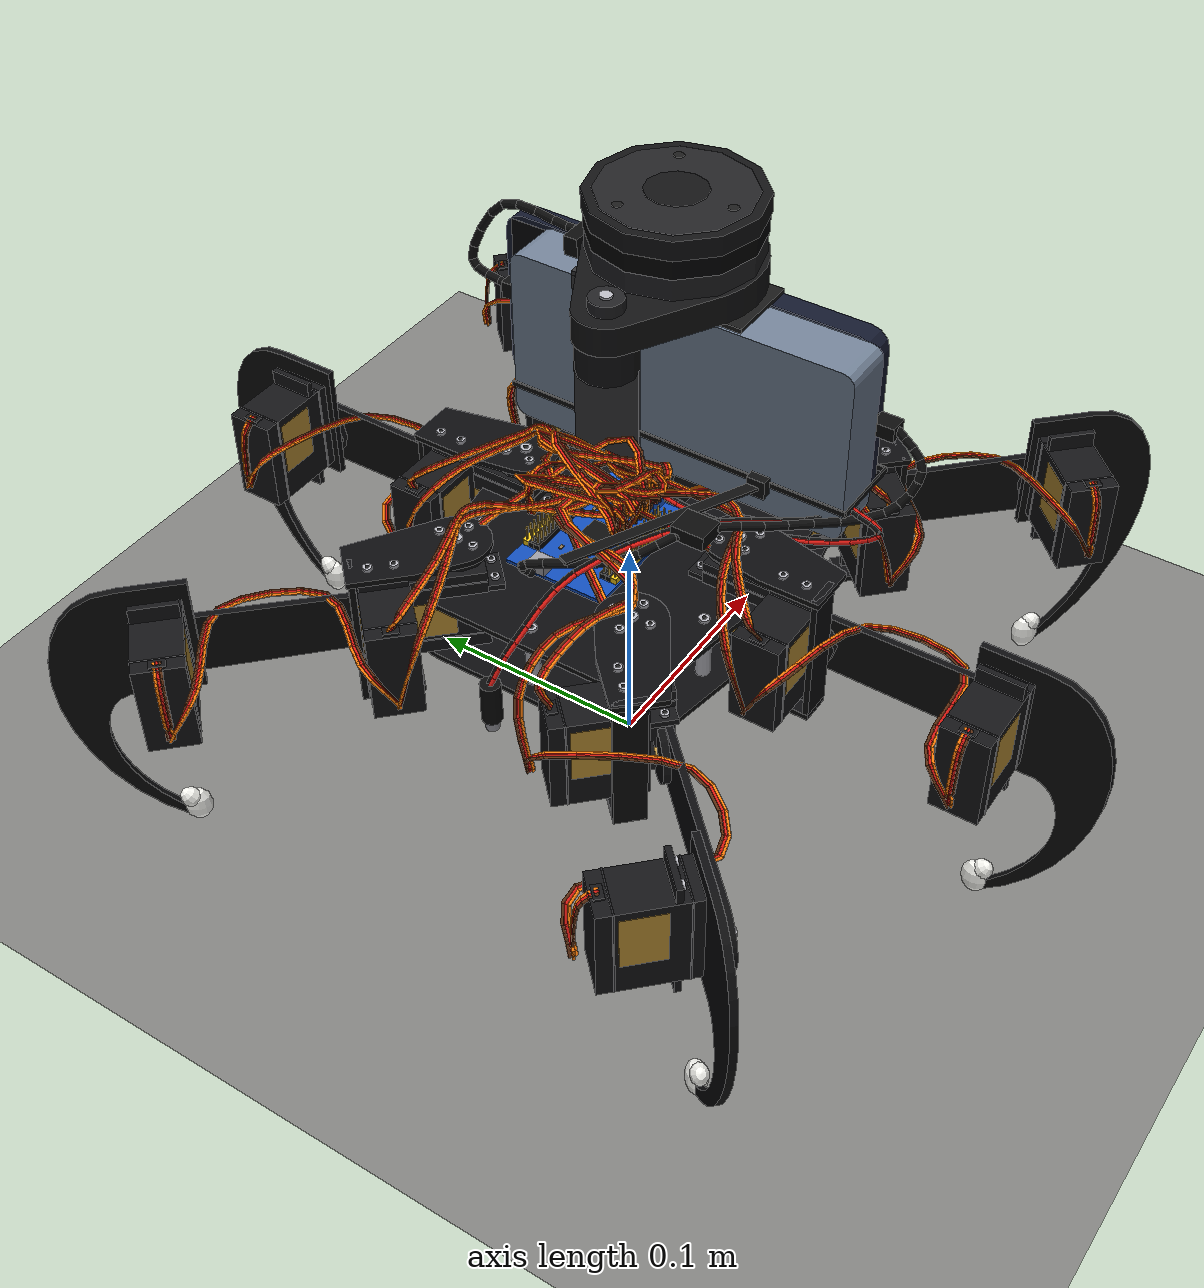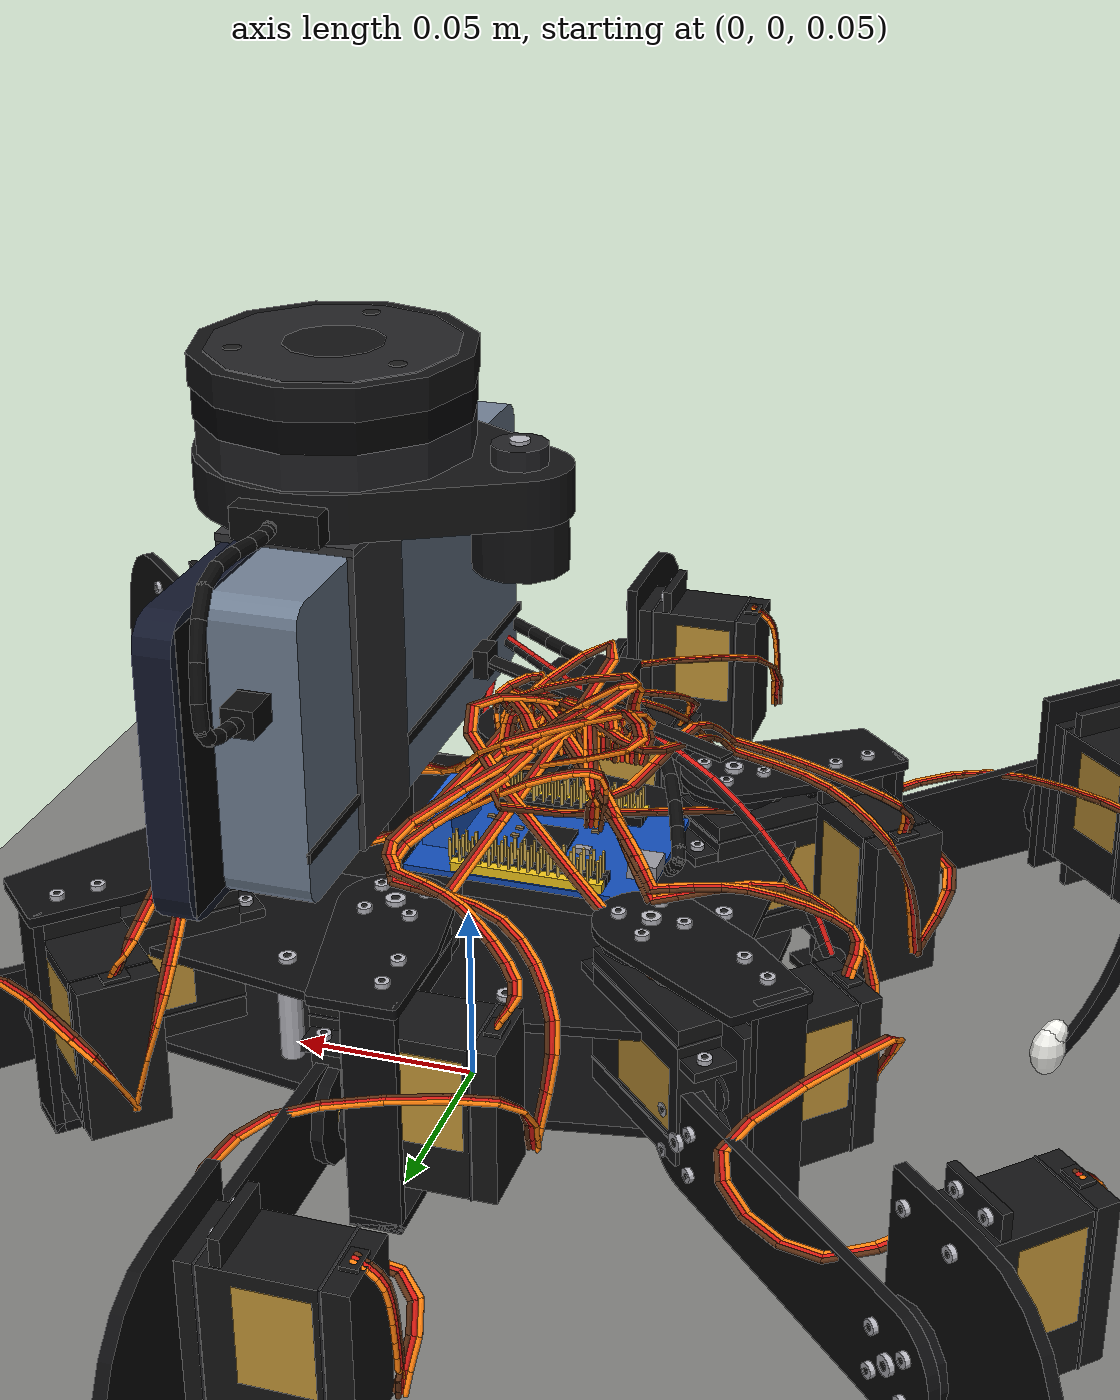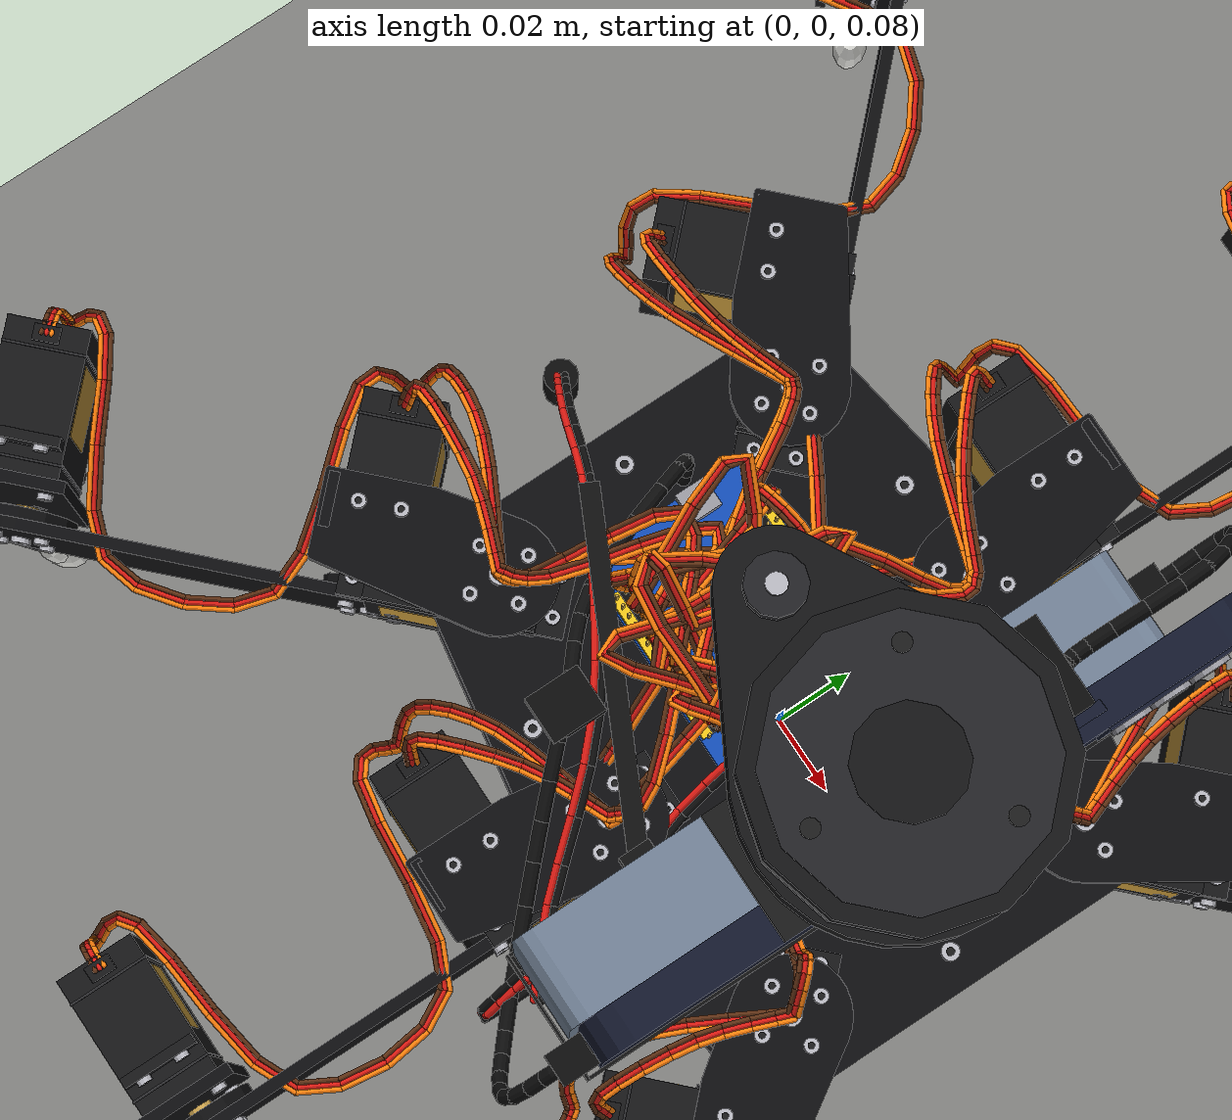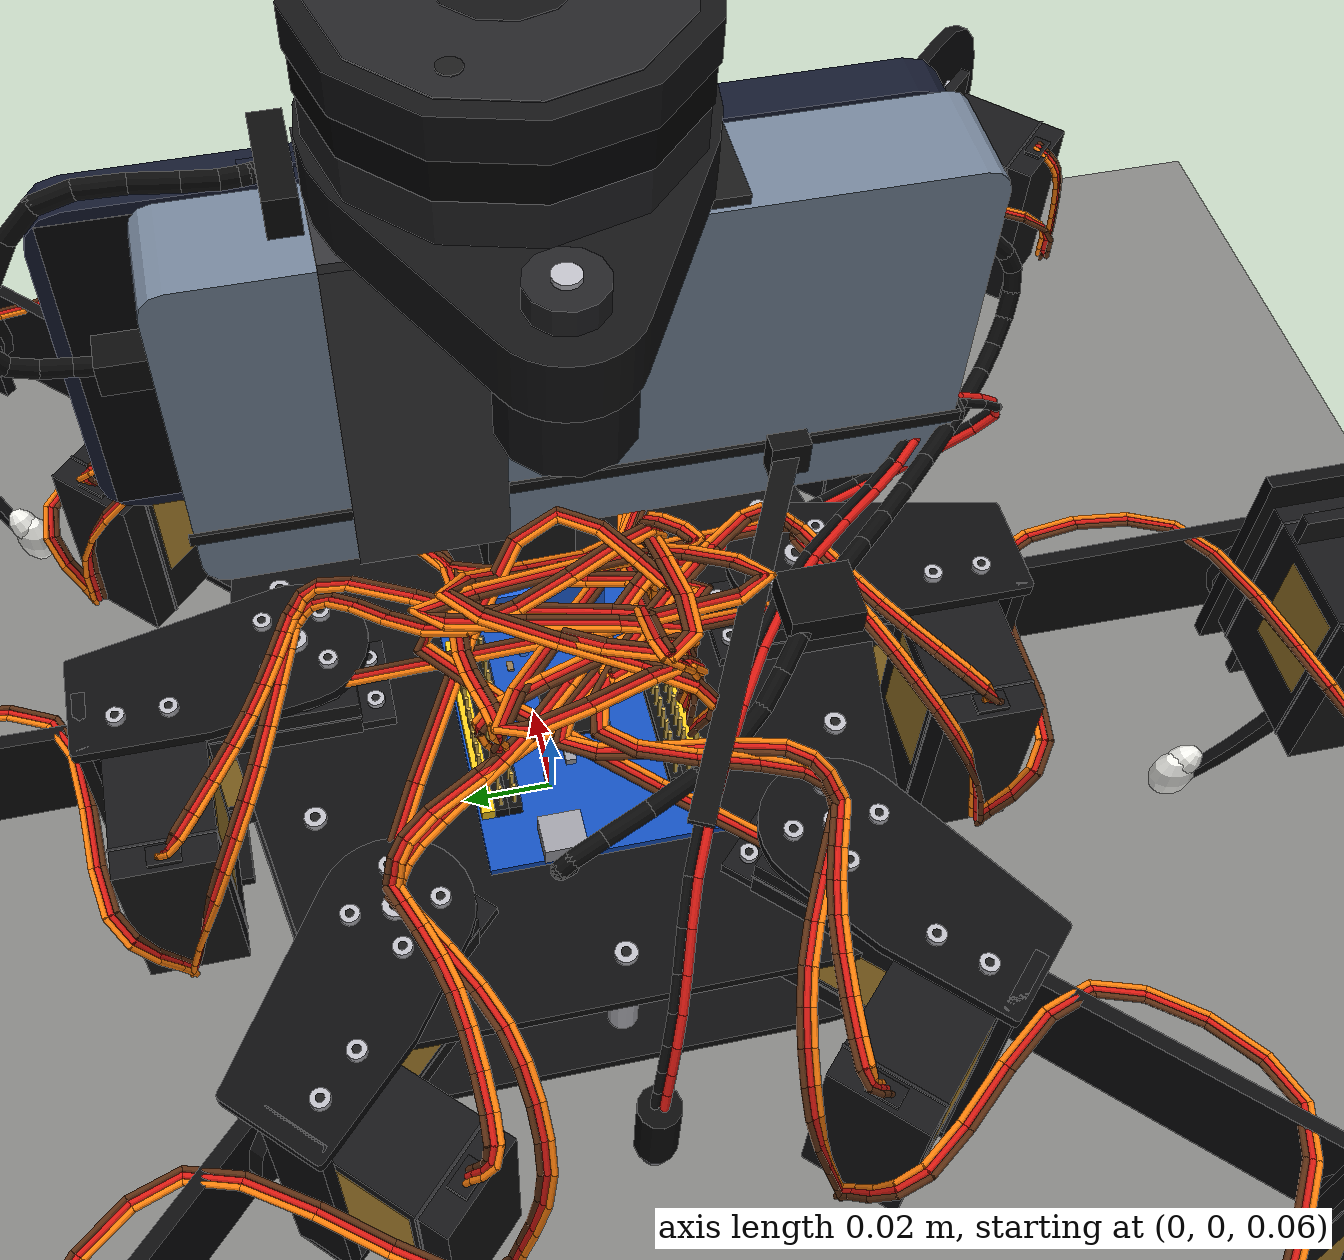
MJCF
<!-- Generated by sim/hexapod_sim.py from python/hexapod.py; edit those, not this file. -->
<mujoco model="hexapod_sar">
  <compiler angle="radian" inertiafromgeom="false" autolimits="true"/>
  <option timestep="0.002" integrator="implicitfast"/>
  <visual>
    <global offwidth="1920" offheight="1440" azimuth="140" elevation="-22"/>
    <quality shadowsize="4096" offsamples="8"/>
    <headlight ambient=".32 .32 .32" diffuse=".45 .45 .45" specular=".1 .1 .1"/>
    <map znear="0.002"/>
  </visual>
  <default>
    <joint armature="0.003" damping="0.05" frictionloss="0.01"/>
    <position kp="20" dampratio="1" forcerange="-1.08 1.08"/>
    <default class="vis"><geom contype="0" conaffinity="0" group="2"/></default>
    <default class="col"><geom contype="1" conaffinity="0" group="3" rgba=".9 .2 .2 .35" friction="0.9 0.02 0.001"/></default>
  </default>
  <asset>
    <texture name="sky" type="skybox" builtin="gradient" rgb1=".85 .87 .9" rgb2=".38 .4 .43" width="512" height="512"/>
    <texture name="floor" type="2d" builtin="flat" mark="random" random="0.012" rgb1=".5 .5 .49" markrgb=".93 .93 .9" width="1024" height="1024"/>
    <material name="floor" texture="floor" texrepeat="4 4" reflectance="0"/>
    <material name="alu" rgba=".045 .045 .05 1" specular="0.55" shininess="0.55" reflectance="0" emission="0"/>
    <material name="servo" rgba=".08 .08 .085 1" specular="0.25" shininess="0.3" reflectance="0" emission="0"/>
    <material name="seam" rgba=".15 .15 .16 1" specular="0.2" shininess="0.2" reflectance="0" emission="0"/>
    <material name="label" rgba=".78 .6 .22 1" specular="0.7" shininess="0.6" reflectance="0" emission="0"/>
    <material name="brass" rgba=".8 .64 .3 1" specular="0.9" shininess="0.8" reflectance="0" emission="0"/>
    <material name="screw" rgba=".72 .72 .75 1" specular="1" shininess="0.9" reflectance="0.05" emission="0"/>
    <material name="socket" rgba=".1 .1 .1 1" specular="0.2" shininess="0.2" reflectance="0" emission="0"/>
    <material name="pcb" rgba=".07 .3 .72 1" specular="0.35" shininess="0.5" reflectance="0" emission="0"/>
    <material name="hdr_s" rgba=".95 .78 .1 1" specular="0.3" shininess="0.3" reflectance="0" emission="0"/>
    <material name="hdr_k" rgba=".04 .04 .04 1" specular="0.3" shininess="0.3" reflectance="0" emission="0"/>
    <material name="pin" rgba=".85 .7 .3 1" specular="0.9" shininess="0.8" reflectance="0" emission="0"/>
    <material name="chip" rgba=".05 .05 .05 1" specular="0.4" shininess="0.5" reflectance="0" emission="0"/>
    <material name="term" rgba=".12 .38 .85 1" specular="0.3" shininess="0.4" reflectance="0" emission="0"/>
    <material name="led" rgba=".25 .55 1 1" specular="1" shininess="1" reflectance="0" emission="2"/>
    <material name="smd" rgba=".55 .45 .3 1" specular="0.3" shininess="0.3" reflectance="0" emission="0"/>
    <material name="plug" rgba=".06 .06 .06 1" specular="0.2" shininess="0.3" reflectance="0" emission="0"/>
    <material name="phone" rgba=".07 .09 .17 1" specular="0.9" shininess="0.95" reflectance="0.08" emission="0"/>
    <material name="glass" rgba=".02 .02 .025 1" specular="1" shininess="1" reflectance="0.25" emission="0"/>
    <material name="ring" rgba=".6 .6 .63 1" specular="1" shininess="0.9" reflectance="0.1" emission="0"/>
    <material name="flash" rgba=".95 .9 .7 1" specular="0.5" shininess="0.5" reflectance="0" emission="0.3"/>
    <material name="pla" rgba=".44 .5 .58 1" specular="0.1" shininess="0.2" reflectance="0" emission="0"/>
    <material name="lidar" rgba=".07 .07 .075 1" specular="0.2" shininess="0.25" reflectance="0" emission="0"/>
    <material name="lidar2" rgba=".13 .13 .14 1" specular="0.3" shininess="0.3" reflectance="0" emission="0"/>
    <material name="window" rgba=".01 .01 .015 1" specular="1" shininess="1" reflectance="0.3" emission="0"/>
    <material name="velcro" rgba=".2 .2 .21 1" specular="0" shininess="0" reflectance="0" emission="0"/>
    <material name="foam" rgba=".09 .09 .09 1" specular="0" shininess="0" reflectance="0" emission="0"/>
    <material name="tie" rgba=".05 .05 .05 1" specular="0.4" shininess="0.4" reflectance="0" emission="0"/>
    <material name="tape" rgba=".95 .95 .93 1" specular="0.15" shininess="0.1" reflectance="0" emission="0"/>
    <material name="nylon" rgba=".9 .9 .86 1" specular="0.2" shininess="0.2" reflectance="0" emission="0"/>
    <material name="rubber" rgba=".04 .04 .04 1" specular="0.3" shininess="0.3" reflectance="0" emission="0"/>
    <material name="wire_o" rgba="1 .5 .04 1" specular="0.4" shininess="0.5" reflectance="0" emission="0"/>
    <material name="wire_r" rgba=".85 .1 .07 1" specular="0.4" shininess="0.5" reflectance="0" emission="0"/>
    <material name="wire_b" rgba=".36 .18 .07 1" specular="0.4" shininess="0.5" reflectance="0" emission="0"/>
    <material name="wire_k" rgba=".04 .04 .04 1" specular="0.4" shininess="0.5" reflectance="0" emission="0"/>
    <mesh name="body_plate" scale="0.001 0.001 0.001" vertex="-77 -40 0 -76.5738 -43.7829 0 -75.3165 -47.376 0 -73.2911 -50.5993 0 -70.5993 -53.2911 0 -67.376 -55.3165 0 -63.7829 -56.5738 0 -3.78286 -66.5738 0 -0 -67 0 3.78286 -66.5738 0 63.7829 -56.5738 0 67.376 -55.3165 0 70.5993 -53.2911 0 73.2911 -50.5993 0 75.3165 -47.376 0 76.5738 -43.7829 0 77 -40 0 77 40 0 76.5738 43.7829 0 75.3165 47.376 0 73.2911 50.5993 0 70.5993 53.2911 0 67.376 55.3165 0 63.7829 56.5738 0 3.78286 66.5738 0 0 67 0 -3.78286 66.5738 0 -63.7829 56.5738 0 -67.376 55.3165 0 -70.5993 53.2911 0 -73.2911 50.5993 0 -75.3165 47.376 0 -76.5738 43.7829 0 -77 40 0 -77 -40 2.5 -76.5738 -43.7829 2.5 -75.3165 -47.376 2.5 -73.2911 -50.5993 2.5 -70.5993 -53.2911 2.5 -67.376 -55.3165 2.5 -63.7829 -56.5738 2.5 -3.78286 -66.5738 2.5 -0 -67 2.5 3.78286 -66.5738 2.5 63.7829 -56.5738 2.5 67.376 -55.3165 2.5 70.5993 -53.2911 2.5 73.2911 -50.5993 2.5 75.3165 -47.376 2.5 76.5738 -43.7829 2.5 77 -40 2.5 77 40 2.5 76.5738 43.7829 2.5 75.3165 47.376 2.5 73.2911 50.5993 2.5 70.5993 53.2911 2.5 67.376 55.3165 2.5 63.7829 56.5738 2.5 3.78286 66.5738 2.5 0 67 2.5 -3.78286 66.5738 2.5 -63.7829 56.5738 2.5 -67.376 55.3165 2.5 -70.5993 53.2911 2.5 -73.2911 50.5993 2.5 -75.3165 47.376 2.5 -76.5738 43.7829 2.5 -77 40 2.5" face="67 34 35 1 0 33 67 35 36 2 1 33 67 36 37 3 2 33 67 37 38 4 3 33 67 38 39 5 4 33 67 39 40 6 5 33 67 40 41 7 6 33 67 41 42 8 7 33 67 42 43 9 8 33 67 43 44 10 9 33 67 44 45 11 10 33 67 45 46 12 11 33 67 46 47 13 12 33 67 47 48 14 13 33 67 48 49 15 14 33 67 49 50 16 15 33 67 50 51 17 16 33 67 51 52 18 17 33 67 52 53 19 18 33 67 53 54 20 19 33 67 54 55 21 20 33 67 55 56 22 21 33 67 56 57 23 22 33 67 57 58 24 23 33 67 58 59 25 24 33 67 59 60 26 25 33 67 60 61 27 26 33 67 61 62 28 27 33 67 62 63 29 28 33 67 63 64 30 29 33 67 64 65 31 30 33 65 66 67 33 32 31 0 1 35 0 35 34 1 2 36 1 36 35 2 3 37 2 37 36 3 4 38 3 38 37 4 5 39 4 39 38 5 6 40 5 40 39 6 7 41 6 41 40 7 8 42 7 42 41 8 9 43 8 43 42 9 10 44 9 44 43 10 11 45 10 45 44 11 12 46 11 46 45 12 13 47 12 47 46 13 14 48 13 48 47 14 15 49 14 49 48 15 16 50 15 50 49 16 17 51 16 51 50 17 18 52 17 52 51 18 19 53 18 53 52 19 20 54 19 54 53 20 21 55 20 55 54 21 22 56 21 56 55 22 23 57 22 57 56 23 24 58 23 58 57 24 25 59 24 59 58 25 26 60 25 60 59 26 27 61 26 61 60 27 28 62 27 62 61 28 29 63 28 63 62 29 30 64 29 64 63 30 31 65 30 65 64 31 32 66 31 66 65 32 33 67 32 67 66 33 0 34 33 34 67"/>
    <mesh name="phone" scale="0.001 0.001 0.001" vertex="-82.7 -30.45 -4.7 -81.6282 -34.45 -4.7 -78.7 -37.3782 -4.7 -74.7 -38.45 -4.7 74.7 -38.45 -4.7 78.7 -37.3782 -4.7 81.6282 -34.45 -4.7 82.7 -30.45 -4.7 82.7 30.45 -4.7 81.6282 34.45 -4.7 78.7 37.3782 -4.7 74.7 38.45 -4.7 -74.7 38.45 -4.7 -78.7 37.3782 -4.7 -81.6282 34.45 -4.7 -82.7 30.45 -4.7 -82.7 -30.45 4.7 -81.6282 -34.45 4.7 -78.7 -37.3782 4.7 -74.7 -38.45 4.7 74.7 -38.45 4.7 78.7 -37.3782 4.7 81.6282 -34.45 4.7 82.7 -30.45 4.7 82.7 30.45 4.7 81.6282 34.45 4.7 78.7 37.3782 4.7 74.7 38.45 4.7 -74.7 38.45 4.7 -78.7 37.3782 4.7 -81.6282 34.45 4.7 -82.7 30.45 4.7" face="31 16 17 1 0 15 31 17 18 2 1 15 31 18 19 3 2 15 31 19 20 4 3 15 31 20 21 5 4 15 31 21 22 6 5 15 31 22 23 7 6 15 31 23 24 8 7 15 31 24 25 9 8 15 31 25 26 10 9 15 31 26 27 11 10 15 31 27 28 12 11 15 31 28 29 13 12 15 29 30 31 15 14 13 0 1 17 0 17 16 1 2 18 1 18 17 2 3 19 2 19 18 3 4 20 3 20 19 4 5 21 4 21 20 5 6 22 5 22 21 6 7 23 6 23 22 7 8 24 7 24 23 8 9 25 8 25 24 9 10 26 9 26 25 10 11 27 10 27 26 11 12 28 11 28 27 12 13 29 12 29 28 13 14 30 13 30 29 14 15 31 14 31 30 15 0 16 15 16 31"/>
    <mesh name="battery" scale="0.001 0.001 0.001" vertex="-75 -33 -11 -74.3301 -35.5 -11 -72.5 -37.3301 -11 -70 -38 -11 70 -38 -11 72.5 -37.3301 -11 74.3301 -35.5 -11 75 -33 -11 75 33 -11 74.3301 35.5 -11 72.5 37.3301 -11 70 38 -11 -70 38 -11 -72.5 37.3301 -11 -74.3301 35.5 -11 -75 33 -11 -75 -33 11 -74.3301 -35.5 11 -72.5 -37.3301 11 -70 -38 11 70 -38 11 72.5 -37.3301 11 74.3301 -35.5 11 75 -33 11 75 33 11 74.3301 35.5 11 72.5 37.3301 11 70 38 11 -70 38 11 -72.5 37.3301 11 -74.3301 35.5 11 -75 33 11" face="31 16 17 1 0 15 31 17 18 2 1 15 31 18 19 3 2 15 31 19 20 4 3 15 31 20 21 5 4 15 31 21 22 6 5 15 31 22 23 7 6 15 31 23 24 8 7 15 31 24 25 9 8 15 31 25 26 10 9 15 31 26 27 11 10 15 31 27 28 12 11 15 31 28 29 13 12 15 29 30 31 15 14 13 0 1 17 0 17 16 1 2 18 1 18 17 2 3 19 2 19 18 3 4 20 3 20 19 4 5 21 4 21 20 5 6 22 5 22 21 6 7 23 6 23 22 7 8 24 7 24 23 8 9 25 8 25 24 9 10 26 9 26 25 10 11 27 10 27 26 11 12 28 11 28 27 12 13 29 12 29 28 13 14 30 13 30 29 14 15 31 14 31 30 15 0 16 15 16 31"/>
    <mesh name="lidar_base" scale="0.001 0.001 0.001" vertex="-35.2 0 0 -34.3175 -7.83274 0 -31.7141 -15.2727 0 -27.5205 -21.9468 0 -21.9468 -27.5205 0 -15.2727 -31.7141 0 -7.83274 -34.3175 0 -0 -35.2 0 7.83274 -34.3175 0 15.2727 -31.7141 0 51.6405 -11.7126 0 54.1054 -10.1638 0 56.1638 -8.10537 0 57.7126 -5.64049 0 58.6741 -2.89277 0 59 0 0 58.6741 2.89277 0 57.7126 5.64049 0 56.1638 8.10537 0 54.1054 10.1638 0 51.6405 11.7126 0 15.2727 31.7141 0 7.83274 34.3175 0 0 35.2 0 -7.83274 34.3175 0 -15.2727 31.7141 0 -21.9468 27.5205 0 -27.5205 21.9468 0 -31.7141 15.2727 0 -34.3175 7.83274 0 -35.2 0 12 -34.3175 -7.83274 12 -31.7141 -15.2727 12 -27.5205 -21.9468 12 -21.9468 -27.5205 12 -15.2727 -31.7141 12 -7.83274 -34.3175 12 -0 -35.2 12 7.83274 -34.3175 12 15.2727 -31.7141 12 51.6405 -11.7126 12 54.1054 -10.1638 12 56.1638 -8.10537 12 57.7126 -5.64049 12 58.6741 -2.89277 12 59 0 12 58.6741 2.89277 12 57.7126 5.64049 12 56.1638 8.10537 12 54.1054 10.1638 12 51.6405 11.7126 12 15.2727 31.7141 12 7.83274 34.3175 12 0 35.2 12 -7.83274 34.3175 12 -15.2727 31.7141 12 -21.9468 27.5205 12 -27.5205 21.9468 12 -31.7141 15.2727 12 -34.3175 7.83274 12" face="59 30 31 1 0 29 59 31 32 2 1 29 59 32 33 3 2 29 59 33 34 4 3 29 59 34 35 5 4 29 59 35 36 6 5 29 59 36 37 7 6 29 59 37 38 8 7 29 59 38 39 9 8 29 59 39 40 10 9 29 59 40 41 11 10 29 59 41 42 12 11 29 59 42 43 13 12 29 59 43 44 14 13 29 59 44 45 15 14 29 59 45 46 16 15 29 59 46 47 17 16 29 59 47 48 18 17 29 59 48 49 19 18 29 59 49 50 20 19 29 59 50 51 21 20 29 59 51 52 22 21 29 59 52 53 23 22 29 59 53 54 24 23 29 59 54 55 25 24 29 59 55 56 26 25 29 59 56 57 27 26 29 57 58 59 29 28 27 0 1 31 0 31 30 1 2 32 1 32 31 2 3 33 2 33 32 3 4 34 3 34 33 4 5 35 4 35 34 5 6 36 5 36 35 6 7 37 6 37 36 7 8 38 7 38 37 8 9 39 8 39 38 9 10 40 9 40 39 10 11 41 10 41 40 11 12 42 11 42 41 12 13 43 12 43 42 13 14 44 13 44 43 14 15 45 14 45 44 15 16 46 15 46 45 16 17 47 16 47 46 17 18 48 17 48 47 18 19 49 18 49 48 19 20 50 19 50 49 20 21 51 20 51 50 21 22 52 21 52 51 22 23 53 22 53 52 23 24 54 23 54 53 24 25 55 24 55 54 25 26 56 25 56 55 26 27 57 26 57 56 27 28 58 27 58 57 28 29 59 28 59 58 29 0 30 29 30 59"/>
    <mesh name="coxa_bracket_R" scale="0.001 0.001 0.001" vertex="-14 0 0 -13.649 -3.11529 0 -12.6136 -6.07437 0 -10.9456 -8.72886 0 -8.72886 -10.9456 0 -6.07437 -12.6136 0 -3.11529 -13.649 0 17.7775 -16.9749 0 18 -17 0 43 -17 0 43.2225 -16.9749 0 43.4339 -16.901 0 43.6235 -16.7818 0 43.7818 -16.6235 0 43.901 -16.4339 0 43.9749 -16.2225 0 44 -16 0 44 4 0 43.9749 4.22252 0 43.901 4.43388 0 43.7818 4.62349 0 43.6235 4.78183 0 43.4339 4.90097 0 43.2225 4.97493 0 3.11529 13.649 0 0 14 0 -3.11529 13.649 0 -6.07437 12.6136 0 -8.72886 10.9456 0 -10.9456 8.72886 0 -12.6136 6.07437 0 -13.649 3.11529 0 -14 0 2.5 -13.649 -3.11529 2.5 -12.6136 -6.07437 2.5 -10.9456 -8.72886 2.5 -8.72886 -10.9456 2.5 -6.07437 -12.6136 2.5 -3.11529 -13.649 2.5 17.7775 -16.9749 2.5 18 -17 2.5 43 -17 2.5 43.2225 -16.9749 2.5 43.4339 -16.901 2.5 43.6235 -16.7818 2.5 43.7818 -16.6235 2.5 43.901 -16.4339 2.5 43.9749 -16.2225 2.5 44 -16 2.5 44 4 2.5 43.9749 4.22252 2.5 43.901 4.43388 2.5 43.7818 4.62349 2.5 43.6235 4.78183 2.5 43.4339 4.90097 2.5 43.2225 4.97493 2.5 3.11529 13.649 2.5 0 14 2.5 -3.11529 13.649 2.5 -6.07437 12.6136 2.5 -8.72886 10.9456 2.5 -10.9456 8.72886 2.5 -12.6136 6.07437 2.5 -13.649 3.11529 2.5" face="63 32 33 1 0 31 63 33 34 2 1 31 63 34 35 3 2 31 63 35 36 4 3 31 63 36 37 5 4 31 63 37 38 6 5 31 63 38 39 7 6 31 63 39 40 8 7 31 63 40 41 9 8 31 63 41 42 10 9 31 63 42 43 11 10 31 63 43 44 12 11 31 63 44 45 13 12 31 63 45 46 14 13 31 63 46 47 15 14 31 63 47 48 16 15 31 63 48 49 17 16 31 63 49 50 18 17 31 63 50 51 19 18 31 63 51 52 20 19 31 63 52 53 21 20 31 63 53 54 22 21 31 63 54 55 23 22 31 63 55 56 24 23 31 63 56 57 25 24 31 63 57 58 26 25 31 63 58 59 27 26 31 63 59 60 28 27 31 63 60 61 29 28 31 61 62 63 31 30 29 0 1 33 0 33 32 1 2 34 1 34 33 2 3 35 2 35 34 3 4 36 3 36 35 4 5 37 4 37 36 5 6 38 5 38 37 6 7 39 6 39 38 7 8 40 7 40 39 8 9 41 8 41 40 9 10 42 9 42 41 10 11 43 10 43 42 11 12 44 11 44 43 12 13 45 12 45 44 13 14 46 13 46 45 14 15 47 14 47 46 15 16 48 15 48 47 16 17 49 16 49 48 17 18 50 17 50 49 18 19 51 18 51 50 19 20 52 19 52 51 20 21 53 20 53 52 21 22 54 21 54 53 22 23 55 22 55 54 23 24 56 23 56 55 24 25 57 24 57 56 25 26 58 25 58 57 26 27 59 26 59 58 27 28 60 27 60 59 28 29 61 28 61 60 29 30 62 29 62 61 30 31 63 30 63 62 31 0 32 31 32 63"/>
    <mesh name="femur" scale="0.001 0.001 0.001" vertex="-13 0 -1.5 -12.6741 -2.89277 -1.5 -11.7126 -5.64049 -1.5 -10.1638 -8.10537 -1.5 -8.10537 -10.1638 -1.5 -5.64049 -11.7126 -1.5 -2.89277 -12.6741 -1.5 -0 -13 -1.5 85 -14 -1.5 88.1153 -13.649 -1.5 91.0744 -12.6136 -1.5 93.7289 -10.9456 -1.5 95.9456 -8.72886 -1.5 97.6136 -6.07437 -1.5 98.649 -3.11529 -1.5 99 0 -1.5 98.649 3.11529 -1.5 97.6136 6.07437 -1.5 95.9456 8.72886 -1.5 93.7289 10.9456 -1.5 91.0744 12.6136 -1.5 88.1153 13.649 -1.5 85 14 -1.5 0 13 -1.5 -2.89277 12.6741 -1.5 -5.64049 11.7126 -1.5 -8.10537 10.1638 -1.5 -10.1638 8.10537 -1.5 -11.7126 5.64049 -1.5 -12.6741 2.89277 -1.5 -13 0 1.5 -12.6741 -2.89277 1.5 -11.7126 -5.64049 1.5 -10.1638 -8.10537 1.5 -8.10537 -10.1638 1.5 -5.64049 -11.7126 1.5 -2.89277 -12.6741 1.5 -0 -13 1.5 85 -14 1.5 88.1153 -13.649 1.5 91.0744 -12.6136 1.5 93.7289 -10.9456 1.5 95.9456 -8.72886 1.5 97.6136 -6.07437 1.5 98.649 -3.11529 1.5 99 0 1.5 98.649 3.11529 1.5 97.6136 6.07437 1.5 95.9456 8.72886 1.5 93.7289 10.9456 1.5 91.0744 12.6136 1.5 88.1153 13.649 1.5 85 14 1.5 0 13 1.5 -2.89277 12.6741 1.5 -5.64049 11.7126 1.5 -8.10537 10.1638 1.5 -10.1638 8.10537 1.5 -11.7126 5.64049 1.5 -12.6741 2.89277 1.5" face="59 30 31 1 0 29 59 31 32 2 1 29 59 32 33 3 2 29 59 33 34 4 3 29 59 34 35 5 4 29 59 35 36 6 5 29 59 36 37 7 6 29 59 37 38 8 7 29 59 38 39 9 8 29 59 39 40 10 9 29 59 40 41 11 10 29 59 41 42 12 11 29 59 42 43 13 12 29 59 43 44 14 13 29 59 44 45 15 14 29 59 45 46 16 15 29 59 46 47 17 16 29 59 47 48 18 17 29 59 48 49 19 18 29 59 49 50 20 19 29 59 50 51 21 20 29 59 51 52 22 21 29 59 52 53 23 22 29 59 53 54 24 23 29 59 54 55 25 24 29 59 55 56 26 25 29 59 56 57 27 26 29 57 58 59 29 28 27 0 1 31 0 31 30 1 2 32 1 32 31 2 3 33 2 33 32 3 4 34 3 34 33 4 5 35 4 35 34 5 6 36 5 36 35 6 7 37 6 37 36 7 8 38 7 38 37 8 9 39 8 39 38 9 10 40 9 40 39 10 11 41 10 41 40 11 12 42 11 42 41 12 13 43 12 43 42 13 14 44 13 44 43 14 15 45 14 45 44 15 16 46 15 46 45 16 17 47 16 47 46 17 18 48 17 48 47 18 19 49 18 49 48 19 20 50 19 50 49 20 21 51 20 51 50 21 22 52 21 52 51 22 23 53 22 53 52 23 24 54 23 54 53 24 25 55 24 55 54 25 26 56 25 56 55 26 27 57 26 57 56 27 28 58 27 58 57 28 29 59 28 59 58 29 0 30 29 30 59"/>
    <mesh name="tibia" scale="0.001 0.001 0.001" vertex="-13 -15 -1.5 12 -15 -1.5 16.4279 -14.8761 -1.5 20.2421 -16.3311 -1.5 23.3616 -19.1969 -1.5 25.7052 -23.3055 -1.5 27.1919 -28.4891 -1.5 27.7404 -34.5796 -1.5 27.2697 -41.4091 -1.5 25.6987 -48.8097 -1.5 22.9462 -56.6134 -1.5 18.9313 -64.6523 -1.5 13.5726 -72.7583 -1.5 6.78926 -80.7635 -1.5 -1.5 -88.5 -1.5 2 -90 -1.5 13.5014 -79.848 -1.5 23.1829 -68.34 -1.5 31.0564 -55.8598 -1.5 37.1341 -42.7911 -1.5 41.4279 -29.5175 -1.5 43.9497 -16.4228 -1.5 44.7118 -3.89076 -1.5 43.726 7.69504 -1.5 41.0044 17.9508 -1.5 36.5589 26.4929 -1.5 30.4017 32.9376 -1.5 22.5447 36.9012 -1.5 13 38 -1.5 -13 38 -1.5 -13 -15 1.5 12 -15 1.5 16.4279 -14.8761 1.5 20.2421 -16.3311 1.5 23.3616 -19.1969 1.5 25.7052 -23.3055 1.5 27.1919 -28.4891 1.5 27.7404 -34.5796 1.5 27.2697 -41.4091 1.5 25.6987 -48.8097 1.5 22.9462 -56.6134 1.5 18.9313 -64.6523 1.5 13.5726 -72.7583 1.5 6.78926 -80.7635 1.5 -1.5 -88.5 1.5 2 -90 1.5 13.5014 -79.848 1.5 23.1829 -68.34 1.5 31.0564 -55.8598 1.5 37.1341 -42.7911 1.5 41.4279 -29.5175 1.5 43.9497 -16.4228 1.5 44.7118 -3.89076 1.5 43.726 7.69504 1.5 41.0044 17.9508 1.5 36.5589 26.4929 1.5 30.4017 32.9376 1.5 22.5447 36.9012 1.5 13 38 1.5 -13 38 1.5" face="59 30 31 1 0 29 59 31 32 2 1 29 59 32 33 3 2 29 59 33 34 4 3 29 43 44 45 15 14 13 42 43 45 15 13 12 42 45 46 16 15 12 41 42 46 16 12 11 40 41 46 16 11 10 40 46 47 17 16 10 39 40 47 17 10 9 38 39 47 17 9 8 38 47 48 18 17 8 37 38 48 18 8 7 36 37 48 18 7 6 36 48 49 19 18 6 35 36 49 19 6 5 34 35 49 19 5 4 34 49 50 20 19 4 59 34 50 20 4 29 59 50 51 21 20 29 59 51 52 22 21 29 59 52 53 23 22 29 59 53 54 24 23 29 59 54 55 25 24 29 59 55 56 26 25 29 59 56 57 27 26 29 57 58 59 29 28 27 0 1 31 0 31 30 1 2 32 1 32 31 2 3 33 2 33 32 3 4 34 3 34 33 4 5 35 4 35 34 5 6 36 5 36 35 6 7 37 6 37 36 7 8 38 7 38 37 8 9 39 8 39 38 9 10 40 9 40 39 10 11 41 10 41 40 11 12 42 11 42 41 12 13 43 12 43 42 13 14 44 13 44 43 14 15 45 14 45 44 15 16 46 15 46 45 16 17 47 16 47 46 17 18 48 17 48 47 18 19 49 18 49 48 19 20 50 19 50 49 20 21 51 20 51 50 21 22 52 21 52 51 22 23 53 22 53 52 23 24 54 23 54 53 24 25 55 24 55 54 25 26 56 25 56 55 26 27 57 26 57 56 27 28 58 27 58 57 28 29 59 28 59 58 29 0 30 29 30 59"/>
    <mesh name="coxa_bracket_L" scale="0.001 0.001 0.001" vertex="-14 0 0 -13.649 -3.11529 0 -12.6136 -6.07437 0 -10.9456 -8.72886 0 -8.72886 -10.9456 0 -6.07437 -12.6136 0 -3.11529 -13.649 0 -0 -14 0 3.11529 -13.649 0 43.2225 -4.97493 0 43.4339 -4.90097 0 43.6235 -4.78183 0 43.7818 -4.62349 0 43.901 -4.43388 0 43.9749 -4.22252 0 44 -4 0 44 16 0 43.9749 16.2225 0 43.901 16.4339 0 43.7818 16.6235 0 43.6235 16.7818 0 43.4339 16.901 0 43.2225 16.9749 0 43 17 0 18 17 0 17.7775 16.9749 0 -3.11529 13.649 0 -6.07437 12.6136 0 -8.72886 10.9456 0 -10.9456 8.72886 0 -12.6136 6.07437 0 -13.649 3.11529 0 -14 0 2.5 -13.649 -3.11529 2.5 -12.6136 -6.07437 2.5 -10.9456 -8.72886 2.5 -8.72886 -10.9456 2.5 -6.07437 -12.6136 2.5 -3.11529 -13.649 2.5 -0 -14 2.5 3.11529 -13.649 2.5 43.2225 -4.97493 2.5 43.4339 -4.90097 2.5 43.6235 -4.78183 2.5 43.7818 -4.62349 2.5 43.901 -4.43388 2.5 43.9749 -4.22252 2.5 44 -4 2.5 44 16 2.5 43.9749 16.2225 2.5 43.901 16.4339 2.5 43.7818 16.6235 2.5 43.6235 16.7818 2.5 43.4339 16.901 2.5 43.2225 16.9749 2.5 43 17 2.5 18 17 2.5 17.7775 16.9749 2.5 -3.11529 13.649 2.5 -6.07437 12.6136 2.5 -8.72886 10.9456 2.5 -10.9456 8.72886 2.5 -12.6136 6.07437 2.5 -13.649 3.11529 2.5" face="63 32 33 1 0 31 63 33 34 2 1 31 63 34 35 3 2 31 63 35 36 4 3 31 63 36 37 5 4 31 63 37 38 6 5 31 63 38 39 7 6 31 63 39 40 8 7 31 63 40 41 9 8 31 63 41 42 10 9 31 63 42 43 11 10 31 63 43 44 12 11 31 63 44 45 13 12 31 63 45 46 14 13 31 63 46 47 15 14 31 63 47 48 16 15 31 63 48 49 17 16 31 63 49 50 18 17 31 63 50 51 19 18 31 63 51 52 20 19 31 63 52 53 21 20 31 63 53 54 22 21 31 63 54 55 23 22 31 63 55 56 24 23 31 63 56 57 25 24 31 63 57 58 26 25 31 63 58 59 27 26 31 63 59 60 28 27 31 63 60 61 29 28 31 61 62 63 31 30 29 0 1 33 0 33 32 1 2 34 1 34 33 2 3 35 2 35 34 3 4 36 3 36 35 4 5 37 4 37 36 5 6 38 5 38 37 6 7 39 6 39 38 7 8 40 7 40 39 8 9 41 8 41 40 9 10 42 9 42 41 10 11 43 10 43 42 11 12 44 11 44 43 12 13 45 12 45 44 13 14 46 13 46 45 14 15 47 14 47 46 15 16 48 15 48 47 16 17 49 16 49 48 17 18 50 17 50 49 18 19 51 18 51 50 19 20 52 19 52 51 20 21 53 20 53 52 21 22 54 21 54 53 22 23 55 22 55 54 23 24 56 23 56 55 24 25 57 24 57 56 25 26 58 25 58 57 26 27 59 26 59 58 27 28 60 27 60 59 28 29 61 28 61 60 29 30 62 29 62 61 30 31 63 30 63 62 31 0 32 31 32 63"/>
  </asset>
  <worldbody>
    <light name="sun" directional="true" pos="0 0 3" dir="0.35 0.45 -1" diffuse=".7 .7 .7" specular=".2 .2 .2" castshadow="true"/>
    <light name="fill" directional="true" pos="0 0 3" dir="-0.5 -0.3 -1" diffuse=".25 .25 .27" castshadow="false"/>
    <geom name="floor" type="plane" size="0 0 0.05" material="floor" condim="3" friction="0.9 0.02 0.001"/>
    <body name="torso" pos="0 0 0.091">
      <freejoint name="root"/>
      <inertial pos="0.0166592 -0.00210612 0.0581039" mass="1.225" fullinertia="0.00518548 0.00489677 0.00421114 2.40993e-05 -0.000808072 6.1652e-05"/>
      <camera name="phone_cam" pos="0.0487 0.07 0.10945" xyaxes="0 -1 0 0 0 1" fovy="70"/>
      <site name="imu" pos="0.0417 0 0.08245" size="0.005" group="4"/>
      <geom class="vis" material="alu" type="mesh" mesh="body_plate" pos="0 0 -0.009" quat="1 0 0 0"/>
      <geom class="vis" material="alu" type="mesh" mesh="body_plate" pos="0 0 0.018" quat="1 0 0 0"/>
      <geom class="vis" material="screw" type="cylinder" fromto="0.068 0 -0.0065 0.068 0 0.018" size="0.003"/>
      <geom class="vis" material="screw" type="cylinder" fromto="0.068 0 0.0205 0.068 0 0.0218" size="0.0022"/>
      <geom class="vis" material="socket" type="cylinder" fromto="0.068 0 0.02175 0.068 0 0.0219" size="0.00099"/>
      <geom class="vis" material="screw" type="cylinder" fromto="0.068 0 -0.009 0.068 0 -0.0103" size="0.0022"/>
      <geom class="vis" material="socket" type="cylinder" fromto="0.068 0 -0.01025 0.068 0 -0.0104" size="0.00099"/>
      <geom class="vis" material="screw" type="cylinder" fromto="-0.068 0 -0.0065 -0.068 0 0.018" size="0.003"/>
      <geom class="vis" material="screw" type="cylinder" fromto="-0.068 0 0.0205 -0.068 0 0.0218" size="0.0022"/>
      <geom class="vis" material="socket" type="cylinder" fromto="-0.068 0 0.02175 -0.068 0 0.0219" size="0.00099"/>
      <geom class="vis" material="screw" type="cylinder" fromto="-0.068 0 -0.009 -0.068 0 -0.0103" size="0.0022"/>
      <geom class="vis" material="socket" type="cylinder" fromto="-0.068 0 -0.01025 -0.068 0 -0.0104" size="0.00099"/>
      <geom class="vis" material="screw" type="cylinder" fromto="0.028 0.052 -0.0065 0.028 0.052 0.018" size="0.003"/>
      <geom class="vis" material="screw" type="cylinder" fromto="0.028 0.052 0.0205 0.028 0.052 0.0218" size="0.0022"/>
      <geom class="vis" material="socket" type="cylinder" fromto="0.028 0.052 0.02175 0.028 0.052 0.0219" size="0.00099"/>
      <geom class="vis" material="screw" type="cylinder" fromto="0.028 0.052 -0.009 0.028 0.052 -0.0103" size="0.0022"/>
      <geom class="vis" material="socket" type="cylinder" fromto="0.028 0.052 -0.01025 0.028 0.052 -0.0104" size="0.00099"/>
      <geom class="vis" material="screw" type="cylinder" fromto="0.028 -0.052 -0.0065 0.028 -0.052 0.018" size="0.003"/>
      <geom class="vis" material="screw" type="cylinder" fromto="0.028 -0.052 0.0205 0.028 -0.052 0.0218" size="0.0022"/>
      <geom class="vis" material="socket" type="cylinder" fromto="0.028 -0.052 0.02175 0.028 -0.052 0.0219" size="0.00099"/>
      <geom class="vis" material="screw" type="cylinder" fromto="0.028 -0.052 -0.009 0.028 -0.052 -0.0103" size="0.0022"/>
      <geom class="vis" material="socket" type="cylinder" fromto="0.028 -0.052 -0.01025 0.028 -0.052 -0.0104" size="0.00099"/>
      <geom class="vis" material="screw" type="cylinder" fromto="-0.028 0.052 -0.0065 -0.028 0.052 0.018" size="0.003"/>
      <geom class="vis" material="screw" type="cylinder" fromto="-0.028 0.052 0.0205 -0.028 0.052 0.0218" size="0.0022"/>
      <geom class="vis" material="socket" type="cylinder" fromto="-0.028 0.052 0.02175 -0.028 0.052 0.0219" size="0.00099"/>
      <geom class="vis" material="screw" type="cylinder" fromto="-0.028 0.052 -0.009 -0.028 0.052 -0.0103" size="0.0022"/>
      <geom class="vis" material="socket" type="cylinder" fromto="-0.028 0.052 -0.01025 -0.028 0.052 -0.0104" size="0.00099"/>
      <geom class="vis" material="screw" type="cylinder" fromto="-0.028 -0.052 -0.0065 -0.028 -0.052 0.018" size="0.003"/>
      <geom class="vis" material="screw" type="cylinder" fromto="-0.028 -0.052 0.0205 -0.028 -0.052 0.0218" size="0.0022"/>
      <geom class="vis" material="socket" type="cylinder" fromto="-0.028 -0.052 0.02175 -0.028 -0.052 0.0219" size="0.00099"/>
      <geom class="vis" material="screw" type="cylinder" fromto="-0.028 -0.052 -0.009 -0.028 -0.052 -0.0103" size="0.0022"/>
      <geom class="vis" material="socket" type="cylinder" fromto="-0.028 -0.052 -0.01025 -0.028 -0.052 -0.0104" size="0.00099"/>
      <geom class="vis" material="foam" type="box" pos="-0.022 0 0.0265" quat="1 0 0 0" size="0.02 0.01 0.006"/>
      <geom class="vis" material="pcb" type="box" pos="-0.022 0 0.0333" quat="1 0 0 0" size="0.031 0.022 0.0008"/>
      <geom class="vis" material="hdr_s" type="box" pos="-0.02276 -0.0203 0.03535" quat="1 0 0 0" size="0.01956 0.00127 0.00125"/>
      <geom class="vis" material="pin" type="box" pos="-0.04105 -0.0203 0.03955" quat="1 0 0 0" size="0.00032 0.00032 0.00295"/>
      <geom class="vis" material="pin" type="box" pos="-0.03851 -0.0203 0.03955" quat="1 0 0 0" size="0.00032 0.00032 0.00295"/>
      <geom class="vis" material="pin" type="box" pos="-0.03597 -0.0203 0.03955" quat="1 0 0 0" size="0.00032 0.00032 0.00295"/>
      <geom class="vis" material="pin" type="box" pos="-0.03343 -0.0203 0.03955" quat="1 0 0 0" size="0.00032 0.00032 0.00295"/>
      <geom class="vis" material="pin" type="box" pos="-0.03089 -0.0203 0.03955" quat="1 0 0 0" size="0.00032 0.00032 0.00295"/>
      <geom class="vis" material="pin" type="box" pos="-0.02835 -0.0203 0.03955" quat="1 0 0 0" size="0.00032 0.00032 0.00295"/>
      <geom class="vis" material="pin" type="box" pos="-0.02581 -0.0203 0.03955" quat="1 0 0 0" size="0.00032 0.00032 0.00295"/>
      <geom class="vis" material="pin" type="box" pos="-0.02327 -0.0203 0.03955" quat="1 0 0 0" size="0.00032 0.00032 0.00295"/>
      <geom class="vis" material="pin" type="box" pos="-0.02073 -0.0203 0.03955" quat="1 0 0 0" size="0.00032 0.00032 0.00295"/>
      <geom class="vis" material="pin" type="box" pos="-0.01819 -0.0203 0.03955" quat="1 0 0 0" size="0.00032 0.00032 0.00295"/>
      <geom class="vis" material="pin" type="box" pos="-0.01565 -0.0203 0.03955" quat="1 0 0 0" size="0.00032 0.00032 0.00295"/>
      <geom class="vis" material="pin" type="box" pos="-0.01311 -0.0203 0.03955" quat="1 0 0 0" size="0.00032 0.00032 0.00295"/>
      <geom class="vis" material="pin" type="box" pos="-0.01057 -0.0203 0.03955" quat="1 0 0 0" size="0.00032 0.00032 0.00295"/>
      <geom class="vis" material="pin" type="box" pos="-0.00803 -0.0203 0.03955" quat="1 0 0 0" size="0.00032 0.00032 0.00295"/>
      <geom class="vis" material="pin" type="box" pos="-0.00549 -0.0203 0.03955" quat="1 0 0 0" size="0.00032 0.00032 0.00295"/>
      <geom class="vis" material="pin" type="box" pos="-0.00295 -0.0203 0.03955" quat="1 0 0 0" size="0.00032 0.00032 0.00295"/>
      <geom class="vis" material="hdr_k" type="box" pos="-0.02276 -0.01776 0.03535" quat="1 0 0 0" size="0.01956 0.00127 0.00125"/>
      <geom class="vis" material="pin" type="box" pos="-0.04105 -0.01776 0.03955" quat="1 0 0 0" size="0.00032 0.00032 0.00295"/>
      <geom class="vis" material="pin" type="box" pos="-0.03851 -0.01776 0.03955" quat="1 0 0 0" size="0.00032 0.00032 0.00295"/>
      <geom class="vis" material="pin" type="box" pos="-0.03597 -0.01776 0.03955" quat="1 0 0 0" size="0.00032 0.00032 0.00295"/>
      <geom class="vis" material="pin" type="box" pos="-0.03343 -0.01776 0.03955" quat="1 0 0 0" size="0.00032 0.00032 0.00295"/>
      <geom class="vis" material="pin" type="box" pos="-0.03089 -0.01776 0.03955" quat="1 0 0 0" size="0.00032 0.00032 0.00295"/>
      <geom class="vis" material="pin" type="box" pos="-0.02835 -0.01776 0.03955" quat="1 0 0 0" size="0.00032 0.00032 0.00295"/>
      <geom class="vis" material="pin" type="box" pos="-0.02581 -0.01776 0.03955" quat="1 0 0 0" size="0.00032 0.00032 0.00295"/>
      <geom class="vis" material="pin" type="box" pos="-0.02327 -0.01776 0.03955" quat="1 0 0 0" size="0.00032 0.00032 0.00295"/>
      <geom class="vis" material="pin" type="box" pos="-0.02073 -0.01776 0.03955" quat="1 0 0 0" size="0.00032 0.00032 0.00295"/>
      <geom class="vis" material="pin" type="box" pos="-0.01819 -0.01776 0.03955" quat="1 0 0 0" size="0.00032 0.00032 0.00295"/>
      <geom class="vis" material="pin" type="box" pos="-0.01565 -0.01776 0.03955" quat="1 0 0 0" size="0.00032 0.00032 0.00295"/>
      <geom class="vis" material="pin" type="box" pos="-0.01311 -0.01776 0.03955" quat="1 0 0 0" size="0.00032 0.00032 0.00295"/>
      <geom class="vis" material="pin" type="box" pos="-0.01057 -0.01776 0.03955" quat="1 0 0 0" size="0.00032 0.00032 0.00295"/>
      <geom class="vis" material="pin" type="box" pos="-0.00803 -0.01776 0.03955" quat="1 0 0 0" size="0.00032 0.00032 0.00295"/>
      <geom class="vis" material="pin" type="box" pos="-0.00549 -0.01776 0.03955" quat="1 0 0 0" size="0.00032 0.00032 0.00295"/>
      <geom class="vis" material="pin" type="box" pos="-0.00295 -0.01776 0.03955" quat="1 0 0 0" size="0.00032 0.00032 0.00295"/>
      <geom class="vis" material="hdr_k" type="box" pos="-0.02276 -0.01522 0.03535" quat="1 0 0 0" size="0.01956 0.00127 0.00125"/>
      <geom class="vis" material="pin" type="box" pos="-0.04105 -0.01522 0.03955" quat="1 0 0 0" size="0.00032 0.00032 0.00295"/>
      <geom class="vis" material="pin" type="box" pos="-0.03851 -0.01522 0.03955" quat="1 0 0 0" size="0.00032 0.00032 0.00295"/>
      <geom class="vis" material="pin" type="box" pos="-0.03597 -0.01522 0.03955" quat="1 0 0 0" size="0.00032 0.00032 0.00295"/>
      <geom class="vis" material="pin" type="box" pos="-0.03343 -0.01522 0.03955" quat="1 0 0 0" size="0.00032 0.00032 0.00295"/>
      <geom class="vis" material="pin" type="box" pos="-0.03089 -0.01522 0.03955" quat="1 0 0 0" size="0.00032 0.00032 0.00295"/>
      <geom class="vis" material="pin" type="box" pos="-0.02835 -0.01522 0.03955" quat="1 0 0 0" size="0.00032 0.00032 0.00295"/>
      <geom class="vis" material="pin" type="box" pos="-0.02581 -0.01522 0.03955" quat="1 0 0 0" size="0.00032 0.00032 0.00295"/>
      <geom class="vis" material="pin" type="box" pos="-0.02327 -0.01522 0.03955" quat="1 0 0 0" size="0.00032 0.00032 0.00295"/>
      <geom class="vis" material="pin" type="box" pos="-0.02073 -0.01522 0.03955" quat="1 0 0 0" size="0.00032 0.00032 0.00295"/>
      <geom class="vis" material="pin" type="box" pos="-0.01819 -0.01522 0.03955" quat="1 0 0 0" size="0.00032 0.00032 0.00295"/>
      <geom class="vis" material="pin" type="box" pos="-0.01565 -0.01522 0.03955" quat="1 0 0 0" size="0.00032 0.00032 0.00295"/>
      <geom class="vis" material="pin" type="box" pos="-0.01311 -0.01522 0.03955" quat="1 0 0 0" size="0.00032 0.00032 0.00295"/>
      <geom class="vis" material="pin" type="box" pos="-0.01057 -0.01522 0.03955" quat="1 0 0 0" size="0.00032 0.00032 0.00295"/>
      <geom class="vis" material="pin" type="box" pos="-0.00803 -0.01522 0.03955" quat="1 0 0 0" size="0.00032 0.00032 0.00295"/>
      <geom class="vis" material="pin" type="box" pos="-0.00549 -0.01522 0.03955" quat="1 0 0 0" size="0.00032 0.00032 0.00295"/>
      <geom class="vis" material="pin" type="box" pos="-0.00295 -0.01522 0.03955" quat="1 0 0 0" size="0.00032 0.00032 0.00295"/>
      <geom class="vis" material="hdr_s" type="box" pos="-0.02276 0.0203 0.03535" quat="1 0 0 0" size="0.01956 0.00127 0.00125"/>
      <geom class="vis" material="pin" type="box" pos="-0.04105 0.0203 0.03955" quat="1 0 0 0" size="0.00032 0.00032 0.00295"/>
      <geom class="vis" material="pin" type="box" pos="-0.03851 0.0203 0.03955" quat="1 0 0 0" size="0.00032 0.00032 0.00295"/>
      <geom class="vis" material="pin" type="box" pos="-0.03597 0.0203 0.03955" quat="1 0 0 0" size="0.00032 0.00032 0.00295"/>
      <geom class="vis" material="pin" type="box" pos="-0.03343 0.0203 0.03955" quat="1 0 0 0" size="0.00032 0.00032 0.00295"/>
      <geom class="vis" material="pin" type="box" pos="-0.03089 0.0203 0.03955" quat="1 0 0 0" size="0.00032 0.00032 0.00295"/>
      <geom class="vis" material="pin" type="box" pos="-0.02835 0.0203 0.03955" quat="1 0 0 0" size="0.00032 0.00032 0.00295"/>
      <geom class="vis" material="pin" type="box" pos="-0.02581 0.0203 0.03955" quat="1 0 0 0" size="0.00032 0.00032 0.00295"/>
      <geom class="vis" material="pin" type="box" pos="-0.02327 0.0203 0.03955" quat="1 0 0 0" size="0.00032 0.00032 0.00295"/>
      <geom class="vis" material="pin" type="box" pos="-0.02073 0.0203 0.03955" quat="1 0 0 0" size="0.00032 0.00032 0.00295"/>
      <geom class="vis" material="pin" type="box" pos="-0.01819 0.0203 0.03955" quat="1 0 0 0" size="0.00032 0.00032 0.00295"/>
      <geom class="vis" material="pin" type="box" pos="-0.01565 0.0203 0.03955" quat="1 0 0 0" size="0.00032 0.00032 0.00295"/>
      <geom class="vis" material="pin" type="box" pos="-0.01311 0.0203 0.03955" quat="1 0 0 0" size="0.00032 0.00032 0.00295"/>
      <geom class="vis" material="pin" type="box" pos="-0.01057 0.0203 0.03955" quat="1 0 0 0" size="0.00032 0.00032 0.00295"/>
      <geom class="vis" material="pin" type="box" pos="-0.00803 0.0203 0.03955" quat="1 0 0 0" size="0.00032 0.00032 0.00295"/>
      <geom class="vis" material="pin" type="box" pos="-0.00549 0.0203 0.03955" quat="1 0 0 0" size="0.00032 0.00032 0.00295"/>
      <geom class="vis" material="pin" type="box" pos="-0.00295 0.0203 0.03955" quat="1 0 0 0" size="0.00032 0.00032 0.00295"/>
      <geom class="vis" material="hdr_k" type="box" pos="-0.02276 0.01776 0.03535" quat="1 0 0 0" size="0.01956 0.00127 0.00125"/>
      <geom class="vis" material="pin" type="box" pos="-0.04105 0.01776 0.03955" quat="1 0 0 0" size="0.00032 0.00032 0.00295"/>
      <geom class="vis" material="pin" type="box" pos="-0.03851 0.01776 0.03955" quat="1 0 0 0" size="0.00032 0.00032 0.00295"/>
      <geom class="vis" material="pin" type="box" pos="-0.03597 0.01776 0.03955" quat="1 0 0 0" size="0.00032 0.00032 0.00295"/>
      <geom class="vis" material="pin" type="box" pos="-0.03343 0.01776 0.03955" quat="1 0 0 0" size="0.00032 0.00032 0.00295"/>
      <geom class="vis" material="pin" type="box" pos="-0.03089 0.01776 0.03955" quat="1 0 0 0" size="0.00032 0.00032 0.00295"/>
      <geom class="vis" material="pin" type="box" pos="-0.02835 0.01776 0.03955" quat="1 0 0 0" size="0.00032 0.00032 0.00295"/>
      <geom class="vis" material="pin" type="box" pos="-0.02581 0.01776 0.03955" quat="1 0 0 0" size="0.00032 0.00032 0.00295"/>
      <geom class="vis" material="pin" type="box" pos="-0.02327 0.01776 0.03955" quat="1 0 0 0" size="0.00032 0.00032 0.00295"/>
      <geom class="vis" material="pin" type="box" pos="-0.02073 0.01776 0.03955" quat="1 0 0 0" size="0.00032 0.00032 0.00295"/>
      <geom class="vis" material="pin" type="box" pos="-0.01819 0.01776 0.03955" quat="1 0 0 0" size="0.00032 0.00032 0.00295"/>
      <geom class="vis" material="pin" type="box" pos="-0.01565 0.01776 0.03955" quat="1 0 0 0" size="0.00032 0.00032 0.00295"/>
      <geom class="vis" material="pin" type="box" pos="-0.01311 0.01776 0.03955" quat="1 0 0 0" size="0.00032 0.00032 0.00295"/>
      <geom class="vis" material="pin" type="box" pos="-0.01057 0.01776 0.03955" quat="1 0 0 0" size="0.00032 0.00032 0.00295"/>
      <geom class="vis" material="pin" type="box" pos="-0.00803 0.01776 0.03955" quat="1 0 0 0" size="0.00032 0.00032 0.00295"/>
      <geom class="vis" material="pin" type="box" pos="-0.00549 0.01776 0.03955" quat="1 0 0 0" size="0.00032 0.00032 0.00295"/>
      <geom class="vis" material="pin" type="box" pos="-0.00295 0.01776 0.03955" quat="1 0 0 0" size="0.00032 0.00032 0.00295"/>
      <geom class="vis" material="hdr_k" type="box" pos="-0.02276 0.01522 0.03535" quat="1 0 0 0" size="0.01956 0.00127 0.00125"/>
      <geom class="vis" material="pin" type="box" pos="-0.04105 0.01522 0.03955" quat="1 0 0 0" size="0.00032 0.00032 0.00295"/>
      <geom class="vis" material="pin" type="box" pos="-0.03851 0.01522 0.03955" quat="1 0 0 0" size="0.00032 0.00032 0.00295"/>
      <geom class="vis" material="pin" type="box" pos="-0.03597 0.01522 0.03955" quat="1 0 0 0" size="0.00032 0.00032 0.00295"/>
      <geom class="vis" material="pin" type="box" pos="-0.03343 0.01522 0.03955" quat="1 0 0 0" size="0.00032 0.00032 0.00295"/>
      <geom class="vis" material="pin" type="box" pos="-0.03089 0.01522 0.03955" quat="1 0 0 0" size="0.00032 0.00032 0.00295"/>
      <geom class="vis" material="pin" type="box" pos="-0.02835 0.01522 0.03955" quat="1 0 0 0" size="0.00032 0.00032 0.00295"/>
      <geom class="vis" material="pin" type="box" pos="-0.02581 0.01522 0.03955" quat="1 0 0 0" size="0.00032 0.00032 0.00295"/>
      <geom class="vis" material="pin" type="box" pos="-0.02327 0.01522 0.03955" quat="1 0 0 0" size="0.00032 0.00032 0.00295"/>
      <geom class="vis" material="pin" type="box" pos="-0.02073 0.01522 0.03955" quat="1 0 0 0" size="0.00032 0.00032 0.00295"/>
      <geom class="vis" material="pin" type="box" pos="-0.01819 0.01522 0.03955" quat="1 0 0 0" size="0.00032 0.00032 0.00295"/>
      <geom class="vis" material="pin" type="box" pos="-0.01565 0.01522 0.03955" quat="1 0 0 0" size="0.00032 0.00032 0.00295"/>
      <geom class="vis" material="pin" type="box" pos="-0.01311 0.01522 0.03955" quat="1 0 0 0" size="0.00032 0.00032 0.00295"/>
      <geom class="vis" material="pin" type="box" pos="-0.01057 0.01522 0.03955" quat="1 0 0 0" size="0.00032 0.00032 0.00295"/>
      <geom class="vis" material="pin" type="box" pos="-0.00803 0.01522 0.03955" quat="1 0 0 0" size="0.00032 0.00032 0.00295"/>
      <geom class="vis" material="pin" type="box" pos="-0.00549 0.01522 0.03955" quat="1 0 0 0" size="0.00032 0.00032 0.00295"/>
      <geom class="vis" material="pin" type="box" pos="-0.00295 0.01522 0.03955" quat="1 0 0 0" size="0.00032 0.00032 0.00295"/>
      <geom class="vis" material="chip" type="box" pos="-0.022 0 0.0347" quat="1 0 0 0" size="0.006 0.006 0.0006"/>
      <geom class="vis" material="ring" type="box" pos="-0.032 0.003 0.0349" quat="1 0 0 0" size="0.002 0.001 0.0008"/>
      <geom class="vis" material="ring" type="box" pos="-0.04975 0.008 0.0361" quat="1 0 0 0" size="0.00375 0.004 0.002"/>
      <geom class="vis" material="term" type="box" pos="0.004 0 0.0388" quat="1 0 0 0" size="0.004 0.011 0.0047"/>
      <geom class="vis" material="screw" type="cylinder" fromto="0.004 -0.007 0.0435 0.004 -0.007 0.0438" size="0.002"/>
      <geom class="vis" material="screw" type="cylinder" fromto="0.004 0 0.0435 0.004 0 0.0438" size="0.002"/>
      <geom class="vis" material="screw" type="cylinder" fromto="0.004 0.007 0.0435 0.004 0.007 0.0438" size="0.002"/>
      <geom class="vis" material="led" type="box" pos="-0.00675 0.0068 0.0346" quat="1 0 0 0" size="0.00125 0.0008 0.0005"/>
      <geom class="vis" material="smd" type="box" pos="-0.013 -0.004 0.0344" quat="1 0 0 0" size="0.001 0.0006 0.0003"/>
      <geom class="vis" material="smd" type="box" pos="-0.013 0 0.0344" quat="1 0 0 0" size="0.001 0.0006 0.0003"/>
      <geom class="vis" material="smd" type="box" pos="-0.032 -0.008 0.0344" quat="1 0 0 0" size="0.001 0.0006 0.0003"/>
      <geom class="vis" material="smd" type="box" pos="-0.036 0.008 0.0344" quat="1 0 0 0" size="0.001 0.0006 0.0003"/>
      <geom class="vis" material="smd" type="box" pos="-0.01 0.01 0.0344" quat="1 0 0 0" size="0.001 0.0006 0.0003"/>
      <geom class="vis" material="smd" type="box" pos="-0.024 0.01 0.0344" quat="1 0 0 0" size="0.001 0.0006 0.0003"/>
      <geom class="vis" material="smd" type="box" pos="-0.004 -0.008 0.0344" quat="1 0 0 0" size="0.001 0.0006 0.0003"/>
      <geom class="vis" material="foam" type="box" pos="0.031 0 0.03225" quat="1 0 0 0" size="0.013 0.009 0.01175"/>
      <geom class="vis" material="phone" type="mesh" mesh="phone" pos="0.0417 0 0.08245" quat="0.5 0.5 0.5 0.5"/>
      <geom class="vis" material="glass" type="box" pos="0.03695 0 0.08245" quat="0.5 0.5 0.5 0.5" size="0.08 0.036 5e-05"/>
      <geom class="vis" material="phone" type="box" pos="0.0468 0.06 0.10545" quat="0.5 0.5 0.5 0.5" size="0.016 0.011 0.0004"/>
      <geom class="vis" material="ring" type="cylinder" fromto="0.0472 0.05 0.10945 0.0483 0.05 0.10945" size="0.005"/>
      <geom class="vis" material="glass" type="cylinder" fromto="0.0483 0.05 0.10945 0.0485 0.05 0.10945" size="0.004"/>
      <geom class="vis" material="ring" type="cylinder" fromto="0.0472 0.06 0.10945 0.0483 0.06 0.10945" size="0.005"/>
      <geom class="vis" material="glass" type="cylinder" fromto="0.0483 0.06 0.10945 0.0485 0.06 0.10945" size="0.004"/>
      <geom class="vis" material="ring" type="cylinder" fromto="0.0472 0.07 0.10945 0.0483 0.07 0.10945" size="0.005"/>
      <geom class="vis" material="glass" type="cylinder" fromto="0.0483 0.07 0.10945 0.0485 0.07 0.10945" size="0.004"/>
      <geom class="vis" material="glass" type="cylinder" fromto="0.0472 0.05 0.09945 0.0481 0.05 0.09945" size="0.0026"/>
      <geom class="vis" material="flash" type="cylinder" fromto="0.0472 0.06 0.09945 0.0477 0.06 0.09945" size="0.0022"/>
      <geom class="vis" material="socket" type="box" pos="0.0417 -0.08275 0.08245" quat="0.5 0.5 0.5 0.5" size="0.00015 0.004 0.0016"/>
      <geom class="vis" material="phone" type="box" pos="0.0417 0.01 0.12125" quat="0.5 0.5 0.5 0.5" size="0.005 0.0004 0.0014"/>
      <geom class="vis" material="phone" type="box" pos="0.0417 0.0325 0.12125" quat="0.5 0.5 0.5 0.5" size="0.0125 0.0004 0.0014"/>
      <geom class="vis" material="pla" type="mesh" mesh="battery" pos="0.026 -0.01 0.082" quat="0.5 0.5 0.5 0.5"/>
      <geom class="vis" material="socket" type="box" pos="0.026 0.0653 0.0955" quat="0.5 0.5 0.5 0.5" size="0.0003 0.0035 0.004"/>
      <geom class="vis" material="foam" type="box" pos="0.0307 -0.017 0.1219" quat="1 0 0 0" size="0.0157 0.021 0.001"/>
      <geom class="vis" material="velcro" type="box" pos="0.0472 0.02 0.08245" quat="1 0 0 0" size="0.0008 0.015 0.03845"/>
      <geom class="vis" material="velcro" type="box" pos="0.0142 0.02 0.08245" quat="1 0 0 0" size="0.0008 0.015 0.03845"/>
      <geom class="vis" material="velcro" type="box" pos="0.0307 0.02 0.1219" quat="1 0 0 0" size="0.0173 0.015 0.001"/>
      <geom class="vis" material="tie" type="box" pos="0.0468 -0.01 0.05825" quat="1 0 0 0" size="0.0004 0.076 0.00125"/>
      <geom class="vis" material="tie" type="box" pos="0.0146 -0.01 0.05825" quat="1 0 0 0" size="0.0004 0.076 0.00125"/>
      <geom class="vis" material="tie" type="box" pos="0.0307 -0.0864 0.05825" quat="1 0 0 0" size="0.0165 0.0004 0.00125"/>
      <geom class="vis" material="tie" type="box" pos="0.0121 -0.05 0.058" quat="1 0 0 0" size="0.0021 0.004 0.004"/>
      <geom class="vis" material="tie" type="box" pos="-0.0261987 -0.0313692 0.05825" quat="0.224951 0 0 0.97437" size="0.0425 0.0024 0.0006"/>
      <geom class="vis" material="lidar" type="mesh" mesh="lidar_base" pos="0.0307 0 0.1229" quat="6.12323e-17 0 0 1"/>
      <geom class="vis" material="lidar2" type="cylinder" fromto="0.0307 0 0.1349 0.0307 0 0.1439" size="0.034"/>
      <geom class="vis" material="window" type="cylinder" fromto="0.0307 0 0.1439 0.0307 0 0.1519" size="0.0344"/>
      <geom class="vis" material="lidar" type="cylinder" fromto="0.0307 0 0.1519 0.0307 0 0.1599" size="0.035"/>
      <geom class="vis" material="lidar2" type="cylinder" fromto="0.0307 0 0.1599 0.0307 0 0.1602" size="0.031"/>
      <geom class="vis" material="lidar" type="cylinder" fromto="0.0307 0 0.1602 0.0307 0 0.1604" size="0.0125"/>
      <geom class="vis" material="socket" type="cylinder" fromto="0.0307 -0.024 0.1602 0.0307 -0.024 0.1605" size="0.0022"/>
      <geom class="vis" material="socket" type="cylinder" fromto="0.0514846 0.012 0.1602 0.0514846 0.012 0.1605" size="0.0022"/>
      <geom class="vis" material="socket" type="cylinder" fromto="0.00991539 0.012 0.1602 0.00991539 0.012 0.1605" size="0.0022"/>
      <geom class="vis" material="lidar2" type="cylinder" fromto="-0.0153 5.63338e-18 0.1349 -0.0153 5.63338e-18 0.1399" size="0.007"/>
      <geom class="vis" material="screw" type="cylinder" fromto="-0.0153 5.63338e-18 0.1399 -0.0153 5.63338e-18 0.1409" size="0.0025"/>
      <geom class="vis" material="lidar" type="cylinder" fromto="-0.0153 5.63338e-18 0.1089 -0.0153 5.63338e-18 0.1229" size="0.012"/>
      <geom class="vis" material="rubber" type="box" pos="0.0297 0.039 0.1289" quat="6.12323e-17 0 0 1" size="0.011 0.003 0.004"/>
      <geom class="vis" material="rubber" type="box" pos="0.026 0.07 0.0955" quat="1 0 0 0" size="0.004 0.005 0.0035"/>
      <geom class="vis" material="wire_k" type="capsule" fromto="0.026 0.075 0.0955 0.0259063 0.0787812 0.0961898" size="0.0018"/>
      <geom class="vis" material="wire_k" type="capsule" fromto="0.0259063 0.0787812 0.0961898 0.02575 0.084375 0.0970688" size="0.0018"/>
      <geom class="vis" material="wire_k" type="capsule" fromto="0.02575 0.084375 0.0970688 0.0257188 0.0895313 0.0987883" size="0.0018"/>
      <geom class="vis" material="wire_k" type="capsule" fromto="0.0257188 0.0895313 0.0987883 0.026 0.092 0.102" size="0.0018"/>
      <geom class="vis" material="wire_k" type="capsule" fromto="0.026 0.092 0.102 0.0268125 0.0910547 0.107921" size="0.0018"/>
      <geom class="vis" material="wire_k" type="capsule" fromto="0.0268125 0.0910547 0.107921 0.028 0.0879375 0.115856" size="0.0018"/>
      <geom class="vis" material="wire_k" type="capsule" fromto="0.028 0.0879375 0.115856 0.0291875 0.0833516 0.123588" size="0.0018"/>
      <geom class="vis" material="wire_k" type="capsule" fromto="0.0291875 0.0833516 0.123588 0.03 0.078 0.1289" size="0.0018"/>
      <geom class="vis" material="wire_k" type="capsule" fromto="0.03 0.078 0.1289 0.0302648 0.0710625 0.130791" size="0.0018"/>
      <geom class="vis" material="wire_k" type="capsule" fromto="0.0302648 0.0710625 0.130791 0.0302063 0.0625 0.130581" size="0.0018"/>
      <geom class="vis" material="wire_k" type="capsule" fromto="0.0302063 0.0625 0.130581 0.0300445 0.0541875 0.12953" size="0.0018"/>
      <geom class="vis" material="wire_k" type="capsule" fromto="0.0300445 0.0541875 0.12953 0.03 0.048 0.1289" size="0.0018"/>
      <geom class="vis" material="wire_k" type="capsule" fromto="0.03 0.048 0.1289 0.0301422 0.0446719 0.1289" size="0.0018"/>
      <geom class="vis" material="wire_k" type="capsule" fromto="0.0301422 0.0446719 0.1289 0.03035 0.043125 0.1289" size="0.0018"/>
      <geom class="vis" material="wire_k" type="capsule" fromto="0.03035 0.043125 0.1289 0.0305578 0.0425156 0.1289" size="0.0018"/>
      <geom class="vis" material="wire_k" type="capsule" fromto="0.0305578 0.0425156 0.1289 0.0307 0.042 0.1289" size="0.0018"/>
      <geom class="vis" material="rubber" type="box" pos="0.0417 -0.08735 0.0825" quat="1 0 0 0" size="0.004 0.00465 0.003"/>
      <geom class="vis" material="wire_k" type="capsule" fromto="0.0417 -0.092 0.0825 0.0416359 -0.094625 0.0803359" size="0.0018"/>
      <geom class="vis" material="wire_k" type="capsule" fromto="0.0416359 -0.094625 0.0803359 0.0416 -0.0985 0.07725" size="0.0018"/>
      <geom class="vis" material="wire_k" type="capsule" fromto="0.0416 -0.0985 0.07725 0.0411891 -0.102125 0.0736641" size="0.0018"/>
      <geom class="vis" material="wire_k" type="capsule" fromto="0.0411891 -0.102125 0.0736641 0.04 -0.104 0.07" size="0.0018"/>
      <geom class="vis" material="wire_k" type="capsule" fromto="0.04 -0.104 0.07 0.0380992 -0.103828 0.0658242" size="0.0018"/>
      <geom class="vis" material="wire_k" type="capsule" fromto="0.0380992 -0.103828 0.0658242 0.0356437 -0.102375 0.0610938" size="0.0018"/>
      <geom class="vis" material="wire_k" type="capsule" fromto="0.0356437 -0.102375 0.0610938 0.0323664 -0.0997344 0.0568164" size="0.0018"/>
      <geom class="vis" material="wire_k" type="capsule" fromto="0.0323664 -0.0997344 0.0568164 0.028 -0.096 0.054" size="0.0018"/>
      <geom class="vis" material="wire_k" type="capsule" fromto="0.028 -0.096 0.054 0.0220547 -0.0907422 0.0531875" size="0.0018"/>
      <geom class="vis" material="wire_k" type="capsule" fromto="0.0220547 -0.0907422 0.0531875 0.0148125 -0.0840625 0.05375" size="0.0018"/>
      <geom class="vis" material="wire_k" type="capsule" fromto="0.0148125 -0.0840625 0.05375 0.00716406 -0.0768516 0.0549375" size="0.0018"/>
      <geom class="vis" material="wire_k" type="capsule" fromto="0.00716406 -0.0768516 0.0549375 0 -0.07 0.056" size="0.0018"/>
      <geom class="vis" material="wire_k" type="capsule" fromto="0 -0.07 0.056 -0.00657812 -0.0635625 0.0571875" size="0.0018"/>
      <geom class="vis" material="wire_k" type="capsule" fromto="-0.00657812 -0.0635625 0.0571875 -0.013 -0.057125 0.05875" size="0.0018"/>
      <geom class="vis" material="wire_k" type="capsule" fromto="-0.013 -0.057125 0.05875 -0.0191719 -0.050875 0.0599375" size="0.0018"/>
      <geom class="vis" material="wire_k" type="capsule" fromto="-0.0191719 -0.050875 0.0599375 -0.025 -0.045 0.06" size="0.0018"/>
      <geom class="vis" material="wire_k" type="capsule" fromto="-0.025 -0.045 0.06 -0.0305156 -0.0399531 0.0584375" size="0.0018"/>
      <geom class="vis" material="wire_k" type="capsule" fromto="-0.0305156 -0.0399531 0.0584375 -0.03575 -0.0355 0.05575" size="0.0018"/>
      <geom class="vis" material="wire_k" type="capsule" fromto="-0.03575 -0.0355 0.05575 -0.0406094 -0.0307969 0.0526875" size="0.0018"/>
      <geom class="vis" material="wire_k" type="capsule" fromto="-0.0406094 -0.0307969 0.0526875 -0.045 -0.025 0.05" size="0.0018"/>
      <geom class="vis" material="wire_k" type="capsule" fromto="-0.045 -0.025 0.05 -0.0490937 -0.0168906 0.0478102" size="0.0018"/>
      <geom class="vis" material="wire_k" type="capsule" fromto="-0.0490937 -0.0168906 0.0478102 -0.052875 -0.00725 0.0457437" size="0.0018"/>
      <geom class="vis" material="wire_k" type="capsule" fromto="-0.052875 -0.00725 0.0457437 -0.0559688 0.00176563 0.0438055" size="0.0018"/>
      <geom class="vis" material="wire_k" type="capsule" fromto="-0.0559688 0.00176563 0.0438055 -0.058 0.008 0.042" size="0.0018"/>
      <geom class="vis" material="wire_k" type="capsule" fromto="-0.058 0.008 0.042 -0.0585078 0.0103203 0.0402391" size="0.0018"/>
      <geom class="vis" material="wire_k" type="capsule" fromto="-0.0585078 0.0103203 0.0402391 -0.0578125 0.0100625 0.03855" size="0.0018"/>
      <geom class="vis" material="wire_k" type="capsule" fromto="-0.0578125 0.0100625 0.03855 -0.0567109 0.00877344 0.0371109" size="0.0018"/>
      <geom class="vis" material="wire_k" type="capsule" fromto="-0.0567109 0.00877344 0.0371109 -0.056 0.008 0.0361" size="0.0018"/>
      <geom class="vis" material="rubber" type="box" pos="-0.025 -0.045 0.06" quat="1 0 0 0" size="0.006 0.007 0.003"/>
      <geom class="vis" material="wire_r" type="capsule" fromto="0.0208905 -0.0858696 0.057 0.0213438 -0.0889645 0.0555" size="0.0009"/>
      <geom class="vis" material="wire_k" type="capsule" fromto="0.0191095 -0.0861304 0.057 0.0195625 -0.089223 0.0555" size="0.0009"/>
      <geom class="vis" material="wire_r" type="capsule" fromto="0.0213438 -0.0889645 0.0555 0.0220148 -0.0936149 0.053375" size="0.0009"/>
      <geom class="vis" material="wire_k" type="capsule" fromto="0.0195625 -0.089223 0.0555 0.0202352 -0.0938851 0.053375" size="0.0009"/>
      <geom class="vis" material="wire_r" type="capsule" fromto="0.0220148 -0.0936149 0.053375 0.0226159 -0.0973498 0.0508125" size="0.0009"/>
      <geom class="vis" material="wire_k" type="capsule" fromto="0.0202352 -0.0938851 0.053375 0.0208529 -0.0977127 0.0508125" size="0.0009"/>
      <geom class="vis" material="wire_r" type="capsule" fromto="0.0226159 -0.0973498 0.0508125 0.0211028 -0.097929 0.048" size="0.0009"/>
      <geom class="vis" material="wire_k" type="capsule" fromto="0.0208529 -0.0977127 0.0508125 0.0228972 -0.098071 0.048" size="0.0009"/>
      <geom class="vis" material="wire_r" type="capsule" fromto="0.0211028 -0.097929 0.048 0.0211157 -0.0939867 0.0444766" size="0.0009"/>
      <geom class="vis" material="wire_k" type="capsule" fromto="0.0228972 -0.098071 0.048 0.0229156 -0.0939664 0.0444766" size="0.0009"/>
      <geom class="vis" material="wire_r" type="capsule" fromto="0.0211157 -0.0939867 0.0444766 0.020976 -0.0869791 0.0403125" size="0.0009"/>
      <geom class="vis" material="wire_k" type="capsule" fromto="0.0229156 -0.0939664 0.0444766 0.022774 -0.0868959 0.0403125" size="0.0009"/>
      <geom class="vis" material="wire_r" type="capsule" fromto="0.020976 -0.0869791 0.0403125 0.0204023 -0.0785287 0.0364922" size="0.0009"/>
      <geom class="vis" material="wire_k" type="capsule" fromto="0.022774 -0.0868959 0.0403125 0.0221914 -0.0783307 0.0364922" size="0.0009"/>
      <geom class="vis" material="wire_r" type="capsule" fromto="0.0204023 -0.0785287 0.0364922 0.0191218 -0.070197 0.034" size="0.0009"/>
      <geom class="vis" material="wire_k" type="capsule" fromto="0.0221914 -0.0783307 0.0364922 0.0208782 -0.069803 0.034" size="0.0009"/>
      <geom class="vis" material="wire_r" type="capsule" fromto="0.0191218 -0.070197 0.034 0.0166624 -0.0618646 0.0332391" size="0.0009"/>
      <geom class="vis" material="wire_k" type="capsule" fromto="0.0208782 -0.069803 0.034 0.0183688 -0.0612917 0.0332391" size="0.0009"/>
      <geom class="vis" material="wire_r" type="capsule" fromto="0.0166624 -0.0618646 0.0332391 0.0132828 -0.0528174 0.0336375" size="0.0009"/>
      <geom class="vis" material="wire_k" type="capsule" fromto="0.0183688 -0.0612917 0.0332391 0.0149672 -0.0521826 0.0336375" size="0.0009"/>
      <geom class="vis" material="wire_r" type="capsule" fromto="0.0132828 -0.0528174 0.0336375 0.0098224 -0.0437192 0.0347172" size="0.0009"/>
      <geom class="vis" material="wire_k" type="capsule" fromto="0.0149672 -0.0521826 0.0336375 0.0115213 -0.0431246 0.0347172" size="0.0009"/>
      <geom class="vis" material="wire_r" type="capsule" fromto="0.0098224 -0.0437192 0.0347172 0.00712921 -0.0352274 0.036" size="0.0009"/>
      <geom class="vis" material="wire_k" type="capsule" fromto="0.0115213 -0.0431246 0.0347172 0.00887079 -0.0347726 0.036" size="0.0009"/>
      <geom class="vis" material="wire_r" type="capsule" fromto="0.00712921 -0.0352274 0.036 0.00545646 -0.0270023 0.037725" size="0.0009"/>
      <geom class="vis" material="wire_k" type="capsule" fromto="0.00887079 -0.0347726 0.036 0.00723104 -0.0267008 0.037725" size="0.0009"/>
      <geom class="vis" material="wire_r" type="capsule" fromto="0.00545646 -0.0270023 0.037725 0.00435651 -0.0189206 0.040025" size="0.0009"/>
      <geom class="vis" material="wire_k" type="capsule" fromto="0.00723104 -0.0267008 0.037725 0.00614349 -0.0187044 0.040025" size="0.0009"/>
      <geom class="vis" material="wire_r" type="capsule" fromto="0.00435651 -0.0189206 0.040025 0.00363625 -0.0119619 0.0422625" size="0.0009"/>
      <geom class="vis" material="wire_k" type="capsule" fromto="0.00614349 -0.0187044 0.040025 0.00542625 -0.0117725 0.0422625" size="0.0009"/>
      <geom class="vis" material="wire_r" type="capsule" fromto="0.00363625 -0.0119619 0.0422625 0.00310531 -0.00709765 0.0438" size="0.0009"/>
      <geom class="vis" material="wire_k" type="capsule" fromto="0.00542625 -0.0117725 0.0422625 0.00489469 -0.00690235 0.0438" size="0.0009"/>
      <geom class="vis" material="wire_r" type="capsule" fromto="0.0254285 -0.0866952 0.052 0.022884 -0.0846034 0.0519063" size="0.0009"/>
      <geom class="vis" material="wire_k" type="capsule" fromto="0.0265715 -0.0853048 0.052 0.0240223 -0.0832091 0.0519063" size="0.0009"/>
      <geom class="vis" material="wire_r" type="capsule" fromto="0.022884 -0.0846034 0.0519063 0.0192954 -0.0816886 0.05175" size="0.0009"/>
      <geom class="vis" material="wire_k" type="capsule" fromto="0.0240223 -0.0832091 0.0519063 0.0204546 -0.0803114 0.05175" size="0.0009"/>
      <geom class="vis" material="wire_r" type="capsule" fromto="0.0192954 -0.0816886 0.05175 0.0147531 -0.0777589 0.0517188" size="0.0009"/>
      <geom class="vis" material="wire_k" type="capsule" fromto="0.0204546 -0.0803114 0.05175 0.0159656 -0.0764286 0.0517188" size="0.0009"/>
      <geom class="vis" material="wire_r" type="capsule" fromto="0.0147531 -0.0777589 0.0517188 0.00935421 -0.0726269 0.052" size="0.0009"/>
      <geom class="vis" material="wire_k" type="capsule" fromto="0.0159656 -0.0764286 0.0517188 0.0106458 -0.0713731 0.052" size="0.0009"/>
      <geom class="vis" material="wire_r" type="capsule" fromto="0.00935421 -0.0726269 0.052 0.00304365 -0.0656967 0.0529531" size="0.0009"/>
      <geom class="vis" material="wire_k" type="capsule" fromto="0.0106458 -0.0713731 0.052 0.00439385 -0.0645064 0.0529531" size="0.0009"/>
      <geom class="vis" material="wire_r" type="capsule" fromto="0.00304365 -0.0656967 0.0529531 -0.00417416 -0.0572838 0.054375" size="0.0009"/>
      <geom class="vis" material="wire_k" type="capsule" fromto="0.00439385 -0.0645064 0.0529531 -0.00282584 -0.0560912 0.054375" size="0.0009"/>
      <geom class="vis" material="wire_r" type="capsule" fromto="-0.00417416 -0.0572838 0.054375 -0.0121087 -0.0485625 0.0556094" size="0.0009"/>
      <geom class="vis" material="wire_k" type="capsule" fromto="-0.00282584 -0.0560912 0.054375 -0.0108288 -0.0472969 0.0556094" size="0.0009"/>
      <geom class="vis" material="wire_r" type="capsule" fromto="-0.0121087 -0.0485625 0.0556094 -0.0205733 -0.0406938 0.056" size="0.0009"/>
      <geom class="vis" material="wire_k" type="capsule" fromto="-0.0108288 -0.0472969 0.0556094 -0.0194267 -0.0393062 0.056" size="0.0009"/>
      <geom class="vis" material="wire_r" type="capsule" fromto="-0.0205733 -0.0406938 0.056 -0.0301561 -0.0336494 0.0555313" size="0.0009"/>
      <geom class="vis" material="wire_k" type="capsule" fromto="-0.0194267 -0.0393062 0.056 -0.0291408 -0.0321631 0.0555313" size="0.0009"/>
      <geom class="vis" material="wire_r" type="capsule" fromto="-0.0301561 -0.0336494 0.0555313 -0.0407801 -0.026894 0.0545" size="0.0009"/>
      <geom class="vis" material="wire_k" type="capsule" fromto="-0.0291408 -0.0321631 0.0555313 -0.0398449 -0.025356 0.0545" size="0.0009"/>
      <geom class="vis" material="wire_r" type="capsule" fromto="-0.0407801 -0.026894 0.0545 -0.0512631 -0.0208148 0.0527188" size="0.0009"/>
      <geom class="vis" material="wire_k" type="capsule" fromto="-0.0398449 -0.025356 0.0545 -0.0503775 -0.0192477 0.0527188" size="0.0009"/>
      <geom class="vis" material="wire_r" type="capsule" fromto="-0.0512631 -0.0208148 0.0527188 -0.0604133 -0.0157995 0.05" size="0.0009"/>
      <geom class="vis" material="wire_k" type="capsule" fromto="-0.0503775 -0.0192477 0.0527188 -0.0595867 -0.0142005 0.05" size="0.0009"/>
      <geom class="vis" material="wire_r" type="capsule" fromto="-0.0604133 -0.0157995 0.05 -0.0680151 -0.0121535 0.0458906" size="0.0009"/>
      <geom class="vis" material="wire_k" type="capsule" fromto="-0.0595867 -0.0142005 0.05 -0.0672974 -0.0105028 0.0458906" size="0.0009"/>
      <geom class="vis" material="wire_r" type="capsule" fromto="-0.0680151 -0.0121535 0.0458906 -0.0746817 -0.00959612 0.040625" size="0.0009"/>
      <geom class="vis" material="wire_k" type="capsule" fromto="-0.0672974 -0.0105028 0.0458906 -0.0740683 -0.00790388 0.040625" size="0.0009"/>
      <geom class="vis" material="wire_r" type="capsule" fromto="-0.0746817 -0.00959612 0.040625 -0.0804558 -0.00764557 0.0350469" size="0.0009"/>
      <geom class="vis" material="wire_k" type="capsule" fromto="-0.0740683 -0.00790388 0.040625 -0.0798567 -0.00594818 0.0350469" size="0.0009"/>
      <geom class="vis" material="wire_r" type="capsule" fromto="-0.0804558 -0.00764557 0.0350469 -0.0853394 -0.00583353 0.03" size="0.0009"/>
      <geom class="vis" material="wire_k" type="capsule" fromto="-0.0798567 -0.00594818 0.0350469 -0.0846606 -0.00416647 0.03" size="0.0009"/>
      <geom class="vis" material="wire_r" type="capsule" fromto="-0.0853394 -0.00583353 0.03 -0.089176 -0.00409382 0.0253438" size="0.0009"/>
      <geom class="vis" material="wire_k" type="capsule" fromto="-0.0846606 -0.00416647 0.03 -0.0884021 -0.00246868 0.0253438" size="0.0009"/>
      <geom class="vis" material="wire_r" type="capsule" fromto="-0.089176 -0.00409382 0.0253438 -0.0919806 -0.00267199 0.02075" size="0.0009"/>
      <geom class="vis" material="wire_k" type="capsule" fromto="-0.0884021 -0.00246868 0.0253438 -0.0911444 -0.00107801 0.02075" size="0.0009"/>
      <geom class="vis" material="wire_r" type="capsule" fromto="-0.0919806 -0.00267199 0.02075 -0.0939857 -0.00157136 0.0167813" size="0.0009"/>
      <geom class="vis" material="wire_k" type="capsule" fromto="-0.0911444 -0.00107801 0.02075 -0.0931237 8.85602e-06 0.0167813" size="0.0009"/>
      <geom class="vis" material="wire_r" type="capsule" fromto="-0.0939857 -0.00157136 0.0167813 -0.095428 -0.000791736 0.014" size="0.0009"/>
      <geom class="vis" material="wire_k" type="capsule" fromto="-0.0931237 8.85602e-06 0.0167813 -0.094572 0.000791736 0.014" size="0.0009"/>
      <geom class="vis" material="rubber" type="cylinder" fromto="-0.095 0 0.014 -0.095 0 -0.004" size="0.0042"/>
      <geom class="vis" material="ring" type="cylinder" fromto="-0.095 0 -0.004 -0.095 0 -0.009" size="0.0028"/>
      <geom class="vis" material="servo" type="box" pos="0.0672478 -0.0472478 0.012" quat="0.382683 0 0 0.92388" size="0.02025 0.01 0.0185"/>
      <geom class="vis" material="seam" type="box" pos="0.0672478 -0.0472478 0.0262" quat="0.382683 0 0 0.92388" size="0.02045 0.0102 0.0003"/>
      <geom class="vis" material="seam" type="box" pos="0.0672478 -0.0472478 -0.0002" quat="0.382683 0 0 0.92388" size="0.02045 0.0102 0.0003"/>
      <geom class="vis" material="servo" type="box" pos="0.0672478 -0.0472478 0.02175" quat="0.382683 0 0 0.92388" size="0.027 0.0095 0.00125"/>
      <geom class="vis" material="screw" type="cylinder" fromto="0.0875772 -0.0605061 0.023 0.0875772 -0.0605061 0.0243" size="0.0018"/>
      <geom class="vis" material="socket" type="cylinder" fromto="0.0875772 -0.0605061 0.02425 0.0875772 -0.0605061 0.0244" size="0.00081"/>
      <geom class="vis" material="screw" type="cylinder" fromto="0.0805061 -0.0675772 0.023 0.0805061 -0.0675772 0.0243" size="0.0018"/>
      <geom class="vis" material="socket" type="cylinder" fromto="0.0805061 -0.0675772 0.02425 0.0805061 -0.0675772 0.0244" size="0.00081"/>
      <geom class="vis" material="screw" type="cylinder" fromto="0.0539896 -0.0269185 0.023 0.0539896 -0.0269185 0.0243" size="0.0018"/>
      <geom class="vis" material="socket" type="cylinder" fromto="0.0539896 -0.0269185 0.02425 0.0539896 -0.0269185 0.0244" size="0.00081"/>
      <geom class="vis" material="screw" type="cylinder" fromto="0.0469185 -0.0339896 0.023 0.0469185 -0.0339896 0.0243" size="0.0018"/>
      <geom class="vis" material="socket" type="cylinder" fromto="0.0469185 -0.0339896 0.02425 0.0469185 -0.0339896 0.0244" size="0.00081"/>
      <geom class="vis" material="servo" type="cylinder" fromto="0.06 -0.04 0.0305 0.06 -0.04 0.0335" size="0.0065"/>
      <geom class="vis" material="servo" type="cylinder" fromto="0.0674246 -0.0474246 0.0305 0.0674246 -0.0474246 0.0317" size="0.0045"/>
      <geom class="vis" material="brass" type="cylinder" fromto="0.06 -0.04 0.0335 0.06 -0.04 0.035" size="0.003"/>
      <geom class="vis" material="label" type="box" pos="0.077713 -0.0435002 0.01" quat="0.382683 0 0 0.92388" size="0.012 3e-05 0.0085"/>
      <geom class="vis" material="label" type="box" pos="0.0635002 -0.057713 0.01" quat="0.382683 0 0 0.92388" size="0.012 3e-05 0.0085"/>
      <geom class="vis" material="servo" type="box" pos="0.0819203 -0.0619203 -0.0035" quat="0.382683 0 0 0.92388" size="0.0005 0.0032 0.002"/>
      <geom class="vis" material="wire_b" type="capsule" fromto="0.0814253 -0.0631224 -0.0035 0.0806298 -0.0623269 -0.00229687" size="0.0006"/>
      <geom class="vis" material="wire_r" type="capsule" fromto="0.0822739 -0.0622739 -0.0035 0.0814784 -0.0614784 -0.00229687" size="0.0006"/>
      <geom class="vis" material="wire_o" type="capsule" fromto="0.0831224 -0.0614253 -0.0035 0.0823269 -0.0606298 -0.00229687" size="0.0006"/>
      <geom class="vis" material="wire_b" type="capsule" fromto="0.0806298 -0.0623269 -0.00229687 0.0794808 -0.0611778 -0.000625" size="0.0006"/>
      <geom class="vis" material="wire_r" type="capsule" fromto="0.0814784 -0.0614784 -0.00229687 0.0803293 -0.0603293 -0.000625" size="0.0006"/>
      <geom class="vis" material="wire_o" type="capsule" fromto="0.0823269 -0.0606298 -0.00229687 0.0811778 -0.0594808 -0.000625" size="0.0006"/>
      <geom class="vis" material="wire_b" type="capsule" fromto="0.0794808 -0.0611778 -0.000625 0.0782434 -0.0599404 0.00160938" size="0.0006"/>
      <geom class="vis" material="wire_r" type="capsule" fromto="0.0803293 -0.0603293 -0.000625 0.0790919 -0.0590919 0.00160938" size="0.0006"/>
      <geom class="vis" material="wire_o" type="capsule" fromto="0.0811778 -0.0594808 -0.000625 0.0799404 -0.0582434 0.00160938" size="0.0006"/>
      <geom class="vis" material="wire_b" type="capsule" fromto="0.0782434 -0.0599404 0.00160938 0.0771526 -0.0588485 0.0045" size="0.0006"/>
      <geom class="vis" material="wire_r" type="capsule" fromto="0.0790919 -0.0590919 0.00160938 0.0780312 -0.0580312 0.0045" size="0.0006"/>
      <geom class="vis" material="wire_o" type="capsule" fromto="0.0799404 -0.0582434 0.00160938 0.0789099 -0.0572139 0.0045" size="0.0006"/>
      <geom class="vis" material="wire_b" type="capsule" fromto="0.0771526 -0.0588485 0.0045 0.0771451 -0.0567728 0.00830859" size="0.0006"/>
      <geom class="vis" material="wire_r" type="capsule" fromto="0.0780312 -0.0580312 0.0045 0.0778428 -0.0577491 0.00830859" size="0.0006"/>
      <geom class="vis" material="wire_o" type="capsule" fromto="0.0789099 -0.0572139 0.0045 0.0785406 -0.0587254 0.00830859" size="0.0006"/>
      <geom class="vis" material="wire_b" type="capsule" fromto="0.0771451 -0.0567728 0.00830859 0.0770527 -0.0583466 0.0129063" size="0.0006"/>
      <geom class="vis" material="wire_r" type="capsule" fromto="0.0778428 -0.0577491 0.00830859 0.078177 -0.057927 0.0129063" size="0.0006"/>
      <geom class="vis" material="wire_o" type="capsule" fromto="0.0785406 -0.0587254 0.00830859 0.0793013 -0.0575075 0.0129063" size="0.0006"/>
      <geom class="vis" material="wire_b" type="capsule" fromto="0.0770527 -0.0583466 0.0129063 0.0769207 -0.0583349 0.0178008" size="0.0006"/>
      <geom class="vis" material="wire_r" type="capsule" fromto="0.078177 -0.057927 0.0129063 0.0777312 -0.05745 0.0178008" size="0.0006"/>
      <geom class="vis" material="wire_o" type="capsule" fromto="0.0793013 -0.0575075 0.0129063 0.0785417 -0.0565651 0.0178008" size="0.0006"/>
      <geom class="vis" material="wire_b" type="capsule" fromto="0.0769207 -0.0583349 0.0178008 0.0743872 -0.0560831 0.0225" size="0.0006"/>
      <geom class="vis" material="wire_r" type="capsule" fromto="0.0777312 -0.05745 0.0178008 0.0752028 -0.0552028 0.0225" size="0.0006"/>
      <geom class="vis" material="wire_o" type="capsule" fromto="0.0785417 -0.0565651 0.0178008 0.0760183 -0.0543225 0.0225" size="0.0006"/>
      <geom class="vis" material="wire_b" type="capsule" fromto="0.0743872 -0.0560831 0.0225 0.0690422 -0.0510356 0.0273203" size="0.0006"/>
      <geom class="vis" material="wire_r" type="capsule" fromto="0.0752028 -0.0552028 0.0225 0.069869 -0.0501659 0.0273203" size="0.0006"/>
      <geom class="vis" material="wire_o" type="capsule" fromto="0.0760183 -0.0543225 0.0225 0.0706958 -0.0492961 0.0273203" size="0.0006"/>
      <geom class="vis" material="wire_b" type="capsule" fromto="0.0690422 -0.0510356 0.0273203 0.0617401 -0.0440604 0.032375" size="0.0006"/>
      <geom class="vis" material="wire_r" type="capsule" fromto="0.069869 -0.0501659 0.0273203 0.0625496 -0.0431746 0.032375" size="0.0006"/>
      <geom class="vis" material="wire_o" type="capsule" fromto="0.0706958 -0.0492961 0.0273203 0.0633592 -0.0422888 0.032375" size="0.0006"/>
      <geom class="vis" material="wire_b" type="capsule" fromto="0.0617401 -0.0440604 0.032375 0.0535088 -0.0368356 0.0368672" size="0.0006"/>
      <geom class="vis" material="wire_r" type="capsule" fromto="0.0625496 -0.0431746 0.032375 0.0542562 -0.0358968 0.0368672" size="0.0006"/>
      <geom class="vis" material="wire_o" type="capsule" fromto="0.0633592 -0.0422888 0.032375 0.0550035 -0.0349579 0.0368672" size="0.0006"/>
      <geom class="vis" material="wire_b" type="capsule" fromto="0.0535088 -0.0368356 0.0368672 0.0454177 -0.0310493 0.04" size="0.0006"/>
      <geom class="vis" material="wire_r" type="capsule" fromto="0.0542562 -0.0358968 0.0368672 0.046 -0.03 0.04" size="0.0006"/>
      <geom class="vis" material="wire_o" type="capsule" fromto="0.0550035 -0.0349579 0.0368672 0.0465823 -0.0289507 0.04" size="0.0006"/>
      <geom class="vis" material="wire_b" type="capsule" fromto="0.0454177 -0.0310493 0.04 0.0374002 -0.0278835 0.0404765" size="0.0006"/>
      <geom class="vis" material="wire_r" type="capsule" fromto="0.046 -0.03 0.04 0.0377434 -0.0267336 0.0404765" size="0.0006"/>
      <geom class="vis" material="wire_o" type="capsule" fromto="0.0465823 -0.0289507 0.04 0.0380867 -0.0255838 0.0404765" size="0.0006"/>
      <geom class="vis" material="wire_b" type="capsule" fromto="0.0374002 -0.0278835 0.0404765 0.0287772 -0.0261088 0.0390833" size="0.0006"/>
      <geom class="vis" material="wire_r" type="capsule" fromto="0.0377434 -0.0267336 0.0404765 0.0290495 -0.0249401 0.0390833" size="0.0006"/>
      <geom class="vis" material="wire_o" type="capsule" fromto="0.0380867 -0.0255838 0.0404765 0.0293218 -0.0237714 0.0390833" size="0.0006"/>
      <geom class="vis" material="wire_b" type="capsule" fromto="0.0287772 -0.0261088 0.0390833 0.0198784 -0.0237879 0.0381484" size="0.0006"/>
      <geom class="vis" material="wire_r" type="capsule" fromto="0.0290495 -0.0249401 0.0390833 0.0203309 -0.0226765 0.0381484" size="0.0006"/>
      <geom class="vis" material="wire_o" type="capsule" fromto="0.0293218 -0.0237714 0.0390833 0.0207833 -0.021565 0.0381484" size="0.0006"/>
      <geom class="vis" material="wire_b" type="capsule" fromto="0.0198784 -0.0237879 0.0381484 0.0111977 -0.0188923 0.04" size="0.0006"/>
      <geom class="vis" material="wire_r" type="capsule" fromto="0.0203309 -0.0226765 0.0381484 0.012 -0.018 0.04" size="0.0006"/>
      <geom class="vis" material="wire_o" type="capsule" fromto="0.0207833 -0.021565 0.0381484 0.0128023 -0.0171077 0.04" size="0.0006"/>
      <geom class="vis" material="wire_b" type="capsule" fromto="0.0111977 -0.0188923 0.04 0.00306042 -0.0087127 0.0467138" size="0.0006"/>
      <geom class="vis" material="wire_r" type="capsule" fromto="0.012 -0.018 0.04 0.0040569 -0.0080441 0.0467138" size="0.0006"/>
      <geom class="vis" material="wire_o" type="capsule" fromto="0.0128023 -0.0171077 0.04 0.00505338 -0.0073755 0.0467138" size="0.0006"/>
      <geom class="vis" material="wire_b" type="capsule" fromto="0.00306042 -0.0087127 0.0467138 -0.00471059 0.00475452 0.0565632" size="0.0006"/>
      <geom class="vis" material="wire_r" type="capsule" fromto="0.0040569 -0.0080441 0.0467138 -0.0036818 0.00537223 0.0565632" size="0.0006"/>
      <geom class="vis" material="wire_o" type="capsule" fromto="0.00505338 -0.0073755 0.0467138 -0.002653 0.00598995 0.0565632" size="0.0006"/>
      <geom class="vis" material="wire_b" type="capsule" fromto="-0.00471059 0.00475452 0.0565632 -0.0119935 0.0163871 0.0661729" size="0.0006"/>
      <geom class="vis" material="wire_r" type="capsule" fromto="-0.0036818 0.00537223 0.0565632 -0.0110784 0.0171634 0.0661729" size="0.0006"/>
      <geom class="vis" material="wire_o" type="capsule" fromto="-0.002653 0.00598995 0.0565632 -0.0101634 0.0179398 0.0661729" size="0.0006"/>
      <geom class="vis" material="wire_b" type="capsule" fromto="-0.0119935 0.0163871 0.0661729 -0.0179765 0.0210441 0.0721678" size="0.0006"/>
      <geom class="vis" material="wire_r" type="capsule" fromto="-0.0110784 0.0171634 0.0661729 -0.0179954 0.022244 0.0721678" size="0.0006"/>
      <geom class="vis" material="wire_o" type="capsule" fromto="-0.0101634 0.0179398 0.0661729 -0.0180143 0.0234438 0.0721678" size="0.0006"/>
      <geom class="vis" material="wire_b" type="capsule" fromto="-0.0179765 0.0210441 0.0721678 -0.023835 0.0162179 0.0732002" size="0.0006"/>
      <geom class="vis" material="wire_r" type="capsule" fromto="-0.0179954 0.022244 0.0721678 -0.0247874 0.0169478 0.0732002" size="0.0006"/>
      <geom class="vis" material="wire_o" type="capsule" fromto="-0.0180143 0.0234438 0.0721678 -0.0257399 0.0176778 0.0732002" size="0.0006"/>
      <geom class="vis" material="wire_b" type="capsule" fromto="-0.023835 0.0162179 0.0732002 -0.0303152 0.00423878 0.0712194" size="0.0006"/>
      <geom class="vis" material="wire_r" type="capsule" fromto="-0.0247874 0.0169478 0.0732002 -0.0313974 0.00475723 0.0712194" size="0.0006"/>
      <geom class="vis" material="wire_o" type="capsule" fromto="-0.0257399 0.0176778 0.0732002 -0.0324796 0.00527569 0.0712194" size="0.0006"/>
      <geom class="vis" material="wire_b" type="capsule" fromto="-0.0303152 0.00423878 0.0712194 -0.0359671 -0.00916377 0.0677958" size="0.0006"/>
      <geom class="vis" material="wire_r" type="capsule" fromto="-0.0313974 0.00475723 0.0712194 -0.0370701 -0.00869097 0.0677958" size="0.0006"/>
      <geom class="vis" material="wire_o" type="capsule" fromto="-0.0324796 0.00527569 0.0712194 -0.038173 -0.00821818 0.0677958" size="0.0006"/>
      <geom class="vis" material="wire_b" type="capsule" fromto="-0.0359671 -0.00916377 0.0677958 -0.0399646 -0.0182717 0.0645" size="0.0006"/>
      <geom class="vis" material="wire_r" type="capsule" fromto="-0.0370701 -0.00869097 0.0677958 -0.04105 -0.01776 0.0645" size="0.0006"/>
      <geom class="vis" material="wire_o" type="capsule" fromto="-0.038173 -0.00821818 0.0677958 -0.0421354 -0.0172483 0.0645" size="0.0006"/>
      <geom class="vis" material="wire_b" type="capsule" fromto="-0.0399646 -0.0182717 0.0645 -0.0416313 -0.021172 0.0611171" size="0.0006"/>
      <geom class="vis" material="wire_r" type="capsule" fromto="-0.04105 -0.01776 0.0645 -0.042671 -0.0205728 0.0611171" size="0.0006"/>
      <geom class="vis" material="wire_o" type="capsule" fromto="-0.0421354 -0.0172483 0.0645 -0.0437107 -0.0199736 0.0611171" size="0.0006"/>
      <geom class="vis" material="wire_b" type="capsule" fromto="-0.0416313 -0.021172 0.0611171 -0.0435306 -0.0196611 0.0570208" size="0.0006"/>
      <geom class="vis" material="wire_r" type="capsule" fromto="-0.042671 -0.0205728 0.0611171 -0.0424909 -0.0202602 0.0570208" size="0.0006"/>
      <geom class="vis" material="wire_o" type="capsule" fromto="-0.0437107 -0.0199736 0.0611171 -0.0414512 -0.0208594 0.0570208" size="0.0006"/>
      <geom class="vis" material="wire_b" type="capsule" fromto="-0.0435306 -0.0196611 0.0570208 -0.04263 -0.0180984 0.053164" size="0.0006"/>
      <geom class="vis" material="wire_r" type="capsule" fromto="-0.0424909 -0.0202602 0.0570208 -0.0415903 -0.0186976 0.053164" size="0.0006"/>
      <geom class="vis" material="wire_o" type="capsule" fromto="-0.0414512 -0.0208594 0.0570208 -0.0405506 -0.0192968 0.053164" size="0.0006"/>
      <geom class="vis" material="wire_b" type="capsule" fromto="-0.04263 -0.0180984 0.053164 -0.0420897 -0.0171608 0.0505" size="0.0006"/>
      <geom class="vis" material="wire_r" type="capsule" fromto="-0.0415903 -0.0186976 0.053164 -0.04105 -0.01776 0.0505" size="0.0006"/>
      <geom class="vis" material="wire_o" type="capsule" fromto="-0.0405506 -0.0192968 0.053164 -0.0400103 -0.0183592 0.0505" size="0.0006"/>
      <geom class="vis" material="wire_b" type="capsule" fromto="0.0591276 -0.040824 0.049 0.0575312 -0.0391337 0.0507969" size="0.0006"/>
      <geom class="vis" material="wire_r" type="capsule" fromto="0.06 -0.04 0.049 0.0584057 -0.0383119 0.0507969" size="0.0006"/>
      <geom class="vis" material="wire_o" type="capsule" fromto="0.0608724 -0.039176 0.049 0.0592801 -0.0374902 0.0507969" size="0.0006"/>
      <geom class="vis" material="wire_b" type="capsule" fromto="0.0575312 -0.0391337 0.0507969 0.0552373 -0.0366841 0.0535" size="0.0006"/>
      <geom class="vis" material="wire_r" type="capsule" fromto="0.0584057 -0.0383119 0.0507969 0.056102 -0.035852 0.0535" size="0.0006"/>
      <geom class="vis" material="wire_o" type="capsule" fromto="0.0592801 -0.0374902 0.0507969 0.0569667 -0.03502 0.0535" size="0.0006"/>
      <geom class="vis" material="wire_b" type="capsule" fromto="0.0552373 -0.0366841 0.0535 0.0528016 -0.0342168 0.0557031" size="0.0006"/>
      <geom class="vis" material="wire_r" type="capsule" fromto="0.056102 -0.035852 0.0535 0.053626 -0.0333448 0.0557031" size="0.0006"/>
      <geom class="vis" material="wire_o" type="capsule" fromto="0.0569667 -0.03502 0.0535 0.0544505 -0.0324728 0.0557031" size="0.0006"/>
      <geom class="vis" material="wire_b" type="capsule" fromto="0.0528016 -0.0342168 0.0557031 0.0507598 -0.0324475 0.056" size="0.0006"/>
      <geom class="vis" material="wire_r" type="capsule" fromto="0.053626 -0.0333448 0.0557031 0.0515147 -0.0315147 0.056" size="0.0006"/>
      <geom class="vis" material="wire_o" type="capsule" fromto="0.0544505 -0.0324728 0.0557031 0.0522696 -0.0305819 0.056" size="0.0006"/>
      <geom class="vis" material="wire_b" type="capsule" fromto="0.0507598 -0.0324475 0.056 0.0500911 -0.0319808 0.0532422" size="0.0006"/>
      <geom class="vis" material="wire_r" type="capsule" fromto="0.0515147 -0.0315147 0.056 0.0505948 -0.0308917 0.0532422" size="0.0006"/>
      <geom class="vis" material="wire_o" type="capsule" fromto="0.0522696 -0.0305819 0.056 0.0510985 -0.0298025 0.0532422" size="0.0006"/>
      <geom class="vis" material="wire_b" type="capsule" fromto="0.0500911 -0.0319808 0.0532422 0.0504089 -0.0321757 0.0484375" size="0.0006"/>
      <geom class="vis" material="wire_r" type="capsule" fromto="0.0505948 -0.0308917 0.0532422 0.050352 -0.030977 0.0484375" size="0.0006"/>
      <geom class="vis" material="wire_o" type="capsule" fromto="0.0510985 -0.0298025 0.0532422 0.0502951 -0.0297784 0.0484375" size="0.0006"/>
      <geom class="vis" material="wire_b" type="capsule" fromto="0.0504089 -0.0321757 0.0484375 0.0490491 -0.0321234 0.0434141" size="0.0006"/>
      <geom class="vis" material="wire_r" type="capsule" fromto="0.050352 -0.030977 0.0484375 0.0493119 -0.0309526 0.0434141" size="0.0006"/>
      <geom class="vis" material="wire_o" type="capsule" fromto="0.0502951 -0.0297784 0.0484375 0.0495748 -0.0297817 0.0434141" size="0.0006"/>
      <geom class="vis" material="wire_b" type="capsule" fromto="0.0490491 -0.0321234 0.0434141 0.0456006 -0.0311316 0.04" size="0.0006"/>
      <geom class="vis" material="wire_r" type="capsule" fromto="0.0493119 -0.0309526 0.0434141 0.046 -0.03 0.04" size="0.0006"/>
      <geom class="vis" material="wire_o" type="capsule" fromto="0.0495748 -0.0297817 0.0434141 0.0463994 -0.0288684 0.04" size="0.0006"/>
      <geom class="vis" material="wire_b" type="capsule" fromto="0.0456006 -0.0311316 0.04 0.0394159 -0.0287308 0.0380614" size="0.0006"/>
      <geom class="vis" material="wire_r" type="capsule" fromto="0.046 -0.03 0.04 0.0398589 -0.0276156 0.0380614" size="0.0006"/>
      <geom class="vis" material="wire_o" type="capsule" fromto="0.0463994 -0.0288684 0.04 0.0403019 -0.0265004 0.0380614" size="0.0006"/>
      <geom class="vis" material="wire_b" type="capsule" fromto="0.0394159 -0.0287308 0.0380614 0.0313013 -0.0254518 0.0368305" size="0.0006"/>
      <geom class="vis" material="wire_r" type="capsule" fromto="0.0398589 -0.0276156 0.0380614 0.0317297 -0.0243309 0.0368305" size="0.0006"/>
      <geom class="vis" material="wire_o" type="capsule" fromto="0.0403019 -0.0265004 0.0380614 0.0321581 -0.02321 0.0368305" size="0.0006"/>
      <geom class="vis" material="wire_b" type="capsule" fromto="0.0313013 -0.0254518 0.0368305 0.021869 -0.0220234 0.0371843" size="0.0006"/>
      <geom class="vis" material="wire_r" type="capsule" fromto="0.0317297 -0.0243309 0.0368305 0.0222357 -0.0208808 0.0371843" size="0.0006"/>
      <geom class="vis" material="wire_o" type="capsule" fromto="0.0321581 -0.02321 0.0368305 0.0226023 -0.0197382 0.0371843" size="0.0006"/>
      <geom class="vis" material="wire_b" type="capsule" fromto="0.021869 -0.0220234 0.0371843 0.0117278 -0.0191687 0.04" size="0.0006"/>
      <geom class="vis" material="wire_r" type="capsule" fromto="0.0222357 -0.0208808 0.0371843 0.012 -0.018 0.04" size="0.0006"/>
      <geom class="vis" material="wire_o" type="capsule" fromto="0.0226023 -0.0197382 0.0371843 0.0122722 -0.0168313 0.04" size="0.0006"/>
      <geom class="vis" material="wire_b" type="capsule" fromto="0.0117278 -0.0191687 0.04 -0.000554124 -0.0168019 0.0472903" size="0.0006"/>
      <geom class="vis" material="wire_r" type="capsule" fromto="0.012 -0.018 0.04 -0.000351419 -0.0156191 0.0472903" size="0.0006"/>
      <geom class="vis" material="wire_o" type="capsule" fromto="0.0122722 -0.0168313 0.04 -0.000148714 -0.0144364 0.0472903" size="0.0006"/>
      <geom class="vis" material="wire_b" type="capsule" fromto="-0.000554124 -0.0168019 0.0472903 -0.014801 -0.0146236 0.0579945" size="0.0006"/>
      <geom class="vis" material="wire_r" type="capsule" fromto="-0.000351419 -0.0156191 0.0472903 -0.0146375 -0.0134348 0.0579945" size="0.0006"/>
      <geom class="vis" material="wire_o" type="capsule" fromto="-0.000148714 -0.0144364 0.0472903 -0.0144741 -0.0122459 0.0579945" size="0.0006"/>
      <geom class="vis" material="wire_b" type="capsule" fromto="-0.014801 -0.0146236 0.0579945 -0.0280212 -0.0130248 0.0683795" size="0.0006"/>
      <geom class="vis" material="wire_r" type="capsule" fromto="-0.0146375 -0.0134348 0.0579945 -0.0279024 -0.0118307 0.0683795" size="0.0006"/>
      <geom class="vis" material="wire_o" type="capsule" fromto="-0.0144741 -0.0122459 0.0579945 -0.0277836 -0.0106366 0.0683795" size="0.0006"/>
      <geom class="vis" material="wire_b" type="capsule" fromto="-0.0280212 -0.0130248 0.0683795 -0.0371702 -0.0123905 0.0747124" size="0.0006"/>
      <geom class="vis" material="wire_r" type="capsule" fromto="-0.0279024 -0.0118307 0.0683795 -0.0371901 -0.0111907 0.0747124" size="0.0006"/>
      <geom class="vis" material="wire_o" type="capsule" fromto="-0.0277836 -0.0106366 0.0683795 -0.0372099 -0.00999085 0.0747124" size="0.0006"/>
      <geom class="vis" material="wire_b" type="capsule" fromto="-0.0371702 -0.0123905 0.0747124 -0.0401874 -0.0129991 0.0754068" size="0.0006"/>
      <geom class="vis" material="wire_r" type="capsule" fromto="-0.0371901 -0.0111907 0.0747124 -0.0409168 -0.0120463 0.0754068" size="0.0006"/>
      <geom class="vis" material="wire_o" type="capsule" fromto="-0.0372099 -0.00999085 0.0747124 -0.0416463 -0.0110935 0.0754068" size="0.0006"/>
      <geom class="vis" material="wire_b" type="capsule" fromto="-0.0401874 -0.0129991 0.0754068 -0.0397956 -0.0136426 0.0726507" size="0.0006"/>
      <geom class="vis" material="wire_r" type="capsule" fromto="-0.0409168 -0.0120463 0.0754068 -0.0409244 -0.0140498 0.0726507" size="0.0006"/>
      <geom class="vis" material="wire_o" type="capsule" fromto="-0.0416463 -0.0110935 0.0754068 -0.0420532 -0.0144569 0.0726507" size="0.0006"/>
      <geom class="vis" material="wire_b" type="capsule" fromto="-0.0397956 -0.0136426 0.0726507 -0.038389 -0.0156115 0.0683723" size="0.0006"/>
      <geom class="vis" material="wire_r" type="capsule" fromto="-0.0409244 -0.0140498 0.0726507 -0.0393948 -0.016266 0.0683723" size="0.0006"/>
      <geom class="vis" material="wire_o" type="capsule" fromto="-0.0420532 -0.0144569 0.0726507 -0.0404006 -0.0169205 0.0683723" size="0.0006"/>
      <geom class="vis" material="wire_b" type="capsule" fromto="-0.038389 -0.0156115 0.0683723 -0.0373977 -0.0173096 0.0645" size="0.0006"/>
      <geom class="vis" material="wire_r" type="capsule" fromto="-0.0393948 -0.016266 0.0683723 -0.03851 -0.01776 0.0645" size="0.0006"/>
      <geom class="vis" material="wire_o" type="capsule" fromto="-0.0404006 -0.0169205 0.0683723 -0.0396223 -0.0182104 0.0645" size="0.0006"/>
      <geom class="vis" material="wire_b" type="capsule" fromto="-0.0373977 -0.0173096 0.0645 -0.0374263 -0.0184583 0.0609382" size="0.0006"/>
      <geom class="vis" material="wire_r" type="capsule" fromto="-0.03851 -0.01776 0.0645 -0.0386028 -0.0182219 0.0609382" size="0.0006"/>
      <geom class="vis" material="wire_o" type="capsule" fromto="-0.0396223 -0.0182104 0.0645 -0.0397793 -0.0179855 0.0609382" size="0.0006"/>
      <geom class="vis" material="wire_b" type="capsule" fromto="-0.0374263 -0.0184583 0.0609382 -0.039769 -0.0179342 0.0568617" size="0.0006"/>
      <geom class="vis" material="wire_r" type="capsule" fromto="-0.0386028 -0.0182219 0.0609382 -0.0385925 -0.0181706 0.0568617" size="0.0006"/>
      <geom class="vis" material="wire_o" type="capsule" fromto="-0.0397793 -0.0179855 0.0609382 -0.037416 -0.018407 0.0568617" size="0.0006"/>
      <geom class="vis" material="wire_b" type="capsule" fromto="-0.039769 -0.0179342 0.0568617 -0.0397174 -0.0176776 0.0531044" size="0.0006"/>
      <geom class="vis" material="wire_r" type="capsule" fromto="-0.0385925 -0.0181706 0.0568617 -0.0385409 -0.017914 0.0531044" size="0.0006"/>
      <geom class="vis" material="wire_o" type="capsule" fromto="-0.037416 -0.018407 0.0568617 -0.0373644 -0.0181504 0.0531044" size="0.0006"/>
      <geom class="vis" material="wire_b" type="capsule" fromto="-0.0397174 -0.0176776 0.0531044 -0.0396865 -0.0175236 0.0505" size="0.0006"/>
      <geom class="vis" material="wire_r" type="capsule" fromto="-0.0385409 -0.017914 0.0531044 -0.03851 -0.01776 0.0505" size="0.0006"/>
      <geom class="vis" material="wire_o" type="capsule" fromto="-0.0373644 -0.0181504 0.0531044 -0.0373335 -0.0179964 0.0505" size="0.0006"/>
      <geom class="vis" material="wire_b" type="capsule" fromto="0.0591127 -0.0408079 0.046 0.0581555 -0.0397566 0.0475" size="0.0006"/>
      <geom class="vis" material="wire_r" type="capsule" fromto="0.06 -0.04 0.046 0.0590465 -0.0389527 0.0475" size="0.0006"/>
      <geom class="vis" material="wire_o" type="capsule" fromto="0.0608873 -0.0391921 0.046 0.0599375 -0.0381489 0.0475" size="0.0006"/>
      <geom class="vis" material="wire_b" type="capsule" fromto="0.0581555 -0.0397566 0.0475 0.0568189 -0.0382652 0.04975" size="0.0006"/>
      <geom class="vis" material="wire_r" type="capsule" fromto="0.0590465 -0.0389527 0.0475 0.057693 -0.037443 0.04975" size="0.0006"/>
      <geom class="vis" material="wire_o" type="capsule" fromto="0.0599375 -0.0381489 0.0475 0.0585671 -0.0366209 0.04975" size="0.0006"/>
      <geom class="vis" material="wire_b" type="capsule" fromto="0.0568189 -0.0382652 0.04975 0.0552638 -0.0366783 0.051625" size="0.0006"/>
      <geom class="vis" material="wire_r" type="capsule" fromto="0.057693 -0.037443 0.04975 0.0560788 -0.0357976 0.051625" size="0.0006"/>
      <geom class="vis" material="wire_o" type="capsule" fromto="0.0585671 -0.0366209 0.04975 0.0568938 -0.0349168 0.051625" size="0.0006"/>
      <geom class="vis" material="wire_b" type="capsule" fromto="0.0552638 -0.0366783 0.051625 0.0535882 -0.035276 0.052" size="0.0006"/>
      <geom class="vis" material="wire_r" type="capsule" fromto="0.0560788 -0.0357976 0.051625 0.0543431 -0.0343431 0.052" size="0.0006"/>
      <geom class="vis" material="wire_o" type="capsule" fromto="0.0568938 -0.0349168 0.051625 0.055098 -0.0334103 0.052" size="0.0006"/>
      <geom class="vis" material="wire_b" type="capsule" fromto="0.0535882 -0.035276 0.052 0.052334 -0.0343092 0.0499844" size="0.0006"/>
      <geom class="vis" material="wire_r" type="capsule" fromto="0.0543431 -0.0343431 0.052 0.0530476 -0.0333444 0.0499844" size="0.0006"/>
      <geom class="vis" material="wire_o" type="capsule" fromto="0.055098 -0.0334103 0.052 0.0537611 -0.0323797 0.0499844" size="0.0006"/>
      <geom class="vis" material="wire_b" type="capsule" fromto="0.052334 -0.0343092 0.0499844 0.0513521 -0.0336124 0.046375" size="0.0006"/>
      <geom class="vis" material="wire_r" type="capsule" fromto="0.0530476 -0.0333444 0.0499844 0.051943 -0.032568 0.046375" size="0.0006"/>
      <geom class="vis" material="wire_o" type="capsule" fromto="0.0537611 -0.0323797 0.0499844 0.052534 -0.0315236 0.046375" size="0.0006"/>
      <geom class="vis" material="wire_b" type="capsule" fromto="0.0513521 -0.0336124 0.046375 0.0494768 -0.0326949 0.0425781" size="0.0006"/>
      <geom class="vis" material="wire_r" type="capsule" fromto="0.051943 -0.032568 0.046375 0.0499527 -0.0315934 0.0425781" size="0.0006"/>
      <geom class="vis" material="wire_o" type="capsule" fromto="0.052534 -0.0315236 0.046375 0.0504287 -0.0304918 0.0425781" size="0.0006"/>
      <geom class="vis" material="wire_b" type="capsule" fromto="0.0494768 -0.0326949 0.0425781 0.0456059 -0.0311334 0.04" size="0.0006"/>
      <geom class="vis" material="wire_r" type="capsule" fromto="0.0499527 -0.0315934 0.0425781 0.046 -0.03 0.04" size="0.0006"/>
      <geom class="vis" material="wire_o" type="capsule" fromto="0.0504287 -0.0304918 0.0425781 0.0463941 -0.0288666 0.04" size="0.0006"/>
      <geom class="vis" material="wire_b" type="capsule" fromto="0.0456059 -0.0311334 0.04 0.0395714 -0.0292526 0.0383893" size="0.0006"/>
      <geom class="vis" material="wire_r" type="capsule" fromto="0.046 -0.03 0.04 0.0399074 -0.0281006 0.0383893" size="0.0006"/>
      <geom class="vis" material="wire_o" type="capsule" fromto="0.0463941 -0.0288666 0.04 0.0402435 -0.0269486 0.0383893" size="0.0006"/>
      <geom class="vis" material="wire_b" type="capsule" fromto="0.0395714 -0.0292526 0.0383893 0.0318595 -0.0271247 0.0372048" size="0.0006"/>
      <geom class="vis" material="wire_r" type="capsule" fromto="0.0399074 -0.0281006 0.0383893 0.0322128 -0.0259779 0.0372048" size="0.0006"/>
      <geom class="vis" material="wire_o" type="capsule" fromto="0.0402435 -0.0269486 0.0383893 0.032566 -0.024831 0.0372048" size="0.0006"/>
      <geom class="vis" material="wire_b" type="capsule" fromto="0.0318595 -0.0271247 0.0372048 0.0224711 -0.0239824 0.0374179" size="0.0006"/>
      <geom class="vis" material="wire_r" type="capsule" fromto="0.0322128 -0.0259779 0.0372048 0.0229117 -0.0228662 0.0374179" size="0.0006"/>
      <geom class="vis" material="wire_o" type="capsule" fromto="0.032566 -0.024831 0.0372048 0.0233522 -0.02175 0.0374179" size="0.0006"/>
      <geom class="vis" material="wire_b" type="capsule" fromto="0.0224711 -0.0239824 0.0374179 0.0114307 -0.0190564 0.04" size="0.0006"/>
      <geom class="vis" material="wire_r" type="capsule" fromto="0.0229117 -0.0228662 0.0374179 0.012 -0.018 0.04" size="0.0006"/>
      <geom class="vis" material="wire_o" type="capsule" fromto="0.0233522 -0.02175 0.0374179 0.0125693 -0.0169436 0.04" size="0.0006"/>
      <geom class="vis" material="wire_b" type="capsule" fromto="0.0114307 -0.0190564 0.04 -0.00345031 -0.0100185 0.0468398" size="0.0006"/>
      <geom class="vis" material="wire_r" type="capsule" fromto="0.012 -0.018 0.04 -0.00280282 -0.00900816 0.0468398" size="0.0006"/>
      <geom class="vis" material="wire_o" type="capsule" fromto="0.0125693 -0.0169436 0.04 -0.00215533 -0.00799784 0.0468398" size="0.0006"/>
      <geom class="vis" material="wire_b" type="capsule" fromto="-0.00345031 -0.0100185 0.0468398 -0.0213907 0.0019739 0.0568759" size="0.0006"/>
      <geom class="vis" material="wire_r" type="capsule" fromto="-0.00280282 -0.00900816 0.0468398 -0.0207347 0.0029787 0.0568759" size="0.0006"/>
      <geom class="vis" material="wire_o" type="capsule" fromto="-0.00215533 -0.00799784 0.0468398 -0.0200787 0.00398349 0.0568759" size="0.0006"/>
      <geom class="vis" material="wire_b" type="capsule" fromto="-0.0213907 0.0019739 0.0568759 -0.0378189 0.0124245 0.066655" size="0.0006"/>
      <geom class="vis" material="wire_r" type="capsule" fromto="-0.0207347 0.0029787 0.0568759 -0.0372361 0.0134734 0.066655" size="0.0006"/>
      <geom class="vis" material="wire_o" type="capsule" fromto="-0.0200787 0.00398349 0.0568759 -0.0366532 0.0145223 0.066655" size="0.0006"/>
      <geom class="vis" material="wire_b" type="capsule" fromto="-0.0378189 0.0124245 0.066655 -0.0477263 0.016789 0.0727238" size="0.0006"/>
      <geom class="vis" material="wire_r" type="capsule" fromto="-0.0372361 0.0134734 0.066655 -0.0477473 0.0179888 0.0727238" size="0.0006"/>
      <geom class="vis" material="wire_o" type="capsule" fromto="-0.0366532 0.0145223 0.066655 -0.0477683 0.0191886 0.0727238" size="0.0006"/>
      <geom class="vis" material="wire_b" type="capsule" fromto="-0.0477263 0.016789 0.0727238 -0.0483672 0.0134217 0.0736824" size="0.0006"/>
      <geom class="vis" material="wire_r" type="capsule" fromto="-0.0477473 0.0179888 0.0727238 -0.049556 0.0132578 0.0736824" size="0.0006"/>
      <geom class="vis" material="wire_o" type="capsule" fromto="-0.0477683 0.0191886 0.0727238 -0.0507447 0.0130939 0.0736824" size="0.0006"/>
      <geom class="vis" material="wire_b" type="capsule" fromto="-0.0483672 0.0134217 0.0736824 -0.0444894 0.00283533 0.0715321" size="0.0006"/>
      <geom class="vis" material="wire_r" type="capsule" fromto="-0.049556 0.0132578 0.0736824 -0.0455928 0.0023637 0.0715321" size="0.0006"/>
      <geom class="vis" material="wire_o" type="capsule" fromto="-0.0507447 0.0130939 0.0736824 -0.0466963 0.00189207 0.0715321" size="0.0006"/>
      <geom class="vis" material="wire_b" type="capsule" fromto="-0.0444894 0.00283533 0.0715321 -0.03868 -0.00913736 0.0679218" size="0.0006"/>
      <geom class="vis" material="wire_r" type="capsule" fromto="-0.0455928 0.0023637 0.0715321 -0.0397626 -0.00965504 0.0679218" size="0.0006"/>
      <geom class="vis" material="wire_o" type="capsule" fromto="-0.0466963 0.00189207 0.0715321 -0.0408452 -0.0101727 0.0679218" size="0.0006"/>
      <geom class="vis" material="wire_b" type="capsule" fromto="-0.03868 -0.00913736 0.0679218 -0.0348697 -0.0172812 0.0645" size="0.0006"/>
      <geom class="vis" material="wire_r" type="capsule" fromto="-0.0397626 -0.00965504 0.0679218 -0.03597 -0.01776 0.0645" size="0.0006"/>
      <geom class="vis" material="wire_o" type="capsule" fromto="-0.0408452 -0.0101727 0.0679218 -0.0370703 -0.0182388 0.0645" size="0.0006"/>
      <geom class="vis" material="wire_b" type="capsule" fromto="-0.0348697 -0.0172812 0.0645 -0.0340022 -0.0198981 0.061078" size="0.0006"/>
      <geom class="vis" material="wire_r" type="capsule" fromto="-0.03597 -0.01776 0.0645 -0.0351419 -0.0202736 0.061078" size="0.0006"/>
      <geom class="vis" material="wire_o" type="capsule" fromto="-0.0370703 -0.0182388 0.0645 -0.0362817 -0.0206491 0.061078" size="0.0006"/>
      <geom class="vis" material="wire_b" type="capsule" fromto="-0.0340022 -0.0198981 0.061078 -0.0363737 -0.0203698 0.056986" size="0.0006"/>
      <geom class="vis" material="wire_r" type="capsule" fromto="-0.0351419 -0.0202736 0.061078 -0.0352339 -0.0199943 0.056986" size="0.0006"/>
      <geom class="vis" material="wire_o" type="capsule" fromto="-0.0362817 -0.0206491 0.061078 -0.0340942 -0.0196188 0.056986" size="0.0006"/>
      <geom class="vis" material="wire_b" type="capsule" fromto="-0.0363737 -0.0203698 0.056986 -0.0368337 -0.0189733 0.053151" size="0.0006"/>
      <geom class="vis" material="wire_r" type="capsule" fromto="-0.0352339 -0.0199943 0.056986 -0.035694 -0.0185979 0.053151" size="0.0006"/>
      <geom class="vis" material="wire_o" type="capsule" fromto="-0.0340942 -0.0196188 0.056986 -0.0345542 -0.0182224 0.053151" size="0.0006"/>
      <geom class="vis" material="wire_b" type="capsule" fromto="-0.0368337 -0.0189733 0.053151 -0.0371097 -0.0181355 0.0505" size="0.0006"/>
      <geom class="vis" material="wire_r" type="capsule" fromto="-0.035694 -0.0185979 0.053151 -0.03597 -0.01776 0.0505" size="0.0006"/>
      <geom class="vis" material="wire_o" type="capsule" fromto="-0.0345542 -0.0182224 0.053151 -0.0348303 -0.0173845 0.0505" size="0.0006"/>
      <geom class="vis" material="servo" type="box" pos="-6.27631e-19 -0.06025 0.012" quat="0.707107 0 0 0.707107" size="0.02025 0.01 0.0185"/>
      <geom class="vis" material="seam" type="box" pos="-6.27631e-19 -0.06025 0.0262" quat="0.707107 0 0 0.707107" size="0.02045 0.0102 0.0003"/>
      <geom class="vis" material="seam" type="box" pos="-6.27631e-19 -0.06025 -0.0002" quat="0.707107 0 0 0.707107" size="0.02045 0.0102 0.0003"/>
      <geom class="vis" material="servo" type="box" pos="-6.27631e-19 -0.06025 0.02175" quat="0.707107 0 0 0.707107" size="0.027 0.0095 0.00125"/>
      <geom class="vis" material="screw" type="cylinder" fromto="0.005 -0.084 0.023 0.005 -0.084 0.0243" size="0.0018"/>
      <geom class="vis" material="socket" type="cylinder" fromto="0.005 -0.084 0.02425 0.005 -0.084 0.0244" size="0.00081"/>
      <geom class="vis" material="screw" type="cylinder" fromto="-0.005 -0.084 0.023 -0.005 -0.084 0.0243" size="0.0018"/>
      <geom class="vis" material="socket" type="cylinder" fromto="-0.005 -0.084 0.02425 -0.005 -0.084 0.0244" size="0.00081"/>
      <geom class="vis" material="screw" type="cylinder" fromto="0.005 -0.0365 0.023 0.005 -0.0365 0.0243" size="0.0018"/>
      <geom class="vis" material="socket" type="cylinder" fromto="0.005 -0.0365 0.02425 0.005 -0.0365 0.0244" size="0.00081"/>
      <geom class="vis" material="screw" type="cylinder" fromto="-0.005 -0.0365 0.023 -0.005 -0.0365 0.0243" size="0.0018"/>
      <geom class="vis" material="socket" type="cylinder" fromto="-0.005 -0.0365 0.02425 -0.005 -0.0365 0.0244" size="0.00081"/>
      <geom class="vis" material="servo" type="cylinder" fromto="0 -0.05 0.0305 0 -0.05 0.0335" size="0.0065"/>
      <geom class="vis" material="servo" type="cylinder" fromto="-6.4294e-19 -0.0605 0.0305 -6.4294e-19 -0.0605 0.0317" size="0.0045"/>
      <geom class="vis" material="brass" type="cylinder" fromto="0 -0.05 0.0335 0 -0.05 0.035" size="0.003"/>
      <geom class="vis" material="label" type="box" pos="0.01005 -0.065 0.01" quat="0.707107 0 0 0.707107" size="0.012 3e-05 0.0085"/>
      <geom class="vis" material="label" type="box" pos="-0.01005 -0.065 0.01" quat="0.707107 0 0 0.707107" size="0.012 3e-05 0.0085"/>
      <geom class="vis" material="servo" type="box" pos="-1.8982e-18 -0.081 -0.0035" quat="0.707107 0 0 0.707107" size="0.0005 0.0032 0.002"/>
      <geom class="vis" material="wire_b" type="capsule" fromto="-0.0012 -0.0815 -0.0035 -0.0012 -0.080375 -0.00229687" size="0.0006"/>
      <geom class="vis" material="wire_r" type="capsule" fromto="-1.92882e-18 -0.0815 -0.0035 -1.99771e-18 -0.080375 -0.00229687" size="0.0006"/>
      <geom class="vis" material="wire_o" type="capsule" fromto="0.0012 -0.0815 -0.0035 0.0012 -0.080375 -0.00229687" size="0.0006"/>
      <geom class="vis" material="wire_b" type="capsule" fromto="-0.0012 -0.080375 -0.00229687 -0.0012 -0.07875 -0.000625" size="0.0006"/>
      <geom class="vis" material="wire_r" type="capsule" fromto="-1.99771e-18 -0.080375 -0.00229687 -2.09721e-18 -0.07875 -0.000625" size="0.0006"/>
      <geom class="vis" material="wire_o" type="capsule" fromto="0.0012 -0.080375 -0.00229687 0.0012 -0.07875 -0.000625" size="0.0006"/>
      <geom class="vis" material="wire_b" type="capsule" fromto="-0.0012 -0.07875 -0.000625 -0.0012 -0.077 0.00160938" size="0.0006"/>
      <geom class="vis" material="wire_r" type="capsule" fromto="-2.09721e-18 -0.07875 -0.000625 -2.20436e-18 -0.077 0.00160938" size="0.0006"/>
      <geom class="vis" material="wire_o" type="capsule" fromto="0.0012 -0.07875 -0.000625 0.0012 -0.077 0.00160938" size="0.0006"/>
      <geom class="vis" material="wire_b" type="capsule" fromto="-0.0012 -0.077 0.00160938 -0.00109248 -0.0750035 0.0045" size="0.0006"/>
      <geom class="vis" material="wire_r" type="capsule" fromto="-2.20436e-18 -0.077 0.00160938 -2.29621e-18 -0.0755 0.0045" size="0.0006"/>
      <geom class="vis" material="wire_o" type="capsule" fromto="0.0012 -0.077 0.00160938 0.00109248 -0.0759965 0.0045" size="0.0006"/>
      <geom class="vis" material="wire_b" type="capsule" fromto="-0.00109248 -0.0750035 0.0045 0.00139123 -0.0747819 0.00785768" size="0.0006"/>
      <geom class="vis" material="wire_r" type="capsule" fromto="-2.29621e-18 -0.0755 0.0045 0.000598573 -0.0756829 0.00785768" size="0.0006"/>
      <geom class="vis" material="wire_o" type="capsule" fromto="0.00109248 -0.0759965 0.0045 -0.000194089 -0.0765838 0.00785768" size="0.0006"/>
      <geom class="vis" material="wire_b" type="capsule" fromto="0.00139123 -0.0747819 0.00785768 0.00222762 -0.0758839 0.0117038" size="0.0006"/>
      <geom class="vis" material="wire_r" type="capsule" fromto="0.000598573 -0.0756829 0.00785768 0.0015962 -0.0769044 0.0117038" size="0.0006"/>
      <geom class="vis" material="wire_o" type="capsule" fromto="-0.000194089 -0.0765838 0.00785768 0.000964766 -0.0779248 0.0117038" size="0.0006"/>
      <geom class="vis" material="wire_b" type="capsule" fromto="0.00222762 -0.0758839 0.0117038 0.000644867 -0.0767636 0.016448" size="0.0006"/>
      <geom class="vis" material="wire_r" type="capsule" fromto="0.0015962 -0.0769044 0.0117038 0.00179572 -0.0764237 0.016448" size="0.0006"/>
      <geom class="vis" material="wire_o" type="capsule" fromto="0.000964766 -0.0779248 0.0117038 0.00294657 -0.0760838 0.016448" size="0.0006"/>
      <geom class="vis" material="wire_b" type="capsule" fromto="0.000644867 -0.0767636 0.016448 -0.00111977 -0.0719314 0.0225" size="0.0006"/>
      <geom class="vis" material="wire_r" type="capsule" fromto="0.00179572 -0.0764237 0.016448 -2.54114e-18 -0.0715 0.0225" size="0.0006"/>
      <geom class="vis" material="wire_o" type="capsule" fromto="0.00294657 -0.0760838 0.016448 0.00111977 -0.0710686 0.0225" size="0.0006"/>
      <geom class="vis" material="wire_b" type="capsule" fromto="-0.00111977 -0.0719314 0.0225 -0.00611793 -0.0592211 0.0311049" size="0.0006"/>
      <geom class="vis" material="wire_r" type="capsule" fromto="-2.54114e-18 -0.0715 0.0225 -0.00500269 -0.0587781 0.0311049" size="0.0006"/>
      <geom class="vis" material="wire_o" type="capsule" fromto="0.00111977 -0.0710686 0.0225 -0.00388745 -0.0583351 0.0311049" size="0.0006"/>
      <geom class="vis" material="wire_b" type="capsule" fromto="-0.00611793 -0.0592211 0.0311049 -0.0133865 -0.0410503 0.0416657" size="0.0006"/>
      <geom class="vis" material="wire_r" type="capsule" fromto="-0.00500269 -0.0587781 0.0311049 -0.0122764 -0.0405945 0.0416657" size="0.0006"/>
      <geom class="vis" material="wire_o" type="capsule" fromto="-0.00388745 -0.0583351 0.0311049 -0.0111663 -0.0401387 0.0416657" size="0.0006"/>
      <geom class="vis" material="wire_b" type="capsule" fromto="-0.0133865 -0.0410503 0.0416657 -0.0208915 -0.0232373 0.0518284" size="0.0006"/>
      <geom class="vis" material="wire_r" type="capsule" fromto="-0.0122764 -0.0405945 0.0416657 -0.0197967 -0.0227462 0.0518284" size="0.0006"/>
      <geom class="vis" material="wire_o" type="capsule" fromto="-0.0111663 -0.0401387 0.0416657 -0.0187018 -0.022255 0.0518284" size="0.0006"/>
      <geom class="vis" material="wire_b" type="capsule" fromto="-0.0208915 -0.0232373 0.0518284 -0.0265562 -0.011667 0.0592391" size="0.0006"/>
      <geom class="vis" material="wire_r" type="capsule" fromto="-0.0197967 -0.0227462 0.0518284 -0.0255391 -0.0110302 0.0592391" size="0.0006"/>
      <geom class="vis" material="wire_o" type="capsule" fromto="-0.0187018 -0.022255 0.0518284 -0.024522 -0.0103934 0.0592391" size="0.0006"/>
      <geom class="vis" material="wire_b" type="capsule" fromto="-0.0265562 -0.011667 0.0592391 -0.0290272 -0.00934205 0.063219" size="0.0006"/>
      <geom class="vis" material="wire_r" type="capsule" fromto="-0.0255391 -0.0110302 0.0592391 -0.0289377 -0.00814539 0.063219" size="0.0006"/>
      <geom class="vis" material="wire_o" type="capsule" fromto="-0.024522 -0.0103934 0.0592391 -0.0288482 -0.00694874 0.063219" size="0.0006"/>
      <geom class="vis" material="wire_b" type="capsule" fromto="-0.0290272 -0.00934205 0.063219 -0.030012 -0.0111615 0.0650407" size="0.0006"/>
      <geom class="vis" material="wire_r" type="capsule" fromto="-0.0289377 -0.00814539 0.063219 -0.0310808 -0.0106157 0.0650407" size="0.0006"/>
      <geom class="vis" material="wire_o" type="capsule" fromto="-0.0288482 -0.00694874 0.063219 -0.0321495 -0.01007 0.0650407" size="0.0006"/>
      <geom class="vis" material="wire_b" type="capsule" fromto="-0.030012 -0.0111615 0.0650407 -0.0312858 -0.0153506 0.0652768" size="0.0006"/>
      <geom class="vis" material="wire_r" type="capsule" fromto="-0.0310808 -0.0106157 0.0650407 -0.0324257 -0.0149757 0.0652768" size="0.0006"/>
      <geom class="vis" material="wire_o" type="capsule" fromto="-0.0321495 -0.01007 0.0650407 -0.0335657 -0.0146009 0.0652768" size="0.0006"/>
      <geom class="vis" material="wire_b" type="capsule" fromto="-0.0312858 -0.0153506 0.0652768 -0.0323476 -0.0182781 0.0645" size="0.0006"/>
      <geom class="vis" material="wire_r" type="capsule" fromto="-0.0324257 -0.0149757 0.0652768 -0.03343 -0.01776 0.0645" size="0.0006"/>
      <geom class="vis" material="wire_o" type="capsule" fromto="-0.0335657 -0.0146009 0.0652768 -0.0345124 -0.0172419 0.0645" size="0.0006"/>
      <geom class="vis" material="wire_b" type="capsule" fromto="-0.0323476 -0.0182781 0.0645 -0.0332061 -0.0191462 0.0620262" size="0.0006"/>
      <geom class="vis" material="wire_r" type="capsule" fromto="-0.03343 -0.01776 0.0645 -0.0339848 -0.0182332 0.0620262" size="0.0006"/>
      <geom class="vis" material="wire_o" type="capsule" fromto="-0.0345124 -0.0172419 0.0645 -0.0347635 -0.0173202 0.0620262" size="0.0006"/>
      <geom class="vis" material="wire_b" type="capsule" fromto="-0.0332061 -0.0191462 0.0620262 -0.0347019 -0.0172676 0.0578288" size="0.0006"/>
      <geom class="vis" material="wire_r" type="capsule" fromto="-0.0339848 -0.0182332 0.0620262 -0.0339232 -0.0181806 0.0578288" size="0.0006"/>
      <geom class="vis" material="wire_o" type="capsule" fromto="-0.0347635 -0.0173202 0.0620262 -0.0331445 -0.0190937 0.0578288" size="0.0006"/>
      <geom class="vis" material="wire_b" type="capsule" fromto="-0.0347019 -0.0172676 0.0578288 -0.0343936 -0.0170047 0.0534671" size="0.0006"/>
      <geom class="vis" material="wire_r" type="capsule" fromto="-0.0339232 -0.0181806 0.0578288 -0.0336149 -0.0179177 0.0534671" size="0.0006"/>
      <geom class="vis" material="wire_o" type="capsule" fromto="-0.0331445 -0.0190937 0.0578288 -0.0328362 -0.0188308 0.0534671" size="0.0006"/>
      <geom class="vis" material="wire_b" type="capsule" fromto="-0.0343936 -0.0170047 0.0534671 -0.0342087 -0.016847 0.0505" size="0.0006"/>
      <geom class="vis" material="wire_r" type="capsule" fromto="-0.0336149 -0.0179177 0.0534671 -0.03343 -0.01776 0.0505" size="0.0006"/>
      <geom class="vis" material="wire_o" type="capsule" fromto="-0.0328362 -0.0188308 0.0534671 -0.0326513 -0.018673 0.0505" size="0.0006"/>
      <geom class="vis" material="wire_b" type="capsule" fromto="-0.00106563 -0.0494482 0.049 -0.000197238 -0.0477746 0.0502082" size="0.0006"/>
      <geom class="vis" material="wire_r" type="capsule" fromto="0 -0.05 0.049 0.000838272 -0.048381 0.0502082" size="0.0006"/>
      <geom class="vis" material="wire_o" type="capsule" fromto="0.00106563 -0.0505518 0.049 0.00187378 -0.0489874 0.0502082" size="0.0006"/>
      <geom class="vis" material="wire_b" type="capsule" fromto="-0.000197238 -0.0477746 0.0502082 0.00108775 -0.0458322 0.0519301" size="0.0006"/>
      <geom class="vis" material="wire_r" type="capsule" fromto="0.000838272 -0.048381 0.0502082 0.00223539 -0.0461828 0.0519301" size="0.0006"/>
      <geom class="vis" material="wire_o" type="capsule" fromto="0.00187378 -0.0489874 0.0502082 0.00338303 -0.0465334 0.0519301" size="0.0006"/>
      <geom class="vis" material="wire_b" type="capsule" fromto="0.00108775 -0.0458322 0.0519301 0.00135723 -0.0432093 0.053937" size="0.0006"/>
      <geom class="vis" material="wire_r" type="capsule" fromto="0.00223539 -0.0461828 0.0519301 0.00251482 -0.0428931 0.053937" size="0.0006"/>
      <geom class="vis" material="wire_o" type="capsule" fromto="0.00338303 -0.0465334 0.0519301 0.0036724 -0.0425769 0.053937" size="0.0006"/>
      <geom class="vis" material="wire_b" type="capsule" fromto="0.00135723 -0.0432093 0.053937 -0.00095955 -0.0387206 0.056" size="0.0006"/>
      <geom class="vis" material="wire_r" type="capsule" fromto="0.00251482 -0.0428931 0.053937 -7.34788e-19 -0.038 0.056" size="0.0006"/>
      <geom class="vis" material="wire_o" type="capsule" fromto="0.0036724 -0.0425769 0.053937 0.00095955 -0.0372794 0.056" size="0.0006"/>
      <geom class="vis" material="wire_b" type="capsule" fromto="-0.00095955 -0.0387206 0.056 -0.00824898 -0.0305449 0.0583588" size="0.0006"/>
      <geom class="vis" material="wire_r" type="capsule" fromto="-7.34788e-19 -0.038 0.056 -0.00737931 -0.0297181 0.0583588" size="0.0006"/>
      <geom class="vis" material="wire_o" type="capsule" fromto="0.00095955 -0.0372794 0.056 -0.00650964 -0.0288912 0.0583588" size="0.0006"/>
      <geom class="vis" material="wire_b" type="capsule" fromto="-0.00824898 -0.0305449 0.0583588 -0.0190243 -0.0197306 0.0610353" size="0.0006"/>
      <geom class="vis" material="wire_r" type="capsule" fromto="-0.00737931 -0.0297181 0.0583588 -0.0181879 -0.0188701 0.0610353" size="0.0006"/>
      <geom class="vis" material="wire_o" type="capsule" fromto="-0.00650964 -0.0288912 0.0583588 -0.0173515 -0.0180096 0.0610353" size="0.0006"/>
      <geom class="vis" material="wire_b" type="capsule" fromto="-0.0190243 -0.0197306 0.0610353 -0.0296461 -0.0097486 0.0634736" size="0.0006"/>
      <geom class="vis" material="wire_r" type="capsule" fromto="-0.0181879 -0.0188701 0.0610353 -0.0288441 -0.00885598 0.0634736" size="0.0006"/>
      <geom class="vis" material="wire_o" type="capsule" fromto="-0.0173515 -0.0180096 0.0610353 -0.0280421 -0.00796337 0.0634736" size="0.0006"/>
      <geom class="vis" material="wire_b" type="capsule" fromto="-0.0296461 -0.0097486 0.0634736 -0.0364 -0.00409473 0.0651183" size="0.0006"/>
      <geom class="vis" material="wire_r" type="capsule" fromto="-0.0288441 -0.00885598 0.0634736 -0.0357663 -0.00307573 0.0651183" size="0.0006"/>
      <geom class="vis" material="wire_o" type="capsule" fromto="-0.0280421 -0.00796337 0.0634736 -0.0351325 -0.00205673 0.0651183" size="0.0006"/>
      <geom class="vis" material="wire_b" type="capsule" fromto="-0.0364 -0.00409473 0.0651183 -0.0360915 -0.00355574 0.0659619" size="0.0006"/>
      <geom class="vis" material="wire_r" type="capsule" fromto="-0.0357663 -0.00307573 0.0651183 -0.0372906 -0.00360286 0.0659619" size="0.0006"/>
      <geom class="vis" material="wire_o" type="capsule" fromto="-0.0351325 -0.00205673 0.0651183 -0.0384897 -0.00364997 0.0659619" size="0.0006"/>
      <geom class="vis" material="wire_b" type="capsule" fromto="-0.0360915 -0.00355574 0.0659619 -0.0344657 -0.00775046 0.066254" size="0.0006"/>
      <geom class="vis" material="wire_r" type="capsule" fromto="-0.0372906 -0.00360286 0.0659619 -0.0355635 -0.0082351 0.066254" size="0.0006"/>
      <geom class="vis" material="wire_o" type="capsule" fromto="-0.0384897 -0.00364997 0.0659619 -0.0366613 -0.00871974 0.066254" size="0.0006"/>
      <geom class="vis" material="wire_b" type="capsule" fromto="-0.0344657 -0.00775046 0.066254 -0.0316415 -0.0134301 0.0658237" size="0.0006"/>
      <geom class="vis" material="wire_r" type="capsule" fromto="-0.0355635 -0.0082351 0.066254 -0.0327188 -0.0139587 0.0658237" size="0.0006"/>
      <geom class="vis" material="wire_o" type="capsule" fromto="-0.0366613 -0.00871974 0.066254 -0.0337961 -0.0144873 0.0658237" size="0.0006"/>
      <geom class="vis" material="wire_b" type="capsule" fromto="-0.0316415 -0.0134301 0.0658237 -0.0297954 -0.0172682 0.0645" size="0.0006"/>
      <geom class="vis" material="wire_r" type="capsule" fromto="-0.0327188 -0.0139587 0.0658237 -0.03089 -0.01776 0.0645" size="0.0006"/>
      <geom class="vis" material="wire_o" type="capsule" fromto="-0.0337961 -0.0144873 0.0658237 -0.0319846 -0.0182518 0.0645" size="0.0006"/>
      <geom class="vis" material="wire_b" type="capsule" fromto="-0.0297954 -0.0172682 0.0645 -0.0294083 -0.0184143 0.0616128" size="0.0006"/>
      <geom class="vis" material="wire_r" type="capsule" fromto="-0.03089 -0.01776 0.0645 -0.0305471 -0.0187925 0.0616128" size="0.0006"/>
      <geom class="vis" material="wire_o" type="capsule" fromto="-0.0319846 -0.0182518 0.0645 -0.031686 -0.0191707 0.0616128" size="0.0006"/>
      <geom class="vis" material="wire_b" type="capsule" fromto="-0.0294083 -0.0184143 0.0616128 -0.0317241 -0.0190559 0.0574614" size="0.0006"/>
      <geom class="vis" material="wire_r" type="capsule" fromto="-0.0305471 -0.0187925 0.0616128 -0.0305852 -0.0186778 0.0574614" size="0.0006"/>
      <geom class="vis" material="wire_o" type="capsule" fromto="-0.031686 -0.0191707 0.0616128 -0.0294464 -0.0182996 0.0574614" size="0.0006"/>
      <geom class="vis" material="wire_b" type="capsule" fromto="-0.0317241 -0.0190559 0.0574614 -0.0319146 -0.0184823 0.0533293" size="0.0006"/>
      <geom class="vis" material="wire_r" type="capsule" fromto="-0.0305852 -0.0186778 0.0574614 -0.0307757 -0.0181042 0.0533293" size="0.0006"/>
      <geom class="vis" material="wire_o" type="capsule" fromto="-0.0294464 -0.0182996 0.0574614 -0.0296369 -0.017726 0.0533293" size="0.0006"/>
      <geom class="vis" material="wire_b" type="capsule" fromto="-0.0319146 -0.0184823 0.0533293 -0.0320288 -0.0181382 0.0505" size="0.0006"/>
      <geom class="vis" material="wire_r" type="capsule" fromto="-0.0307757 -0.0181042 0.0533293 -0.03089 -0.01776 0.0505" size="0.0006"/>
      <geom class="vis" material="wire_o" type="capsule" fromto="-0.0296369 -0.017726 0.0533293 -0.0297512 -0.0173818 0.0505" size="0.0006"/>
      <geom class="vis" material="wire_b" type="capsule" fromto="2.3214e-05 -0.0488002 0.046 0.000813165 -0.0488507 0.0467357" size="0.0006"/>
      <geom class="vis" material="wire_r" type="capsule" fromto="0 -0.05 0.046 0.000502315 -0.0500097 0.0467357" size="0.0006"/>
      <geom class="vis" material="wire_o" type="capsule" fromto="-2.3214e-05 -0.0511998 0.046 0.000191465 -0.0511688 0.0467357" size="0.0006"/>
      <geom class="vis" material="wire_b" type="capsule" fromto="0.000813165 -0.0488507 0.0467357 0.000346526 -0.0496855 0.0477119" size="0.0006"/>
      <geom class="vis" material="wire_r" type="capsule" fromto="0.000502315 -0.0500097 0.0467357 0.00133951 -0.0503593 0.0477119" size="0.0006"/>
      <geom class="vis" material="wire_o" type="capsule" fromto="0.000191465 -0.0511688 0.0467357 0.00233249 -0.051033 0.0477119" size="0.0006"/>
      <geom class="vis" material="wire_b" type="capsule" fromto="0.000346526 -0.0496855 0.0477119 0.000322063 -0.048719 0.0493322" size="0.0006"/>
      <geom class="vis" material="wire_r" type="capsule" fromto="0.00133951 -0.0503593 0.0477119 0.00150695 -0.0485292 0.0493322" size="0.0006"/>
      <geom class="vis" material="wire_o" type="capsule" fromto="0.00233249 -0.051033 0.0477119 0.00269183 -0.0483393 0.0493322" size="0.0006"/>
      <geom class="vis" material="wire_b" type="capsule" fromto="0.000322063 -0.048719 0.0493322 -0.00116273 -0.0422968 0.052" size="0.0006"/>
      <geom class="vis" material="wire_r" type="capsule" fromto="0.00150695 -0.0485292 0.0493322 -4.89859e-19 -0.042 0.052" size="0.0006"/>
      <geom class="vis" material="wire_o" type="capsule" fromto="0.00269183 -0.0483393 0.0493322 0.00116273 -0.0417032 0.052" size="0.0006"/>
      <geom class="vis" material="wire_b" type="capsule" fromto="-0.00116273 -0.0422968 0.052 -0.00535005 -0.0265151 0.0567982" size="0.0006"/>
      <geom class="vis" material="wire_r" type="capsule" fromto="-4.89859e-19 -0.042 0.052 -0.00419126 -0.0262033 0.0567982" size="0.0006"/>
      <geom class="vis" material="wire_o" type="capsule" fromto="0.00116273 -0.0417032 0.052 -0.00303248 -0.0258915 0.0567982" size="0.0006"/>
      <geom class="vis" material="wire_b" type="capsule" fromto="-0.00535005 -0.0265151 0.0567982 -0.0114371 -0.00411305 0.0631864" size="0.0006"/>
      <geom class="vis" material="wire_r" type="capsule" fromto="-0.00419126 -0.0262033 0.0567982 -0.0102837 -0.00378174 0.0631864" size="0.0006"/>
      <geom class="vis" material="wire_o" type="capsule" fromto="-0.00303248 -0.0258915 0.0567982 -0.00913034 -0.00345043 0.0631864" size="0.0006"/>
      <geom class="vis" material="wire_b" type="capsule" fromto="-0.0114371 -0.00411305 0.0631864 -0.0177237 0.0165677 0.0691338" size="0.0006"/>
      <geom class="vis" material="wire_r" type="capsule" fromto="-0.0102837 -0.00378174 0.0631864 -0.0165923 0.0169677 0.0691338" size="0.0006"/>
      <geom class="vis" material="wire_o" type="capsule" fromto="-0.00913034 -0.00345043 0.0631864 -0.015461 0.0173678 0.0691338" size="0.0006"/>
      <geom class="vis" material="wire_b" type="capsule" fromto="-0.0177237 0.0165677 0.0691338 -0.022199 0.026825 0.0726092" size="0.0006"/>
      <geom class="vis" material="wire_r" type="capsule" fromto="-0.0165923 0.0169677 0.0691338 -0.0214321 0.027748 0.0726092" size="0.0006"/>
      <geom class="vis" material="wire_o" type="capsule" fromto="-0.015461 0.0173678 0.0691338 -0.0206653 0.028671 0.0726092" size="0.0006"/>
      <geom class="vis" material="wire_b" type="capsule" fromto="-0.022199 0.026825 0.0726092 -0.0231831 0.0231055 0.0727392" size="0.0006"/>
      <geom class="vis" material="wire_r" type="capsule" fromto="-0.0214321 0.027748 0.0726092 -0.0243443 0.0234084 0.0727392" size="0.0006"/>
      <geom class="vis" material="wire_o" type="capsule" fromto="-0.0206653 0.028671 0.0726092 -0.0255054 0.0237113 0.0727392" size="0.0006"/>
      <geom class="vis" material="wire_b" type="capsule" fromto="-0.0231831 0.0231055 0.0727392 -0.0250368 0.00923097 0.0707177" size="0.0006"/>
      <geom class="vis" material="wire_r" type="capsule" fromto="-0.0243443 0.0234084 0.0727392 -0.0262306 0.00935326 0.0707177" size="0.0006"/>
      <geom class="vis" material="wire_o" type="capsule" fromto="-0.0255054 0.0237113 0.0727392 -0.0274243 0.00947555 0.0707177" size="0.0006"/>
      <geom class="vis" material="wire_b" type="capsule" fromto="-0.0250368 0.00923097 0.0707177 -0.0262508 -0.00697498 0.0676146" size="0.0006"/>
      <geom class="vis" material="wire_r" type="capsule" fromto="-0.0262306 0.00935326 0.0707177 -0.0274471 -0.00688147 0.0676146" size="0.0006"/>
      <geom class="vis" material="wire_o" type="capsule" fromto="-0.0274243 0.00947555 0.0707177 -0.0286435 -0.00678795 0.0676146" size="0.0006"/>
      <geom class="vis" material="wire_b" type="capsule" fromto="-0.0262508 -0.00697498 0.0676146 -0.0271558 -0.0178778 0.0645" size="0.0006"/>
      <geom class="vis" material="wire_r" type="capsule" fromto="-0.0274471 -0.00688147 0.0676146 -0.02835 -0.01776 0.0645" size="0.0006"/>
      <geom class="vis" material="wire_o" type="capsule" fromto="-0.0286435 -0.00678795 0.0676146 -0.0295442 -0.0176422 0.0645" size="0.0006"/>
      <geom class="vis" material="wire_b" type="capsule" fromto="-0.0271558 -0.0178778 0.0645 -0.02765 -0.0211401 0.0610861" size="0.0006"/>
      <geom class="vis" material="wire_r" type="capsule" fromto="-0.02835 -0.01776 0.0645 -0.0288364 -0.0209598 0.0610861" size="0.0006"/>
      <geom class="vis" material="wire_o" type="capsule" fromto="-0.0295442 -0.0176422 0.0645 -0.0300228 -0.0207794 0.0610861" size="0.0006"/>
      <geom class="vis" material="wire_b" type="capsule" fromto="-0.02765 -0.0211401 0.0610861 -0.0299687 -0.0204239 0.0569932" size="0.0006"/>
      <geom class="vis" material="wire_r" type="capsule" fromto="-0.0288364 -0.0209598 0.0610861 -0.0287824 -0.0206043 0.0569932" size="0.0006"/>
      <geom class="vis" material="wire_o" type="capsule" fromto="-0.0300228 -0.0207794 0.0610861 -0.027596 -0.0207846 0.0569932" size="0.0006"/>
      <geom class="vis" material="wire_b" type="capsule" fromto="-0.0299687 -0.0204239 0.0569932 -0.0296985 -0.0186462 0.0531537" size="0.0006"/>
      <geom class="vis" material="wire_r" type="capsule" fromto="-0.0287824 -0.0206043 0.0569932 -0.0285121 -0.0188266 0.0531537" size="0.0006"/>
      <geom class="vis" material="wire_o" type="capsule" fromto="-0.027596 -0.0207846 0.0569932 -0.0273258 -0.0190069 0.0531537" size="0.0006"/>
      <geom class="vis" material="wire_b" type="capsule" fromto="-0.0296985 -0.0186462 0.0531537 -0.0295364 -0.0175797 0.0505" size="0.0006"/>
      <geom class="vis" material="wire_r" type="capsule" fromto="-0.0285121 -0.0188266 0.0531537 -0.02835 -0.01776 0.0505" size="0.0006"/>
      <geom class="vis" material="wire_o" type="capsule" fromto="-0.0273258 -0.0190069 0.0531537 -0.0271636 -0.0179403 0.0505" size="0.0006"/>
      <geom class="vis" material="servo" type="box" pos="-0.0672478 -0.0472478 0.012" quat="0.92388 0 0 0.382683" size="0.02025 0.01 0.0185"/>
      <geom class="vis" material="seam" type="box" pos="-0.0672478 -0.0472478 0.0262" quat="0.92388 0 0 0.382683" size="0.02045 0.0102 0.0003"/>
      <geom class="vis" material="seam" type="box" pos="-0.0672478 -0.0472478 -0.0002" quat="0.92388 0 0 0.382683" size="0.02045 0.0102 0.0003"/>
      <geom class="vis" material="servo" type="box" pos="-0.0672478 -0.0472478 0.02175" quat="0.92388 0 0 0.382683" size="0.027 0.0095 0.00125"/>
      <geom class="vis" material="screw" type="cylinder" fromto="-0.0805061 -0.0675772 0.023 -0.0805061 -0.0675772 0.0243" size="0.0018"/>
      <geom class="vis" material="socket" type="cylinder" fromto="-0.0805061 -0.0675772 0.02425 -0.0805061 -0.0675772 0.0244" size="0.00081"/>
      <geom class="vis" material="screw" type="cylinder" fromto="-0.0875772 -0.0605061 0.023 -0.0875772 -0.0605061 0.0243" size="0.0018"/>
      <geom class="vis" material="socket" type="cylinder" fromto="-0.0875772 -0.0605061 0.02425 -0.0875772 -0.0605061 0.0244" size="0.00081"/>
      <geom class="vis" material="screw" type="cylinder" fromto="-0.0469185 -0.0339896 0.023 -0.0469185 -0.0339896 0.0243" size="0.0018"/>
      <geom class="vis" material="socket" type="cylinder" fromto="-0.0469185 -0.0339896 0.02425 -0.0469185 -0.0339896 0.0244" size="0.00081"/>
      <geom class="vis" material="screw" type="cylinder" fromto="-0.0539896 -0.0269185 0.023 -0.0539896 -0.0269185 0.0243" size="0.0018"/>
      <geom class="vis" material="socket" type="cylinder" fromto="-0.0539896 -0.0269185 0.02425 -0.0539896 -0.0269185 0.0244" size="0.00081"/>
      <geom class="vis" material="servo" type="cylinder" fromto="-0.06 -0.04 0.0305 -0.06 -0.04 0.0335" size="0.0065"/>
      <geom class="vis" material="servo" type="cylinder" fromto="-0.0674246 -0.0474246 0.0305 -0.0674246 -0.0474246 0.0317" size="0.0045"/>
      <geom class="vis" material="brass" type="cylinder" fromto="-0.06 -0.04 0.0335 -0.06 -0.04 0.035" size="0.003"/>
      <geom class="vis" material="label" type="box" pos="-0.0635002 -0.057713 0.01" quat="0.92388 0 0 0.382683" size="0.012 3e-05 0.0085"/>
      <geom class="vis" material="label" type="box" pos="-0.077713 -0.0435002 0.01" quat="0.92388 0 0 0.382683" size="0.012 3e-05 0.0085"/>
      <geom class="vis" material="servo" type="box" pos="-0.0819203 -0.0619203 -0.0035" quat="0.92388 0 0 0.382683" size="0.0005 0.0032 0.002"/>
      <geom class="vis" material="wire_b" type="capsule" fromto="-0.0831224 -0.0614253 -0.0035 -0.0823269 -0.0606298 -0.00229687" size="0.0006"/>
      <geom class="vis" material="wire_r" type="capsule" fromto="-0.0822739 -0.0622739 -0.0035 -0.0814784 -0.0614784 -0.00229687" size="0.0006"/>
      <geom class="vis" material="wire_o" type="capsule" fromto="-0.0814253 -0.0631224 -0.0035 -0.0806298 -0.0623269 -0.00229687" size="0.0006"/>
      <geom class="vis" material="wire_b" type="capsule" fromto="-0.0823269 -0.0606298 -0.00229687 -0.0811778 -0.0594808 -0.000625" size="0.0006"/>
      <geom class="vis" material="wire_r" type="capsule" fromto="-0.0814784 -0.0614784 -0.00229687 -0.0803293 -0.0603293 -0.000625" size="0.0006"/>
      <geom class="vis" material="wire_o" type="capsule" fromto="-0.0806298 -0.0623269 -0.00229687 -0.0794808 -0.0611778 -0.000625" size="0.0006"/>
      <geom class="vis" material="wire_b" type="capsule" fromto="-0.0811778 -0.0594808 -0.000625 -0.0799404 -0.0582434 0.00160938" size="0.0006"/>
      <geom class="vis" material="wire_r" type="capsule" fromto="-0.0803293 -0.0603293 -0.000625 -0.0790919 -0.0590919 0.00160938" size="0.0006"/>
      <geom class="vis" material="wire_o" type="capsule" fromto="-0.0794808 -0.0611778 -0.000625 -0.0782434 -0.0599404 0.00160938" size="0.0006"/>
      <geom class="vis" material="wire_b" type="capsule" fromto="-0.0799404 -0.0582434 0.00160938 -0.078027 -0.0568312 0.0045" size="0.0006"/>
      <geom class="vis" material="wire_r" type="capsule" fromto="-0.0790919 -0.0590919 0.00160938 -0.0780312 -0.0580312 0.0045" size="0.0006"/>
      <geom class="vis" material="wire_o" type="capsule" fromto="-0.0782434 -0.0599404 0.00160938 -0.0780354 -0.0592312 0.0045" size="0.0006"/>
      <geom class="vis" material="wire_b" type="capsule" fromto="-0.078027 -0.0568312 0.0045 -0.0774409 -0.0596658 0.00789614" size="0.0006"/>
      <geom class="vis" material="wire_r" type="capsule" fromto="-0.0780312 -0.0580312 0.0045 -0.0784959 -0.059094 0.00789614" size="0.0006"/>
      <geom class="vis" material="wire_o" type="capsule" fromto="-0.0780354 -0.0592312 0.0045 -0.0795509 -0.0585222 0.00789614" size="0.0006"/>
      <geom class="vis" material="wire_b" type="capsule" fromto="-0.0774409 -0.0596658 0.00789614 -0.0788451 -0.0620498 0.0118064" size="0.0006"/>
      <geom class="vis" material="wire_r" type="capsule" fromto="-0.0784959 -0.059094 0.00789614 -0.0799186 -0.0615134 0.0118064" size="0.0006"/>
      <geom class="vis" material="wire_o" type="capsule" fromto="-0.0795509 -0.0585222 0.00789614 -0.080992 -0.060977 0.0118064" size="0.0006"/>
      <geom class="vis" material="wire_b" type="capsule" fromto="-0.0788451 -0.0620498 0.0118064 -0.0806517 -0.0607663 0.0165634" size="0.0006"/>
      <geom class="vis" material="wire_r" type="capsule" fromto="-0.0799186 -0.0615134 0.0118064 -0.0796904 -0.0614846 0.0165634" size="0.0006"/>
      <geom class="vis" material="wire_o" type="capsule" fromto="-0.080992 -0.060977 0.0118064 -0.0787292 -0.0622029 0.0165634" size="0.0006"/>
      <geom class="vis" material="wire_b" type="capsule" fromto="-0.0806517 -0.0607663 0.0165634 -0.0761965 -0.0545301 0.0225" size="0.0006"/>
      <geom class="vis" material="wire_r" type="capsule" fromto="-0.0796904 -0.0614846 0.0165634 -0.0752028 -0.0552028 0.0225" size="0.0006"/>
      <geom class="vis" material="wire_o" type="capsule" fromto="-0.0787292 -0.0622029 0.0165634 -0.0742091 -0.0558755 0.0225" size="0.0006"/>
      <geom class="vis" material="wire_b" type="capsule" fromto="-0.0761965 -0.0545301 0.0225 -0.0642342 -0.0365106 0.0307331" size="0.0006"/>
      <geom class="vis" material="wire_r" type="capsule" fromto="-0.0752028 -0.0552028 0.0225 -0.0632322 -0.0371709 0.0307331" size="0.0006"/>
      <geom class="vis" material="wire_o" type="capsule" fromto="-0.0742091 -0.0558755 0.0225 -0.0622303 -0.0378313 0.0307331" size="0.0006"/>
      <geom class="vis" material="wire_b" type="capsule" fromto="-0.0642342 -0.0365106 0.0307331 -0.0470102 -0.0102454 0.0407426" size="0.0006"/>
      <geom class="vis" material="wire_r" type="capsule" fromto="-0.0632322 -0.0371709 0.0307331 -0.0460127 -0.0109124 0.0407426" size="0.0006"/>
      <geom class="vis" material="wire_o" type="capsule" fromto="-0.0622303 -0.0378313 0.0307331 -0.0450151 -0.0115794 0.0407426" size="0.0006"/>
      <geom class="vis" material="wire_b" type="capsule" fromto="-0.0470102 -0.0102454 0.0407426 -0.0300915 0.0145534 0.0504053" size="0.0006"/>
      <geom class="vis" material="wire_r" type="capsule" fromto="-0.0460127 -0.0109124 0.0407426 -0.0291213 0.0138471 0.0504053" size="0.0006"/>
      <geom class="vis" material="wire_o" type="capsule" fromto="-0.0450151 -0.0115794 0.0407426 -0.0281511 0.0131408 0.0504053" size="0.0006"/>
      <geom class="vis" material="wire_b" type="capsule" fromto="-0.0300915 0.0145534 0.0504053 -0.0188596 0.0283386 0.057598" size="0.0006"/>
      <geom class="vis" material="wire_r" type="capsule" fromto="-0.0291213 0.0138471 0.0504053 -0.0181354 0.0273818 0.057598" size="0.0006"/>
      <geom class="vis" material="wire_o" type="capsule" fromto="-0.0281511 0.0131408 0.0504053 -0.0174112 0.0264249 0.057598" size="0.0006"/>
      <geom class="vis" material="wire_b" type="capsule" fromto="-0.0188596 0.0283386 0.057598 -0.0144819 0.0240004 0.0617959" size="0.0006"/>
      <geom class="vis" material="wire_r" type="capsule" fromto="-0.0181354 0.0273818 0.057598 -0.0156817 0.0240191 0.0617959" size="0.0006"/>
      <geom class="vis" material="wire_o" type="capsule" fromto="-0.0174112 0.0264249 0.057598 -0.0168816 0.0240377 0.0617959" size="0.0006"/>
      <geom class="vis" material="wire_b" type="capsule" fromto="-0.0144819 0.0240004 0.0617959 -0.017238 0.00969705 0.0641176" size="0.0006"/>
      <geom class="vis" material="wire_r" type="capsule" fromto="-0.0156817 0.0240191 0.0617959 -0.018406 0.00997242 0.0641176" size="0.0006"/>
      <geom class="vis" material="wire_o" type="capsule" fromto="-0.0168816 0.0240377 0.0617959 -0.019574 0.0102478 0.0641176" size="0.0006"/>
      <geom class="vis" material="wire_b" type="capsule" fromto="-0.017238 0.00969705 0.0641176 -0.0217542 -0.00696454 0.064905" size="0.0006"/>
      <geom class="vis" material="wire_r" type="capsule" fromto="-0.018406 0.00997242 0.0641176 -0.0229136 -0.006655 0.064905" size="0.0006"/>
      <geom class="vis" material="wire_o" type="capsule" fromto="-0.019574 0.0102478 0.0641176 -0.024073 -0.00634547 0.064905" size="0.0006"/>
      <geom class="vis" material="wire_b" type="capsule" fromto="-0.0217542 -0.00696454 0.064905 -0.0246433 -0.0180407 0.0645" size="0.0006"/>
      <geom class="vis" material="wire_r" type="capsule" fromto="-0.0229136 -0.006655 0.064905 -0.02581 -0.01776 0.0645" size="0.0006"/>
      <geom class="vis" material="wire_o" type="capsule" fromto="-0.024073 -0.00634547 0.064905 -0.0269767 -0.0174793 0.0645" size="0.0006"/>
      <geom class="vis" material="wire_b" type="capsule" fromto="-0.0246433 -0.0180407 0.0645 -0.0251666 -0.0211352 0.0621415" size="0.0006"/>
      <geom class="vis" material="wire_r" type="capsule" fromto="-0.02581 -0.01776 0.0645 -0.0263496 -0.020934 0.0621415" size="0.0006"/>
      <geom class="vis" material="wire_o" type="capsule" fromto="-0.0269767 -0.0174793 0.0645 -0.0275326 -0.0207329 0.0621415" size="0.0006"/>
      <geom class="vis" material="wire_b" type="capsule" fromto="-0.0251666 -0.0211352 0.0621415 -0.0274727 -0.0203802 0.0579314" size="0.0006"/>
      <geom class="vis" material="wire_r" type="capsule" fromto="-0.0263496 -0.020934 0.0621415 -0.0262897 -0.0205814 0.0579314" size="0.0006"/>
      <geom class="vis" material="wire_o" type="capsule" fromto="-0.0275326 -0.0207329 0.0621415 -0.0251066 -0.0207825 0.0579314" size="0.0006"/>
      <geom class="vis" material="wire_b" type="capsule" fromto="-0.0274727 -0.0203802 0.0579314 -0.0271729 -0.0186169 0.0535055" size="0.0006"/>
      <geom class="vis" material="wire_r" type="capsule" fromto="-0.0262897 -0.0205814 0.0579314 -0.0259899 -0.018818 0.0535055" size="0.0006"/>
      <geom class="vis" material="wire_o" type="capsule" fromto="-0.0251066 -0.0207825 0.0579314 -0.0248068 -0.0190191 0.0535055" size="0.0006"/>
      <geom class="vis" material="wire_b" type="capsule" fromto="-0.0271729 -0.0186169 0.0535055 -0.026993 -0.0175589 0.0505" size="0.0006"/>
      <geom class="vis" material="wire_r" type="capsule" fromto="-0.0259899 -0.018818 0.0535055 -0.02581 -0.01776 0.0505" size="0.0006"/>
      <geom class="vis" material="wire_o" type="capsule" fromto="-0.0248068 -0.0190191 0.0535055 -0.024627 -0.0179611 0.0505" size="0.0006"/>
      <geom class="vis" material="wire_b" type="capsule" fromto="-0.0605967 -0.0389588 0.049 -0.0591014 -0.0381027 0.0504888" size="0.0006"/>
      <geom class="vis" material="wire_r" type="capsule" fromto="-0.06 -0.04 0.049 -0.058539 -0.0391628 0.0504888" size="0.0006"/>
      <geom class="vis" material="wire_o" type="capsule" fromto="-0.0594033 -0.0410412 0.049 -0.0579767 -0.0402228 0.0504888" size="0.0006"/>
      <geom class="vis" material="wire_b" type="capsule" fromto="-0.0591014 -0.0381027 0.0504888 -0.0571611 -0.0371487 0.0526786" size="0.0006"/>
      <geom class="vis" material="wire_r" type="capsule" fromto="-0.058539 -0.0391628 0.0504888 -0.0564577 -0.0381209 0.0526786" size="0.0006"/>
      <geom class="vis" material="wire_o" type="capsule" fromto="-0.0579767 -0.0402228 0.0504888 -0.0557542 -0.0390931 0.0526786" size="0.0006"/>
      <geom class="vis" material="wire_b" type="capsule" fromto="-0.0571611 -0.0371487 0.0526786 -0.054987 -0.0351784 0.054779" size="0.0006"/>
      <geom class="vis" material="wire_r" type="capsule" fromto="-0.0564577 -0.0381209 0.0526786 -0.0540261 -0.0358973 0.054779" size="0.0006"/>
      <geom class="vis" material="wire_o" type="capsule" fromto="-0.0557542 -0.0390931 0.0526786 -0.0530653 -0.0366162 0.054779" size="0.0006"/>
      <geom class="vis" material="wire_b" type="capsule" fromto="-0.054987 -0.0351784 0.054779 -0.0526376 -0.0310915 0.056" size="0.0006"/>
      <geom class="vis" material="wire_r" type="capsule" fromto="-0.0540261 -0.0358973 0.054779 -0.0515147 -0.0315147 0.056" size="0.0006"/>
      <geom class="vis" material="wire_o" type="capsule" fromto="-0.0530653 -0.0366162 0.054779 -0.0503918 -0.031938 0.056" size="0.0006"/>
      <geom class="vis" material="wire_b" type="capsule" fromto="-0.0526376 -0.0310915 0.056 -0.0502078 -0.0223903 0.0556456" size="0.0006"/>
      <geom class="vis" material="wire_r" type="capsule" fromto="-0.0515147 -0.0315147 0.056 -0.0490415 -0.0226726 0.0556456" size="0.0006"/>
      <geom class="vis" material="wire_o" type="capsule" fromto="-0.0503918 -0.031938 0.056 -0.0478751 -0.0229548 0.0556456" size="0.0006"/>
      <geom class="vis" material="wire_b" type="capsule" fromto="-0.0502078 -0.0223903 0.0556456 -0.047615 -0.0102971 0.0542989" size="0.0006"/>
      <geom class="vis" material="wire_r" type="capsule" fromto="-0.0490415 -0.0226726 0.0556456 -0.0464469 -0.010572 0.0542989" size="0.0006"/>
      <geom class="vis" material="wire_o" type="capsule" fromto="-0.0478751 -0.0229548 0.0556456 -0.0452788 -0.0108469 0.0542989" size="0.0006"/>
      <geom class="vis" material="wire_b" type="capsule" fromto="-0.047615 -0.0102971 0.0542989 -0.0447128 0.000921553 0.0530884" size="0.0006"/>
      <geom class="vis" material="wire_r" type="capsule" fromto="-0.0464469 -0.010572 0.0542989 -0.0435851 0.000511401 0.0530884" size="0.0006"/>
      <geom class="vis" material="wire_o" type="capsule" fromto="-0.0452788 -0.0108469 0.0542989 -0.0424573 0.000101249 0.0530884" size="0.0006"/>
      <geom class="vis" material="wire_b" type="capsule" fromto="-0.0447128 0.000921553 0.0530884 -0.0408233 0.00738681 0.0531425" size="0.0006"/>
      <geom class="vis" material="wire_r" type="capsule" fromto="-0.0435851 0.000511401 0.0530884 -0.0403098 0.00630222 0.0531425" size="0.0006"/>
      <geom class="vis" material="wire_o" type="capsule" fromto="-0.0424573 0.000101249 0.0530884 -0.0397963 0.00521762 0.0531425" size="0.0006"/>
      <geom class="vis" material="wire_b" type="capsule" fromto="-0.0408233 0.00738681 0.0531425 -0.0351924 0.00490178 0.0555767" size="0.0006"/>
      <geom class="vis" material="wire_r" type="capsule" fromto="-0.0403098 0.00630222 0.0531425 -0.0360608 0.00407358 0.0555767" size="0.0006"/>
      <geom class="vis" material="wire_o" type="capsule" fromto="-0.0397963 0.00521762 0.0531425 -0.0369291 0.00324538 0.0555767" size="0.0006"/>
      <geom class="vis" material="wire_b" type="capsule" fromto="-0.0351924 0.00490178 0.0555767 -0.0300594 -0.00275 0.0595177" size="0.0006"/>
      <geom class="vis" material="wire_r" type="capsule" fromto="-0.0360608 0.00407358 0.0555767 -0.0310896 -0.00336533 0.0595177" size="0.0006"/>
      <geom class="vis" material="wire_o" type="capsule" fromto="-0.0369291 0.00324538 0.0555767 -0.0321198 -0.00398067 0.0595177" size="0.0006"/>
      <geom class="vis" material="wire_b" type="capsule" fromto="-0.0300594 -0.00275 0.0595177 -0.0254141 -0.0114132 0.0631104" size="0.0006"/>
      <geom class="vis" material="wire_r" type="capsule" fromto="-0.0310896 -0.00336533 0.0595177 -0.0264686 -0.011986 0.0631104" size="0.0006"/>
      <geom class="vis" material="wire_o" type="capsule" fromto="-0.0321198 -0.00398067 0.0595177 -0.0275231 -0.0125588 0.0631104" size="0.0006"/>
      <geom class="vis" material="wire_b" type="capsule" fromto="-0.0254141 -0.0114132 0.0631104 -0.022236 -0.0171511 0.0645" size="0.0006"/>
      <geom class="vis" material="wire_r" type="capsule" fromto="-0.0264686 -0.011986 0.0631104 -0.02327 -0.01776 0.0645" size="0.0006"/>
      <geom class="vis" material="wire_o" type="capsule" fromto="-0.0275231 -0.0125588 0.0631104 -0.024304 -0.0183689 0.0645" size="0.0006"/>
      <geom class="vis" material="wire_b" type="capsule" fromto="-0.022236 -0.0171511 0.0645 -0.0210926 -0.0187584 0.0624548" size="0.0006"/>
      <geom class="vis" material="wire_r" type="capsule" fromto="-0.02327 -0.01776 0.0645 -0.0220719 -0.0194519 0.0624548" size="0.0006"/>
      <geom class="vis" material="wire_o" type="capsule" fromto="-0.024304 -0.0183689 0.0645 -0.0230512 -0.0201454 0.0624548" size="0.0006"/>
      <geom class="vis" material="wire_b" type="capsule" fromto="-0.0210926 -0.0187584 0.0624548 -0.0231843 -0.0199574 0.0582098" size="0.0006"/>
      <geom class="vis" material="wire_r" type="capsule" fromto="-0.0220719 -0.0194519 0.0624548 -0.022205 -0.0192639 0.0582098" size="0.0006"/>
      <geom class="vis" material="wire_o" type="capsule" fromto="-0.0230512 -0.0201454 0.0624548 -0.0212257 -0.0185704 0.0582098" size="0.0006"/>
      <geom class="vis" material="wire_b" type="capsule" fromto="-0.0231843 -0.0199574 0.0582098 -0.0238499 -0.0190175 0.0536099" size="0.0006"/>
      <geom class="vis" material="wire_r" type="capsule" fromto="-0.022205 -0.0192639 0.0582098 -0.0228706 -0.018324 0.0536099" size="0.0006"/>
      <geom class="vis" material="wire_o" type="capsule" fromto="-0.0212257 -0.0185704 0.0582098 -0.0218913 -0.0176305 0.0536099" size="0.0006"/>
      <geom class="vis" material="wire_b" type="capsule" fromto="-0.0238499 -0.0190175 0.0536099 -0.0242493 -0.0184535 0.0505" size="0.0006"/>
      <geom class="vis" material="wire_r" type="capsule" fromto="-0.0228706 -0.018324 0.0536099 -0.02327 -0.01776 0.0505" size="0.0006"/>
      <geom class="vis" material="wire_o" type="capsule" fromto="-0.0218913 -0.0176305 0.0536099 -0.0222907 -0.0170665 0.0505" size="0.0006"/>
      <geom class="vis" material="wire_b" type="capsule" fromto="-0.0603843 -0.0388632 0.046 -0.0593535 -0.0385172 0.0469347" size="0.0006"/>
      <geom class="vis" material="wire_r" type="capsule" fromto="-0.06 -0.04 0.046 -0.0590398 -0.0396754 0.0469347" size="0.0006"/>
      <geom class="vis" material="wire_o" type="capsule" fromto="-0.0596157 -0.0411368 0.046 -0.058726 -0.0408337 0.0469347" size="0.0006"/>
      <geom class="vis" material="wire_b" type="capsule" fromto="-0.0593535 -0.0385172 0.0469347 -0.0582721 -0.0383292 0.0482424" size="0.0006"/>
      <geom class="vis" material="wire_r" type="capsule" fromto="-0.0590398 -0.0396754 0.0469347 -0.0576751 -0.0393701 0.0482424" size="0.0006"/>
      <geom class="vis" material="wire_o" type="capsule" fromto="-0.058726 -0.0408337 0.0469347 -0.057078 -0.0404111 0.0482424" size="0.0006"/>
      <geom class="vis" material="wire_b" type="capsule" fromto="-0.0582721 -0.0383292 0.0482424 -0.0570589 -0.0373026 0.049929" size="0.0006"/>
      <geom class="vis" material="wire_r" type="capsule" fromto="-0.0576751 -0.0393701 0.0482424 -0.0560586 -0.0379656 0.049929" size="0.0006"/>
      <geom class="vis" material="wire_o" type="capsule" fromto="-0.057078 -0.0404111 0.0482424 -0.0550584 -0.0386285 0.049929" size="0.0006"/>
      <geom class="vis" material="wire_b" type="capsule" fromto="-0.0570589 -0.0373026 0.049929 -0.0555012 -0.0340287 0.052" size="0.0006"/>
      <geom class="vis" material="wire_r" type="capsule" fromto="-0.0560586 -0.0379656 0.049929 -0.0543431 -0.0343431 0.052" size="0.0006"/>
      <geom class="vis" material="wire_o" type="capsule" fromto="-0.0550584 -0.0386285 0.049929 -0.0531851 -0.0346576 0.052" size="0.0006"/>
      <geom class="vis" material="wire_b" type="capsule" fromto="-0.0555012 -0.0340287 0.052 -0.0540955 -0.0261912 0.0548752" size="0.0006"/>
      <geom class="vis" material="wire_r" type="capsule" fromto="-0.0543431 -0.0343431 0.052 -0.0529081 -0.0263643 0.0548752" size="0.0006"/>
      <geom class="vis" material="wire_o" type="capsule" fromto="-0.0531851 -0.0346576 0.052 -0.0517206 -0.0265373 0.0548752" size="0.0006"/>
      <geom class="vis" material="wire_b" type="capsule" fromto="-0.0540955 -0.0261912 0.0548752 -0.052745 -0.0150558 0.058412" size="0.0006"/>
      <geom class="vis" material="wire_r" type="capsule" fromto="-0.0529081 -0.0263643 0.0548752 -0.051559 -0.015239 0.058412" size="0.0006"/>
      <geom class="vis" material="wire_o" type="capsule" fromto="-0.0517206 -0.0265373 0.0548752 -0.0503731 -0.0154222 0.058412" size="0.0006"/>
      <geom class="vis" material="wire_b" type="capsule" fromto="-0.052745 -0.0150558 0.058412 -0.0507283 -0.0044976 0.0617732" size="0.0006"/>
      <geom class="vis" material="wire_r" type="capsule" fromto="-0.051559 -0.015239 0.058412 -0.0495881 -0.00487158 0.0617732" size="0.0006"/>
      <geom class="vis" material="wire_o" type="capsule" fromto="-0.0503731 -0.0154222 0.058412 -0.0484479 -0.00524556 0.0617732" size="0.0006"/>
      <geom class="vis" material="wire_b" type="capsule" fromto="-0.0507283 -0.0044976 0.0617732 -0.0468118 0.00191309 0.0641214" size="0.0006"/>
      <geom class="vis" material="wire_r" type="capsule" fromto="-0.0495881 -0.00487158 0.0617732 -0.0462873 0.000833774 0.0641214" size="0.0006"/>
      <geom class="vis" material="wire_o" type="capsule" fromto="-0.0484479 -0.00524556 0.0617732 -0.0457629 -0.000245541 0.0641214" size="0.0006"/>
      <geom class="vis" material="wire_b" type="capsule" fromto="-0.0468118 0.00191309 0.0641214 -0.039964 0.000588634 0.0653787" size="0.0006"/>
      <geom class="vis" material="wire_r" type="capsule" fromto="-0.0462873 0.000833774 0.0641214 -0.0405296 -0.000469709 0.0653787" size="0.0006"/>
      <geom class="vis" material="wire_o" type="capsule" fromto="-0.0457629 -0.000245541 0.0641214 -0.0410952 -0.00152805 0.0653787" size="0.0006"/>
      <geom class="vis" material="wire_b" type="capsule" fromto="-0.039964 0.000588634 0.0653787 -0.032224 -0.00535362 0.0659433" size="0.0006"/>
      <geom class="vis" material="wire_r" type="capsule" fromto="-0.0405296 -0.000469709 0.0653787 -0.0330052 -0.00626456 0.0659433" size="0.0006"/>
      <geom class="vis" material="wire_o" type="capsule" fromto="-0.0410952 -0.00152805 0.0653787 -0.0337863 -0.00717549 0.0659433" size="0.0006"/>
      <geom class="vis" material="wire_b" type="capsule" fromto="-0.032224 -0.00535362 0.0659433 -0.0249123 -0.0122828 0.0656916" size="0.0006"/>
      <geom class="vis" material="wire_r" type="capsule" fromto="-0.0330052 -0.00626456 0.0659433 -0.0257325 -0.0131587 0.0656916" size="0.0006"/>
      <geom class="vis" material="wire_o" type="capsule" fromto="-0.0337863 -0.00717549 0.0659433 -0.0265528 -0.0140346 0.0656916" size="0.0006"/>
      <geom class="vis" material="wire_b" type="capsule" fromto="-0.0249123 -0.0122828 0.0656916 -0.0199429 -0.0168542 0.0645" size="0.0006"/>
      <geom class="vis" material="wire_r" type="capsule" fromto="-0.0257325 -0.0131587 0.0656916 -0.02073 -0.01776 0.0645" size="0.0006"/>
      <geom class="vis" material="wire_o" type="capsule" fromto="-0.0265528 -0.0140346 0.0656916 -0.0215171 -0.0186658 0.0645" size="0.0006"/>
      <geom class="vis" material="wire_b" type="capsule" fromto="-0.0199429 -0.0168542 0.0645 -0.018227 -0.018097 0.0616829" size="0.0006"/>
      <geom class="vis" material="wire_r" type="capsule" fromto="-0.02073 -0.01776 0.0645 -0.018933 -0.0190674 0.0616829" size="0.0006"/>
      <geom class="vis" material="wire_o" type="capsule" fromto="-0.0215171 -0.0186658 0.0645 -0.019639 -0.0200377 0.0616829" size="0.0006"/>
      <geom class="vis" material="wire_b" type="capsule" fromto="-0.018227 -0.018097 0.0616829 -0.0198386 -0.0198925 0.0575237" size="0.0006"/>
      <geom class="vis" material="wire_r" type="capsule" fromto="-0.018933 -0.0190674 0.0616829 -0.0191327 -0.0189221 0.0575237" size="0.0006"/>
      <geom class="vis" material="wire_o" type="capsule" fromto="-0.019639 -0.0200377 0.0616829 -0.0184267 -0.0179517 0.0575237" size="0.0006"/>
      <geom class="vis" material="wire_b" type="capsule" fromto="-0.0198386 -0.0198925 0.0575237 -0.020837 -0.0191662 0.0533526" size="0.0006"/>
      <geom class="vis" material="wire_r" type="capsule" fromto="-0.0191327 -0.0189221 0.0575237 -0.020131 -0.0181958 0.0533526" size="0.0006"/>
      <geom class="vis" material="wire_o" type="capsule" fromto="-0.0184267 -0.0179517 0.0575237 -0.019425 -0.0172254 0.0533526" size="0.0006"/>
      <geom class="vis" material="wire_b" type="capsule" fromto="-0.020837 -0.0191662 0.0533526 -0.021436 -0.0187304 0.0505" size="0.0006"/>
      <geom class="vis" material="wire_r" type="capsule" fromto="-0.020131 -0.0181958 0.0533526 -0.02073 -0.01776 0.0505" size="0.0006"/>
      <geom class="vis" material="wire_o" type="capsule" fromto="-0.019425 -0.0172254 0.0533526 -0.020024 -0.0167896 0.0505" size="0.0006"/>
      <geom class="vis" material="servo" type="box" pos="-0.0672478 0.0472478 0.012" quat="0.92388 0 0 -0.382683" size="0.02025 0.01 0.0185"/>
      <geom class="vis" material="seam" type="box" pos="-0.0672478 0.0472478 0.0262" quat="0.92388 0 0 -0.382683" size="0.02045 0.0102 0.0003"/>
      <geom class="vis" material="seam" type="box" pos="-0.0672478 0.0472478 -0.0002" quat="0.92388 0 0 -0.382683" size="0.02045 0.0102 0.0003"/>
      <geom class="vis" material="servo" type="box" pos="-0.0672478 0.0472478 0.02175" quat="0.92388 0 0 -0.382683" size="0.027 0.0095 0.00125"/>
      <geom class="vis" material="screw" type="cylinder" fromto="-0.0875772 0.0605061 0.023 -0.0875772 0.0605061 0.0243" size="0.0018"/>
      <geom class="vis" material="socket" type="cylinder" fromto="-0.0875772 0.0605061 0.02425 -0.0875772 0.0605061 0.0244" size="0.00081"/>
      <geom class="vis" material="screw" type="cylinder" fromto="-0.0805061 0.0675772 0.023 -0.0805061 0.0675772 0.0243" size="0.0018"/>
      <geom class="vis" material="socket" type="cylinder" fromto="-0.0805061 0.0675772 0.02425 -0.0805061 0.0675772 0.0244" size="0.00081"/>
      <geom class="vis" material="screw" type="cylinder" fromto="-0.0539896 0.0269185 0.023 -0.0539896 0.0269185 0.0243" size="0.0018"/>
      <geom class="vis" material="socket" type="cylinder" fromto="-0.0539896 0.0269185 0.02425 -0.0539896 0.0269185 0.0244" size="0.00081"/>
      <geom class="vis" material="screw" type="cylinder" fromto="-0.0469185 0.0339896 0.023 -0.0469185 0.0339896 0.0243" size="0.0018"/>
      <geom class="vis" material="socket" type="cylinder" fromto="-0.0469185 0.0339896 0.02425 -0.0469185 0.0339896 0.0244" size="0.00081"/>
      <geom class="vis" material="servo" type="cylinder" fromto="-0.06 0.04 0.0305 -0.06 0.04 0.0335" size="0.0065"/>
      <geom class="vis" material="servo" type="cylinder" fromto="-0.0674246 0.0474246 0.0305 -0.0674246 0.0474246 0.0317" size="0.0045"/>
      <geom class="vis" material="brass" type="cylinder" fromto="-0.06 0.04 0.0335 -0.06 0.04 0.035" size="0.003"/>
      <geom class="vis" material="label" type="box" pos="-0.077713 0.0435002 0.01" quat="0.92388 0 0 -0.382683" size="0.012 3e-05 0.0085"/>
      <geom class="vis" material="label" type="box" pos="-0.0635002 0.057713 0.01" quat="0.92388 0 0 -0.382683" size="0.012 3e-05 0.0085"/>
      <geom class="vis" material="servo" type="box" pos="-0.0819203 0.0619203 -0.0035" quat="0.92388 0 0 -0.382683" size="0.0005 0.0032 0.002"/>
      <geom class="vis" material="wire_b" type="capsule" fromto="-0.0814253 0.0631224 -0.0035 -0.0806298 0.0623269 -0.00229687" size="0.0006"/>
      <geom class="vis" material="wire_r" type="capsule" fromto="-0.0822739 0.0622739 -0.0035 -0.0814784 0.0614784 -0.00229687" size="0.0006"/>
      <geom class="vis" material="wire_o" type="capsule" fromto="-0.0831224 0.0614253 -0.0035 -0.0823269 0.0606298 -0.00229687" size="0.0006"/>
      <geom class="vis" material="wire_b" type="capsule" fromto="-0.0806298 0.0623269 -0.00229687 -0.0794808 0.0611778 -0.000625" size="0.0006"/>
      <geom class="vis" material="wire_r" type="capsule" fromto="-0.0814784 0.0614784 -0.00229687 -0.0803293 0.0603293 -0.000625" size="0.0006"/>
      <geom class="vis" material="wire_o" type="capsule" fromto="-0.0823269 0.0606298 -0.00229687 -0.0811778 0.0594808 -0.000625" size="0.0006"/>
      <geom class="vis" material="wire_b" type="capsule" fromto="-0.0794808 0.0611778 -0.000625 -0.0782434 0.0599404 0.00160938" size="0.0006"/>
      <geom class="vis" material="wire_r" type="capsule" fromto="-0.0803293 0.0603293 -0.000625 -0.0790919 0.0590919 0.00160938" size="0.0006"/>
      <geom class="vis" material="wire_o" type="capsule" fromto="-0.0811778 0.0594808 -0.000625 -0.0799404 0.0582434 0.00160938" size="0.0006"/>
      <geom class="vis" material="wire_b" type="capsule" fromto="-0.0782434 0.0599404 0.00160938 -0.0768904 0.0584035 0.0045" size="0.0006"/>
      <geom class="vis" material="wire_r" type="capsule" fromto="-0.0790919 0.0590919 0.00160938 -0.0780312 0.0580312 0.0045" size="0.0006"/>
      <geom class="vis" material="wire_o" type="capsule" fromto="-0.0799404 0.0582434 0.00160938 -0.079172 0.0576589 0.0045" size="0.0006"/>
      <geom class="vis" material="wire_b" type="capsule" fromto="-0.0768904 0.0584035 0.0045 -0.0793432 0.0571989 0.00771405" size="0.0006"/>
      <geom class="vis" material="wire_r" type="capsule" fromto="-0.0780312 0.0580312 0.0045 -0.0788278 0.0582826 0.00771405" size="0.0006"/>
      <geom class="vis" material="wire_o" type="capsule" fromto="-0.079172 0.0576589 0.0045 -0.0783124 0.0593663 0.00771405" size="0.0006"/>
      <geom class="vis" material="wire_b" type="capsule" fromto="-0.0793432 0.0571989 0.00771405 -0.0812618 0.0582407 0.0113208" size="0.0006"/>
      <geom class="vis" material="wire_r" type="capsule" fromto="-0.0788278 0.0582826 0.00771405 -0.0808035 0.0593497 0.0113208" size="0.0006"/>
      <geom class="vis" material="wire_o" type="capsule" fromto="-0.0783124 0.0593663 0.00771405 -0.0803452 0.0604588 0.0113208" size="0.0006"/>
      <geom class="vis" material="wire_b" type="capsule" fromto="-0.0812618 0.0582407 0.0113208 -0.0799719 0.0600149 0.0160172" size="0.0006"/>
      <geom class="vis" material="wire_r" type="capsule" fromto="-0.0808035 0.0593497 0.0113208 -0.080686 0.0590505 0.0160172" size="0.0006"/>
      <geom class="vis" material="wire_o" type="capsule" fromto="-0.0803452 0.0604588 0.0113208 -0.0814001 0.0580861 0.0160172" size="0.0006"/>
      <geom class="vis" material="wire_b" type="capsule" fromto="-0.0799719 0.0600149 0.0160172 -0.0745526 0.0562114 0.0225" size="0.0006"/>
      <geom class="vis" material="wire_r" type="capsule" fromto="-0.080686 0.0590505 0.0160172 -0.0752028 0.0552028 0.0225" size="0.0006"/>
      <geom class="vis" material="wire_o" type="capsule" fromto="-0.0814001 0.0580861 0.0160172 -0.075853 0.0541942 0.0225" size="0.0006"/>
      <geom class="vis" material="wire_b" type="capsule" fromto="-0.0745526 0.0562114 0.0225 -0.0595734 0.0468683 0.0324933" size="0.0006"/>
      <geom class="vis" material="wire_r" type="capsule" fromto="-0.0752028 0.0552028 0.0225 -0.0602028 0.0458467 0.0324933" size="0.0006"/>
      <geom class="vis" material="wire_o" type="capsule" fromto="-0.075853 0.0541942 0.0225 -0.0608323 0.044825 0.0324933" size="0.0006"/>
      <geom class="vis" material="wire_b" type="capsule" fromto="-0.0595734 0.0468683 0.0324933 -0.0378813 0.0336185 0.0451127" size="0.0006"/>
      <geom class="vis" material="wire_r" type="capsule" fromto="-0.0602028 0.0458467 0.0324933 -0.0385242 0.0326052 0.0451127" size="0.0006"/>
      <geom class="vis" material="wire_o" type="capsule" fromto="-0.0608323 0.044825 0.0324933 -0.0391672 0.031592 0.0451127" size="0.0006"/>
      <geom class="vis" material="wire_b" type="capsule" fromto="-0.0378813 0.0336185 0.0451127 -0.0166679 0.0196383 0.0571425" size="0.0006"/>
      <geom class="vis" material="wire_r" type="capsule" fromto="-0.0385242 0.0326052 0.0451127 -0.0173782 0.0186711 0.0571425" size="0.0006"/>
      <geom class="vis" material="wire_o" type="capsule" fromto="-0.0391672 0.031592 0.0451127 -0.0180884 0.0177038 0.0571425" size="0.0006"/>
      <geom class="vis" material="wire_b" type="capsule" fromto="-0.0166679 0.0196383 0.0571425 -0.00303005 0.0079751 0.0653671" size="0.0006"/>
      <geom class="vis" material="wire_r" type="capsule" fromto="-0.0173782 0.0186711 0.0571425 -0.00397595 0.00723667 0.0653671" size="0.0006"/>
      <geom class="vis" material="wire_o" type="capsule" fromto="-0.0180884 0.0177038 0.0571425 -0.00492184 0.00649824 0.0653671" size="0.0006"/>
      <geom class="vis" material="wire_b" type="capsule" fromto="-0.00303005 0.0079751 0.0653671 -0.000672277 -0.00141607 0.0685332" size="0.0006"/>
      <geom class="vis" material="wire_r" type="capsule" fromto="-0.00397595 0.00723667 0.0653671 -0.00185504 -0.0012134 0.0685332" size="0.0006"/>
      <geom class="vis" material="wire_o" type="capsule" fromto="-0.00492184 0.00649824 0.0653671 -0.0030378 -0.00101072 0.0685332" size="0.0006"/>
      <geom class="vis" material="wire_b" type="capsule" fromto="-0.000672277 -0.00141607 0.0685332 -0.00575488 -0.00907924 0.0684877" size="0.0006"/>
      <geom class="vis" material="wire_r" type="capsule" fromto="-0.00185504 -0.0012134 0.0685332 -0.0066313 -0.00825955 0.0684877" size="0.0006"/>
      <geom class="vis" material="wire_o" type="capsule" fromto="-0.0030378 -0.00101072 0.0685332 -0.00750771 -0.00743985 0.0684877" size="0.0006"/>
      <geom class="vis" material="wire_b" type="capsule" fromto="-0.00575488 -0.00907924 0.0684877 -0.0128714 -0.0147338 0.0666652" size="0.0006"/>
      <geom class="vis" material="wire_r" type="capsule" fromto="-0.0066313 -0.00825955 0.0684877 -0.0136334 -0.0138068 0.0666652" size="0.0006"/>
      <geom class="vis" material="wire_o" type="capsule" fromto="-0.00750771 -0.00743985 0.0684877 -0.0143954 -0.0128797 0.0666652" size="0.0006"/>
      <geom class="vis" material="wire_b" type="capsule" fromto="-0.0128714 -0.0147338 0.0666652 -0.0173299 -0.0185968 0.0645" size="0.0006"/>
      <geom class="vis" material="wire_r" type="capsule" fromto="-0.0136334 -0.0138068 0.0666652 -0.01819 -0.01776 0.0645" size="0.0006"/>
      <geom class="vis" material="wire_o" type="capsule" fromto="-0.0143954 -0.0128797 0.0666652 -0.0190501 -0.0169232 0.0645" size="0.0006"/>
      <geom class="vis" material="wire_b" type="capsule" fromto="-0.0173299 -0.0185968 0.0645 -0.0181463 -0.0201107 0.0615953" size="0.0006"/>
      <geom class="vis" material="wire_r" type="capsule" fromto="-0.01819 -0.01776 0.0645 -0.0191894 -0.0195176 0.0615953" size="0.0006"/>
      <geom class="vis" material="wire_o" type="capsule" fromto="-0.0190501 -0.0169232 0.0645 -0.0202326 -0.0189244 0.0615953" size="0.0006"/>
      <geom class="vis" material="wire_b" type="capsule" fromto="-0.0181463 -0.0201107 0.0615953 -0.0201215 -0.0187291 0.0574458" size="0.0006"/>
      <geom class="vis" material="wire_r" type="capsule" fromto="-0.0191894 -0.0195176 0.0615953 -0.0190784 -0.0193223 0.0574458" size="0.0006"/>
      <geom class="vis" material="wire_o" type="capsule" fromto="-0.0202326 -0.0189244 0.0615953 -0.0180352 -0.0199155 0.0574458" size="0.0006"/>
      <geom class="vis" material="wire_b" type="capsule" fromto="-0.0201215 -0.0187291 0.0574458 -0.0195663 -0.0177527 0.0533234" size="0.0006"/>
      <geom class="vis" material="wire_r" type="capsule" fromto="-0.0190784 -0.0193223 0.0574458 -0.0185231 -0.0183459 0.0533234" size="0.0006"/>
      <geom class="vis" material="wire_o" type="capsule" fromto="-0.0180352 -0.0199155 0.0574458 -0.01748 -0.018939 0.0533234" size="0.0006"/>
      <geom class="vis" material="wire_b" type="capsule" fromto="-0.0195663 -0.0177527 0.0533234 -0.0192331 -0.0171668 0.0505" size="0.0006"/>
      <geom class="vis" material="wire_r" type="capsule" fromto="-0.0185231 -0.0183459 0.0533234 -0.01819 -0.01776 0.0505" size="0.0006"/>
      <geom class="vis" material="wire_o" type="capsule" fromto="-0.01748 -0.018939 0.0533234 -0.0171469 -0.0183532 0.0505" size="0.0006"/>
      <geom class="vis" material="wire_b" type="capsule" fromto="-0.0593797 0.0410272 0.049 -0.0583406 0.0403985 0.0505084" size="0.0006"/>
      <geom class="vis" material="wire_r" type="capsule" fromto="-0.06 0.04 0.049 -0.0589178 0.0393464 0.0505084" size="0.0006"/>
      <geom class="vis" material="wire_o" type="capsule" fromto="-0.0606203 0.0389728 0.049 -0.059495 0.0382944 0.0505084" size="0.0006"/>
      <geom class="vis" material="wire_b" type="capsule" fromto="-0.0583406 0.0403985 0.0505084 -0.0567345 0.0395607 0.0527308" size="0.0006"/>
      <geom class="vis" material="wire_r" type="capsule" fromto="-0.0589178 0.0393464 0.0505084 -0.0574676 0.0386107 0.0527308" size="0.0006"/>
      <geom class="vis" material="wire_o" type="capsule" fromto="-0.059495 0.0382944 0.0505084 -0.0582008 0.0376607 0.0527308" size="0.0006"/>
      <geom class="vis" material="wire_b" type="capsule" fromto="-0.0567345 0.0395607 0.0527308 -0.054243 0.0372196 0.0548378" size="0.0006"/>
      <geom class="vis" material="wire_r" type="capsule" fromto="-0.0574676 0.0386107 0.0527308 -0.0551624 0.0364483 0.0548378" size="0.0006"/>
      <geom class="vis" material="wire_o" type="capsule" fromto="-0.0582008 0.0376607 0.0527308 -0.0560817 0.0356771 0.0548378" size="0.0006"/>
      <geom class="vis" material="wire_b" type="capsule" fromto="-0.054243 0.0372196 0.0548378 -0.0505097 0.0321704 0.056" size="0.0006"/>
      <geom class="vis" material="wire_r" type="capsule" fromto="-0.0551624 0.0364483 0.0548378 -0.0515147 0.0315147 0.056" size="0.0006"/>
      <geom class="vis" material="wire_o" type="capsule" fromto="-0.0560817 0.0356771 0.0548378 -0.0525197 0.030859 0.056" size="0.0006"/>
      <geom class="vis" material="wire_b" type="capsule" fromto="-0.0505097 0.0321704 0.056 -0.044526 0.0223404 0.0554562" size="0.0006"/>
      <geom class="vis" material="wire_r" type="capsule" fromto="-0.0515147 0.0315147 0.056 -0.0455589 0.0217295 0.0554562" size="0.0006"/>
      <geom class="vis" material="wire_o" type="capsule" fromto="-0.0525197 0.030859 0.056 -0.0465917 0.0211186 0.0554562" size="0.0006"/>
      <geom class="vis" material="wire_b" type="capsule" fromto="-0.044526 0.0223404 0.0554562 -0.0367963 0.00898752 0.0538287" size="0.0006"/>
      <geom class="vis" material="wire_r" type="capsule" fromto="-0.0455589 0.0217295 0.0554562 -0.0378333 0.00838375 0.0538287" size="0.0006"/>
      <geom class="vis" material="wire_o" type="capsule" fromto="-0.0465917 0.0211186 0.0554562 -0.0388704 0.00777997 0.0538287" size="0.0006"/>
      <geom class="vis" material="wire_b" type="capsule" fromto="-0.0367963 0.00898752 0.0538287 -0.0290817 -0.00418694 0.0523636" size="0.0006"/>
      <geom class="vis" material="wire_r" type="capsule" fromto="-0.0378333 0.00838375 0.0538287 -0.0301073 -0.00481 0.0523636" size="0.0006"/>
      <geom class="vis" material="wire_o" type="capsule" fromto="-0.0388704 0.00777997 0.0538287 -0.0311329 -0.00543306 0.0523636" size="0.0006"/>
      <geom class="vis" material="wire_b" type="capsule" fromto="-0.0290817 -0.00418694 0.0523636 -0.023178 -0.0134356 0.0523066" size="0.0006"/>
      <geom class="vis" material="wire_r" type="capsule" fromto="-0.0301073 -0.00481 0.0523636 -0.0241501 -0.0141392 0.0523066" size="0.0006"/>
      <geom class="vis" material="wire_o" type="capsule" fromto="-0.0311329 -0.00543306 0.0523636 -0.0251222 -0.0148427 0.0523066" size="0.0006"/>
      <geom class="vis" material="wire_b" type="capsule" fromto="-0.023178 -0.0134356 0.0523066 -0.0197599 -0.0171396 0.0548519" size="0.0006"/>
      <geom class="vis" material="wire_r" type="capsule" fromto="-0.0241501 -0.0141392 0.0523066 -0.0204994 -0.0180847 0.0548519" size="0.0006"/>
      <geom class="vis" material="wire_o" type="capsule" fromto="-0.0251222 -0.0148427 0.0523066 -0.0212389 -0.0190298 0.0548519" size="0.0006"/>
      <geom class="vis" material="wire_b" type="capsule" fromto="-0.0197599 -0.0171396 0.0548519 -0.0181866 -0.017603 0.0590475" size="0.0006"/>
      <geom class="vis" material="wire_r" type="capsule" fromto="-0.0204994 -0.0180847 0.0548519 -0.0181897 -0.0188029 0.0590475" size="0.0006"/>
      <geom class="vis" material="wire_o" type="capsule" fromto="-0.0212389 -0.0190298 0.0548519 -0.0181929 -0.0200029 0.0590475" size="0.0006"/>
      <geom class="vis" material="wire_b" type="capsule" fromto="-0.0181866 -0.017603 0.0590475 -0.0171911 -0.0169845 0.062921" size="0.0006"/>
      <geom class="vis" material="wire_r" type="capsule" fromto="-0.0181897 -0.0188029 0.0590475 -0.0167352 -0.0180945 0.062921" size="0.0006"/>
      <geom class="vis" material="wire_o" type="capsule" fromto="-0.0181929 -0.0200029 0.0590475 -0.0162794 -0.0192046 0.062921" size="0.0006"/>
      <geom class="vis" material="wire_b" type="capsule" fromto="-0.0171911 -0.0169845 0.062921 -0.0157069 -0.0165614 0.0645" size="0.0006"/>
      <geom class="vis" material="wire_r" type="capsule" fromto="-0.0167352 -0.0180945 0.062921 -0.01565 -0.01776 0.0645" size="0.0006"/>
      <geom class="vis" material="wire_o" type="capsule" fromto="-0.0162794 -0.0192046 0.062921 -0.0155931 -0.0189586 0.0645" size="0.0006"/>
      <geom class="vis" material="wire_b" type="capsule" fromto="-0.0157069 -0.0165614 0.0645 -0.0145821 -0.0169106 0.0625136" size="0.0006"/>
      <geom class="vis" material="wire_r" type="capsule" fromto="-0.01565 -0.01776 0.0645 -0.0150523 -0.0180146 0.0625136" size="0.0006"/>
      <geom class="vis" material="wire_o" type="capsule" fromto="-0.0155931 -0.0189586 0.0645 -0.0155226 -0.0191186 0.0625136" size="0.0006"/>
      <geom class="vis" material="wire_b" type="capsule" fromto="-0.0145821 -0.0169106 0.0625136 -0.015589 -0.0190903 0.0582621" size="0.0006"/>
      <geom class="vis" material="wire_r" type="capsule" fromto="-0.0150523 -0.0180146 0.0625136 -0.0151187 -0.0179863 0.0582621" size="0.0006"/>
      <geom class="vis" material="wire_o" type="capsule" fromto="-0.0155226 -0.0191186 0.0625136 -0.0146485 -0.0168823 0.0582621" size="0.0006"/>
      <geom class="vis" material="wire_b" type="capsule" fromto="-0.015589 -0.0190903 0.0582621 -0.0159211 -0.0189489 0.0536295" size="0.0006"/>
      <geom class="vis" material="wire_r" type="capsule" fromto="-0.0151187 -0.0179863 0.0582621 -0.0154508 -0.0178449 0.0536295" size="0.0006"/>
      <geom class="vis" material="wire_o" type="capsule" fromto="-0.0146485 -0.0168823 0.0582621 -0.0149805 -0.0167409 0.0536295" size="0.0006"/>
      <geom class="vis" material="wire_b" type="capsule" fromto="-0.0159211 -0.0189489 0.0536295 -0.0161203 -0.018864 0.0505" size="0.0006"/>
      <geom class="vis" material="wire_r" type="capsule" fromto="-0.0154508 -0.0178449 0.0536295 -0.01565 -0.01776 0.0505" size="0.0006"/>
      <geom class="vis" material="wire_o" type="capsule" fromto="-0.0149805 -0.0167409 0.0536295 -0.0151797 -0.016656 0.0505" size="0.0006"/>
      <geom class="vis" material="wire_b" type="capsule" fromto="-0.0592736 0.0409552 0.046 -0.0585085 0.040373 0.0470965" size="0.0006"/>
      <geom class="vis" material="wire_r" type="capsule" fromto="-0.06 0.04 0.046 -0.0592161 0.0394038 0.0470965" size="0.0006"/>
      <geom class="vis" material="wire_o" type="capsule" fromto="-0.0607264 0.0390448 0.046 -0.0599236 0.0384346 0.0470965" size="0.0006"/>
      <geom class="vis" material="wire_b" type="capsule" fromto="-0.0585085 0.040373 0.0470965 -0.0573643 0.039557 0.048674" size="0.0006"/>
      <geom class="vis" material="wire_r" type="capsule" fromto="-0.0592161 0.0394038 0.0470965 -0.0581452 0.0386459 0.048674" size="0.0006"/>
      <geom class="vis" material="wire_o" type="capsule" fromto="-0.0599236 0.0384346 0.0470965 -0.0589262 0.0377348 0.048674" size="0.0006"/>
      <geom class="vis" material="wire_b" type="capsule" fromto="-0.0573643 0.039557 0.048674 -0.0556883 0.0379454 0.0504145" size="0.0006"/>
      <geom class="vis" material="wire_r" type="capsule" fromto="-0.0581452 0.0386459 0.048674 -0.0565876 0.0371508 0.0504145" size="0.0006"/>
      <geom class="vis" material="wire_o" type="capsule" fromto="-0.0589262 0.0377348 0.048674 -0.0574868 0.0363562 0.0504145" size="0.0006"/>
      <geom class="vis" material="wire_b" type="capsule" fromto="-0.0556883 0.0379454 0.0504145 -0.0533648 0.035038 0.052" size="0.0006"/>
      <geom class="vis" material="wire_r" type="capsule" fromto="-0.0565876 0.0371508 0.0504145 -0.0543431 0.0343431 0.052" size="0.0006"/>
      <geom class="vis" material="wire_o" type="capsule" fromto="-0.0574868 0.0363562 0.0504145 -0.0553215 0.0336483 0.052" size="0.0006"/>
      <geom class="vis" material="wire_b" type="capsule" fromto="-0.0533648 0.035038 0.052 -0.0503674 0.0304624 0.0533106" size="0.0006"/>
      <geom class="vis" material="wire_r" type="capsule" fromto="-0.0543431 0.0343431 0.052 -0.0513823 0.0298221 0.0533106" size="0.0006"/>
      <geom class="vis" material="wire_o" type="capsule" fromto="-0.0553215 0.0336483 0.052 -0.0523972 0.0291818 0.0533106" size="0.0006"/>
      <geom class="vis" material="wire_b" type="capsule" fromto="-0.0503674 0.0304624 0.0533106 -0.0467873 0.0246148 0.0545276" size="0.0006"/>
      <geom class="vis" material="wire_r" type="capsule" fromto="-0.0513823 0.0298221 0.0533106 -0.0478038 0.023977 0.0545276" size="0.0006"/>
      <geom class="vis" material="wire_o" type="capsule" fromto="-0.0523972 0.0291818 0.0533106 -0.0488203 0.0233393 0.0545276" size="0.0006"/>
      <geom class="vis" material="wire_b" type="capsule" fromto="-0.0467873 0.0246148 0.0545276 -0.0426097 0.0180949 0.0557848" size="0.0006"/>
      <geom class="vis" material="wire_r" type="capsule" fromto="-0.0478038 0.023977 0.0545276 -0.0436003 0.0174177 0.0557848" size="0.0006"/>
      <geom class="vis" material="wire_o" type="capsule" fromto="-0.0488203 0.0233393 0.0545276 -0.044591 0.0167405 0.0557848" size="0.0006"/>
      <geom class="vis" material="wire_b" type="capsule" fromto="-0.0426097 0.0180949 0.0557848 -0.0378228 0.0114973 0.0572158" size="0.0006"/>
      <geom class="vis" material="wire_r" type="capsule" fromto="-0.0436003 0.0174177 0.0557848 -0.0387647 0.0107538 0.0572158" size="0.0006"/>
      <geom class="vis" material="wire_o" type="capsule" fromto="-0.044591 0.0167405 0.0557848 -0.0397066 0.0100103 0.0572158" size="0.0006"/>
      <geom class="vis" material="wire_b" type="capsule" fromto="-0.0378228 0.0114973 0.0572158 -0.0315562 0.00409469 0.0593902" size="0.0006"/>
      <geom class="vis" material="wire_r" type="capsule" fromto="-0.0387647 0.0107538 0.0572158 -0.0324582 0.00330331 0.0593902" size="0.0006"/>
      <geom class="vis" material="wire_o" type="capsule" fromto="-0.0397066 0.0100103 0.0572158 -0.0333603 0.00251193 0.0593902" size="0.0006"/>
      <geom class="vis" material="wire_b" type="capsule" fromto="-0.0315562 0.00409469 0.0593902 -0.024079 -0.00416667 0.0620589" size="0.0006"/>
      <geom class="vis" material="wire_r" type="capsule" fromto="-0.0324582 0.00330331 0.0593902 -0.0249637 -0.00497743 0.0620589" size="0.0006"/>
      <geom class="vis" material="wire_o" type="capsule" fromto="-0.0333603 0.00251193 0.0593902 -0.0258484 -0.0057882 0.0620589" size="0.0006"/>
      <geom class="vis" material="wire_b" type="capsule" fromto="-0.024079 -0.00416667 0.0620589 -0.0170761 -0.0117051 0.064127" size="0.0006"/>
      <geom class="vis" material="wire_r" type="capsule" fromto="-0.0249637 -0.00497743 0.0620589 -0.017956 -0.012521 0.064127" size="0.0006"/>
      <geom class="vis" material="wire_o" type="capsule" fromto="-0.0258484 -0.0057882 0.0620589 -0.0188359 -0.013337 0.064127" size="0.0006"/>
      <geom class="vis" material="wire_b" type="capsule" fromto="-0.0170761 -0.0117051 0.064127 -0.012226 -0.0169485 0.0645" size="0.0006"/>
      <geom class="vis" material="wire_r" type="capsule" fromto="-0.017956 -0.012521 0.064127 -0.01311 -0.01776 0.0645" size="0.0006"/>
      <geom class="vis" material="wire_o" type="capsule" fromto="-0.0188359 -0.013337 0.064127 -0.013994 -0.0185715 0.0645" size="0.0006"/>
      <geom class="vis" material="wire_b" type="capsule" fromto="-0.012226 -0.0169485 0.0645 -0.0104141 -0.0189623 0.0621684" size="0.0006"/>
      <geom class="vis" material="wire_r" type="capsule" fromto="-0.01311 -0.01776 0.0645 -0.0113062 -0.0197649 0.0621684" size="0.0006"/>
      <geom class="vis" material="wire_o" type="capsule" fromto="-0.013994 -0.0185715 0.0645 -0.0121982 -0.0205675 0.0621684" size="0.0006"/>
      <geom class="vis" material="wire_b" type="capsule" fromto="-0.0104141 -0.0189623 0.0621684 -0.0123987 -0.0203447 0.0579553" size="0.0006"/>
      <geom class="vis" material="wire_r" type="capsule" fromto="-0.0113062 -0.0197649 0.0621684 -0.0115066 -0.0195421 0.0579553" size="0.0006"/>
      <geom class="vis" material="wire_o" type="capsule" fromto="-0.0121982 -0.0205675 0.0621684 -0.0106145 -0.0187395 0.0579553" size="0.0006"/>
      <geom class="vis" material="wire_b" type="capsule" fromto="-0.0123987 -0.0203447 0.0579553 -0.0134008 -0.0192309 0.0535145" size="0.0006"/>
      <geom class="vis" material="wire_r" type="capsule" fromto="-0.0115066 -0.0195421 0.0579553 -0.0125087 -0.0184283 0.0535145" size="0.0006"/>
      <geom class="vis" material="wire_o" type="capsule" fromto="-0.0106145 -0.0187395 0.0579553 -0.0116166 -0.0176257 0.0535145" size="0.0006"/>
      <geom class="vis" material="wire_b" type="capsule" fromto="-0.0134008 -0.0192309 0.0535145 -0.0140021 -0.0185626 0.0505" size="0.0006"/>
      <geom class="vis" material="wire_r" type="capsule" fromto="-0.0125087 -0.0184283 0.0535145 -0.01311 -0.01776 0.0505" size="0.0006"/>
      <geom class="vis" material="wire_o" type="capsule" fromto="-0.0116166 -0.0176257 0.0535145 -0.0122179 -0.0169574 0.0505" size="0.0006"/>
      <geom class="vis" material="servo" type="box" pos="1.88289e-18 0.06025 0.012" quat="0.707107 0 0 -0.707107" size="0.02025 0.01 0.0185"/>
      <geom class="vis" material="seam" type="box" pos="1.88289e-18 0.06025 0.0262" quat="0.707107 0 0 -0.707107" size="0.02045 0.0102 0.0003"/>
      <geom class="vis" material="seam" type="box" pos="1.88289e-18 0.06025 -0.0002" quat="0.707107 0 0 -0.707107" size="0.02045 0.0102 0.0003"/>
      <geom class="vis" material="servo" type="box" pos="1.88289e-18 0.06025 0.02175" quat="0.707107 0 0 -0.707107" size="0.027 0.0095 0.00125"/>
      <geom class="vis" material="screw" type="cylinder" fromto="-0.005 0.084 0.023 -0.005 0.084 0.0243" size="0.0018"/>
      <geom class="vis" material="socket" type="cylinder" fromto="-0.005 0.084 0.02425 -0.005 0.084 0.0244" size="0.00081"/>
      <geom class="vis" material="screw" type="cylinder" fromto="0.005 0.084 0.023 0.005 0.084 0.0243" size="0.0018"/>
      <geom class="vis" material="socket" type="cylinder" fromto="0.005 0.084 0.02425 0.005 0.084 0.0244" size="0.00081"/>
      <geom class="vis" material="screw" type="cylinder" fromto="-0.005 0.0365 0.023 -0.005 0.0365 0.0243" size="0.0018"/>
      <geom class="vis" material="socket" type="cylinder" fromto="-0.005 0.0365 0.02425 -0.005 0.0365 0.0244" size="0.00081"/>
      <geom class="vis" material="screw" type="cylinder" fromto="0.005 0.0365 0.023 0.005 0.0365 0.0243" size="0.0018"/>
      <geom class="vis" material="socket" type="cylinder" fromto="0.005 0.0365 0.02425 0.005 0.0365 0.0244" size="0.00081"/>
      <geom class="vis" material="servo" type="cylinder" fromto="0 0.05 0.0305 0 0.05 0.0335" size="0.0065"/>
      <geom class="vis" material="servo" type="cylinder" fromto="1.92882e-18 0.0605 0.0305 1.92882e-18 0.0605 0.0317" size="0.0045"/>
      <geom class="vis" material="brass" type="cylinder" fromto="0 0.05 0.0335 0 0.05 0.035" size="0.003"/>
      <geom class="vis" material="label" type="box" pos="-0.01005 0.065 0.01" quat="0.707107 0 0 -0.707107" size="0.012 3e-05 0.0085"/>
      <geom class="vis" material="label" type="box" pos="0.01005 0.065 0.01" quat="0.707107 0 0 -0.707107" size="0.012 3e-05 0.0085"/>
      <geom class="vis" material="servo" type="box" pos="5.69461e-18 0.081 -0.0035" quat="0.707107 0 0 -0.707107" size="0.0005 0.0032 0.002"/>
      <geom class="vis" material="wire_b" type="capsule" fromto="0.0012 0.0815 -0.0035 0.0012 0.080375 -0.00229687" size="0.0006"/>
      <geom class="vis" material="wire_r" type="capsule" fromto="5.78646e-18 0.0815 -0.0035 5.71757e-18 0.080375 -0.00229687" size="0.0006"/>
      <geom class="vis" material="wire_o" type="capsule" fromto="-0.0012 0.0815 -0.0035 -0.0012 0.080375 -0.00229687" size="0.0006"/>
      <geom class="vis" material="wire_b" type="capsule" fromto="0.0012 0.080375 -0.00229687 0.0012 0.07875 -0.000625" size="0.0006"/>
      <geom class="vis" material="wire_r" type="capsule" fromto="5.71757e-18 0.080375 -0.00229687 5.61807e-18 0.07875 -0.000625" size="0.0006"/>
      <geom class="vis" material="wire_o" type="capsule" fromto="-0.0012 0.080375 -0.00229687 -0.0012 0.07875 -0.000625" size="0.0006"/>
      <geom class="vis" material="wire_b" type="capsule" fromto="0.0012 0.07875 -0.000625 0.0012 0.077 0.00160938" size="0.0006"/>
      <geom class="vis" material="wire_r" type="capsule" fromto="5.61807e-18 0.07875 -0.000625 5.51091e-18 0.077 0.00160938" size="0.0006"/>
      <geom class="vis" material="wire_o" type="capsule" fromto="-0.0012 0.07875 -0.000625 -0.0012 0.077 0.00160938" size="0.0006"/>
      <geom class="vis" material="wire_b" type="capsule" fromto="0.0012 0.077 0.00160938 0.000597519 0.0765407 0.0045" size="0.0006"/>
      <geom class="vis" material="wire_r" type="capsule" fromto="5.51091e-18 0.077 0.00160938 5.41906e-18 0.0755 0.0045" size="0.0006"/>
      <geom class="vis" material="wire_o" type="capsule" fromto="-0.0012 0.077 0.00160938 -0.000597519 0.0744593 0.0045" size="0.0006"/>
      <geom class="vis" material="wire_b" type="capsule" fromto="0.000597519 0.0765407 0.0045 -0.000366718 0.077124 0.00752153" size="0.0006"/>
      <geom class="vis" material="wire_r" type="capsule" fromto="5.41906e-18 0.0755 0.0045 0.000709272 0.0765928 0.00752153" size="0.0006"/>
      <geom class="vis" material="wire_o" type="capsule" fromto="-0.000597519 0.0744593 0.0045 0.00178526 0.0760615 0.00752153" size="0.0006"/>
      <geom class="vis" material="wire_b" type="capsule" fromto="-0.000366718 0.077124 0.00752153 0.000841713 0.0799122 0.0108074" size="0.0006"/>
      <geom class="vis" material="wire_r" type="capsule" fromto="0.000709272 0.0765928 0.00752153 0.00189139 0.0793307 0.0108074" size="0.0006"/>
      <geom class="vis" material="wire_o" type="capsule" fromto="0.00178526 0.0760615 0.00752153 0.00294107 0.0787492 0.0108074" size="0.0006"/>
      <geom class="vis" material="wire_b" type="capsule" fromto="0.000841713 0.0799122 0.0108074 0.00329427 0.0788715 0.0154396" size="0.0006"/>
      <geom class="vis" material="wire_r" type="capsule" fromto="0.00189139 0.0793307 0.0108074 0.00212781 0.0791533 0.0154396" size="0.0006"/>
      <geom class="vis" material="wire_o" type="capsule" fromto="0.00294107 0.0787492 0.0108074 0.000961358 0.079435 0.0154396" size="0.0006"/>
      <geom class="vis" material="wire_b" type="capsule" fromto="0.00329427 0.0788715 0.0154396 0.00114674 0.0711465 0.0225" size="0.0006"/>
      <geom class="vis" material="wire_r" type="capsule" fromto="0.00212781 0.0791533 0.0154396 5.17413e-18 0.0715 0.0225" size="0.0006"/>
      <geom class="vis" material="wire_o" type="capsule" fromto="0.000961358 0.079435 0.0154396 -0.00114674 0.0718535 0.0225" size="0.0006"/>
      <geom class="vis" material="wire_b" type="capsule" fromto="0.00114674 0.0711465 0.0225 -0.00546693 0.0504455 0.0343543" size="0.0006"/>
      <geom class="vis" material="wire_r" type="capsule" fromto="5.17413e-18 0.0715 0.0225 -0.00660856 0.0508152 0.0343543" size="0.0006"/>
      <geom class="vis" material="wire_o" type="capsule" fromto="-0.00114674 0.0718535 0.0225 -0.00775018 0.0511849 0.0343543" size="0.0006"/>
      <geom class="vis" material="wire_b" type="capsule" fromto="-0.00546693 0.0504455 0.0343543 -0.0152186 0.020613 0.0497332" size="0.0006"/>
      <geom class="vis" material="wire_r" type="capsule" fromto="-0.00660856 0.0508152 0.0343543 -0.0163619 0.0209776 0.0497332" size="0.0006"/>
      <geom class="vis" material="wire_o" type="capsule" fromto="-0.00775018 0.0511849 0.0343543 -0.0175052 0.0213422 0.0497332" size="0.0006"/>
      <geom class="vis" material="wire_b" type="capsule" fromto="-0.0152186 0.020613 0.0497332 -0.0243458 -0.0087504 0.0642658" size="0.0006"/>
      <geom class="vis" material="wire_r" type="capsule" fromto="-0.0163619 0.0209776 0.0497332 -0.0254998 -0.00842147 0.0642658" size="0.0006"/>
      <geom class="vis" material="wire_o" type="capsule" fromto="-0.0175052 0.0213422 0.0497332 -0.0266539 -0.00809254 0.0642658" size="0.0006"/>
      <geom class="vis" material="wire_b" type="capsule" fromto="-0.0243458 -0.0087504 0.0642658 -0.0290706 -0.0279325 0.0735812" size="0.0006"/>
      <geom class="vis" material="wire_r" type="capsule" fromto="-0.0254998 -0.00842147 0.0642658 -0.0302623 -0.0277909 0.0735812" size="0.0006"/>
      <geom class="vis" material="wire_o" type="capsule" fromto="-0.0266539 -0.00809254 0.0642658 -0.0314539 -0.0276492 0.0735812" size="0.0006"/>
      <geom class="vis" material="wire_b" type="capsule" fromto="-0.0290706 -0.0279325 0.0735812 -0.0282125 -0.031548 0.0756564" size="0.0006"/>
      <geom class="vis" material="wire_r" type="capsule" fromto="-0.0302623 -0.0277909 0.0735812 -0.0283901 -0.0327347 0.0756564" size="0.0006"/>
      <geom class="vis" material="wire_o" type="capsule" fromto="-0.0314539 -0.0276492 0.0735812 -0.0285677 -0.0339215 0.0756564" size="0.0006"/>
      <geom class="vis" material="wire_b" type="capsule" fromto="-0.0282125 -0.031548 0.0756564 -0.0230624 -0.0280483 0.0731082" size="0.0006"/>
      <geom class="vis" material="wire_r" type="capsule" fromto="-0.0283901 -0.0327347 0.0756564 -0.0223075 -0.0289811 0.0731082" size="0.0006"/>
      <geom class="vis" material="wire_o" type="capsule" fromto="-0.0285677 -0.0339215 0.0756564 -0.0215526 -0.0299139 0.0731082" size="0.0006"/>
      <geom class="vis" material="wire_b" type="capsule" fromto="-0.0230624 -0.0280483 0.0731082 -0.0161085 -0.0212573 0.0685262" size="0.0006"/>
      <geom class="vis" material="wire_r" type="capsule" fromto="-0.0223075 -0.0289811 0.0731082 -0.0152793 -0.0221247 0.0685262" size="0.0006"/>
      <geom class="vis" material="wire_o" type="capsule" fromto="-0.0215526 -0.0299139 0.0731082 -0.01445 -0.022992 0.0685262" size="0.0006"/>
      <geom class="vis" material="wire_b" type="capsule" fromto="-0.0161085 -0.0212573 0.0685262 -0.0113375 -0.0168375 0.0645" size="0.0006"/>
      <geom class="vis" material="wire_r" type="capsule" fromto="-0.0152793 -0.0221247 0.0685262 -0.01057 -0.01776 0.0645" size="0.0006"/>
      <geom class="vis" material="wire_o" type="capsule" fromto="-0.01445 -0.022992 0.0685262 -0.00980252 -0.0186825 0.0645" size="0.0006"/>
      <geom class="vis" material="wire_b" type="capsule" fromto="-0.0113375 -0.0168375 0.0645 -0.00973006 -0.0159854 0.0610177" size="0.0006"/>
      <geom class="vis" material="wire_r" type="capsule" fromto="-0.01057 -0.01776 0.0645 -0.00918539 -0.0170547 0.0610177" size="0.0006"/>
      <geom class="vis" material="wire_o" type="capsule" fromto="-0.00980252 -0.0186825 0.0645 -0.00864072 -0.018124 0.0610177" size="0.0006"/>
      <geom class="vis" material="wire_b" type="capsule" fromto="-0.00973006 -0.0159854 0.0610177 -0.00879457 -0.0182023 0.0569324" size="0.0006"/>
      <geom class="vis" material="wire_r" type="capsule" fromto="-0.00918539 -0.0170547 0.0610177 -0.00933923 -0.0171331 0.0569324" size="0.0006"/>
      <geom class="vis" material="wire_o" type="capsule" fromto="-0.00864072 -0.018124 0.0610177 -0.0098839 -0.0160638 0.0569324" size="0.0006"/>
      <geom class="vis" material="wire_b" type="capsule" fromto="-0.00879457 -0.0182023 0.0569324 -0.0095638 -0.0185942 0.0531309" size="0.0006"/>
      <geom class="vis" material="wire_r" type="capsule" fromto="-0.00933923 -0.0171331 0.0569324 -0.0101085 -0.0175249 0.0531309" size="0.0006"/>
      <geom class="vis" material="wire_o" type="capsule" fromto="-0.0098839 -0.0160638 0.0569324 -0.0106531 -0.0164556 0.0531309" size="0.0006"/>
      <geom class="vis" material="wire_b" type="capsule" fromto="-0.0095638 -0.0185942 0.0531309 -0.0100253 -0.0188293 0.0505" size="0.0006"/>
      <geom class="vis" material="wire_r" type="capsule" fromto="-0.0101085 -0.0175249 0.0531309 -0.01057 -0.01776 0.0505" size="0.0006"/>
      <geom class="vis" material="wire_o" type="capsule" fromto="-0.0106531 -0.0164556 0.0531309 -0.0111147 -0.0166907 0.0505" size="0.0006"/>
      <geom class="vis" material="wire_b" type="capsule" fromto="0.000952644 0.0507297 0.049 0.00184221 0.049562 0.0499792" size="0.0006"/>
      <geom class="vis" material="wire_r" type="capsule" fromto="0 0.05 0.049 0.000951231 0.0487582 0.0499792" size="0.0006"/>
      <geom class="vis" material="wire_o" type="capsule" fromto="-0.000952644 0.0492703 0.049 6.02526e-05 0.0479543 0.0499792" size="0.0006"/>
      <geom class="vis" material="wire_b" type="capsule" fromto="0.00184221 0.049562 0.0499792 0.00365006 0.0476359 0.0513195" size="0.0006"/>
      <geom class="vis" material="wire_r" type="capsule" fromto="0.000951231 0.0487582 0.0499792 0.00253662 0.0471884 0.0513195" size="0.0006"/>
      <geom class="vis" material="wire_o" type="capsule" fromto="6.02526e-05 0.0479543 0.0499792 0.00142317 0.0467409 0.0513195" size="0.0006"/>
      <geom class="vis" material="wire_b" type="capsule" fromto="0.00365006 0.0476359 0.0513195 0.00401042 0.0437051 0.05325" size="0.0006"/>
      <geom class="vis" material="wire_r" type="capsule" fromto="0.00253662 0.0471884 0.0513195 0.00285369 0.0440245 0.05325" size="0.0006"/>
      <geom class="vis" material="wire_o" type="capsule" fromto="0.00142317 0.0467409 0.0513195 0.00169696 0.0443438 0.05325" size="0.0006"/>
      <geom class="vis" material="wire_b" type="capsule" fromto="0.00401042 0.0437051 0.05325 0.00098639 0.0373166 0.056" size="0.0006"/>
      <geom class="vis" material="wire_r" type="capsule" fromto="0.00285369 0.0440245 0.05325 -7.34788e-19 0.038 0.056" size="0.0006"/>
      <geom class="vis" material="wire_o" type="capsule" fromto="0.00169696 0.0443438 0.05325 -0.00098639 0.0386834 0.056" size="0.0006"/>
      <geom class="vis" material="wire_b" type="capsule" fromto="0.00098639 0.0373166 0.056 -0.00809724 0.0261227 0.0605724" size="0.0006"/>
      <geom class="vis" material="wire_r" type="capsule" fromto="-7.34788e-19 0.038 0.056 -0.00900703 0.0269052 0.0605724" size="0.0006"/>
      <geom class="vis" material="wire_o" type="capsule" fromto="-0.00098639 0.0386834 0.056 -0.00991683 0.0276876 0.0605724" size="0.0006"/>
      <geom class="vis" material="wire_b" type="capsule" fromto="-0.00809724 0.0261227 0.0605724 -0.0214217 0.0112525 0.0665311" size="0.0006"/>
      <geom class="vis" material="wire_r" type="capsule" fromto="-0.00900703 0.0269052 0.0605724 -0.0223277 0.0120394 0.0665311" size="0.0006"/>
      <geom class="vis" material="wire_o" type="capsule" fromto="-0.00991683 0.0276876 0.0605724 -0.0232337 0.0128262 0.0665311" size="0.0006"/>
      <geom class="vis" material="wire_b" type="capsule" fromto="-0.0214217 0.0112525 0.0665311 -0.0336612 -0.00330646 0.0719464" size="0.0006"/>
      <geom class="vis" material="wire_r" type="capsule" fromto="-0.0223277 0.0120394 0.0665311 -0.0346309 -0.00259971 0.0719464" size="0.0006"/>
      <geom class="vis" material="wire_o" type="capsule" fromto="-0.0232337 0.0128262 0.0665311 -0.0356007 -0.00189296 0.0719464" size="0.0006"/>
      <geom class="vis" material="wire_b" type="capsule" fromto="-0.0336612 -0.00330646 0.0719464 -0.0393986 -0.0131886 0.0748886" size="0.0006"/>
      <geom class="vis" material="wire_r" type="capsule" fromto="-0.0346309 -0.00259971 0.0719464 -0.0405859 -0.0130144 0.0748886" size="0.0006"/>
      <geom class="vis" material="wire_o" type="capsule" fromto="-0.0356007 -0.00189296 0.0719464 -0.0417732 -0.0128402 0.0748886" size="0.0006"/>
      <geom class="vis" material="wire_b" type="capsule" fromto="-0.0393986 -0.0131886 0.0748886 -0.0363765 -0.016453 0.0744347" size="0.0006"/>
      <geom class="vis" material="wire_r" type="capsule" fromto="-0.0405859 -0.0130144 0.0748886 -0.0368267 -0.0175653 0.0744347" size="0.0006"/>
      <geom class="vis" material="wire_o" type="capsule" fromto="-0.0417732 -0.0128402 0.0748886 -0.0372768 -0.0186777 0.0744347" size="0.0006"/>
      <geom class="vis" material="wire_b" type="capsule" fromto="-0.0363765 -0.016453 0.0744347 -0.0268205 -0.0173759 0.0717499" size="0.0006"/>
      <geom class="vis" material="wire_r" type="capsule" fromto="-0.0368267 -0.0175653 0.0744347 -0.0268446 -0.0185756 0.0717499" size="0.0006"/>
      <geom class="vis" material="wire_o" type="capsule" fromto="-0.0372768 -0.0186777 0.0744347 -0.0268686 -0.0197754 0.0717499" size="0.0006"/>
      <geom class="vis" material="wire_b" type="capsule" fromto="-0.0268205 -0.0173759 0.0717499 -0.0156461 -0.0167928 0.0680373" size="0.0006"/>
      <geom class="vis" material="wire_r" type="capsule" fromto="-0.0268446 -0.0185756 0.0717499 -0.0155941 -0.0179917 0.0680373" size="0.0006"/>
      <geom class="vis" material="wire_o" type="capsule" fromto="-0.0268686 -0.0197754 0.0717499 -0.0155422 -0.0191906 0.0680373" size="0.0006"/>
      <geom class="vis" material="wire_b" type="capsule" fromto="-0.0156461 -0.0167928 0.0680373 -0.00801758 -0.0165601 0.0645" size="0.0006"/>
      <geom class="vis" material="wire_r" type="capsule" fromto="-0.0155941 -0.0179917 0.0680373 -0.00803 -0.01776 0.0645" size="0.0006"/>
      <geom class="vis" material="wire_o" type="capsule" fromto="-0.0155422 -0.0191906 0.0680373 -0.00804242 -0.0189599 0.0645" size="0.0006"/>
      <geom class="vis" material="wire_b" type="capsule" fromto="-0.00801758 -0.0165601 0.0645 -0.00556782 -0.0169062 0.0609258" size="0.0006"/>
      <geom class="vis" material="wire_r" type="capsule" fromto="-0.00803 -0.01776 0.0645 -0.00574092 -0.0180937 0.0609258" size="0.0006"/>
      <geom class="vis" material="wire_o" type="capsule" fromto="-0.00804242 -0.0189599 0.0645 -0.00591401 -0.0192811 0.0609258" size="0.0006"/>
      <geom class="vis" material="wire_b" type="capsule" fromto="-0.00556782 -0.0169062 0.0609258 -0.00616835 -0.019244 0.0568507" size="0.0006"/>
      <geom class="vis" material="wire_r" type="capsule" fromto="-0.00574092 -0.0180937 0.0609258 -0.00599526 -0.0180566 0.0568507" size="0.0006"/>
      <geom class="vis" material="wire_o" type="capsule" fromto="-0.00591401 -0.0192811 0.0609258 -0.00582217 -0.0168691 0.0568507" size="0.0006"/>
      <geom class="vis" material="wire_b" type="capsule" fromto="-0.00616835 -0.019244 0.0568507 -0.00744006 -0.0190587 0.0531003" size="0.0006"/>
      <geom class="vis" material="wire_r" type="capsule" fromto="-0.00599526 -0.0180566 0.0568507 -0.00726697 -0.0178712 0.0531003" size="0.0006"/>
      <geom class="vis" material="wire_o" type="capsule" fromto="-0.00582217 -0.0168691 0.0568507 -0.00709388 -0.0166838 0.0531003" size="0.0006"/>
      <geom class="vis" material="wire_b" type="capsule" fromto="-0.00744006 -0.0190587 0.0531003 -0.00820309 -0.0189475 0.0505" size="0.0006"/>
      <geom class="vis" material="wire_r" type="capsule" fromto="-0.00726697 -0.0178712 0.0531003 -0.00803 -0.01776 0.0505" size="0.0006"/>
      <geom class="vis" material="wire_o" type="capsule" fromto="-0.00709388 -0.0166838 0.0531003 -0.00785691 -0.0165725 0.0505" size="0.0006"/>
      <geom class="vis" material="wire_b" type="capsule" fromto="0.001072 0.0505393 0.046 0.001595 0.0494963 0.0468289" size="0.0006"/>
      <geom class="vis" material="wire_r" type="capsule" fromto="0 0.05 0.046 0.000551485 0.0489037 0.0468289" size="0.0006"/>
      <geom class="vis" material="wire_o" type="capsule" fromto="-0.001072 0.0494607 0.046 -0.000492032 0.0483112 0.0468289" size="0.0006"/>
      <geom class="vis" material="wire_b" type="capsule" fromto="0.001595 0.0494963 0.0468289 0.00262043 0.0477534 0.0479605" size="0.0006"/>
      <geom class="vis" material="wire_r" type="capsule" fromto="0.000551485 0.0489037 0.0468289 0.00147063 0.04741 0.0479605" size="0.0006"/>
      <geom class="vis" material="wire_o" type="capsule" fromto="-0.000492032 0.0483112 0.0468289 0.000320827 0.0470665 0.0479605" size="0.0006"/>
      <geom class="vis" material="wire_b" type="capsule" fromto="0.00262043 0.0477534 0.0479605 0.00281243 0.0448964 0.0496118" size="0.0006"/>
      <geom class="vis" material="wire_r" type="capsule" fromto="0.00147063 0.04741 0.0479605 0.00165446 0.0452112 0.0496118" size="0.0006"/>
      <geom class="vis" material="wire_o" type="capsule" fromto="0.000320827 0.0470665 0.0479605 0.000496478 0.045526 0.0496118" size="0.0006"/>
      <geom class="vis" material="wire_b" type="capsule" fromto="0.00281243 0.0448964 0.0496118 0.000884806 0.0411894 0.052" size="0.0006"/>
      <geom class="vis" material="wire_r" type="capsule" fromto="0.00165446 0.0452112 0.0496118 -4.89859e-19 0.042 0.052" size="0.0006"/>
      <geom class="vis" material="wire_o" type="capsule" fromto="0.000496478 0.045526 0.0496118 -0.000884806 0.0428106 0.052" size="0.0006"/>
      <geom class="vis" material="wire_b" type="capsule" fromto="0.000884806 0.0411894 0.052 -0.0044927 0.0367593 0.0558972" size="0.0006"/>
      <geom class="vis" material="wire_r" type="capsule" fromto="-4.89859e-19 0.042 0.052 -0.00520235 0.037727 0.0558972" size="0.0006"/>
      <geom class="vis" material="wire_o" type="capsule" fromto="-0.000884806 0.0428106 0.052 -0.005912 0.0386946 0.0558972" size="0.0006"/>
      <geom class="vis" material="wire_b" type="capsule" fromto="-0.0044927 0.0367593 0.0558972 -0.0121658 0.0315903 0.0609496" size="0.0006"/>
      <geom class="vis" material="wire_r" type="capsule" fromto="-0.00520235 0.037727 0.0558972 -0.0128925 0.0325452 0.0609496" size="0.0006"/>
      <geom class="vis" material="wire_o" type="capsule" fromto="-0.005912 0.0386946 0.0558972 -0.0136193 0.0335001 0.0609496" size="0.0006"/>
      <geom class="vis" material="wire_b" type="capsule" fromto="-0.0121658 0.0315903 0.0609496 -0.0190873 0.0256947 0.0656853" size="0.0006"/>
      <geom class="vis" material="wire_r" type="capsule" fromto="-0.0128925 0.0325452 0.0609496 -0.0200189 0.026451 0.0656853" size="0.0006"/>
      <geom class="vis" material="wire_o" type="capsule" fromto="-0.0136193 0.0335001 0.0609496 -0.0209506 0.0272073 0.0656853" size="0.0006"/>
      <geom class="vis" material="wire_b" type="capsule" fromto="-0.0190873 0.0256947 0.0656853 -0.0223352 0.0193294 0.0686326" size="0.0006"/>
      <geom class="vis" material="wire_r" type="capsule" fromto="-0.0200189 0.026451 0.0656853 -0.02353 0.0194404 0.0686326" size="0.0006"/>
      <geom class="vis" material="wire_o" type="capsule" fromto="-0.0209506 0.0272073 0.0656853 -0.0247249 0.0195515 0.0686326" size="0.0006"/>
      <geom class="vis" material="wire_b" type="capsule" fromto="-0.0223352 0.0193294 0.0686326 -0.0203974 0.0107214 0.0692908" size="0.0006"/>
      <geom class="vis" material="wire_r" type="capsule" fromto="-0.02353 0.0194404 0.0686326 -0.0215201 0.0102979 0.0692908" size="0.0006"/>
      <geom class="vis" material="wire_o" type="capsule" fromto="-0.0247249 0.0195515 0.0686326 -0.0226429 0.00987427 0.0692908" size="0.0006"/>
      <geom class="vis" material="wire_b" type="capsule" fromto="-0.0203974 0.0107214 0.0692908 -0.0149344 1.79688e-05 0.0684809" size="0.0006"/>
      <geom class="vis" material="wire_r" type="capsule" fromto="-0.0215201 0.0102979 0.0692908 -0.0159806 -0.000569767 0.0684809" size="0.0006"/>
      <geom class="vis" material="wire_o" type="capsule" fromto="-0.0226429 0.00987427 0.0692908 -0.0170269 -0.0011575 0.0684809" size="0.0006"/>
      <geom class="vis" material="wire_b" type="capsule" fromto="-0.0149344 1.79688e-05 0.0684809 -0.00868155 -0.0101073 0.0667136" size="0.0006"/>
      <geom class="vis" material="wire_r" type="capsule" fromto="-0.0159806 -0.000569767 0.0684809 -0.00970587 -0.0107324 0.0667136" size="0.0006"/>
      <geom class="vis" material="wire_o" type="capsule" fromto="-0.0170269 -0.0011575 0.0684809 -0.0107302 -0.0113575 0.0667136" size="0.0006"/>
      <geom class="vis" material="wire_b" type="capsule" fromto="-0.00868155 -0.0101073 0.0667136 -0.00444689 -0.0171668 0.0645" size="0.0006"/>
      <geom class="vis" material="wire_r" type="capsule" fromto="-0.00970587 -0.0107324 0.0667136 -0.00549 -0.01776 0.0645" size="0.0006"/>
      <geom class="vis" material="wire_o" type="capsule" fromto="-0.0107302 -0.0113575 0.0667136 -0.00653311 -0.0183532 0.0645" size="0.0006"/>
      <geom class="vis" material="wire_b" type="capsule" fromto="-0.00444689 -0.0171668 0.0645 -0.00314182 -0.019852 0.0613657" size="0.0006"/>
      <geom class="vis" material="wire_r" type="capsule" fromto="-0.00549 -0.01776 0.0645 -0.00422156 -0.0203757 0.0613657" size="0.0006"/>
      <geom class="vis" material="wire_o" type="capsule" fromto="-0.00653311 -0.0183532 0.0645 -0.0053013 -0.0208993 0.0613657" size="0.0006"/>
      <geom class="vis" material="wire_b" type="capsule" fromto="-0.00314182 -0.019852 0.0613657 -0.00544223 -0.0206086 0.0572417" size="0.0006"/>
      <geom class="vis" material="wire_r" type="capsule" fromto="-0.00422156 -0.0203757 0.0613657 -0.0043625 -0.020085 0.0572417" size="0.0006"/>
      <geom class="vis" material="wire_o" type="capsule" fromto="-0.0053013 -0.0208993 0.0613657 -0.00328276 -0.0195614 0.0572417" size="0.0006"/>
      <geom class="vis" material="wire_b" type="capsule" fromto="-0.00544223 -0.0206086 0.0572417 -0.00614692 -0.0191555 0.0532469" size="0.0006"/>
      <geom class="vis" material="wire_r" type="capsule" fromto="-0.0043625 -0.020085 0.0572417 -0.00506719 -0.0186319 0.0532469" size="0.0006"/>
      <geom class="vis" material="wire_o" type="capsule" fromto="-0.00328276 -0.0195614 0.0572417 -0.00398745 -0.0181083 0.0532469" size="0.0006"/>
      <geom class="vis" material="wire_b" type="capsule" fromto="-0.00614692 -0.0191555 0.0532469 -0.00656974 -0.0182836 0.0505" size="0.0006"/>
      <geom class="vis" material="wire_r" type="capsule" fromto="-0.00506719 -0.0186319 0.0532469 -0.00549 -0.01776 0.0505" size="0.0006"/>
      <geom class="vis" material="wire_o" type="capsule" fromto="-0.00398745 -0.0181083 0.0532469 -0.00441026 -0.0172364 0.0505" size="0.0006"/>
      <geom class="vis" material="servo" type="box" pos="0.0672478 0.0472478 0.012" quat="-0.382683 0 0 0.92388" size="0.02025 0.01 0.0185"/>
      <geom class="vis" material="seam" type="box" pos="0.0672478 0.0472478 0.0262" quat="-0.382683 0 0 0.92388" size="0.02045 0.0102 0.0003"/>
      <geom class="vis" material="seam" type="box" pos="0.0672478 0.0472478 -0.0002" quat="-0.382683 0 0 0.92388" size="0.02045 0.0102 0.0003"/>
      <geom class="vis" material="servo" type="box" pos="0.0672478 0.0472478 0.02175" quat="-0.382683 0 0 0.92388" size="0.027 0.0095 0.00125"/>
      <geom class="vis" material="screw" type="cylinder" fromto="0.0805061 0.0675772 0.023 0.0805061 0.0675772 0.0243" size="0.0018"/>
      <geom class="vis" material="socket" type="cylinder" fromto="0.0805061 0.0675772 0.02425 0.0805061 0.0675772 0.0244" size="0.00081"/>
      <geom class="vis" material="screw" type="cylinder" fromto="0.0875772 0.0605061 0.023 0.0875772 0.0605061 0.0243" size="0.0018"/>
      <geom class="vis" material="socket" type="cylinder" fromto="0.0875772 0.0605061 0.02425 0.0875772 0.0605061 0.0244" size="0.00081"/>
      <geom class="vis" material="screw" type="cylinder" fromto="0.0469185 0.0339896 0.023 0.0469185 0.0339896 0.0243" size="0.0018"/>
      <geom class="vis" material="socket" type="cylinder" fromto="0.0469185 0.0339896 0.02425 0.0469185 0.0339896 0.0244" size="0.00081"/>
      <geom class="vis" material="screw" type="cylinder" fromto="0.0539896 0.0269185 0.023 0.0539896 0.0269185 0.0243" size="0.0018"/>
      <geom class="vis" material="socket" type="cylinder" fromto="0.0539896 0.0269185 0.02425 0.0539896 0.0269185 0.0244" size="0.00081"/>
      <geom class="vis" material="servo" type="cylinder" fromto="0.06 0.04 0.0305 0.06 0.04 0.0335" size="0.0065"/>
      <geom class="vis" material="servo" type="cylinder" fromto="0.0674246 0.0474246 0.0305 0.0674246 0.0474246 0.0317" size="0.0045"/>
      <geom class="vis" material="brass" type="cylinder" fromto="0.06 0.04 0.0335 0.06 0.04 0.035" size="0.003"/>
      <geom class="vis" material="label" type="box" pos="0.0635002 0.057713 0.01" quat="-0.382683 0 0 0.92388" size="0.012 3e-05 0.0085"/>
      <geom class="vis" material="label" type="box" pos="0.077713 0.0435002 0.01" quat="-0.382683 0 0 0.92388" size="0.012 3e-05 0.0085"/>
      <geom class="vis" material="servo" type="box" pos="0.0819203 0.0619203 -0.0035" quat="-0.382683 0 0 0.92388" size="0.0005 0.0032 0.002"/>
      <geom class="vis" material="wire_b" type="capsule" fromto="0.0831224 0.0614253 -0.0035 0.0823269 0.0606298 -0.00229687" size="0.0006"/>
      <geom class="vis" material="wire_r" type="capsule" fromto="0.0822739 0.0622739 -0.0035 0.0814784 0.0614784 -0.00229687" size="0.0006"/>
      <geom class="vis" material="wire_o" type="capsule" fromto="0.0814253 0.0631224 -0.0035 0.0806298 0.0623269 -0.00229687" size="0.0006"/>
      <geom class="vis" material="wire_b" type="capsule" fromto="0.0823269 0.0606298 -0.00229687 0.0811778 0.0594808 -0.000625" size="0.0006"/>
      <geom class="vis" material="wire_r" type="capsule" fromto="0.0814784 0.0614784 -0.00229687 0.0803293 0.0603293 -0.000625" size="0.0006"/>
      <geom class="vis" material="wire_o" type="capsule" fromto="0.0806298 0.0623269 -0.00229687 0.0794808 0.0611778 -0.000625" size="0.0006"/>
      <geom class="vis" material="wire_b" type="capsule" fromto="0.0811778 0.0594808 -0.000625 0.0799404 0.0582434 0.00160938" size="0.0006"/>
      <geom class="vis" material="wire_r" type="capsule" fromto="0.0803293 0.0603293 -0.000625 0.0790919 0.0590919 0.00160938" size="0.0006"/>
      <geom class="vis" material="wire_o" type="capsule" fromto="0.0794808 0.0611778 -0.000625 0.0782434 0.0599404 0.00160938" size="0.0006"/>
      <geom class="vis" material="wire_b" type="capsule" fromto="0.0799404 0.0582434 0.00160938 0.0789099 0.0572139 0.0045" size="0.0006"/>
      <geom class="vis" material="wire_r" type="capsule" fromto="0.0790919 0.0590919 0.00160938 0.0780312 0.0580312 0.0045" size="0.0006"/>
      <geom class="vis" material="wire_o" type="capsule" fromto="0.0782434 0.0599404 0.00160938 0.0771526 0.0588485 0.0045" size="0.0006"/>
      <geom class="vis" material="wire_b" type="capsule" fromto="0.0789099 0.0572139 0.0045 0.0785406 0.0587254 0.00830859" size="0.0006"/>
      <geom class="vis" material="wire_r" type="capsule" fromto="0.0780312 0.0580312 0.0045 0.0778428 0.0577491 0.00830859" size="0.0006"/>
      <geom class="vis" material="wire_o" type="capsule" fromto="0.0771526 0.0588485 0.0045 0.0771451 0.0567728 0.00830859" size="0.0006"/>
      <geom class="vis" material="wire_b" type="capsule" fromto="0.0785406 0.0587254 0.00830859 0.0793013 0.0575075 0.0129063" size="0.0006"/>
      <geom class="vis" material="wire_r" type="capsule" fromto="0.0778428 0.0577491 0.00830859 0.078177 0.057927 0.0129063" size="0.0006"/>
      <geom class="vis" material="wire_o" type="capsule" fromto="0.0771451 0.0567728 0.00830859 0.0770527 0.0583466 0.0129063" size="0.0006"/>
      <geom class="vis" material="wire_b" type="capsule" fromto="0.0793013 0.0575075 0.0129063 0.0785417 0.0565651 0.0178008" size="0.0006"/>
      <geom class="vis" material="wire_r" type="capsule" fromto="0.078177 0.057927 0.0129063 0.0777312 0.05745 0.0178008" size="0.0006"/>
      <geom class="vis" material="wire_o" type="capsule" fromto="0.0770527 0.0583466 0.0129063 0.0769207 0.0583349 0.0178008" size="0.0006"/>
      <geom class="vis" material="wire_b" type="capsule" fromto="0.0785417 0.0565651 0.0178008 0.0760183 0.0543225 0.0225" size="0.0006"/>
      <geom class="vis" material="wire_r" type="capsule" fromto="0.0777312 0.05745 0.0178008 0.0752028 0.0552028 0.0225" size="0.0006"/>
      <geom class="vis" material="wire_o" type="capsule" fromto="0.0769207 0.0583349 0.0178008 0.0743872 0.0560831 0.0225" size="0.0006"/>
      <geom class="vis" material="wire_b" type="capsule" fromto="0.0760183 0.0543225 0.0225 0.0706958 0.0492961 0.0273203" size="0.0006"/>
      <geom class="vis" material="wire_r" type="capsule" fromto="0.0752028 0.0552028 0.0225 0.069869 0.0501659 0.0273203" size="0.0006"/>
      <geom class="vis" material="wire_o" type="capsule" fromto="0.0743872 0.0560831 0.0225 0.0690422 0.0510356 0.0273203" size="0.0006"/>
      <geom class="vis" material="wire_b" type="capsule" fromto="0.0706958 0.0492961 0.0273203 0.0633592 0.0422888 0.032375" size="0.0006"/>
      <geom class="vis" material="wire_r" type="capsule" fromto="0.069869 0.0501659 0.0273203 0.0625496 0.0431746 0.032375" size="0.0006"/>
      <geom class="vis" material="wire_o" type="capsule" fromto="0.0690422 0.0510356 0.0273203 0.0617401 0.0440604 0.032375" size="0.0006"/>
      <geom class="vis" material="wire_b" type="capsule" fromto="0.0633592 0.0422888 0.032375 0.0550035 0.0349579 0.0368672" size="0.0006"/>
      <geom class="vis" material="wire_r" type="capsule" fromto="0.0625496 0.0431746 0.032375 0.0542562 0.0358968 0.0368672" size="0.0006"/>
      <geom class="vis" material="wire_o" type="capsule" fromto="0.0617401 0.0440604 0.032375 0.0535088 0.0368356 0.0368672" size="0.0006"/>
      <geom class="vis" material="wire_b" type="capsule" fromto="0.0550035 0.0349579 0.0368672 0.046578 0.0289484 0.04" size="0.0006"/>
      <geom class="vis" material="wire_r" type="capsule" fromto="0.0542562 0.0358968 0.0368672 0.046 0.03 0.04" size="0.0006"/>
      <geom class="vis" material="wire_o" type="capsule" fromto="0.0535088 0.0368356 0.0368672 0.045422 0.0310516 0.04" size="0.0006"/>
      <geom class="vis" material="wire_b" type="capsule" fromto="0.046578 0.0289484 0.04 0.0379466 0.025596 0.0406195" size="0.0006"/>
      <geom class="vis" material="wire_r" type="capsule" fromto="0.046 0.03 0.04 0.0376122 0.0267485 0.0406195" size="0.0006"/>
      <geom class="vis" material="wire_o" type="capsule" fromto="0.045422 0.0310516 0.04 0.0372778 0.0279009 0.0406195" size="0.0006"/>
      <geom class="vis" material="wire_b" type="capsule" fromto="0.0379466 0.025596 0.0406195 0.0289661 0.0238096 0.0394644" size="0.0006"/>
      <geom class="vis" material="wire_r" type="capsule" fromto="0.0376122 0.0267485 0.0406195 0.0286995 0.0249796 0.0394644" size="0.0006"/>
      <geom class="vis" material="wire_o" type="capsule" fromto="0.0372778 0.0279009 0.0406195 0.0284329 0.0261496 0.0394644" size="0.0006"/>
      <geom class="vis" material="wire_b" type="capsule" fromto="0.0289661 0.0238096 0.0394644 0.0203998 0.0216137 0.0385771" size="0.0006"/>
      <geom class="vis" material="wire_r" type="capsule" fromto="0.0286995 0.0249796 0.0394644 0.0199371 0.0227209 0.0385771" size="0.0006"/>
      <geom class="vis" material="wire_o" type="capsule" fromto="0.0284329 0.0261496 0.0394644 0.0194743 0.0238281 0.0385771" size="0.0006"/>
      <geom class="vis" material="wire_b" type="capsule" fromto="0.0203998 0.0216137 0.0385771 0.0128038 0.017109 0.04" size="0.0006"/>
      <geom class="vis" material="wire_r" type="capsule" fromto="0.0199371 0.0227209 0.0385771 0.012 0.018 0.04" size="0.0006"/>
      <geom class="vis" material="wire_o" type="capsule" fromto="0.0194743 0.0238281 0.0385771 0.0111962 0.018891 0.04" size="0.0006"/>
      <geom class="vis" material="wire_b" type="capsule" fromto="0.0128038 0.017109 0.04 0.00541892 0.00804959 0.0453322" size="0.0006"/>
      <geom class="vis" material="wire_r" type="capsule" fromto="0.012 0.018 0.04 0.00443277 0.00873335 0.0453322" size="0.0006"/>
      <geom class="vis" material="wire_o" type="capsule" fromto="0.0111962 0.018891 0.04 0.00344663 0.00941711 0.0453322" size="0.0006"/>
      <geom class="vis" material="wire_b" type="capsule" fromto="0.00541892 0.00804959 0.0453322 -0.00186437 -0.00409164 0.053133" size="0.0006"/>
      <geom class="vis" material="wire_r" type="capsule" fromto="0.00443277 0.00873335 0.0453322 -0.00291281 -0.00350789 0.053133" size="0.0006"/>
      <geom class="vis" material="wire_o" type="capsule" fromto="0.00344663 0.00941711 0.0453322 -0.00396125 -0.00292414 0.053133" size="0.0006"/>
      <geom class="vis" material="wire_b" type="capsule" fromto="-0.00186437 -0.00409164 0.053133 -0.00782297 -0.0157419 0.0608847" size="0.0006"/>
      <geom class="vis" material="wire_r" type="capsule" fromto="-0.00291281 -0.00350789 0.053133 -0.00890074 -0.0152142 0.0608847" size="0.0006"/>
      <geom class="vis" material="wire_o" type="capsule" fromto="-0.00396125 -0.00292414 0.053133 -0.00997851 -0.0146866 0.0608847" size="0.0006"/>
      <geom class="vis" material="wire_b" type="capsule" fromto="-0.00782297 -0.0157419 0.0608847 -0.0112611 -0.0232692 0.0660697" size="0.0006"/>
      <geom class="vis" material="wire_r" type="capsule" fromto="-0.00890074 -0.0152142 0.0608847 -0.012395 -0.0228762 0.0660697" size="0.0006"/>
      <geom class="vis" material="wire_o" type="capsule" fromto="-0.00997851 -0.0146866 0.0608847 -0.0135288 -0.0224833 0.0660697" size="0.0006"/>
      <geom class="vis" material="wire_b" type="capsule" fromto="-0.0112611 -0.0232692 0.0660697 -0.012193 -0.0235111 0.067912" size="0.0006"/>
      <geom class="vis" material="wire_r" type="capsule" fromto="-0.012395 -0.0228762 0.0660697 -0.0121918 -0.0247111 0.067912" size="0.0006"/>
      <geom class="vis" material="wire_o" type="capsule" fromto="-0.0135288 -0.0224833 0.0660697 -0.0121905 -0.0259111 0.067912" size="0.0006"/>
      <geom class="vis" material="wire_b" type="capsule" fromto="-0.012193 -0.0235111 0.067912 -0.00990708 -0.0219054 0.0677892" size="0.0006"/>
      <geom class="vis" material="wire_r" type="capsule" fromto="-0.0121918 -0.0247111 0.067912 -0.00919718 -0.0228729 0.0677892" size="0.0006"/>
      <geom class="vis" material="wire_o" type="capsule" fromto="-0.0121905 -0.0259111 0.067912 -0.00848729 -0.0238404 0.0677892" size="0.0006"/>
      <geom class="vis" material="wire_b" type="capsule" fromto="-0.00990708 -0.0219054 0.0677892 -0.0062003 -0.0188286 0.0664142" size="0.0006"/>
      <geom class="vis" material="wire_r" type="capsule" fromto="-0.00919718 -0.0228729 0.0677892 -0.00544027 -0.0197573 0.0664142" size="0.0006"/>
      <geom class="vis" material="wire_o" type="capsule" fromto="-0.00848729 -0.0238404 0.0677892 -0.00468025 -0.0206859 0.0664142" size="0.0006"/>
      <geom class="vis" material="wire_b" type="capsule" fromto="-0.0062003 -0.0188286 0.0664142 -0.00366829 -0.0167987 0.0645" size="0.0006"/>
      <geom class="vis" material="wire_r" type="capsule" fromto="-0.00544027 -0.0197573 0.0664142 -0.00295 -0.01776 0.0645" size="0.0006"/>
      <geom class="vis" material="wire_o" type="capsule" fromto="-0.00468025 -0.0206859 0.0664142 -0.00223171 -0.0187213 0.0645" size="0.0006"/>
      <geom class="vis" material="wire_b" type="capsule" fromto="-0.00366829 -0.0167987 0.0645 -0.00285746 -0.0163451 0.0615459" size="0.0006"/>
      <geom class="vis" material="wire_r" type="capsule" fromto="-0.00295 -0.01776 0.0645 -0.0022859 -0.0174003 0.0615459" size="0.0006"/>
      <geom class="vis" material="wire_o" type="capsule" fromto="-0.00223171 -0.0187213 0.0645 -0.00171434 -0.0184554 0.0615459" size="0.0006"/>
      <geom class="vis" material="wire_b" type="capsule" fromto="-0.00285746 -0.0163451 0.0615459 -0.00178813 -0.0184954 0.0574019" size="0.0006"/>
      <geom class="vis" material="wire_r" type="capsule" fromto="-0.0022859 -0.0174003 0.0615459 -0.00235969 -0.0174402 0.0574019" size="0.0006"/>
      <geom class="vis" material="wire_o" type="capsule" fromto="-0.00171434 -0.0184554 0.0615459 -0.00293125 -0.0163851 0.0574019" size="0.0006"/>
      <geom class="vis" material="wire_b" type="capsule" fromto="-0.00178813 -0.0184954 0.0574019 -0.00215708 -0.0186952 0.053307" size="0.0006"/>
      <geom class="vis" material="wire_r" type="capsule" fromto="-0.00235969 -0.0174402 0.0574019 -0.00272863 -0.0176401 0.053307" size="0.0006"/>
      <geom class="vis" material="wire_o" type="capsule" fromto="-0.00293125 -0.0163851 0.0574019 -0.00330019 -0.0165849 0.053307" size="0.0006"/>
      <geom class="vis" material="wire_b" type="capsule" fromto="-0.00215708 -0.0186952 0.053307 -0.00237844 -0.0188151 0.0505" size="0.0006"/>
      <geom class="vis" material="wire_r" type="capsule" fromto="-0.00272863 -0.0176401 0.053307 -0.00295 -0.01776 0.0505" size="0.0006"/>
      <geom class="vis" material="wire_o" type="capsule" fromto="-0.00330019 -0.0165849 0.053307 -0.00352156 -0.0167049 0.0505" size="0.0006"/>
      <geom class="vis" material="wire_b" type="capsule" fromto="0.0608724 0.039176 0.049 0.0592801 0.0374902 0.0507969" size="0.0006"/>
      <geom class="vis" material="wire_r" type="capsule" fromto="0.06 0.04 0.049 0.0584057 0.0383119 0.0507969" size="0.0006"/>
      <geom class="vis" material="wire_o" type="capsule" fromto="0.0591276 0.040824 0.049 0.0575312 0.0391337 0.0507969" size="0.0006"/>
      <geom class="vis" material="wire_b" type="capsule" fromto="0.0592801 0.0374902 0.0507969 0.0569667 0.03502 0.0535" size="0.0006"/>
      <geom class="vis" material="wire_r" type="capsule" fromto="0.0584057 0.0383119 0.0507969 0.056102 0.035852 0.0535" size="0.0006"/>
      <geom class="vis" material="wire_o" type="capsule" fromto="0.0575312 0.0391337 0.0507969 0.0552373 0.0366841 0.0535" size="0.0006"/>
      <geom class="vis" material="wire_b" type="capsule" fromto="0.0569667 0.03502 0.0535 0.0544505 0.0324728 0.0557031" size="0.0006"/>
      <geom class="vis" material="wire_r" type="capsule" fromto="0.056102 0.035852 0.0535 0.053626 0.0333448 0.0557031" size="0.0006"/>
      <geom class="vis" material="wire_o" type="capsule" fromto="0.0552373 0.0366841 0.0535 0.0528016 0.0342168 0.0557031" size="0.0006"/>
      <geom class="vis" material="wire_b" type="capsule" fromto="0.0544505 0.0324728 0.0557031 0.0522696 0.0305819 0.056" size="0.0006"/>
      <geom class="vis" material="wire_r" type="capsule" fromto="0.053626 0.0333448 0.0557031 0.0515147 0.0315147 0.056" size="0.0006"/>
      <geom class="vis" material="wire_o" type="capsule" fromto="0.0528016 0.0342168 0.0557031 0.0507598 0.0324475 0.056" size="0.0006"/>
      <geom class="vis" material="wire_b" type="capsule" fromto="0.0522696 0.0305819 0.056 0.0510985 0.0298025 0.0532422" size="0.0006"/>
      <geom class="vis" material="wire_r" type="capsule" fromto="0.0515147 0.0315147 0.056 0.0505948 0.0308917 0.0532422" size="0.0006"/>
      <geom class="vis" material="wire_o" type="capsule" fromto="0.0507598 0.0324475 0.056 0.0500911 0.0319808 0.0532422" size="0.0006"/>
      <geom class="vis" material="wire_b" type="capsule" fromto="0.0510985 0.0298025 0.0532422 0.0502951 0.0297784 0.0484375" size="0.0006"/>
      <geom class="vis" material="wire_r" type="capsule" fromto="0.0505948 0.0308917 0.0532422 0.050352 0.030977 0.0484375" size="0.0006"/>
      <geom class="vis" material="wire_o" type="capsule" fromto="0.0500911 0.0319808 0.0532422 0.0504089 0.0321757 0.0484375" size="0.0006"/>
      <geom class="vis" material="wire_b" type="capsule" fromto="0.0502951 0.0297784 0.0484375 0.0495748 0.0297817 0.0434141" size="0.0006"/>
      <geom class="vis" material="wire_r" type="capsule" fromto="0.050352 0.030977 0.0484375 0.0493119 0.0309526 0.0434141" size="0.0006"/>
      <geom class="vis" material="wire_o" type="capsule" fromto="0.0504089 0.0321757 0.0484375 0.0490491 0.0321234 0.0434141" size="0.0006"/>
      <geom class="vis" material="wire_b" type="capsule" fromto="0.0495748 0.0297817 0.0434141 0.046411 0.0288726 0.04" size="0.0006"/>
      <geom class="vis" material="wire_r" type="capsule" fromto="0.0493119 0.0309526 0.0434141 0.046 0.03 0.04" size="0.0006"/>
      <geom class="vis" material="wire_o" type="capsule" fromto="0.0490491 0.0321234 0.0434141 0.045589 0.0311274 0.04" size="0.0006"/>
      <geom class="vis" material="wire_b" type="capsule" fromto="0.046411 0.0288726 0.04 0.0400007 0.026282 0.0383736" size="0.0006"/>
      <geom class="vis" material="wire_r" type="capsule" fromto="0.046 0.03 0.04 0.039541 0.0273905 0.0383736" size="0.0006"/>
      <geom class="vis" material="wire_o" type="capsule" fromto="0.045589 0.0311274 0.04 0.0390813 0.028499 0.0383736" size="0.0006"/>
      <geom class="vis" material="wire_b" type="capsule" fromto="0.0400007 0.026282 0.0383736 0.0313214 0.022614 0.0376629" size="0.0006"/>
      <geom class="vis" material="wire_r" type="capsule" fromto="0.039541 0.0273905 0.0383736 0.030882 0.0237306 0.0376629" size="0.0006"/>
      <geom class="vis" material="wire_o" type="capsule" fromto="0.0390813 0.028499 0.0383736 0.0304426 0.0248473 0.0376629" size="0.0006"/>
      <geom class="vis" material="wire_b" type="capsule" fromto="0.0313214 0.022614 0.0376629 0.0216305 0.0190572 0.0381208" size="0.0006"/>
      <geom class="vis" material="wire_r" type="capsule" fromto="0.030882 0.0237306 0.0376629 0.021282 0.0202055 0.0381208" size="0.0006"/>
      <geom class="vis" material="wire_o" type="capsule" fromto="0.0304426 0.0248473 0.0376629 0.0209335 0.0213538 0.0381208" size="0.0006"/>
      <geom class="vis" material="wire_b" type="capsule" fromto="0.0216305 0.0190572 0.0381208 0.012155 0.0168101 0.04" size="0.0006"/>
      <geom class="vis" material="wire_r" type="capsule" fromto="0.021282 0.0202055 0.0381208 0.012 0.018 0.04" size="0.0006"/>
      <geom class="vis" material="wire_o" type="capsule" fromto="0.0209335 0.0213538 0.0381208 0.011845 0.0191899 0.04" size="0.0006"/>
      <geom class="vis" material="wire_b" type="capsule" fromto="0.012155 0.0168101 0.04 0.00272776 0.0165963 0.0442726" size="0.0006"/>
      <geom class="vis" material="wire_r" type="capsule" fromto="0.012 0.018 0.04 0.00278101 0.0177951 0.0442726" size="0.0006"/>
      <geom class="vis" material="wire_o" type="capsule" fromto="0.011845 0.0191899 0.04 0.00283425 0.0189939 0.0442726" size="0.0006"/>
      <geom class="vis" material="wire_b" type="capsule" fromto="0.00272776 0.0165963 0.0442726 -0.00699971 0.0176466 0.0505022" size="0.0006"/>
      <geom class="vis" material="wire_r" type="capsule" fromto="0.00278101 0.0177951 0.0442726 -0.00684952 0.0188372 0.0505022" size="0.0006"/>
      <geom class="vis" material="wire_o" type="capsule" fromto="0.00283425 0.0189939 0.0442726 -0.00669934 0.0200278 0.0505022" size="0.0006"/>
      <geom class="vis" material="wire_b" type="capsule" fromto="-0.00699971 0.0176466 0.0505022 -0.0161011 0.0189675 0.056829" size="0.0006"/>
      <geom class="vis" material="wire_r" type="capsule" fromto="-0.00684952 0.0188372 0.0505022 -0.015962 0.0201594 0.056829" size="0.0006"/>
      <geom class="vis" material="wire_o" type="capsule" fromto="-0.00669934 0.0200278 0.0505022 -0.0158229 0.0213513 0.056829" size="0.0006"/>
      <geom class="vis" material="wire_b" type="capsule" fromto="-0.0161011 0.0189675 0.056829 -0.0236458 0.0195952 0.0613929" size="0.0006"/>
      <geom class="vis" material="wire_r" type="capsule" fromto="-0.015962 0.0201594 0.056829 -0.0236269 0.020795 0.0613929" size="0.0006"/>
      <geom class="vis" material="wire_o" type="capsule" fromto="-0.0158229 0.0213513 0.056829 -0.0236081 0.0219949 0.0613929" size="0.0006"/>
      <geom class="vis" material="wire_b" type="capsule" fromto="-0.0236458 0.0195952 0.0613929 -0.0295248 0.019184 0.0638563" size="0.0006"/>
      <geom class="vis" material="wire_r" type="capsule" fromto="-0.0236269 0.020795 0.0613929 -0.029671 0.020375 0.0638563" size="0.0006"/>
      <geom class="vis" material="wire_o" type="capsule" fromto="-0.0236081 0.0219949 0.0613929 -0.0298172 0.0215661 0.0638563" size="0.0006"/>
      <geom class="vis" material="wire_b" type="capsule" fromto="-0.0295248 0.019184 0.0638563 -0.0343042 0.0182809 0.0651585" size="0.0006"/>
      <geom class="vis" material="wire_r" type="capsule" fromto="-0.029671 0.020375 0.0638563 -0.0345651 0.0194522 0.0651585" size="0.0006"/>
      <geom class="vis" material="wire_o" type="capsule" fromto="-0.0298172 0.0215661 0.0638563 -0.0348261 0.0206235 0.0651585" size="0.0006"/>
      <geom class="vis" material="wire_b" type="capsule" fromto="-0.0343042 0.0182809 0.0651585 -0.038043 0.0172809 0.0653546" size="0.0006"/>
      <geom class="vis" material="wire_r" type="capsule" fromto="-0.0345651 0.0194522 0.0651585 -0.0383459 0.018442 0.0653546" size="0.0006"/>
      <geom class="vis" material="wire_o" type="capsule" fromto="-0.0348261 0.0206235 0.0651585 -0.0386489 0.0196031 0.0653546" size="0.0006"/>
      <geom class="vis" material="wire_b" type="capsule" fromto="-0.038043 0.0172809 0.0653546 -0.0407834 0.01659 0.0645" size="0.0006"/>
      <geom class="vis" material="wire_r" type="capsule" fromto="-0.0383459 0.018442 0.0653546 -0.04105 0.01776 0.0645" size="0.0006"/>
      <geom class="vis" material="wire_o" type="capsule" fromto="-0.0386489 0.0196031 0.0653546 -0.0413166 0.01893 0.0645" size="0.0006"/>
      <geom class="vis" material="wire_b" type="capsule" fromto="-0.0407834 0.01659 0.0645 -0.0420691 0.0163644 0.0618747" size="0.0006"/>
      <geom class="vis" material="wire_r" type="capsule" fromto="-0.04105 0.01776 0.0645 -0.0422751 0.0175466 0.0618747" size="0.0006"/>
      <geom class="vis" material="wire_o" type="capsule" fromto="-0.0413166 0.01893 0.0645 -0.042481 0.0187288 0.0618747" size="0.0006"/>
      <geom class="vis" material="wire_b" type="capsule" fromto="-0.0420691 0.0163644 0.0618747 -0.0423449 0.0187525 0.0576942" size="0.0006"/>
      <geom class="vis" material="wire_r" type="capsule" fromto="-0.0422751 0.0175466 0.0618747 -0.0421389 0.0175703 0.0576942" size="0.0006"/>
      <geom class="vis" material="wire_o" type="capsule" fromto="-0.042481 0.0187288 0.0618747 -0.041933 0.0163881 0.0576942" size="0.0006"/>
      <geom class="vis" material="wire_b" type="capsule" fromto="-0.0423449 0.0187525 0.0576942 -0.0416643 0.0188711 0.0534166" size="0.0006"/>
      <geom class="vis" material="wire_r" type="capsule" fromto="-0.0421389 0.0175703 0.0576942 -0.0414584 0.0176889 0.0534166" size="0.0006"/>
      <geom class="vis" material="wire_o" type="capsule" fromto="-0.041933 0.0163881 0.0576942 -0.0412524 0.0165067 0.0534166" size="0.0006"/>
      <geom class="vis" material="wire_b" type="capsule" fromto="-0.0416643 0.0188711 0.0534166 -0.0412559 0.0189422 0.0505" size="0.0006"/>
      <geom class="vis" material="wire_r" type="capsule" fromto="-0.0414584 0.0176889 0.0534166 -0.04105 0.01776 0.0505" size="0.0006"/>
      <geom class="vis" material="wire_o" type="capsule" fromto="-0.0412524 0.0165067 0.0534166 -0.0408441 0.0165778 0.0505" size="0.0006"/>
      <geom class="vis" material="wire_b" type="capsule" fromto="0.0608873 0.0391921 0.046 0.0599375 0.0381489 0.0475" size="0.0006"/>
      <geom class="vis" material="wire_r" type="capsule" fromto="0.06 0.04 0.046 0.0590465 0.0389527 0.0475" size="0.0006"/>
      <geom class="vis" material="wire_o" type="capsule" fromto="0.0591127 0.0408079 0.046 0.0581555 0.0397566 0.0475" size="0.0006"/>
      <geom class="vis" material="wire_b" type="capsule" fromto="0.0599375 0.0381489 0.0475 0.0585671 0.0366209 0.04975" size="0.0006"/>
      <geom class="vis" material="wire_r" type="capsule" fromto="0.0590465 0.0389527 0.0475 0.057693 0.037443 0.04975" size="0.0006"/>
      <geom class="vis" material="wire_o" type="capsule" fromto="0.0581555 0.0397566 0.0475 0.0568189 0.0382652 0.04975" size="0.0006"/>
      <geom class="vis" material="wire_b" type="capsule" fromto="0.0585671 0.0366209 0.04975 0.0568938 0.0349168 0.051625" size="0.0006"/>
      <geom class="vis" material="wire_r" type="capsule" fromto="0.057693 0.037443 0.04975 0.0560788 0.0357976 0.051625" size="0.0006"/>
      <geom class="vis" material="wire_o" type="capsule" fromto="0.0568189 0.0382652 0.04975 0.0552638 0.0366783 0.051625" size="0.0006"/>
      <geom class="vis" material="wire_b" type="capsule" fromto="0.0568938 0.0349168 0.051625 0.055098 0.0334103 0.052" size="0.0006"/>
      <geom class="vis" material="wire_r" type="capsule" fromto="0.0560788 0.0357976 0.051625 0.0543431 0.0343431 0.052" size="0.0006"/>
      <geom class="vis" material="wire_o" type="capsule" fromto="0.0552638 0.0366783 0.051625 0.0535882 0.035276 0.052" size="0.0006"/>
      <geom class="vis" material="wire_b" type="capsule" fromto="0.055098 0.0334103 0.052 0.0537611 0.0323797 0.0499844" size="0.0006"/>
      <geom class="vis" material="wire_r" type="capsule" fromto="0.0543431 0.0343431 0.052 0.0530476 0.0333444 0.0499844" size="0.0006"/>
      <geom class="vis" material="wire_o" type="capsule" fromto="0.0535882 0.035276 0.052 0.052334 0.0343092 0.0499844" size="0.0006"/>
      <geom class="vis" material="wire_b" type="capsule" fromto="0.0537611 0.0323797 0.0499844 0.052534 0.0315236 0.046375" size="0.0006"/>
      <geom class="vis" material="wire_r" type="capsule" fromto="0.0530476 0.0333444 0.0499844 0.051943 0.032568 0.046375" size="0.0006"/>
      <geom class="vis" material="wire_o" type="capsule" fromto="0.052334 0.0343092 0.0499844 0.0513521 0.0336124 0.046375" size="0.0006"/>
      <geom class="vis" material="wire_b" type="capsule" fromto="0.052534 0.0315236 0.046375 0.0504287 0.0304918 0.0425781" size="0.0006"/>
      <geom class="vis" material="wire_r" type="capsule" fromto="0.051943 0.032568 0.046375 0.0499527 0.0315934 0.0425781" size="0.0006"/>
      <geom class="vis" material="wire_o" type="capsule" fromto="0.0513521 0.0336124 0.046375 0.0494768 0.0326949 0.0425781" size="0.0006"/>
      <geom class="vis" material="wire_b" type="capsule" fromto="0.0504287 0.0304918 0.0425781 0.0463568 0.0288543 0.04" size="0.0006"/>
      <geom class="vis" material="wire_r" type="capsule" fromto="0.0499527 0.0315934 0.0425781 0.046 0.03 0.04" size="0.0006"/>
      <geom class="vis" material="wire_o" type="capsule" fromto="0.0494768 0.0326949 0.0425781 0.0456432 0.0311457 0.04" size="0.0006"/>
      <geom class="vis" material="wire_b" type="capsule" fromto="0.0463568 0.0288543 0.04 0.0395111 0.0270884 0.0386388" size="0.0006"/>
      <geom class="vis" material="wire_r" type="capsule" fromto="0.046 0.03 0.04 0.0392404 0.0282575 0.0386388" size="0.0006"/>
      <geom class="vis" material="wire_o" type="capsule" fromto="0.0456432 0.0311457 0.04 0.0389698 0.0294266 0.0386388" size="0.0006"/>
      <geom class="vis" material="wire_b" type="capsule" fromto="0.0395111 0.0270884 0.0386388 0.0307451 0.0252372 0.0378701" size="0.0006"/>
      <geom class="vis" material="wire_r" type="capsule" fromto="0.0392404 0.0282575 0.0386388 0.030434 0.0263962 0.0378701" size="0.0006"/>
      <geom class="vis" material="wire_o" type="capsule" fromto="0.0389698 0.0294266 0.0386388 0.0301229 0.0275551 0.0378701" size="0.0006"/>
      <geom class="vis" material="wire_b" type="capsule" fromto="0.0307451 0.0252372 0.0378701 0.021408 0.0222447 0.0381664" size="0.0006"/>
      <geom class="vis" material="wire_r" type="capsule" fromto="0.030434 0.0263962 0.0378701 0.0209106 0.0233368 0.0381664" size="0.0006"/>
      <geom class="vis" material="wire_o" type="capsule" fromto="0.0301229 0.0275551 0.0378701 0.0204132 0.0244288 0.0381664" size="0.0006"/>
      <geom class="vis" material="wire_b" type="capsule" fromto="0.021408 0.0222447 0.0381664 0.0128129 0.0171173 0.04" size="0.0006"/>
      <geom class="vis" material="wire_r" type="capsule" fromto="0.0209106 0.0233368 0.0381664 0.012 0.018 0.04" size="0.0006"/>
      <geom class="vis" material="wire_o" type="capsule" fromto="0.0204132 0.0244288 0.0381664 0.0111871 0.0188827 0.04" size="0.0006"/>
      <geom class="vis" material="wire_b" type="capsule" fromto="0.0128129 0.0171173 0.04 0.00470183 0.00682412 0.0444279" size="0.0006"/>
      <geom class="vis" material="wire_r" type="capsule" fromto="0.012 0.018 0.04 0.0037047 0.00749176 0.0444279" size="0.0006"/>
      <geom class="vis" material="wire_o" type="capsule" fromto="0.0111871 0.0188827 0.04 0.00270758 0.00815939 0.0444279" size="0.0006"/>
      <geom class="vis" material="wire_b" type="capsule" fromto="0.00470183 0.00682412 0.0444279 -0.00353851 -0.00736154 0.0508879" size="0.0006"/>
      <geom class="vis" material="wire_r" type="capsule" fromto="0.0037047 0.00749176 0.0444279 -0.00456716 -0.00674357 0.0508879" size="0.0006"/>
      <geom class="vis" material="wire_o" type="capsule" fromto="0.00270758 0.00815939 0.0444279 -0.0055958 -0.0061256 0.0508879" size="0.0006"/>
      <geom class="vis" material="wire_b" type="capsule" fromto="-0.00353851 -0.00736154 0.0508879 -0.0114496 -0.0200388 0.0574235" size="0.0006"/>
      <geom class="vis" material="wire_r" type="capsule" fromto="-0.00456716 -0.00674357 0.0508879 -0.0123772 -0.0192776 0.0574235" size="0.0006"/>
      <geom class="vis" material="wire_o" type="capsule" fromto="-0.0055958 -0.0061256 0.0508879 -0.0133049 -0.0185164 0.0574235" size="0.0006"/>
      <geom class="vis" material="wire_b" type="capsule" fromto="-0.0114496 -0.0200388 0.0574235 -0.019307 -0.0258817 0.0620784" size="0.0006"/>
      <geom class="vis" material="wire_r" type="capsule" fromto="-0.0123772 -0.0192776 0.0574235 -0.0192872 -0.0246819 0.0620784" size="0.0006"/>
      <geom class="vis" material="wire_o" type="capsule" fromto="-0.0133049 -0.0185164 0.0574235 -0.0192673 -0.0234821 0.0620784" size="0.0006"/>
      <geom class="vis" material="wire_b" type="capsule" fromto="-0.019307 -0.0258817 0.0620784 -0.02641 -0.0196968 0.0644508" size="0.0006"/>
      <geom class="vis" material="wire_r" type="capsule" fromto="-0.0192872 -0.0246819 0.0620784 -0.0253917 -0.019062 0.0644508" size="0.0006"/>
      <geom class="vis" material="wire_o" type="capsule" fromto="-0.0192673 -0.0234821 0.0620784 -0.0243734 -0.0184271 0.0644508" size="0.0006"/>
      <geom class="vis" material="wire_b" type="capsule" fromto="-0.02641 -0.0196968 0.0644508 -0.031981 -0.00654071 0.0655441" size="0.0006"/>
      <geom class="vis" material="wire_r" type="capsule" fromto="-0.0253917 -0.019062 0.0644508 -0.030854 -0.00612857 0.0655441" size="0.0006"/>
      <geom class="vis" material="wire_o" type="capsule" fromto="-0.0243734 -0.0184271 0.0644508 -0.029727 -0.00571644 0.0655441" size="0.0006"/>
      <geom class="vis" material="wire_b" type="capsule" fromto="-0.031981 -0.00654071 0.0655441 -0.0364814 0.00777239 0.06551" size="0.0006"/>
      <geom class="vis" material="wire_r" type="capsule" fromto="-0.030854 -0.00612857 0.0655441 -0.0353387 0.00813863 0.06551" size="0.0006"/>
      <geom class="vis" material="wire_o" type="capsule" fromto="-0.029727 -0.00571644 0.0655441 -0.0341959 0.00850487 0.06551" size="0.0006"/>
      <geom class="vis" material="wire_b" type="capsule" fromto="-0.0364814 0.00777239 0.06551 -0.0396395 0.0173547 0.0645" size="0.0006"/>
      <geom class="vis" material="wire_r" type="capsule" fromto="-0.0353387 0.00813863 0.06551 -0.03851 0.01776 0.0645" size="0.0006"/>
      <geom class="vis" material="wire_o" type="capsule" fromto="-0.0341959 0.00850487 0.06551 -0.0373805 0.0181653 0.0645" size="0.0006"/>
      <geom class="vis" material="wire_b" type="capsule" fromto="-0.0396395 0.0173547 0.0645 -0.0409547 0.0202491 0.0618265" size="0.0006"/>
      <geom class="vis" material="wire_r" type="capsule" fromto="-0.03851 0.01776 0.0645 -0.0398616 0.0207442 0.0618265" size="0.0006"/>
      <geom class="vis" material="wire_o" type="capsule" fromto="-0.0373805 0.0181653 0.0645 -0.0387685 0.0212393 0.0618265" size="0.0006"/>
      <geom class="vis" material="wire_b" type="capsule" fromto="-0.0409547 0.0202491 0.0618265 -0.0386183 0.0209077 0.0576513" size="0.0006"/>
      <geom class="vis" material="wire_r" type="capsule" fromto="-0.0398616 0.0207442 0.0618265 -0.0397114 0.0204126 0.0576513" size="0.0006"/>
      <geom class="vis" material="wire_o" type="capsule" fromto="-0.0387685 0.0212393 0.0618265 -0.0408045 0.0199175 0.0576513" size="0.0006"/>
      <geom class="vis" material="wire_b" type="capsule" fromto="-0.0386183 0.0209077 0.0576513 -0.0378674 0.0192498 0.0534005" size="0.0006"/>
      <geom class="vis" material="wire_r" type="capsule" fromto="-0.0397114 0.0204126 0.0576513 -0.0389605 0.0187547 0.0534005" size="0.0006"/>
      <geom class="vis" material="wire_o" type="capsule" fromto="-0.0408045 0.0199175 0.0576513 -0.0400536 0.0182596 0.0534005" size="0.0006"/>
      <geom class="vis" material="wire_b" type="capsule" fromto="-0.0378674 0.0192498 0.0534005 -0.0374169 0.0182551 0.0505" size="0.0006"/>
      <geom class="vis" material="wire_r" type="capsule" fromto="-0.0389605 0.0187547 0.0534005 -0.03851 0.01776 0.0505" size="0.0006"/>
      <geom class="vis" material="wire_o" type="capsule" fromto="-0.0400536 0.0182596 0.0534005 -0.0396031 0.0172649 0.0505" size="0.0006"/>
      <geom class="col" type="box" pos="0 0 0.00575" quat="1 0 0 0" size="0.077 0.067 0.01475"/>
      <geom class="col" type="box" pos="0.0307 -0.0015 0.0835" quat="1 0 0 0" size="0.0173 0.0845 0.0395"/>
      <geom class="col" type="cylinder" fromto="0.0307 0 0.1229 0.0307 0 0.1604" size="0.035"/>

    <body name="RF_coxa" pos="0.06 -0.04 0" quat="0.92388 0 0 -0.382683">
      <inertial pos="0.0268293 -0.017439 0.013125" mass="0.082" fullinertia="2.86815e-05 2.81037e-05 2.23832e-05 2.88415e-06 3.7125e-06 -2.54375e-06"/>
      <joint name="RF_coxa" axis="0 0 1" range="-1.35088 1.79071"/>
      <geom class="vis" material="alu" type="cylinder" fromto="0 0 0.035 0 0 0.038" size="0.0125"/>
<geom class="vis" material="alu" type="mesh" mesh="coxa_bracket_R" pos="0 0 0.038" quat="1 0 0 0"/>
<geom class="vis" material="alu" type="box" pos="0.04175 -0.0095 0.0095" quat="1 0 0 0" size="0.00125 0.0065 0.031"/>
<geom class="vis" material="alu" type="box" pos="0.0305 -0.0095 -0.02025" quat="1 0 0 0" size="0.0125 0.0065 0.00125"/>
<geom class="vis" material="screw" type="cylinder" fromto="-0.00565685 0.00565685 0.0405 -0.00565685 0.00565685 0.0418" size="0.0018"/>
<geom class="vis" material="socket" type="cylinder" fromto="-0.00565685 0.00565685 0.04175 -0.00565685 0.00565685 0.0419" size="0.00081"/>
<geom class="vis" material="screw" type="cylinder" fromto="-0.00565685 -0.00565685 0.0405 -0.00565685 -0.00565685 0.0418" size="0.0018"/>
<geom class="vis" material="socket" type="cylinder" fromto="-0.00565685 -0.00565685 0.04175 -0.00565685 -0.00565685 0.0419" size="0.00081"/>
<geom class="vis" material="screw" type="cylinder" fromto="0.00565685 -0.00565685 0.0405 0.00565685 -0.00565685 0.0418" size="0.0018"/>
<geom class="vis" material="socket" type="cylinder" fromto="0.00565685 -0.00565685 0.04175 0.00565685 -0.00565685 0.0419" size="0.00081"/>
<geom class="vis" material="screw" type="cylinder" fromto="0.00565685 0.00565685 0.0405 0.00565685 0.00565685 0.0418" size="0.0018"/>
<geom class="vis" material="socket" type="cylinder" fromto="0.00565685 0.00565685 0.04175 0.00565685 0.00565685 0.0419" size="0.00081"/>
<geom class="vis" material="screw" type="cylinder" fromto="0 0 0.0405 0 0 0.0418" size="0.0024"/>
<geom class="vis" material="socket" type="cylinder" fromto="0 0 0.04175 0 0 0.0419" size="0.00108"/>
<geom class="vis" material="screw" type="cylinder" fromto="0.025 -0.01025 0.0405 0.025 -0.01025 0.0418" size="0.0018"/>
<geom class="vis" material="socket" type="cylinder" fromto="0.025 -0.01025 0.04175 0.025 -0.01025 0.0419" size="0.00081"/>
<geom class="vis" material="screw" type="cylinder" fromto="0.025 -0.01025 -0.0215 0.025 -0.01025 -0.0228" size="0.0018"/>
<geom class="vis" material="socket" type="cylinder" fromto="0.025 -0.01025 -0.02275 0.025 -0.01025 -0.0229" size="0.00081"/>
<geom class="vis" material="screw" type="cylinder" fromto="0.035 -0.01025 0.0405 0.035 -0.01025 0.0418" size="0.0018"/>
<geom class="vis" material="socket" type="cylinder" fromto="0.035 -0.01025 0.04175 0.035 -0.01025 0.0419" size="0.00081"/>
<geom class="vis" material="screw" type="cylinder" fromto="0.035 -0.01025 -0.0215 0.035 -0.01025 -0.0228" size="0.0018"/>
<geom class="vis" material="socket" type="cylinder" fromto="0.035 -0.01025 -0.02275 0.035 -0.01025 -0.0229" size="0.00081"/>
<geom class="vis" material="servo" type="box" pos="0.03 -0.02 0.01025" quat="0.5 -0.5 0.5 0.5" size="0.02025 0.01 0.0185"/>
<geom class="vis" material="seam" type="box" pos="0.03 -0.0058 0.01025" quat="0.5 -0.5 0.5 0.5" size="0.02045 0.0102 0.0003"/>
<geom class="vis" material="seam" type="box" pos="0.03 -0.0322 0.01025" quat="0.5 -0.5 0.5 0.5" size="0.02045 0.0102 0.0003"/>
<geom class="vis" material="servo" type="box" pos="0.03 -0.01025 0.01025" quat="0.5 -0.5 0.5 0.5" size="0.027 0.0095 0.00125"/>
<geom class="vis" material="screw" type="cylinder" fromto="0.035 -0.009 0.034 0.035 -0.0077 0.034" size="0.0018"/>
<geom class="vis" material="socket" type="cylinder" fromto="0.035 -0.00775 0.034 0.035 -0.0076 0.034" size="0.00081"/>
<geom class="vis" material="screw" type="cylinder" fromto="0.025 -0.009 0.034 0.025 -0.0077 0.034" size="0.0018"/>
<geom class="vis" material="socket" type="cylinder" fromto="0.025 -0.00775 0.034 0.025 -0.0076 0.034" size="0.00081"/>
<geom class="vis" material="screw" type="cylinder" fromto="0.035 -0.009 -0.0135 0.035 -0.0077 -0.0135" size="0.0018"/>
<geom class="vis" material="socket" type="cylinder" fromto="0.035 -0.00775 -0.0135 0.035 -0.0076 -0.0135" size="0.00081"/>
<geom class="vis" material="screw" type="cylinder" fromto="0.025 -0.009 -0.0135 0.025 -0.0077 -0.0135" size="0.0018"/>
<geom class="vis" material="socket" type="cylinder" fromto="0.025 -0.00775 -0.0135 0.025 -0.0076 -0.0135" size="0.00081"/>
<geom class="vis" material="servo" type="cylinder" fromto="0.03 -0.0015 0 0.03 0.0015 0" size="0.0065"/>
<geom class="vis" material="servo" type="cylinder" fromto="0.03 -0.0015 0.0105 0.03 -0.0003 0.0105" size="0.0045"/>
<geom class="vis" material="brass" type="cylinder" fromto="0.03 0.0015 0 0.03 0.003 0" size="0.003"/>
<geom class="vis" material="label" type="box" pos="0.04005 -0.022 0.015" quat="0.5 -0.5 0.5 0.5" size="0.012 3e-05 0.0085"/>
<geom class="vis" material="label" type="box" pos="0.01995 -0.022 0.015" quat="0.5 -0.5 0.5 0.5" size="0.012 3e-05 0.0085"/>
<geom class="vis" material="servo" type="box" pos="0.03 -0.0355 0.031" quat="0.5 -0.5 0.5 0.5" size="0.0005 0.0032 0.002"/>
<geom class="vis" material="wire_b" type="capsule" fromto="0.0311066 -0.0359642 0.0315 0.0306856 -0.0369658 0.0333672" size="0.0006"/>
<geom class="vis" material="wire_r" type="capsule" fromto="0.03 -0.0355 0.0315 0.0295625 -0.036543 0.0333672" size="0.0006"/>
<geom class="vis" material="wire_o" type="capsule" fromto="0.0288934 -0.0350358 0.0315 0.0284394 -0.0361202 0.0333672" size="0.0006"/>
<geom class="vis" material="wire_b" type="capsule" fromto="0.0306856 -0.0369658 0.0333672 0.0300228 -0.0387838 0.0360625" size="0.0006"/>
<geom class="vis" material="wire_r" type="capsule" fromto="0.0295625 -0.036543 0.0333672 0.029 -0.0381563 0.0360625" size="0.0006"/>
<geom class="vis" material="wire_o" type="capsule" fromto="0.0284394 -0.0361202 0.0333672 0.0279772 -0.0375287 0.0360625" size="0.0006"/>
<geom class="vis" material="wire_b" type="capsule" fromto="0.0300228 -0.0387838 0.0360625 0.0280741 -0.0403836 0.0389766" size="0.0006"/>
<geom class="vis" material="wire_r" type="capsule" fromto="0.029 -0.0381563 0.0360625 0.0279375 -0.0391914 0.0389766" size="0.0006"/>
<geom class="vis" material="wire_o" type="capsule" fromto="0.0279772 -0.0375287 0.0360625 0.0278009 -0.0379992 0.0389766" size="0.0006"/>
<geom class="vis" material="wire_b" type="capsule" fromto="0.0280741 -0.0403836 0.0389766 0.0252987 -0.0394738 0.0415" size="0.0006"/>
<geom class="vis" material="wire_r" type="capsule" fromto="0.0279375 -0.0391914 0.0389766 0.026 -0.0385 0.0415" size="0.0006"/>
<geom class="vis" material="wire_o" type="capsule" fromto="0.0278009 -0.0379992 0.0389766 0.0267013 -0.0375262 0.0415" size="0.0006"/>
<geom class="vis" material="wire_b" type="capsule" fromto="0.0252987 -0.0394738 0.0415 0.0218444 -0.03626 0.0436133" size="0.0006"/>
<geom class="vis" material="wire_r" type="capsule" fromto="0.026 -0.0385 0.0415 0.0227031 -0.0354219 0.0436133" size="0.0006"/>
<geom class="vis" material="wire_o" type="capsule" fromto="0.0267013 -0.0375262 0.0415 0.0235619 -0.0345837 0.0436133" size="0.0006"/>
<geom class="vis" material="wire_b" type="capsule" fromto="0.0218444 -0.03626 0.0436133 0.0174688 -0.0314742 0.0455938" size="0.0006"/>
<geom class="vis" material="wire_r" type="capsule" fromto="0.0227031 -0.0354219 0.0436133 0.018375 -0.0306875 0.0455938" size="0.0006"/>
<geom class="vis" material="wire_o" type="capsule" fromto="0.0235619 -0.0345837 0.0436133 0.0192812 -0.0299008 0.0455938" size="0.0006"/>
<geom class="vis" material="wire_b" type="capsule" fromto="0.0174688 -0.0314742 0.0455938 0.0129148 -0.0259745 0.0472773" size="0.0006"/>
<geom class="vis" material="wire_r" type="capsule" fromto="0.018375 -0.0306875 0.0455938 0.0138594 -0.0252344 0.0472773" size="0.0006"/>
<geom class="vis" material="wire_o" type="capsule" fromto="0.0192812 -0.0299008 0.0455938 0.0148039 -0.0244942 0.0472773" size="0.0006"/>
<geom class="vis" material="wire_b" type="capsule" fromto="0.0129148 -0.0259745 0.0472773 0.00899939 -0.0206624 0.0485" size="0.0006"/>
<geom class="vis" material="wire_r" type="capsule" fromto="0.0138594 -0.0252344 0.0472773 0.01 -0.02 0.0485" size="0.0006"/>
<geom class="vis" material="wire_o" type="capsule" fromto="0.0148039 -0.0244942 0.0472773 0.0110006 -0.0193376 0.0485" size="0.0006"/>
<geom class="vis" material="wire_b" type="capsule" fromto="0.00899939 -0.0206624 0.0485 0.0057869 -0.0152051 0.0490937" size="0.0006"/>
<geom class="vis" material="wire_r" type="capsule" fromto="0.01 -0.02 0.0485 0.00684375 -0.0146367 0.0490937" size="0.0006"/>
<geom class="vis" material="wire_o" type="capsule" fromto="0.0110006 -0.0193376 0.0485 0.0079006 -0.0140683 0.0490937" size="0.0006"/>
<geom class="vis" material="wire_b" type="capsule" fromto="0.0057869 -0.0152051 0.0490937 0.0029145 -0.0093553 0.0491875" size="0.0006"/>
<geom class="vis" material="wire_r" type="capsule" fromto="0.00684375 -0.0146367 0.0490937 0.004 -0.00884375 0.0491875" size="0.0006"/>
<geom class="vis" material="wire_o" type="capsule" fromto="0.0079006 -0.0140683 0.0490937 0.0050855 -0.0083322 0.0491875" size="0.0006"/>
<geom class="vis" material="wire_b" type="capsule" fromto="0.0029145 -0.0093553 0.0491875 0.000562886 -0.00412343 0.0490625" size="0.0006"/>
<geom class="vis" material="wire_r" type="capsule" fromto="0.004 -0.00884375 0.0491875 0.00165625 -0.00362891 0.0490625" size="0.0006"/>
<geom class="vis" material="wire_o" type="capsule" fromto="0.0050855 -0.0083322 0.0491875 0.00274961 -0.00313438 0.0490625" size="0.0006"/>
<geom class="vis" material="wire_b" type="capsule" fromto="0.000562886 -0.00412343 0.0490625 -0.00109167 -0.000498245 0.049" size="0.0006"/>
<geom class="vis" material="wire_r" type="capsule" fromto="0.00165625 -0.00362891 0.0490625 0 0 0.049" size="0.0006"/>
<geom class="vis" material="wire_o" type="capsule" fromto="0.00274961 -0.00313438 0.0490625 0.00109167 0.000498245 0.049" size="0.0006"/>
<geom class="col" type="box" pos="0.0305 -0.01725 0.0095" quat="1 0 0 0" size="0.0125 0.02125 0.031"/>
<geom class="vis" material="wire_b" type="capsule" fromto="0.0306031 -0.0450374 0 0.0292852 -0.0458032 0.00570703" size="0.0006"/>
<geom class="vis" material="wire_r" type="capsule" fromto="0.03 -0.044 0 0.0286563 -0.0447813 0.00570703" size="0.0006"/>
<geom class="vis" material="wire_o" type="capsule" fromto="0.0293969 -0.0429626 0 0.0280273 -0.0437593 0.00570703" size="0.0006"/>
<geom class="vis" material="wire_b" type="capsule" fromto="0.0292852 -0.0458032 0.00570703 0.0272539 -0.0470891 0.0139688" size="0.0006"/>
<geom class="vis" material="wire_r" type="capsule" fromto="0.0286563 -0.0447813 0.00570703 0.02675 -0.046 0.0139688" size="0.0006"/>
<geom class="vis" material="wire_o" type="capsule" fromto="0.0280273 -0.0437593 0.00570703 0.0262461 -0.0449109 0.0139688" size="0.0006"/>
<geom class="vis" material="wire_b" type="capsule" fromto="0.0272539 -0.0470891 0.0139688 0.0244688 -0.0479187 0.0227461" size="0.0006"/>
<geom class="vis" material="wire_r" type="capsule" fromto="0.02675 -0.046 0.0139688 0.0244688 -0.0467188 0.0227461" size="0.0006"/>
<geom class="vis" material="wire_o" type="capsule" fromto="0.0262461 -0.0449109 0.0139688 0.0244688 -0.0455188 0.0227461" size="0.0006"/>
<geom class="vis" material="wire_b" type="capsule" fromto="0.0244688 -0.0479187 0.0227461 0.0213849 -0.0470303 0.03" size="0.0006"/>
<geom class="vis" material="wire_r" type="capsule" fromto="0.0244688 -0.0467188 0.0227461 0.022 -0.046 0.03" size="0.0006"/>
<geom class="vis" material="wire_o" type="capsule" fromto="0.0244688 -0.0455188 0.0227461 0.0226151 -0.0449697 0.03" size="0.0006"/>
<geom class="vis" material="wire_b" type="capsule" fromto="0.0213849 -0.0470303 0.03 0.018377 -0.0444333 0.0354727" size="0.0006"/>
<geom class="vis" material="wire_r" type="capsule" fromto="0.022 -0.046 0.03 0.0192344 -0.0435938 0.0354727" size="0.0006"/>
<geom class="vis" material="wire_o" type="capsule" fromto="0.0226151 -0.0449697 0.03 0.0200918 -0.0427542 0.0354727" size="0.0006"/>
<geom class="vis" material="wire_b" type="capsule" fromto="0.018377 -0.0444333 0.0354727 0.0151729 -0.0407304 0.0401562" size="0.0006"/>
<geom class="vis" material="wire_r" type="capsule" fromto="0.0192344 -0.0435938 0.0354727 0.016125 -0.04 0.0401562" size="0.0006"/>
<geom class="vis" material="wire_o" type="capsule" fromto="0.0200918 -0.0427542 0.0354727 0.0170771 -0.0392696 0.0401562" size="0.0006"/>
<geom class="vis" material="wire_b" type="capsule" fromto="0.0151729 -0.0407304 0.0401562 0.0119298 -0.036033 0.0438867" size="0.0006"/>
<geom class="vis" material="wire_r" type="capsule" fromto="0.016125 -0.04 0.0401562 0.0129531 -0.0354063 0.0438867" size="0.0006"/>
<geom class="vis" material="wire_o" type="capsule" fromto="0.0170771 -0.0392696 0.0401562 0.0139764 -0.0347795 0.0438867" size="0.0006"/>
<geom class="vis" material="wire_b" type="capsule" fromto="0.0119298 -0.036033 0.0438867 0.00891049 -0.030503 0.0465" size="0.0006"/>
<geom class="vis" material="wire_r" type="capsule" fromto="0.0129531 -0.0354063 0.0438867 0.01 -0.03 0.0465" size="0.0006"/>
<geom class="vis" material="wire_o" type="capsule" fromto="0.0139764 -0.0347795 0.0438867 0.0110895 -0.029497 0.0465" size="0.0006"/>
<geom class="vis" material="wire_b" type="capsule" fromto="0.00891049 -0.030503 0.0465 0.00599571 -0.0231871 0.0475586" size="0.0006"/>
<geom class="vis" material="wire_r" type="capsule" fromto="0.01 -0.03 0.0465 0.007125 -0.0227812 0.0475586" size="0.0006"/>
<geom class="vis" material="wire_o" type="capsule" fromto="0.0110895 -0.029497 0.0465 0.00825429 -0.0223754 0.0475586" size="0.0006"/>
<geom class="vis" material="wire_b" type="capsule" fromto="0.00599571 -0.0231871 0.0475586 0.00310545 -0.0143606 0.0472813" size="0.0006"/>
<geom class="vis" material="wire_r" type="capsule" fromto="0.007125 -0.0227812 0.0475586 0.00425 -0.014 0.0472813" size="0.0006"/>
<geom class="vis" material="wire_o" type="capsule" fromto="0.00825429 -0.0223754 0.0475586 0.00539455 -0.0136394 0.0472813" size="0.0006"/>
<geom class="vis" material="wire_b" type="capsule" fromto="0.00310545 -0.0143606 0.0472813 0.000601743 -0.00606733 0.0464883" size="0.0006"/>
<geom class="vis" material="wire_r" type="capsule" fromto="0.00425 -0.014 0.0472813 0.00175 -0.00571875 0.0464883" size="0.0006"/>
<geom class="vis" material="wire_o" type="capsule" fromto="0.00539455 -0.0136394 0.0472813 0.00289826 -0.00537017 0.0464883" size="0.0006"/>
<geom class="vis" material="wire_b" type="capsule" fromto="0.000601743 -0.00606733 0.0464883 -0.00114748 -0.00035114 0.046" size="0.0006"/>
<geom class="vis" material="wire_r" type="capsule" fromto="0.00175 -0.00571875 0.0464883 0 0 0.046" size="0.0006"/>
<geom class="vis" material="wire_o" type="capsule" fromto="0.00289826 -0.00537017 0.0464883 0.00114748 0.00035114 0.046" size="0.0006"/>
      <body name="RF_femur" pos="0.03 0 0">
        <inertial pos="0.0425 0.0063 0" mass="0.025" fullinertia="1.57358e-06 3.60454e-05 3.46173e-05 0 0 0"/>
        <joint name="RF_femur" axis="0 -1 0" range="-1.83783 1.30376"/>
        <geom class="vis" material="alu" type="cylinder" fromto="0 0.003 0 0 0.006 0" size="0.0125"/>
<geom class="vis" material="screw" type="cylinder" fromto="0.00565685 0.009 -0.00565685 0.00565685 0.0103 -0.00565685" size="0.0018"/>
<geom class="vis" material="socket" type="cylinder" fromto="0.00565685 0.01025 -0.00565685 0.00565685 0.0104 -0.00565685" size="0.00081"/>
<geom class="vis" material="screw" type="cylinder" fromto="-0.00565685 0.009 -0.00565685 -0.00565685 0.0103 -0.00565685" size="0.0018"/>
<geom class="vis" material="socket" type="cylinder" fromto="-0.00565685 0.01025 -0.00565685 -0.00565685 0.0104 -0.00565685" size="0.00081"/>
<geom class="vis" material="screw" type="cylinder" fromto="-0.00565685 0.009 0.00565685 -0.00565685 0.0103 0.00565685" size="0.0018"/>
<geom class="vis" material="socket" type="cylinder" fromto="-0.00565685 0.01025 0.00565685 -0.00565685 0.0104 0.00565685" size="0.00081"/>
<geom class="vis" material="screw" type="cylinder" fromto="0.00565685 0.009 0.00565685 0.00565685 0.0103 0.00565685" size="0.0018"/>
<geom class="vis" material="socket" type="cylinder" fromto="0.00565685 0.01025 0.00565685 0.00565685 0.0104 0.00565685" size="0.00081"/>
<geom class="vis" material="screw" type="cylinder" fromto="0 0.009 0 0 0.0103 0" size="0.0024"/>
<geom class="vis" material="socket" type="cylinder" fromto="0 0.01025 0 0 0.0104 0" size="0.00108"/>
<geom class="vis" material="alu" type="cylinder" fromto="0.085 0.003 0 0.085 0.006 0" size="0.0125"/>
<geom class="vis" material="screw" type="cylinder" fromto="0.0906569 0.009 -0.00565685 0.0906569 0.0103 -0.00565685" size="0.0018"/>
<geom class="vis" material="socket" type="cylinder" fromto="0.0906569 0.01025 -0.00565685 0.0906569 0.0104 -0.00565685" size="0.00081"/>
<geom class="vis" material="screw" type="cylinder" fromto="0.0793431 0.009 -0.00565685 0.0793431 0.0103 -0.00565685" size="0.0018"/>
<geom class="vis" material="socket" type="cylinder" fromto="0.0793431 0.01025 -0.00565685 0.0793431 0.0104 -0.00565685" size="0.00081"/>
<geom class="vis" material="screw" type="cylinder" fromto="0.0793431 0.009 0.00565685 0.0793431 0.0103 0.00565685" size="0.0018"/>
<geom class="vis" material="socket" type="cylinder" fromto="0.0793431 0.01025 0.00565685 0.0793431 0.0104 0.00565685" size="0.00081"/>
<geom class="vis" material="screw" type="cylinder" fromto="0.0906569 0.009 0.00565685 0.0906569 0.0103 0.00565685" size="0.0018"/>
<geom class="vis" material="socket" type="cylinder" fromto="0.0906569 0.01025 0.00565685 0.0906569 0.0104 0.00565685" size="0.00081"/>
<geom class="vis" material="screw" type="cylinder" fromto="0.085 0.009 0 0.085 0.0103 0" size="0.0024"/>
<geom class="vis" material="socket" type="cylinder" fromto="0.085 0.01025 0 0.085 0.0104 0" size="0.00108"/>
<geom class="vis" material="alu" type="mesh" mesh="femur" pos="0 0.0075 0" quat="0.707107 0.707107 0 0"/>
<geom class="vis" material="wire_b" type="capsule" fromto="0.0852054 -0.0451823 0 0.0830557 -0.0455546 0.00425" size="0.0006"/>
<geom class="vis" material="wire_r" type="capsule" fromto="0.085 -0.044 0 0.0827969 -0.0443828 0.00425" size="0.0006"/>
<geom class="vis" material="wire_o" type="capsule" fromto="0.0847946 -0.0428177 0 0.082538 -0.0432111 0.00425" size="0.0006"/>
<geom class="vis" material="wire_b" type="capsule" fromto="0.0830557 -0.0455546 0.00425 0.0796278 -0.0463875 0.0105" size="0.0006"/>
<geom class="vis" material="wire_r" type="capsule" fromto="0.0827969 -0.0443828 0.00425 0.079625 -0.0451875 0.0105" size="0.0006"/>
<geom class="vis" material="wire_o" type="capsule" fromto="0.082538 -0.0432111 0.00425 0.0796222 -0.0439875 0.0105" size="0.0006"/>
<geom class="vis" material="wire_b" type="capsule" fromto="0.0796278 -0.0463875 0.0105 0.0754008 -0.0453433 0.0165" size="0.0006"/>
<geom class="vis" material="wire_r" type="capsule" fromto="0.079625 -0.0451875 0.0105 0.0761406 -0.0443984 0.0165" size="0.0006"/>
<geom class="vis" material="wire_o" type="capsule" fromto="0.0796222 -0.0439875 0.0105 0.0768804 -0.0434536 0.0165" size="0.0006"/>
<geom class="vis" material="wire_b" type="capsule" fromto="0.0754008 -0.0453433 0.0165 0.0718625 -0.0403823 0.02" size="0.0006"/>
<geom class="vis" material="wire_r" type="capsule" fromto="0.0761406 -0.0443984 0.0165 0.073 -0.04 0.02" size="0.0006"/>
<geom class="vis" material="wire_o" type="capsule" fromto="0.0768804 -0.0434536 0.0165 0.0741375 -0.0396177 0.02" size="0.0006"/>
<geom class="vis" material="wire_b" type="capsule" fromto="0.0718625 -0.0403823 0.02 0.069895 -0.0295068 0.0197813" size="0.0006"/>
<geom class="vis" material="wire_r" type="capsule" fromto="0.073 -0.04 0.02 0.0710859 -0.0293594 0.0197813" size="0.0006"/>
<geom class="vis" material="wire_o" type="capsule" fromto="0.0741375 -0.0396177 0.02 0.0722768 -0.029212 0.0197813" size="0.0006"/>
<geom class="vis" material="wire_b" type="capsule" fromto="0.069895 -0.0295068 0.0197813 0.0686203 -0.0143868 0.01725" size="0.0006"/>
<geom class="vis" material="wire_r" type="capsule" fromto="0.0710859 -0.0293594 0.0197813 0.0698125 -0.01425 0.01725" size="0.0006"/>
<geom class="vis" material="wire_o" type="capsule" fromto="0.0722768 -0.029212 0.0197813 0.0710047 -0.0141132 0.01725" size="0.0006"/>
<geom class="vis" material="wire_b" type="capsule" fromto="0.0686203 -0.0143868 0.01725 0.0664742 0.00042179 0.0140938" size="0.0006"/>
<geom class="vis" material="wire_r" type="capsule" fromto="0.0698125 -0.01425 0.01725 0.0676328 0.000734375 0.0140938" size="0.0006"/>
<geom class="vis" material="wire_o" type="capsule" fromto="0.0710047 -0.0141132 0.01725 0.0687914 0.00104696 0.0140938" size="0.0006"/>
<geom class="vis" material="wire_b" type="capsule" fromto="0.0664742 0.00042179 0.0140938 0.0621047 0.0102009 0.012" size="0.0006"/>
<geom class="vis" material="wire_r" type="capsule" fromto="0.0676328 0.000734375 0.0140938 0.063 0.011 0.012" size="0.0006"/>
<geom class="vis" material="wire_o" type="capsule" fromto="0.0687914 0.00104696 0.0140938 0.0638953 0.0117991 0.012" size="0.0006"/>
<geom class="vis" material="wire_b" type="capsule" fromto="0.0621047 0.0102009 0.012 0.0538468 0.0146354 0.01125" size="0.0006"/>
<geom class="vis" material="wire_r" type="capsule" fromto="0.063 0.011 0.012 0.0542031 0.0157813 0.01125" size="0.0006"/>
<geom class="vis" material="wire_o" type="capsule" fromto="0.0638953 0.0117991 0.012 0.0545595 0.0169271 0.01125" size="0.0006"/>
<geom class="vis" material="wire_b" type="capsule" fromto="0.0538468 0.0146354 0.01125 0.0425 0.016175 0.011" size="0.0006"/>
<geom class="vis" material="wire_r" type="capsule" fromto="0.0542031 0.0157813 0.01125 0.0425 0.017375 0.011" size="0.0006"/>
<geom class="vis" material="wire_o" type="capsule" fromto="0.0545595 0.0169271 0.01125 0.0425 0.018575 0.011" size="0.0006"/>
<geom class="vis" material="wire_b" type="capsule" fromto="0.0425 0.016175 0.011 0.0311532 0.0146354 0.01125" size="0.0006"/>
<geom class="vis" material="wire_r" type="capsule" fromto="0.0425 0.017375 0.011 0.0307969 0.0157813 0.01125" size="0.0006"/>
<geom class="vis" material="wire_o" type="capsule" fromto="0.0425 0.018575 0.011 0.0304405 0.0169271 0.01125" size="0.0006"/>
<geom class="vis" material="wire_b" type="capsule" fromto="0.0311532 0.0146354 0.01125 0.0228953 0.0102009 0.012" size="0.0006"/>
<geom class="vis" material="wire_r" type="capsule" fromto="0.0307969 0.0157813 0.01125 0.022 0.011 0.012" size="0.0006"/>
<geom class="vis" material="wire_o" type="capsule" fromto="0.0304405 0.0169271 0.01125 0.0211047 0.0117991 0.012" size="0.0006"/>
<geom class="vis" material="wire_b" type="capsule" fromto="0.0228953 0.0102009 0.012 0.0185258 0.00042179 0.0140938" size="0.0006"/>
<geom class="vis" material="wire_r" type="capsule" fromto="0.022 0.011 0.012 0.0173672 0.000734375 0.0140938" size="0.0006"/>
<geom class="vis" material="wire_o" type="capsule" fromto="0.0211047 0.0117991 0.012 0.0162086 0.00104696 0.0140938" size="0.0006"/>
<geom class="vis" material="wire_b" type="capsule" fromto="0.0185258 0.00042179 0.0140938 0.0163797 -0.0143868 0.01725" size="0.0006"/>
<geom class="vis" material="wire_r" type="capsule" fromto="0.0173672 0.000734375 0.0140938 0.0151875 -0.01425 0.01725" size="0.0006"/>
<geom class="vis" material="wire_o" type="capsule" fromto="0.0162086 0.00104696 0.0140938 0.0139953 -0.0141132 0.01725" size="0.0006"/>
<geom class="vis" material="wire_b" type="capsule" fromto="0.0163797 -0.0143868 0.01725 0.015105 -0.0295068 0.0197813" size="0.0006"/>
<geom class="vis" material="wire_r" type="capsule" fromto="0.0151875 -0.01425 0.01725 0.0139141 -0.0293594 0.0197813" size="0.0006"/>
<geom class="vis" material="wire_o" type="capsule" fromto="0.0139953 -0.0141132 0.01725 0.0127232 -0.029212 0.0197813" size="0.0006"/>
<geom class="vis" material="wire_b" type="capsule" fromto="0.015105 -0.0295068 0.0197813 0.0131375 -0.0403823 0.02" size="0.0006"/>
<geom class="vis" material="wire_r" type="capsule" fromto="0.0139141 -0.0293594 0.0197813 0.012 -0.04 0.02" size="0.0006"/>
<geom class="vis" material="wire_o" type="capsule" fromto="0.0127232 -0.029212 0.0197813 0.0108625 -0.0396177 0.02" size="0.0006"/>
<geom class="vis" material="wire_b" type="capsule" fromto="0.0131375 -0.0403823 0.02 0.00959919 -0.0453433 0.0165" size="0.0006"/>
<geom class="vis" material="wire_r" type="capsule" fromto="0.012 -0.04 0.02 0.00885938 -0.0443984 0.0165" size="0.0006"/>
<geom class="vis" material="wire_o" type="capsule" fromto="0.0108625 -0.0396177 0.02 0.00811956 -0.0434536 0.0165" size="0.0006"/>
<geom class="vis" material="wire_b" type="capsule" fromto="0.00959919 -0.0453433 0.0165 0.00537218 -0.0463875 0.0105" size="0.0006"/>
<geom class="vis" material="wire_r" type="capsule" fromto="0.00885938 -0.0443984 0.0165 0.005375 -0.0451875 0.0105" size="0.0006"/>
<geom class="vis" material="wire_o" type="capsule" fromto="0.00811956 -0.0434536 0.0165 0.00537782 -0.0439875 0.0105" size="0.0006"/>
<geom class="vis" material="wire_b" type="capsule" fromto="0.00537218 -0.0463875 0.0105 0.00194425 -0.0455546 0.00425" size="0.0006"/>
<geom class="vis" material="wire_r" type="capsule" fromto="0.005375 -0.0451875 0.0105 0.00220313 -0.0443828 0.00425" size="0.0006"/>
<geom class="vis" material="wire_o" type="capsule" fromto="0.00537782 -0.0439875 0.0105 0.002462 -0.0432111 0.00425" size="0.0006"/>
<geom class="vis" material="wire_b" type="capsule" fromto="0.00194425 -0.0455546 0.00425 -0.000205432 -0.0451823 0" size="0.0006"/>
<geom class="vis" material="wire_r" type="capsule" fromto="0.00220313 -0.0443828 0.00425 0 -0.044 0" size="0.0006"/>
<geom class="vis" material="wire_o" type="capsule" fromto="0.002462 -0.0432111 0.00425 0.000205432 -0.0428177 0" size="0.0006"/>
<geom class="col" type="box" pos="0.043 0.0075 0" quat="1 0 0 0" size="0.056 0.0015 0.013"/>
        <body name="RF_tibia" pos="0.085 0 0">
          <inertial pos="0.00685976 -0.0134146 -0.00472866" mass="0.082" fullinertia="9.83187e-05 0.000101487 3.02765e-05 -7.54573e-06 1.50589e-05 1.64765e-05"/>
          <joint name="RF_tibia" axis="0 -1 0" range="-2.70177 0.439823"/>
          <geom class="vis" material="servo" type="box" pos="0 -0.02 0.01025" quat="0.5 -0.5 0.5 0.5" size="0.02025 0.01 0.0185"/>
<geom class="vis" material="seam" type="box" pos="0 -0.0058 0.01025" quat="0.5 -0.5 0.5 0.5" size="0.02045 0.0102 0.0003"/>
<geom class="vis" material="seam" type="box" pos="0 -0.0322 0.01025" quat="0.5 -0.5 0.5 0.5" size="0.02045 0.0102 0.0003"/>
<geom class="vis" material="servo" type="box" pos="0 -0.01025 0.01025" quat="0.5 -0.5 0.5 0.5" size="0.027 0.0095 0.00125"/>
<geom class="vis" material="screw" type="cylinder" fromto="0.005 -0.009 0.034 0.005 -0.0077 0.034" size="0.0018"/>
<geom class="vis" material="socket" type="cylinder" fromto="0.005 -0.00775 0.034 0.005 -0.0076 0.034" size="0.00081"/>
<geom class="vis" material="screw" type="cylinder" fromto="-0.005 -0.009 0.034 -0.005 -0.0077 0.034" size="0.0018"/>
<geom class="vis" material="socket" type="cylinder" fromto="-0.005 -0.00775 0.034 -0.005 -0.0076 0.034" size="0.00081"/>
<geom class="vis" material="screw" type="cylinder" fromto="0.005 -0.009 -0.0135 0.005 -0.0077 -0.0135" size="0.0018"/>
<geom class="vis" material="socket" type="cylinder" fromto="0.005 -0.00775 -0.0135 0.005 -0.0076 -0.0135" size="0.00081"/>
<geom class="vis" material="screw" type="cylinder" fromto="-0.005 -0.009 -0.0135 -0.005 -0.0077 -0.0135" size="0.0018"/>
<geom class="vis" material="socket" type="cylinder" fromto="-0.005 -0.00775 -0.0135 -0.005 -0.0076 -0.0135" size="0.00081"/>
<geom class="vis" material="servo" type="cylinder" fromto="0 -0.0015 0 0 0.0015 0" size="0.0065"/>
<geom class="vis" material="servo" type="cylinder" fromto="0 -0.0015 0.0105 0 -0.0003 0.0105" size="0.0045"/>
<geom class="vis" material="brass" type="cylinder" fromto="0 0.0015 0 0 0.003 0" size="0.003"/>
<geom class="vis" material="label" type="box" pos="0.01005 -0.022 0.015" quat="0.5 -0.5 0.5 0.5" size="0.012 3e-05 0.0085"/>
<geom class="vis" material="label" type="box" pos="-0.01005 -0.022 0.015" quat="0.5 -0.5 0.5 0.5" size="0.012 3e-05 0.0085"/>
<geom class="vis" material="servo" type="box" pos="0 -0.0355 0.031" quat="0.5 -0.5 0.5 0.5" size="0.0005 0.0032 0.002"/>
<geom class="vis" material="wire_b" type="capsule" fromto="0.0012 -0.0355 0.0315 0.0012 -0.0367734 0.0307578" size="0.0006"/>
<geom class="vis" material="wire_r" type="capsule" fromto="0 -0.0355 0.0315 0 -0.0367734 0.0307578" size="0.0006"/>
<geom class="vis" material="wire_o" type="capsule" fromto="-0.0012 -0.0355 0.0315 -0.0012 -0.0367734 0.0307578" size="0.0006"/>
<geom class="vis" material="wire_b" type="capsule" fromto="0.0012 -0.0367734 0.0307578 0.0012 -0.038625 0.02975" size="0.0006"/>
<geom class="vis" material="wire_r" type="capsule" fromto="0 -0.0367734 0.0307578 0 -0.038625 0.02975" size="0.0006"/>
<geom class="vis" material="wire_o" type="capsule" fromto="-0.0012 -0.0367734 0.0307578 -0.0012 -0.038625 0.02975" size="0.0006"/>
<geom class="vis" material="wire_b" type="capsule" fromto="0.0012 -0.038625 0.02975 0.0012 -0.0405391 0.0282422" size="0.0006"/>
<geom class="vis" material="wire_r" type="capsule" fromto="0 -0.038625 0.02975 0 -0.0405391 0.0282422" size="0.0006"/>
<geom class="vis" material="wire_o" type="capsule" fromto="-0.0012 -0.038625 0.02975 -0.0012 -0.0405391 0.0282422" size="0.0006"/>
<geom class="vis" material="wire_b" type="capsule" fromto="0.0012 -0.0405391 0.0282422 0.0012 -0.042 0.026" size="0.0006"/>
<geom class="vis" material="wire_r" type="capsule" fromto="0 -0.0405391 0.0282422 0 -0.042 0.026" size="0.0006"/>
<geom class="vis" material="wire_o" type="capsule" fromto="-0.0012 -0.0405391 0.0282422 -0.0012 -0.042 0.026" size="0.0006"/>
<geom class="vis" material="wire_b" type="capsule" fromto="0.0012 -0.042 0.026 0.0012 -0.0428633 0.0225977" size="0.0006"/>
<geom class="vis" material="wire_r" type="capsule" fromto="0 -0.042 0.026 0 -0.0428633 0.0225977" size="0.0006"/>
<geom class="vis" material="wire_o" type="capsule" fromto="-0.0012 -0.042 0.026 -0.0012 -0.0428633 0.0225977" size="0.0006"/>
<geom class="vis" material="wire_b" type="capsule" fromto="0.0012 -0.0428633 0.0225977 0.0012 -0.0434063 0.0182812" size="0.0006"/>
<geom class="vis" material="wire_r" type="capsule" fromto="0 -0.0428633 0.0225977 0 -0.0434063 0.0182812" size="0.0006"/>
<geom class="vis" material="wire_o" type="capsule" fromto="-0.0012 -0.0428633 0.0225977 -0.0012 -0.0434063 0.0182812" size="0.0006"/>
<geom class="vis" material="wire_b" type="capsule" fromto="0.0012 -0.0434063 0.0182812 0.0012 -0.0437461 0.0138242" size="0.0006"/>
<geom class="vis" material="wire_r" type="capsule" fromto="0 -0.0434063 0.0182812 0 -0.0437461 0.0138242" size="0.0006"/>
<geom class="vis" material="wire_o" type="capsule" fromto="-0.0012 -0.0434063 0.0182812 -0.0012 -0.0437461 0.0138242" size="0.0006"/>
<geom class="vis" material="wire_b" type="capsule" fromto="0.0012 -0.0437461 0.0138242 0.0012 -0.044 0.01" size="0.0006"/>
<geom class="vis" material="wire_r" type="capsule" fromto="0 -0.0437461 0.0138242 0 -0.044 0.01" size="0.0006"/>
<geom class="vis" material="wire_o" type="capsule" fromto="-0.0012 -0.0437461 0.0138242 -0.0012 -0.044 0.01" size="0.0006"/>
<geom class="vis" material="wire_b" type="capsule" fromto="0.0012 -0.044 0.01 0.0012 -0.0441406 0.00684375" size="0.0006"/>
<geom class="vis" material="wire_r" type="capsule" fromto="0 -0.044 0.01 0 -0.0441406 0.00684375" size="0.0006"/>
<geom class="vis" material="wire_o" type="capsule" fromto="-0.0012 -0.044 0.01 -0.0012 -0.0441406 0.00684375" size="0.0006"/>
<geom class="vis" material="wire_b" type="capsule" fromto="0.0012 -0.0441406 0.00684375 -0.0012 -0.044125 0.004" size="0.0006"/>
<geom class="vis" material="wire_r" type="capsule" fromto="0 -0.0441406 0.00684375 0 -0.044125 0.004" size="0.0006"/>
<geom class="vis" material="wire_o" type="capsule" fromto="-0.0012 -0.0441406 0.00684375 0.0012 -0.044125 0.004" size="0.0006"/>
<geom class="vis" material="wire_b" type="capsule" fromto="-0.0012 -0.044125 0.004 -0.0012 -0.0440469 0.00165625" size="0.0006"/>
<geom class="vis" material="wire_r" type="capsule" fromto="0 -0.044125 0.004 0 -0.0440469 0.00165625" size="0.0006"/>
<geom class="vis" material="wire_o" type="capsule" fromto="0.0012 -0.044125 0.004 0.0012 -0.0440469 0.00165625" size="0.0006"/>
<geom class="vis" material="wire_b" type="capsule" fromto="-0.0012 -0.0440469 0.00165625 -0.0012 -0.044 0" size="0.0006"/>
<geom class="vis" material="wire_r" type="capsule" fromto="0 -0.0440469 0.00165625 0 -0.044 0" size="0.0006"/>
<geom class="vis" material="wire_o" type="capsule" fromto="0.0012 -0.0440469 0.00165625 0.0012 -0.044 0" size="0.0006"/>
<geom class="vis" material="alu" type="mesh" mesh="tibia" pos="0 0 0" quat="0.707107 0.707107 0 0"/>
<geom class="vis" material="screw" type="cylinder" fromto="-0.008 0.0015 0.031 -0.008 0.0028 0.031" size="0.0018"/>
<geom class="vis" material="socket" type="cylinder" fromto="-0.008 0.00275 0.031 -0.008 0.0029 0.031" size="0.00081"/>
<geom class="vis" material="screw" type="cylinder" fromto="0.008 0.0015 0.031 0.008 0.0028 0.031" size="0.0018"/>
<geom class="vis" material="socket" type="cylinder" fromto="0.008 0.00275 0.031 0.008 0.0029 0.031" size="0.00081"/>
<geom class="vis" material="screw" type="cylinder" fromto="-0.008 0.0015 -0.009 -0.008 0.0028 -0.009" size="0.0018"/>
<geom class="vis" material="socket" type="cylinder" fromto="-0.008 0.00275 -0.009 -0.008 0.0029 -0.009" size="0.00081"/>
<geom class="vis" material="tape" type="ellipsoid" pos="0.0005 0 -0.0835" quat="1 0 0 0" size="0.006 0.0045 0.008"/>
<geom class="vis" material="tape" type="ellipsoid" pos="0.0025 0.0005 -0.079" quat="0.953717 0 0.300706 0" size="0.0045 0.0038 0.0055"/>
<geom class="col" type="box" pos="0 -0.02 0.01" quat="1 0 0 0" size="0.011 0.0185 0.021"/>
<geom class="col" type="capsule" fromto="0.0125 0 0.0115 0.0333548 0 -0.00267733" size="0.004"/>
<geom class="col" type="capsule" fromto="0.0333548 0 -0.00267733 0.0335633 0 -0.0391636" size="0.004"/>
<geom class="col" type="capsule" fromto="0.0335633 0 -0.0391636 0.0183778 0 -0.0705491" size="0.004"/>
<geom class="col" type="sphere" pos="0 0 -0.084" size="0.006"/>
          <site name="RF_foot" pos="0 0 -0.09" size="0.008" group="4" rgba="0 1 0 .4"/>
        </body>
      </body>
    </body>
    <body name="RM_coxa" pos="0 -0.05 0" quat="0.707107 0 0 -0.707107">
      <inertial pos="0.0268293 -0.017439 0.013125" mass="0.082" fullinertia="2.86815e-05 2.81037e-05 2.23832e-05 2.88415e-06 3.7125e-06 -2.54375e-06"/>
      <joint name="RM_coxa" axis="0 0 1" range="-2.1677 0.973894"/>
      <geom class="vis" material="alu" type="cylinder" fromto="0 0 0.035 0 0 0.038" size="0.0125"/>
<geom class="vis" material="alu" type="mesh" mesh="coxa_bracket_R" pos="0 0 0.038" quat="1 0 0 0"/>
<geom class="vis" material="alu" type="box" pos="0.04175 -0.0095 0.0095" quat="1 0 0 0" size="0.00125 0.0065 0.031"/>
<geom class="vis" material="alu" type="box" pos="0.0305 -0.0095 -0.02025" quat="1 0 0 0" size="0.0125 0.0065 0.00125"/>
<geom class="vis" material="screw" type="cylinder" fromto="-0.00565685 0.00565685 0.0405 -0.00565685 0.00565685 0.0418" size="0.0018"/>
<geom class="vis" material="socket" type="cylinder" fromto="-0.00565685 0.00565685 0.04175 -0.00565685 0.00565685 0.0419" size="0.00081"/>
<geom class="vis" material="screw" type="cylinder" fromto="-0.00565685 -0.00565685 0.0405 -0.00565685 -0.00565685 0.0418" size="0.0018"/>
<geom class="vis" material="socket" type="cylinder" fromto="-0.00565685 -0.00565685 0.04175 -0.00565685 -0.00565685 0.0419" size="0.00081"/>
<geom class="vis" material="screw" type="cylinder" fromto="0.00565685 -0.00565685 0.0405 0.00565685 -0.00565685 0.0418" size="0.0018"/>
<geom class="vis" material="socket" type="cylinder" fromto="0.00565685 -0.00565685 0.04175 0.00565685 -0.00565685 0.0419" size="0.00081"/>
<geom class="vis" material="screw" type="cylinder" fromto="0.00565685 0.00565685 0.0405 0.00565685 0.00565685 0.0418" size="0.0018"/>
<geom class="vis" material="socket" type="cylinder" fromto="0.00565685 0.00565685 0.04175 0.00565685 0.00565685 0.0419" size="0.00081"/>
<geom class="vis" material="screw" type="cylinder" fromto="0 0 0.0405 0 0 0.0418" size="0.0024"/>
<geom class="vis" material="socket" type="cylinder" fromto="0 0 0.04175 0 0 0.0419" size="0.00108"/>
<geom class="vis" material="screw" type="cylinder" fromto="0.025 -0.01025 0.0405 0.025 -0.01025 0.0418" size="0.0018"/>
<geom class="vis" material="socket" type="cylinder" fromto="0.025 -0.01025 0.04175 0.025 -0.01025 0.0419" size="0.00081"/>
<geom class="vis" material="screw" type="cylinder" fromto="0.025 -0.01025 -0.0215 0.025 -0.01025 -0.0228" size="0.0018"/>
<geom class="vis" material="socket" type="cylinder" fromto="0.025 -0.01025 -0.02275 0.025 -0.01025 -0.0229" size="0.00081"/>
<geom class="vis" material="screw" type="cylinder" fromto="0.035 -0.01025 0.0405 0.035 -0.01025 0.0418" size="0.0018"/>
<geom class="vis" material="socket" type="cylinder" fromto="0.035 -0.01025 0.04175 0.035 -0.01025 0.0419" size="0.00081"/>
<geom class="vis" material="screw" type="cylinder" fromto="0.035 -0.01025 -0.0215 0.035 -0.01025 -0.0228" size="0.0018"/>
<geom class="vis" material="socket" type="cylinder" fromto="0.035 -0.01025 -0.02275 0.035 -0.01025 -0.0229" size="0.00081"/>
<geom class="vis" material="servo" type="box" pos="0.03 -0.02 0.01025" quat="0.5 -0.5 0.5 0.5" size="0.02025 0.01 0.0185"/>
<geom class="vis" material="seam" type="box" pos="0.03 -0.0058 0.01025" quat="0.5 -0.5 0.5 0.5" size="0.02045 0.0102 0.0003"/>
<geom class="vis" material="seam" type="box" pos="0.03 -0.0322 0.01025" quat="0.5 -0.5 0.5 0.5" size="0.02045 0.0102 0.0003"/>
<geom class="vis" material="servo" type="box" pos="0.03 -0.01025 0.01025" quat="0.5 -0.5 0.5 0.5" size="0.027 0.0095 0.00125"/>
<geom class="vis" material="screw" type="cylinder" fromto="0.035 -0.009 0.034 0.035 -0.0077 0.034" size="0.0018"/>
<geom class="vis" material="socket" type="cylinder" fromto="0.035 -0.00775 0.034 0.035 -0.0076 0.034" size="0.00081"/>
<geom class="vis" material="screw" type="cylinder" fromto="0.025 -0.009 0.034 0.025 -0.0077 0.034" size="0.0018"/>
<geom class="vis" material="socket" type="cylinder" fromto="0.025 -0.00775 0.034 0.025 -0.0076 0.034" size="0.00081"/>
<geom class="vis" material="screw" type="cylinder" fromto="0.035 -0.009 -0.0135 0.035 -0.0077 -0.0135" size="0.0018"/>
<geom class="vis" material="socket" type="cylinder" fromto="0.035 -0.00775 -0.0135 0.035 -0.0076 -0.0135" size="0.00081"/>
<geom class="vis" material="screw" type="cylinder" fromto="0.025 -0.009 -0.0135 0.025 -0.0077 -0.0135" size="0.0018"/>
<geom class="vis" material="socket" type="cylinder" fromto="0.025 -0.00775 -0.0135 0.025 -0.0076 -0.0135" size="0.00081"/>
<geom class="vis" material="servo" type="cylinder" fromto="0.03 -0.0015 0 0.03 0.0015 0" size="0.0065"/>
<geom class="vis" material="servo" type="cylinder" fromto="0.03 -0.0015 0.0105 0.03 -0.0003 0.0105" size="0.0045"/>
<geom class="vis" material="brass" type="cylinder" fromto="0.03 0.0015 0 0.03 0.003 0" size="0.003"/>
<geom class="vis" material="label" type="box" pos="0.04005 -0.022 0.015" quat="0.5 -0.5 0.5 0.5" size="0.012 3e-05 0.0085"/>
<geom class="vis" material="label" type="box" pos="0.01995 -0.022 0.015" quat="0.5 -0.5 0.5 0.5" size="0.012 3e-05 0.0085"/>
<geom class="vis" material="servo" type="box" pos="0.03 -0.0355 0.031" quat="0.5 -0.5 0.5 0.5" size="0.0005 0.0032 0.002"/>
<geom class="vis" material="wire_b" type="capsule" fromto="0.0311066 -0.0359642 0.0315 0.0306856 -0.0369658 0.0333672" size="0.0006"/>
<geom class="vis" material="wire_r" type="capsule" fromto="0.03 -0.0355 0.0315 0.0295625 -0.036543 0.0333672" size="0.0006"/>
<geom class="vis" material="wire_o" type="capsule" fromto="0.0288934 -0.0350358 0.0315 0.0284394 -0.0361202 0.0333672" size="0.0006"/>
<geom class="vis" material="wire_b" type="capsule" fromto="0.0306856 -0.0369658 0.0333672 0.0300228 -0.0387838 0.0360625" size="0.0006"/>
<geom class="vis" material="wire_r" type="capsule" fromto="0.0295625 -0.036543 0.0333672 0.029 -0.0381563 0.0360625" size="0.0006"/>
<geom class="vis" material="wire_o" type="capsule" fromto="0.0284394 -0.0361202 0.0333672 0.0279772 -0.0375287 0.0360625" size="0.0006"/>
<geom class="vis" material="wire_b" type="capsule" fromto="0.0300228 -0.0387838 0.0360625 0.0280741 -0.0403836 0.0389766" size="0.0006"/>
<geom class="vis" material="wire_r" type="capsule" fromto="0.029 -0.0381563 0.0360625 0.0279375 -0.0391914 0.0389766" size="0.0006"/>
<geom class="vis" material="wire_o" type="capsule" fromto="0.0279772 -0.0375287 0.0360625 0.0278009 -0.0379992 0.0389766" size="0.0006"/>
<geom class="vis" material="wire_b" type="capsule" fromto="0.0280741 -0.0403836 0.0389766 0.0252987 -0.0394738 0.0415" size="0.0006"/>
<geom class="vis" material="wire_r" type="capsule" fromto="0.0279375 -0.0391914 0.0389766 0.026 -0.0385 0.0415" size="0.0006"/>
<geom class="vis" material="wire_o" type="capsule" fromto="0.0278009 -0.0379992 0.0389766 0.0267013 -0.0375262 0.0415" size="0.0006"/>
<geom class="vis" material="wire_b" type="capsule" fromto="0.0252987 -0.0394738 0.0415 0.0218444 -0.03626 0.0436133" size="0.0006"/>
<geom class="vis" material="wire_r" type="capsule" fromto="0.026 -0.0385 0.0415 0.0227031 -0.0354219 0.0436133" size="0.0006"/>
<geom class="vis" material="wire_o" type="capsule" fromto="0.0267013 -0.0375262 0.0415 0.0235619 -0.0345837 0.0436133" size="0.0006"/>
<geom class="vis" material="wire_b" type="capsule" fromto="0.0218444 -0.03626 0.0436133 0.0174688 -0.0314742 0.0455938" size="0.0006"/>
<geom class="vis" material="wire_r" type="capsule" fromto="0.0227031 -0.0354219 0.0436133 0.018375 -0.0306875 0.0455938" size="0.0006"/>
<geom class="vis" material="wire_o" type="capsule" fromto="0.0235619 -0.0345837 0.0436133 0.0192812 -0.0299008 0.0455938" size="0.0006"/>
<geom class="vis" material="wire_b" type="capsule" fromto="0.0174688 -0.0314742 0.0455938 0.0129148 -0.0259745 0.0472773" size="0.0006"/>
<geom class="vis" material="wire_r" type="capsule" fromto="0.018375 -0.0306875 0.0455938 0.0138594 -0.0252344 0.0472773" size="0.0006"/>
<geom class="vis" material="wire_o" type="capsule" fromto="0.0192812 -0.0299008 0.0455938 0.0148039 -0.0244942 0.0472773" size="0.0006"/>
<geom class="vis" material="wire_b" type="capsule" fromto="0.0129148 -0.0259745 0.0472773 0.00899939 -0.0206624 0.0485" size="0.0006"/>
<geom class="vis" material="wire_r" type="capsule" fromto="0.0138594 -0.0252344 0.0472773 0.01 -0.02 0.0485" size="0.0006"/>
<geom class="vis" material="wire_o" type="capsule" fromto="0.0148039 -0.0244942 0.0472773 0.0110006 -0.0193376 0.0485" size="0.0006"/>
<geom class="vis" material="wire_b" type="capsule" fromto="0.00899939 -0.0206624 0.0485 0.0057869 -0.0152051 0.0490937" size="0.0006"/>
<geom class="vis" material="wire_r" type="capsule" fromto="0.01 -0.02 0.0485 0.00684375 -0.0146367 0.0490937" size="0.0006"/>
<geom class="vis" material="wire_o" type="capsule" fromto="0.0110006 -0.0193376 0.0485 0.0079006 -0.0140683 0.0490937" size="0.0006"/>
<geom class="vis" material="wire_b" type="capsule" fromto="0.0057869 -0.0152051 0.0490937 0.0029145 -0.0093553 0.0491875" size="0.0006"/>
<geom class="vis" material="wire_r" type="capsule" fromto="0.00684375 -0.0146367 0.0490937 0.004 -0.00884375 0.0491875" size="0.0006"/>
<geom class="vis" material="wire_o" type="capsule" fromto="0.0079006 -0.0140683 0.0490937 0.0050855 -0.0083322 0.0491875" size="0.0006"/>
<geom class="vis" material="wire_b" type="capsule" fromto="0.0029145 -0.0093553 0.0491875 0.000562886 -0.00412343 0.0490625" size="0.0006"/>
<geom class="vis" material="wire_r" type="capsule" fromto="0.004 -0.00884375 0.0491875 0.00165625 -0.00362891 0.0490625" size="0.0006"/>
<geom class="vis" material="wire_o" type="capsule" fromto="0.0050855 -0.0083322 0.0491875 0.00274961 -0.00313438 0.0490625" size="0.0006"/>
<geom class="vis" material="wire_b" type="capsule" fromto="0.000562886 -0.00412343 0.0490625 -0.00109167 -0.000498245 0.049" size="0.0006"/>
<geom class="vis" material="wire_r" type="capsule" fromto="0.00165625 -0.00362891 0.0490625 0 0 0.049" size="0.0006"/>
<geom class="vis" material="wire_o" type="capsule" fromto="0.00274961 -0.00313438 0.0490625 0.00109167 0.000498245 0.049" size="0.0006"/>
<geom class="col" type="box" pos="0.0305 -0.01725 0.0095" quat="1 0 0 0" size="0.0125 0.02125 0.031"/>
<geom class="vis" material="wire_b" type="capsule" fromto="0.0306031 -0.0450374 0 0.0292852 -0.0458032 0.00570703" size="0.0006"/>
<geom class="vis" material="wire_r" type="capsule" fromto="0.03 -0.044 0 0.0286563 -0.0447813 0.00570703" size="0.0006"/>
<geom class="vis" material="wire_o" type="capsule" fromto="0.0293969 -0.0429626 0 0.0280273 -0.0437593 0.00570703" size="0.0006"/>
<geom class="vis" material="wire_b" type="capsule" fromto="0.0292852 -0.0458032 0.00570703 0.0272539 -0.0470891 0.0139688" size="0.0006"/>
<geom class="vis" material="wire_r" type="capsule" fromto="0.0286563 -0.0447813 0.00570703 0.02675 -0.046 0.0139688" size="0.0006"/>
<geom class="vis" material="wire_o" type="capsule" fromto="0.0280273 -0.0437593 0.00570703 0.0262461 -0.0449109 0.0139688" size="0.0006"/>
<geom class="vis" material="wire_b" type="capsule" fromto="0.0272539 -0.0470891 0.0139688 0.0244688 -0.0479187 0.0227461" size="0.0006"/>
<geom class="vis" material="wire_r" type="capsule" fromto="0.02675 -0.046 0.0139688 0.0244688 -0.0467188 0.0227461" size="0.0006"/>
<geom class="vis" material="wire_o" type="capsule" fromto="0.0262461 -0.0449109 0.0139688 0.0244688 -0.0455188 0.0227461" size="0.0006"/>
<geom class="vis" material="wire_b" type="capsule" fromto="0.0244688 -0.0479187 0.0227461 0.0213849 -0.0470303 0.03" size="0.0006"/>
<geom class="vis" material="wire_r" type="capsule" fromto="0.0244688 -0.0467188 0.0227461 0.022 -0.046 0.03" size="0.0006"/>
<geom class="vis" material="wire_o" type="capsule" fromto="0.0244688 -0.0455188 0.0227461 0.0226151 -0.0449697 0.03" size="0.0006"/>
<geom class="vis" material="wire_b" type="capsule" fromto="0.0213849 -0.0470303 0.03 0.018377 -0.0444333 0.0354727" size="0.0006"/>
<geom class="vis" material="wire_r" type="capsule" fromto="0.022 -0.046 0.03 0.0192344 -0.0435938 0.0354727" size="0.0006"/>
<geom class="vis" material="wire_o" type="capsule" fromto="0.0226151 -0.0449697 0.03 0.0200918 -0.0427542 0.0354727" size="0.0006"/>
<geom class="vis" material="wire_b" type="capsule" fromto="0.018377 -0.0444333 0.0354727 0.0151729 -0.0407304 0.0401562" size="0.0006"/>
<geom class="vis" material="wire_r" type="capsule" fromto="0.0192344 -0.0435938 0.0354727 0.016125 -0.04 0.0401562" size="0.0006"/>
<geom class="vis" material="wire_o" type="capsule" fromto="0.0200918 -0.0427542 0.0354727 0.0170771 -0.0392696 0.0401562" size="0.0006"/>
<geom class="vis" material="wire_b" type="capsule" fromto="0.0151729 -0.0407304 0.0401562 0.0119298 -0.036033 0.0438867" size="0.0006"/>
<geom class="vis" material="wire_r" type="capsule" fromto="0.016125 -0.04 0.0401562 0.0129531 -0.0354063 0.0438867" size="0.0006"/>
<geom class="vis" material="wire_o" type="capsule" fromto="0.0170771 -0.0392696 0.0401562 0.0139764 -0.0347795 0.0438867" size="0.0006"/>
<geom class="vis" material="wire_b" type="capsule" fromto="0.0119298 -0.036033 0.0438867 0.00891049 -0.030503 0.0465" size="0.0006"/>
<geom class="vis" material="wire_r" type="capsule" fromto="0.0129531 -0.0354063 0.0438867 0.01 -0.03 0.0465" size="0.0006"/>
<geom class="vis" material="wire_o" type="capsule" fromto="0.0139764 -0.0347795 0.0438867 0.0110895 -0.029497 0.0465" size="0.0006"/>
<geom class="vis" material="wire_b" type="capsule" fromto="0.00891049 -0.030503 0.0465 0.00599571 -0.0231871 0.0475586" size="0.0006"/>
<geom class="vis" material="wire_r" type="capsule" fromto="0.01 -0.03 0.0465 0.007125 -0.0227812 0.0475586" size="0.0006"/>
<geom class="vis" material="wire_o" type="capsule" fromto="0.0110895 -0.029497 0.0465 0.00825429 -0.0223754 0.0475586" size="0.0006"/>
<geom class="vis" material="wire_b" type="capsule" fromto="0.00599571 -0.0231871 0.0475586 0.00310545 -0.0143606 0.0472813" size="0.0006"/>
<geom class="vis" material="wire_r" type="capsule" fromto="0.007125 -0.0227812 0.0475586 0.00425 -0.014 0.0472813" size="0.0006"/>
<geom class="vis" material="wire_o" type="capsule" fromto="0.00825429 -0.0223754 0.0475586 0.00539455 -0.0136394 0.0472813" size="0.0006"/>
<geom class="vis" material="wire_b" type="capsule" fromto="0.00310545 -0.0143606 0.0472813 0.000601743 -0.00606733 0.0464883" size="0.0006"/>
<geom class="vis" material="wire_r" type="capsule" fromto="0.00425 -0.014 0.0472813 0.00175 -0.00571875 0.0464883" size="0.0006"/>
<geom class="vis" material="wire_o" type="capsule" fromto="0.00539455 -0.0136394 0.0472813 0.00289826 -0.00537017 0.0464883" size="0.0006"/>
<geom class="vis" material="wire_b" type="capsule" fromto="0.000601743 -0.00606733 0.0464883 -0.00114748 -0.00035114 0.046" size="0.0006"/>
<geom class="vis" material="wire_r" type="capsule" fromto="0.00175 -0.00571875 0.0464883 0 0 0.046" size="0.0006"/>
<geom class="vis" material="wire_o" type="capsule" fromto="0.00289826 -0.00537017 0.0464883 0.00114748 0.00035114 0.046" size="0.0006"/>
      <body name="RM_femur" pos="0.03 0 0">
        <inertial pos="0.0425 0.0063 0" mass="0.025" fullinertia="1.57358e-06 3.60454e-05 3.46173e-05 0 0 0"/>
        <joint name="RM_femur" axis="0 -1 0" range="-1.82212 1.31947"/>
        <geom class="vis" material="alu" type="cylinder" fromto="0 0.003 0 0 0.006 0" size="0.0125"/>
<geom class="vis" material="screw" type="cylinder" fromto="0.00565685 0.009 -0.00565685 0.00565685 0.0103 -0.00565685" size="0.0018"/>
<geom class="vis" material="socket" type="cylinder" fromto="0.00565685 0.01025 -0.00565685 0.00565685 0.0104 -0.00565685" size="0.00081"/>
<geom class="vis" material="screw" type="cylinder" fromto="-0.00565685 0.009 -0.00565685 -0.00565685 0.0103 -0.00565685" size="0.0018"/>
<geom class="vis" material="socket" type="cylinder" fromto="-0.00565685 0.01025 -0.00565685 -0.00565685 0.0104 -0.00565685" size="0.00081"/>
<geom class="vis" material="screw" type="cylinder" fromto="-0.00565685 0.009 0.00565685 -0.00565685 0.0103 0.00565685" size="0.0018"/>
<geom class="vis" material="socket" type="cylinder" fromto="-0.00565685 0.01025 0.00565685 -0.00565685 0.0104 0.00565685" size="0.00081"/>
<geom class="vis" material="screw" type="cylinder" fromto="0.00565685 0.009 0.00565685 0.00565685 0.0103 0.00565685" size="0.0018"/>
<geom class="vis" material="socket" type="cylinder" fromto="0.00565685 0.01025 0.00565685 0.00565685 0.0104 0.00565685" size="0.00081"/>
<geom class="vis" material="screw" type="cylinder" fromto="0 0.009 0 0 0.0103 0" size="0.0024"/>
<geom class="vis" material="socket" type="cylinder" fromto="0 0.01025 0 0 0.0104 0" size="0.00108"/>
<geom class="vis" material="alu" type="cylinder" fromto="0.085 0.003 0 0.085 0.006 0" size="0.0125"/>
<geom class="vis" material="screw" type="cylinder" fromto="0.0906569 0.009 -0.00565685 0.0906569 0.0103 -0.00565685" size="0.0018"/>
<geom class="vis" material="socket" type="cylinder" fromto="0.0906569 0.01025 -0.00565685 0.0906569 0.0104 -0.00565685" size="0.00081"/>
<geom class="vis" material="screw" type="cylinder" fromto="0.0793431 0.009 -0.00565685 0.0793431 0.0103 -0.00565685" size="0.0018"/>
<geom class="vis" material="socket" type="cylinder" fromto="0.0793431 0.01025 -0.00565685 0.0793431 0.0104 -0.00565685" size="0.00081"/>
<geom class="vis" material="screw" type="cylinder" fromto="0.0793431 0.009 0.00565685 0.0793431 0.0103 0.00565685" size="0.0018"/>
<geom class="vis" material="socket" type="cylinder" fromto="0.0793431 0.01025 0.00565685 0.0793431 0.0104 0.00565685" size="0.00081"/>
<geom class="vis" material="screw" type="cylinder" fromto="0.0906569 0.009 0.00565685 0.0906569 0.0103 0.00565685" size="0.0018"/>
<geom class="vis" material="socket" type="cylinder" fromto="0.0906569 0.01025 0.00565685 0.0906569 0.0104 0.00565685" size="0.00081"/>
<geom class="vis" material="screw" type="cylinder" fromto="0.085 0.009 0 0.085 0.0103 0" size="0.0024"/>
<geom class="vis" material="socket" type="cylinder" fromto="0.085 0.01025 0 0.085 0.0104 0" size="0.00108"/>
<geom class="vis" material="alu" type="mesh" mesh="femur" pos="0 0.0075 0" quat="0.707107 0.707107 0 0"/>
<geom class="vis" material="wire_b" type="capsule" fromto="0.0852054 -0.0451823 0 0.0830557 -0.0455546 0.00425" size="0.0006"/>
<geom class="vis" material="wire_r" type="capsule" fromto="0.085 -0.044 0 0.0827969 -0.0443828 0.00425" size="0.0006"/>
<geom class="vis" material="wire_o" type="capsule" fromto="0.0847946 -0.0428177 0 0.082538 -0.0432111 0.00425" size="0.0006"/>
<geom class="vis" material="wire_b" type="capsule" fromto="0.0830557 -0.0455546 0.00425 0.0796278 -0.0463875 0.0105" size="0.0006"/>
<geom class="vis" material="wire_r" type="capsule" fromto="0.0827969 -0.0443828 0.00425 0.079625 -0.0451875 0.0105" size="0.0006"/>
<geom class="vis" material="wire_o" type="capsule" fromto="0.082538 -0.0432111 0.00425 0.0796222 -0.0439875 0.0105" size="0.0006"/>
<geom class="vis" material="wire_b" type="capsule" fromto="0.0796278 -0.0463875 0.0105 0.0754008 -0.0453433 0.0165" size="0.0006"/>
<geom class="vis" material="wire_r" type="capsule" fromto="0.079625 -0.0451875 0.0105 0.0761406 -0.0443984 0.0165" size="0.0006"/>
<geom class="vis" material="wire_o" type="capsule" fromto="0.0796222 -0.0439875 0.0105 0.0768804 -0.0434536 0.0165" size="0.0006"/>
<geom class="vis" material="wire_b" type="capsule" fromto="0.0754008 -0.0453433 0.0165 0.0718625 -0.0403823 0.02" size="0.0006"/>
<geom class="vis" material="wire_r" type="capsule" fromto="0.0761406 -0.0443984 0.0165 0.073 -0.04 0.02" size="0.0006"/>
<geom class="vis" material="wire_o" type="capsule" fromto="0.0768804 -0.0434536 0.0165 0.0741375 -0.0396177 0.02" size="0.0006"/>
<geom class="vis" material="wire_b" type="capsule" fromto="0.0718625 -0.0403823 0.02 0.069895 -0.0295068 0.0197813" size="0.0006"/>
<geom class="vis" material="wire_r" type="capsule" fromto="0.073 -0.04 0.02 0.0710859 -0.0293594 0.0197813" size="0.0006"/>
<geom class="vis" material="wire_o" type="capsule" fromto="0.0741375 -0.0396177 0.02 0.0722768 -0.029212 0.0197813" size="0.0006"/>
<geom class="vis" material="wire_b" type="capsule" fromto="0.069895 -0.0295068 0.0197813 0.0686203 -0.0143868 0.01725" size="0.0006"/>
<geom class="vis" material="wire_r" type="capsule" fromto="0.0710859 -0.0293594 0.0197813 0.0698125 -0.01425 0.01725" size="0.0006"/>
<geom class="vis" material="wire_o" type="capsule" fromto="0.0722768 -0.029212 0.0197813 0.0710047 -0.0141132 0.01725" size="0.0006"/>
<geom class="vis" material="wire_b" type="capsule" fromto="0.0686203 -0.0143868 0.01725 0.0664742 0.00042179 0.0140938" size="0.0006"/>
<geom class="vis" material="wire_r" type="capsule" fromto="0.0698125 -0.01425 0.01725 0.0676328 0.000734375 0.0140938" size="0.0006"/>
<geom class="vis" material="wire_o" type="capsule" fromto="0.0710047 -0.0141132 0.01725 0.0687914 0.00104696 0.0140938" size="0.0006"/>
<geom class="vis" material="wire_b" type="capsule" fromto="0.0664742 0.00042179 0.0140938 0.0621047 0.0102009 0.012" size="0.0006"/>
<geom class="vis" material="wire_r" type="capsule" fromto="0.0676328 0.000734375 0.0140938 0.063 0.011 0.012" size="0.0006"/>
<geom class="vis" material="wire_o" type="capsule" fromto="0.0687914 0.00104696 0.0140938 0.0638953 0.0117991 0.012" size="0.0006"/>
<geom class="vis" material="wire_b" type="capsule" fromto="0.0621047 0.0102009 0.012 0.0538468 0.0146354 0.01125" size="0.0006"/>
<geom class="vis" material="wire_r" type="capsule" fromto="0.063 0.011 0.012 0.0542031 0.0157813 0.01125" size="0.0006"/>
<geom class="vis" material="wire_o" type="capsule" fromto="0.0638953 0.0117991 0.012 0.0545595 0.0169271 0.01125" size="0.0006"/>
<geom class="vis" material="wire_b" type="capsule" fromto="0.0538468 0.0146354 0.01125 0.0425 0.016175 0.011" size="0.0006"/>
<geom class="vis" material="wire_r" type="capsule" fromto="0.0542031 0.0157813 0.01125 0.0425 0.017375 0.011" size="0.0006"/>
<geom class="vis" material="wire_o" type="capsule" fromto="0.0545595 0.0169271 0.01125 0.0425 0.018575 0.011" size="0.0006"/>
<geom class="vis" material="wire_b" type="capsule" fromto="0.0425 0.016175 0.011 0.0311532 0.0146354 0.01125" size="0.0006"/>
<geom class="vis" material="wire_r" type="capsule" fromto="0.0425 0.017375 0.011 0.0307969 0.0157813 0.01125" size="0.0006"/>
<geom class="vis" material="wire_o" type="capsule" fromto="0.0425 0.018575 0.011 0.0304405 0.0169271 0.01125" size="0.0006"/>
<geom class="vis" material="wire_b" type="capsule" fromto="0.0311532 0.0146354 0.01125 0.0228953 0.0102009 0.012" size="0.0006"/>
<geom class="vis" material="wire_r" type="capsule" fromto="0.0307969 0.0157813 0.01125 0.022 0.011 0.012" size="0.0006"/>
<geom class="vis" material="wire_o" type="capsule" fromto="0.0304405 0.0169271 0.01125 0.0211047 0.0117991 0.012" size="0.0006"/>
<geom class="vis" material="wire_b" type="capsule" fromto="0.0228953 0.0102009 0.012 0.0185258 0.00042179 0.0140938" size="0.0006"/>
<geom class="vis" material="wire_r" type="capsule" fromto="0.022 0.011 0.012 0.0173672 0.000734375 0.0140938" size="0.0006"/>
<geom class="vis" material="wire_o" type="capsule" fromto="0.0211047 0.0117991 0.012 0.0162086 0.00104696 0.0140938" size="0.0006"/>
<geom class="vis" material="wire_b" type="capsule" fromto="0.0185258 0.00042179 0.0140938 0.0163797 -0.0143868 0.01725" size="0.0006"/>
<geom class="vis" material="wire_r" type="capsule" fromto="0.0173672 0.000734375 0.0140938 0.0151875 -0.01425 0.01725" size="0.0006"/>
<geom class="vis" material="wire_o" type="capsule" fromto="0.0162086 0.00104696 0.0140938 0.0139953 -0.0141132 0.01725" size="0.0006"/>
<geom class="vis" material="wire_b" type="capsule" fromto="0.0163797 -0.0143868 0.01725 0.015105 -0.0295068 0.0197813" size="0.0006"/>
<geom class="vis" material="wire_r" type="capsule" fromto="0.0151875 -0.01425 0.01725 0.0139141 -0.0293594 0.0197813" size="0.0006"/>
<geom class="vis" material="wire_o" type="capsule" fromto="0.0139953 -0.0141132 0.01725 0.0127232 -0.029212 0.0197813" size="0.0006"/>
<geom class="vis" material="wire_b" type="capsule" fromto="0.015105 -0.0295068 0.0197813 0.0131375 -0.0403823 0.02" size="0.0006"/>
<geom class="vis" material="wire_r" type="capsule" fromto="0.0139141 -0.0293594 0.0197813 0.012 -0.04 0.02" size="0.0006"/>
<geom class="vis" material="wire_o" type="capsule" fromto="0.0127232 -0.029212 0.0197813 0.0108625 -0.0396177 0.02" size="0.0006"/>
<geom class="vis" material="wire_b" type="capsule" fromto="0.0131375 -0.0403823 0.02 0.00959919 -0.0453433 0.0165" size="0.0006"/>
<geom class="vis" material="wire_r" type="capsule" fromto="0.012 -0.04 0.02 0.00885938 -0.0443984 0.0165" size="0.0006"/>
<geom class="vis" material="wire_o" type="capsule" fromto="0.0108625 -0.0396177 0.02 0.00811956 -0.0434536 0.0165" size="0.0006"/>
<geom class="vis" material="wire_b" type="capsule" fromto="0.00959919 -0.0453433 0.0165 0.00537218 -0.0463875 0.0105" size="0.0006"/>
<geom class="vis" material="wire_r" type="capsule" fromto="0.00885938 -0.0443984 0.0165 0.005375 -0.0451875 0.0105" size="0.0006"/>
<geom class="vis" material="wire_o" type="capsule" fromto="0.00811956 -0.0434536 0.0165 0.00537782 -0.0439875 0.0105" size="0.0006"/>
<geom class="vis" material="wire_b" type="capsule" fromto="0.00537218 -0.0463875 0.0105 0.00194425 -0.0455546 0.00425" size="0.0006"/>
<geom class="vis" material="wire_r" type="capsule" fromto="0.005375 -0.0451875 0.0105 0.00220313 -0.0443828 0.00425" size="0.0006"/>
<geom class="vis" material="wire_o" type="capsule" fromto="0.00537782 -0.0439875 0.0105 0.002462 -0.0432111 0.00425" size="0.0006"/>
<geom class="vis" material="wire_b" type="capsule" fromto="0.00194425 -0.0455546 0.00425 -0.000205432 -0.0451823 0" size="0.0006"/>
<geom class="vis" material="wire_r" type="capsule" fromto="0.00220313 -0.0443828 0.00425 0 -0.044 0" size="0.0006"/>
<geom class="vis" material="wire_o" type="capsule" fromto="0.002462 -0.0432111 0.00425 0.000205432 -0.0428177 0" size="0.0006"/>
<geom class="col" type="box" pos="0.043 0.0075 0" quat="1 0 0 0" size="0.056 0.0015 0.013"/>
        <body name="RM_tibia" pos="0.085 0 0">
          <inertial pos="0.00685976 -0.0134146 -0.00472866" mass="0.082" fullinertia="9.83187e-05 0.000101487 3.02765e-05 -7.54573e-06 1.50589e-05 1.64765e-05"/>
          <joint name="RM_tibia" axis="0 -1 0" range="-2.30907 0.832522"/>
          <geom class="vis" material="servo" type="box" pos="0 -0.02 0.01025" quat="0.5 -0.5 0.5 0.5" size="0.02025 0.01 0.0185"/>
<geom class="vis" material="seam" type="box" pos="0 -0.0058 0.01025" quat="0.5 -0.5 0.5 0.5" size="0.02045 0.0102 0.0003"/>
<geom class="vis" material="seam" type="box" pos="0 -0.0322 0.01025" quat="0.5 -0.5 0.5 0.5" size="0.02045 0.0102 0.0003"/>
<geom class="vis" material="servo" type="box" pos="0 -0.01025 0.01025" quat="0.5 -0.5 0.5 0.5" size="0.027 0.0095 0.00125"/>
<geom class="vis" material="screw" type="cylinder" fromto="0.005 -0.009 0.034 0.005 -0.0077 0.034" size="0.0018"/>
<geom class="vis" material="socket" type="cylinder" fromto="0.005 -0.00775 0.034 0.005 -0.0076 0.034" size="0.00081"/>
<geom class="vis" material="screw" type="cylinder" fromto="-0.005 -0.009 0.034 -0.005 -0.0077 0.034" size="0.0018"/>
<geom class="vis" material="socket" type="cylinder" fromto="-0.005 -0.00775 0.034 -0.005 -0.0076 0.034" size="0.00081"/>
<geom class="vis" material="screw" type="cylinder" fromto="0.005 -0.009 -0.0135 0.005 -0.0077 -0.0135" size="0.0018"/>
<geom class="vis" material="socket" type="cylinder" fromto="0.005 -0.00775 -0.0135 0.005 -0.0076 -0.0135" size="0.00081"/>
<geom class="vis" material="screw" type="cylinder" fromto="-0.005 -0.009 -0.0135 -0.005 -0.0077 -0.0135" size="0.0018"/>
<geom class="vis" material="socket" type="cylinder" fromto="-0.005 -0.00775 -0.0135 -0.005 -0.0076 -0.0135" size="0.00081"/>
<geom class="vis" material="servo" type="cylinder" fromto="0 -0.0015 0 0 0.0015 0" size="0.0065"/>
<geom class="vis" material="servo" type="cylinder" fromto="0 -0.0015 0.0105 0 -0.0003 0.0105" size="0.0045"/>
<geom class="vis" material="brass" type="cylinder" fromto="0 0.0015 0 0 0.003 0" size="0.003"/>
<geom class="vis" material="label" type="box" pos="0.01005 -0.022 0.015" quat="0.5 -0.5 0.5 0.5" size="0.012 3e-05 0.0085"/>
<geom class="vis" material="label" type="box" pos="-0.01005 -0.022 0.015" quat="0.5 -0.5 0.5 0.5" size="0.012 3e-05 0.0085"/>
<geom class="vis" material="servo" type="box" pos="0 -0.0355 0.031" quat="0.5 -0.5 0.5 0.5" size="0.0005 0.0032 0.002"/>
<geom class="vis" material="wire_b" type="capsule" fromto="0.0012 -0.0355 0.0315 0.0012 -0.0367734 0.0307578" size="0.0006"/>
<geom class="vis" material="wire_r" type="capsule" fromto="0 -0.0355 0.0315 0 -0.0367734 0.0307578" size="0.0006"/>
<geom class="vis" material="wire_o" type="capsule" fromto="-0.0012 -0.0355 0.0315 -0.0012 -0.0367734 0.0307578" size="0.0006"/>
<geom class="vis" material="wire_b" type="capsule" fromto="0.0012 -0.0367734 0.0307578 0.0012 -0.038625 0.02975" size="0.0006"/>
<geom class="vis" material="wire_r" type="capsule" fromto="0 -0.0367734 0.0307578 0 -0.038625 0.02975" size="0.0006"/>
<geom class="vis" material="wire_o" type="capsule" fromto="-0.0012 -0.0367734 0.0307578 -0.0012 -0.038625 0.02975" size="0.0006"/>
<geom class="vis" material="wire_b" type="capsule" fromto="0.0012 -0.038625 0.02975 0.0012 -0.0405391 0.0282422" size="0.0006"/>
<geom class="vis" material="wire_r" type="capsule" fromto="0 -0.038625 0.02975 0 -0.0405391 0.0282422" size="0.0006"/>
<geom class="vis" material="wire_o" type="capsule" fromto="-0.0012 -0.038625 0.02975 -0.0012 -0.0405391 0.0282422" size="0.0006"/>
<geom class="vis" material="wire_b" type="capsule" fromto="0.0012 -0.0405391 0.0282422 0.0012 -0.042 0.026" size="0.0006"/>
<geom class="vis" material="wire_r" type="capsule" fromto="0 -0.0405391 0.0282422 0 -0.042 0.026" size="0.0006"/>
<geom class="vis" material="wire_o" type="capsule" fromto="-0.0012 -0.0405391 0.0282422 -0.0012 -0.042 0.026" size="0.0006"/>
<geom class="vis" material="wire_b" type="capsule" fromto="0.0012 -0.042 0.026 0.0012 -0.0428633 0.0225977" size="0.0006"/>
<geom class="vis" material="wire_r" type="capsule" fromto="0 -0.042 0.026 0 -0.0428633 0.0225977" size="0.0006"/>
<geom class="vis" material="wire_o" type="capsule" fromto="-0.0012 -0.042 0.026 -0.0012 -0.0428633 0.0225977" size="0.0006"/>
<geom class="vis" material="wire_b" type="capsule" fromto="0.0012 -0.0428633 0.0225977 0.0012 -0.0434063 0.0182812" size="0.0006"/>
<geom class="vis" material="wire_r" type="capsule" fromto="0 -0.0428633 0.0225977 0 -0.0434063 0.0182812" size="0.0006"/>
<geom class="vis" material="wire_o" type="capsule" fromto="-0.0012 -0.0428633 0.0225977 -0.0012 -0.0434063 0.0182812" size="0.0006"/>
<geom class="vis" material="wire_b" type="capsule" fromto="0.0012 -0.0434063 0.0182812 0.0012 -0.0437461 0.0138242" size="0.0006"/>
<geom class="vis" material="wire_r" type="capsule" fromto="0 -0.0434063 0.0182812 0 -0.0437461 0.0138242" size="0.0006"/>
<geom class="vis" material="wire_o" type="capsule" fromto="-0.0012 -0.0434063 0.0182812 -0.0012 -0.0437461 0.0138242" size="0.0006"/>
<geom class="vis" material="wire_b" type="capsule" fromto="0.0012 -0.0437461 0.0138242 0.0012 -0.044 0.01" size="0.0006"/>
<geom class="vis" material="wire_r" type="capsule" fromto="0 -0.0437461 0.0138242 0 -0.044 0.01" size="0.0006"/>
<geom class="vis" material="wire_o" type="capsule" fromto="-0.0012 -0.0437461 0.0138242 -0.0012 -0.044 0.01" size="0.0006"/>
<geom class="vis" material="wire_b" type="capsule" fromto="0.0012 -0.044 0.01 0.0012 -0.0441406 0.00684375" size="0.0006"/>
<geom class="vis" material="wire_r" type="capsule" fromto="0 -0.044 0.01 0 -0.0441406 0.00684375" size="0.0006"/>
<geom class="vis" material="wire_o" type="capsule" fromto="-0.0012 -0.044 0.01 -0.0012 -0.0441406 0.00684375" size="0.0006"/>
<geom class="vis" material="wire_b" type="capsule" fromto="0.0012 -0.0441406 0.00684375 -0.0012 -0.044125 0.004" size="0.0006"/>
<geom class="vis" material="wire_r" type="capsule" fromto="0 -0.0441406 0.00684375 0 -0.044125 0.004" size="0.0006"/>
<geom class="vis" material="wire_o" type="capsule" fromto="-0.0012 -0.0441406 0.00684375 0.0012 -0.044125 0.004" size="0.0006"/>
<geom class="vis" material="wire_b" type="capsule" fromto="-0.0012 -0.044125 0.004 -0.0012 -0.0440469 0.00165625" size="0.0006"/>
<geom class="vis" material="wire_r" type="capsule" fromto="0 -0.044125 0.004 0 -0.0440469 0.00165625" size="0.0006"/>
<geom class="vis" material="wire_o" type="capsule" fromto="0.0012 -0.044125 0.004 0.0012 -0.0440469 0.00165625" size="0.0006"/>
<geom class="vis" material="wire_b" type="capsule" fromto="-0.0012 -0.0440469 0.00165625 -0.0012 -0.044 0" size="0.0006"/>
<geom class="vis" material="wire_r" type="capsule" fromto="0 -0.0440469 0.00165625 0 -0.044 0" size="0.0006"/>
<geom class="vis" material="wire_o" type="capsule" fromto="0.0012 -0.0440469 0.00165625 0.0012 -0.044 0" size="0.0006"/>
<geom class="vis" material="alu" type="mesh" mesh="tibia" pos="0 0 0" quat="0.707107 0.707107 0 0"/>
<geom class="vis" material="screw" type="cylinder" fromto="-0.008 0.0015 0.031 -0.008 0.0028 0.031" size="0.0018"/>
<geom class="vis" material="socket" type="cylinder" fromto="-0.008 0.00275 0.031 -0.008 0.0029 0.031" size="0.00081"/>
<geom class="vis" material="screw" type="cylinder" fromto="0.008 0.0015 0.031 0.008 0.0028 0.031" size="0.0018"/>
<geom class="vis" material="socket" type="cylinder" fromto="0.008 0.00275 0.031 0.008 0.0029 0.031" size="0.00081"/>
<geom class="vis" material="screw" type="cylinder" fromto="-0.008 0.0015 -0.009 -0.008 0.0028 -0.009" size="0.0018"/>
<geom class="vis" material="socket" type="cylinder" fromto="-0.008 0.00275 -0.009 -0.008 0.0029 -0.009" size="0.00081"/>
<geom class="vis" material="tape" type="ellipsoid" pos="0.0005 0 -0.0835" quat="1 0 0 0" size="0.006 0.0045 0.008"/>
<geom class="vis" material="tape" type="ellipsoid" pos="0.0025 0.0005 -0.079" quat="0.953717 0 0.300706 0" size="0.0045 0.0038 0.0055"/>
<geom class="col" type="box" pos="0 -0.02 0.01" quat="1 0 0 0" size="0.011 0.0185 0.021"/>
<geom class="col" type="capsule" fromto="0.0125 0 0.0115 0.0333548 0 -0.00267733" size="0.004"/>
<geom class="col" type="capsule" fromto="0.0333548 0 -0.00267733 0.0335633 0 -0.0391636" size="0.004"/>
<geom class="col" type="capsule" fromto="0.0335633 0 -0.0391636 0.0183778 0 -0.0705491" size="0.004"/>
<geom class="col" type="sphere" pos="0 0 -0.084" size="0.006"/>
          <site name="RM_foot" pos="0 0 -0.09" size="0.008" group="4" rgba="0 1 0 .4"/>
        </body>
      </body>
    </body>
    <body name="RR_coxa" pos="-0.06 -0.04 0" quat="-0.382683 0 0 0.92388">
      <inertial pos="0.0268293 -0.017439 0.013125" mass="0.082" fullinertia="2.86815e-05 2.81037e-05 2.23832e-05 2.88415e-06 3.7125e-06 -2.54375e-06"/>
      <joint name="RR_coxa" axis="0 0 1" range="-1.24093 1.90066"/>
      <geom class="vis" material="alu" type="cylinder" fromto="0 0 0.035 0 0 0.038" size="0.0125"/>
<geom class="vis" material="alu" type="mesh" mesh="coxa_bracket_R" pos="0 0 0.038" quat="1 0 0 0"/>
<geom class="vis" material="alu" type="box" pos="0.04175 -0.0095 0.0095" quat="1 0 0 0" size="0.00125 0.0065 0.031"/>
<geom class="vis" material="alu" type="box" pos="0.0305 -0.0095 -0.02025" quat="1 0 0 0" size="0.0125 0.0065 0.00125"/>
<geom class="vis" material="screw" type="cylinder" fromto="-0.00565685 0.00565685 0.0405 -0.00565685 0.00565685 0.0418" size="0.0018"/>
<geom class="vis" material="socket" type="cylinder" fromto="-0.00565685 0.00565685 0.04175 -0.00565685 0.00565685 0.0419" size="0.00081"/>
<geom class="vis" material="screw" type="cylinder" fromto="-0.00565685 -0.00565685 0.0405 -0.00565685 -0.00565685 0.0418" size="0.0018"/>
<geom class="vis" material="socket" type="cylinder" fromto="-0.00565685 -0.00565685 0.04175 -0.00565685 -0.00565685 0.0419" size="0.00081"/>
<geom class="vis" material="screw" type="cylinder" fromto="0.00565685 -0.00565685 0.0405 0.00565685 -0.00565685 0.0418" size="0.0018"/>
<geom class="vis" material="socket" type="cylinder" fromto="0.00565685 -0.00565685 0.04175 0.00565685 -0.00565685 0.0419" size="0.00081"/>
<geom class="vis" material="screw" type="cylinder" fromto="0.00565685 0.00565685 0.0405 0.00565685 0.00565685 0.0418" size="0.0018"/>
<geom class="vis" material="socket" type="cylinder" fromto="0.00565685 0.00565685 0.04175 0.00565685 0.00565685 0.0419" size="0.00081"/>
<geom class="vis" material="screw" type="cylinder" fromto="0 0 0.0405 0 0 0.0418" size="0.0024"/>
<geom class="vis" material="socket" type="cylinder" fromto="0 0 0.04175 0 0 0.0419" size="0.00108"/>
<geom class="vis" material="screw" type="cylinder" fromto="0.025 -0.01025 0.0405 0.025 -0.01025 0.0418" size="0.0018"/>
<geom class="vis" material="socket" type="cylinder" fromto="0.025 -0.01025 0.04175 0.025 -0.01025 0.0419" size="0.00081"/>
<geom class="vis" material="screw" type="cylinder" fromto="0.025 -0.01025 -0.0215 0.025 -0.01025 -0.0228" size="0.0018"/>
<geom class="vis" material="socket" type="cylinder" fromto="0.025 -0.01025 -0.02275 0.025 -0.01025 -0.0229" size="0.00081"/>
<geom class="vis" material="screw" type="cylinder" fromto="0.035 -0.01025 0.0405 0.035 -0.01025 0.0418" size="0.0018"/>
<geom class="vis" material="socket" type="cylinder" fromto="0.035 -0.01025 0.04175 0.035 -0.01025 0.0419" size="0.00081"/>
<geom class="vis" material="screw" type="cylinder" fromto="0.035 -0.01025 -0.0215 0.035 -0.01025 -0.0228" size="0.0018"/>
<geom class="vis" material="socket" type="cylinder" fromto="0.035 -0.01025 -0.02275 0.035 -0.01025 -0.0229" size="0.00081"/>
<geom class="vis" material="servo" type="box" pos="0.03 -0.02 0.01025" quat="0.5 -0.5 0.5 0.5" size="0.02025 0.01 0.0185"/>
<geom class="vis" material="seam" type="box" pos="0.03 -0.0058 0.01025" quat="0.5 -0.5 0.5 0.5" size="0.02045 0.0102 0.0003"/>
<geom class="vis" material="seam" type="box" pos="0.03 -0.0322 0.01025" quat="0.5 -0.5 0.5 0.5" size="0.02045 0.0102 0.0003"/>
<geom class="vis" material="servo" type="box" pos="0.03 -0.01025 0.01025" quat="0.5 -0.5 0.5 0.5" size="0.027 0.0095 0.00125"/>
<geom class="vis" material="screw" type="cylinder" fromto="0.035 -0.009 0.034 0.035 -0.0077 0.034" size="0.0018"/>
<geom class="vis" material="socket" type="cylinder" fromto="0.035 -0.00775 0.034 0.035 -0.0076 0.034" size="0.00081"/>
<geom class="vis" material="screw" type="cylinder" fromto="0.025 -0.009 0.034 0.025 -0.0077 0.034" size="0.0018"/>
<geom class="vis" material="socket" type="cylinder" fromto="0.025 -0.00775 0.034 0.025 -0.0076 0.034" size="0.00081"/>
<geom class="vis" material="screw" type="cylinder" fromto="0.035 -0.009 -0.0135 0.035 -0.0077 -0.0135" size="0.0018"/>
<geom class="vis" material="socket" type="cylinder" fromto="0.035 -0.00775 -0.0135 0.035 -0.0076 -0.0135" size="0.00081"/>
<geom class="vis" material="screw" type="cylinder" fromto="0.025 -0.009 -0.0135 0.025 -0.0077 -0.0135" size="0.0018"/>
<geom class="vis" material="socket" type="cylinder" fromto="0.025 -0.00775 -0.0135 0.025 -0.0076 -0.0135" size="0.00081"/>
<geom class="vis" material="servo" type="cylinder" fromto="0.03 -0.0015 0 0.03 0.0015 0" size="0.0065"/>
<geom class="vis" material="servo" type="cylinder" fromto="0.03 -0.0015 0.0105 0.03 -0.0003 0.0105" size="0.0045"/>
<geom class="vis" material="brass" type="cylinder" fromto="0.03 0.0015 0 0.03 0.003 0" size="0.003"/>
<geom class="vis" material="label" type="box" pos="0.04005 -0.022 0.015" quat="0.5 -0.5 0.5 0.5" size="0.012 3e-05 0.0085"/>
<geom class="vis" material="label" type="box" pos="0.01995 -0.022 0.015" quat="0.5 -0.5 0.5 0.5" size="0.012 3e-05 0.0085"/>
<geom class="vis" material="servo" type="box" pos="0.03 -0.0355 0.031" quat="0.5 -0.5 0.5 0.5" size="0.0005 0.0032 0.002"/>
<geom class="vis" material="wire_b" type="capsule" fromto="0.0311066 -0.0359642 0.0315 0.0306856 -0.0369658 0.0333672" size="0.0006"/>
<geom class="vis" material="wire_r" type="capsule" fromto="0.03 -0.0355 0.0315 0.0295625 -0.036543 0.0333672" size="0.0006"/>
<geom class="vis" material="wire_o" type="capsule" fromto="0.0288934 -0.0350358 0.0315 0.0284394 -0.0361202 0.0333672" size="0.0006"/>
<geom class="vis" material="wire_b" type="capsule" fromto="0.0306856 -0.0369658 0.0333672 0.0300228 -0.0387838 0.0360625" size="0.0006"/>
<geom class="vis" material="wire_r" type="capsule" fromto="0.0295625 -0.036543 0.0333672 0.029 -0.0381563 0.0360625" size="0.0006"/>
<geom class="vis" material="wire_o" type="capsule" fromto="0.0284394 -0.0361202 0.0333672 0.0279772 -0.0375287 0.0360625" size="0.0006"/>
<geom class="vis" material="wire_b" type="capsule" fromto="0.0300228 -0.0387838 0.0360625 0.0280741 -0.0403836 0.0389766" size="0.0006"/>
<geom class="vis" material="wire_r" type="capsule" fromto="0.029 -0.0381563 0.0360625 0.0279375 -0.0391914 0.0389766" size="0.0006"/>
<geom class="vis" material="wire_o" type="capsule" fromto="0.0279772 -0.0375287 0.0360625 0.0278009 -0.0379992 0.0389766" size="0.0006"/>
<geom class="vis" material="wire_b" type="capsule" fromto="0.0280741 -0.0403836 0.0389766 0.0252987 -0.0394738 0.0415" size="0.0006"/>
<geom class="vis" material="wire_r" type="capsule" fromto="0.0279375 -0.0391914 0.0389766 0.026 -0.0385 0.0415" size="0.0006"/>
<geom class="vis" material="wire_o" type="capsule" fromto="0.0278009 -0.0379992 0.0389766 0.0267013 -0.0375262 0.0415" size="0.0006"/>
<geom class="vis" material="wire_b" type="capsule" fromto="0.0252987 -0.0394738 0.0415 0.0218444 -0.03626 0.0436133" size="0.0006"/>
<geom class="vis" material="wire_r" type="capsule" fromto="0.026 -0.0385 0.0415 0.0227031 -0.0354219 0.0436133" size="0.0006"/>
<geom class="vis" material="wire_o" type="capsule" fromto="0.0267013 -0.0375262 0.0415 0.0235619 -0.0345837 0.0436133" size="0.0006"/>
<geom class="vis" material="wire_b" type="capsule" fromto="0.0218444 -0.03626 0.0436133 0.0174688 -0.0314742 0.0455938" size="0.0006"/>
<geom class="vis" material="wire_r" type="capsule" fromto="0.0227031 -0.0354219 0.0436133 0.018375 -0.0306875 0.0455938" size="0.0006"/>
<geom class="vis" material="wire_o" type="capsule" fromto="0.0235619 -0.0345837 0.0436133 0.0192812 -0.0299008 0.0455938" size="0.0006"/>
<geom class="vis" material="wire_b" type="capsule" fromto="0.0174688 -0.0314742 0.0455938 0.0129148 -0.0259745 0.0472773" size="0.0006"/>
<geom class="vis" material="wire_r" type="capsule" fromto="0.018375 -0.0306875 0.0455938 0.0138594 -0.0252344 0.0472773" size="0.0006"/>
<geom class="vis" material="wire_o" type="capsule" fromto="0.0192812 -0.0299008 0.0455938 0.0148039 -0.0244942 0.0472773" size="0.0006"/>
<geom class="vis" material="wire_b" type="capsule" fromto="0.0129148 -0.0259745 0.0472773 0.00899939 -0.0206624 0.0485" size="0.0006"/>
<geom class="vis" material="wire_r" type="capsule" fromto="0.0138594 -0.0252344 0.0472773 0.01 -0.02 0.0485" size="0.0006"/>
<geom class="vis" material="wire_o" type="capsule" fromto="0.0148039 -0.0244942 0.0472773 0.0110006 -0.0193376 0.0485" size="0.0006"/>
<geom class="vis" material="wire_b" type="capsule" fromto="0.00899939 -0.0206624 0.0485 0.0057869 -0.0152051 0.0490937" size="0.0006"/>
<geom class="vis" material="wire_r" type="capsule" fromto="0.01 -0.02 0.0485 0.00684375 -0.0146367 0.0490937" size="0.0006"/>
<geom class="vis" material="wire_o" type="capsule" fromto="0.0110006 -0.0193376 0.0485 0.0079006 -0.0140683 0.0490937" size="0.0006"/>
<geom class="vis" material="wire_b" type="capsule" fromto="0.0057869 -0.0152051 0.0490937 0.0029145 -0.0093553 0.0491875" size="0.0006"/>
<geom class="vis" material="wire_r" type="capsule" fromto="0.00684375 -0.0146367 0.0490937 0.004 -0.00884375 0.0491875" size="0.0006"/>
<geom class="vis" material="wire_o" type="capsule" fromto="0.0079006 -0.0140683 0.0490937 0.0050855 -0.0083322 0.0491875" size="0.0006"/>
<geom class="vis" material="wire_b" type="capsule" fromto="0.0029145 -0.0093553 0.0491875 0.000562886 -0.00412343 0.0490625" size="0.0006"/>
<geom class="vis" material="wire_r" type="capsule" fromto="0.004 -0.00884375 0.0491875 0.00165625 -0.00362891 0.0490625" size="0.0006"/>
<geom class="vis" material="wire_o" type="capsule" fromto="0.0050855 -0.0083322 0.0491875 0.00274961 -0.00313438 0.0490625" size="0.0006"/>
<geom class="vis" material="wire_b" type="capsule" fromto="0.000562886 -0.00412343 0.0490625 -0.00109167 -0.000498245 0.049" size="0.0006"/>
<geom class="vis" material="wire_r" type="capsule" fromto="0.00165625 -0.00362891 0.0490625 0 0 0.049" size="0.0006"/>
<geom class="vis" material="wire_o" type="capsule" fromto="0.00274961 -0.00313438 0.0490625 0.00109167 0.000498245 0.049" size="0.0006"/>
<geom class="col" type="box" pos="0.0305 -0.01725 0.0095" quat="1 0 0 0" size="0.0125 0.02125 0.031"/>
<geom class="vis" material="wire_b" type="capsule" fromto="0.0306031 -0.0450374 0 0.0292852 -0.0458032 0.00570703" size="0.0006"/>
<geom class="vis" material="wire_r" type="capsule" fromto="0.03 -0.044 0 0.0286563 -0.0447813 0.00570703" size="0.0006"/>
<geom class="vis" material="wire_o" type="capsule" fromto="0.0293969 -0.0429626 0 0.0280273 -0.0437593 0.00570703" size="0.0006"/>
<geom class="vis" material="wire_b" type="capsule" fromto="0.0292852 -0.0458032 0.00570703 0.0272539 -0.0470891 0.0139688" size="0.0006"/>
<geom class="vis" material="wire_r" type="capsule" fromto="0.0286563 -0.0447813 0.00570703 0.02675 -0.046 0.0139688" size="0.0006"/>
<geom class="vis" material="wire_o" type="capsule" fromto="0.0280273 -0.0437593 0.00570703 0.0262461 -0.0449109 0.0139688" size="0.0006"/>
<geom class="vis" material="wire_b" type="capsule" fromto="0.0272539 -0.0470891 0.0139688 0.0244688 -0.0479187 0.0227461" size="0.0006"/>
<geom class="vis" material="wire_r" type="capsule" fromto="0.02675 -0.046 0.0139688 0.0244688 -0.0467188 0.0227461" size="0.0006"/>
<geom class="vis" material="wire_o" type="capsule" fromto="0.0262461 -0.0449109 0.0139688 0.0244688 -0.0455188 0.0227461" size="0.0006"/>
<geom class="vis" material="wire_b" type="capsule" fromto="0.0244688 -0.0479187 0.0227461 0.0213849 -0.0470303 0.03" size="0.0006"/>
<geom class="vis" material="wire_r" type="capsule" fromto="0.0244688 -0.0467188 0.0227461 0.022 -0.046 0.03" size="0.0006"/>
<geom class="vis" material="wire_o" type="capsule" fromto="0.0244688 -0.0455188 0.0227461 0.0226151 -0.0449697 0.03" size="0.0006"/>
<geom class="vis" material="wire_b" type="capsule" fromto="0.0213849 -0.0470303 0.03 0.018377 -0.0444333 0.0354727" size="0.0006"/>
<geom class="vis" material="wire_r" type="capsule" fromto="0.022 -0.046 0.03 0.0192344 -0.0435938 0.0354727" size="0.0006"/>
<geom class="vis" material="wire_o" type="capsule" fromto="0.0226151 -0.0449697 0.03 0.0200918 -0.0427542 0.0354727" size="0.0006"/>
<geom class="vis" material="wire_b" type="capsule" fromto="0.018377 -0.0444333 0.0354727 0.0151729 -0.0407304 0.0401562" size="0.0006"/>
<geom class="vis" material="wire_r" type="capsule" fromto="0.0192344 -0.0435938 0.0354727 0.016125 -0.04 0.0401562" size="0.0006"/>
<geom class="vis" material="wire_o" type="capsule" fromto="0.0200918 -0.0427542 0.0354727 0.0170771 -0.0392696 0.0401562" size="0.0006"/>
<geom class="vis" material="wire_b" type="capsule" fromto="0.0151729 -0.0407304 0.0401562 0.0119298 -0.036033 0.0438867" size="0.0006"/>
<geom class="vis" material="wire_r" type="capsule" fromto="0.016125 -0.04 0.0401562 0.0129531 -0.0354063 0.0438867" size="0.0006"/>
<geom class="vis" material="wire_o" type="capsule" fromto="0.0170771 -0.0392696 0.0401562 0.0139764 -0.0347795 0.0438867" size="0.0006"/>
<geom class="vis" material="wire_b" type="capsule" fromto="0.0119298 -0.036033 0.0438867 0.00891049 -0.030503 0.0465" size="0.0006"/>
<geom class="vis" material="wire_r" type="capsule" fromto="0.0129531 -0.0354063 0.0438867 0.01 -0.03 0.0465" size="0.0006"/>
<geom class="vis" material="wire_o" type="capsule" fromto="0.0139764 -0.0347795 0.0438867 0.0110895 -0.029497 0.0465" size="0.0006"/>
<geom class="vis" material="wire_b" type="capsule" fromto="0.00891049 -0.030503 0.0465 0.00599571 -0.0231871 0.0475586" size="0.0006"/>
<geom class="vis" material="wire_r" type="capsule" fromto="0.01 -0.03 0.0465 0.007125 -0.0227812 0.0475586" size="0.0006"/>
<geom class="vis" material="wire_o" type="capsule" fromto="0.0110895 -0.029497 0.0465 0.00825429 -0.0223754 0.0475586" size="0.0006"/>
<geom class="vis" material="wire_b" type="capsule" fromto="0.00599571 -0.0231871 0.0475586 0.00310545 -0.0143606 0.0472813" size="0.0006"/>
<geom class="vis" material="wire_r" type="capsule" fromto="0.007125 -0.0227812 0.0475586 0.00425 -0.014 0.0472813" size="0.0006"/>
<geom class="vis" material="wire_o" type="capsule" fromto="0.00825429 -0.0223754 0.0475586 0.00539455 -0.0136394 0.0472813" size="0.0006"/>
<geom class="vis" material="wire_b" type="capsule" fromto="0.00310545 -0.0143606 0.0472813 0.000601743 -0.00606733 0.0464883" size="0.0006"/>
<geom class="vis" material="wire_r" type="capsule" fromto="0.00425 -0.014 0.0472813 0.00175 -0.00571875 0.0464883" size="0.0006"/>
<geom class="vis" material="wire_o" type="capsule" fromto="0.00539455 -0.0136394 0.0472813 0.00289826 -0.00537017 0.0464883" size="0.0006"/>
<geom class="vis" material="wire_b" type="capsule" fromto="0.000601743 -0.00606733 0.0464883 -0.00114748 -0.00035114 0.046" size="0.0006"/>
<geom class="vis" material="wire_r" type="capsule" fromto="0.00175 -0.00571875 0.0464883 0 0 0.046" size="0.0006"/>
<geom class="vis" material="wire_o" type="capsule" fromto="0.00289826 -0.00537017 0.0464883 0.00114748 0.00035114 0.046" size="0.0006"/>
      <body name="RR_femur" pos="0.03 0 0">
        <inertial pos="0.0425 0.0063 0" mass="0.025" fullinertia="1.57358e-06 3.60454e-05 3.46173e-05 0 0 0"/>
        <joint name="RR_femur" axis="0 -1 0" range="-1.75929 1.3823"/>
        <geom class="vis" material="alu" type="cylinder" fromto="0 0.003 0 0 0.006 0" size="0.0125"/>
<geom class="vis" material="screw" type="cylinder" fromto="0.00565685 0.009 -0.00565685 0.00565685 0.0103 -0.00565685" size="0.0018"/>
<geom class="vis" material="socket" type="cylinder" fromto="0.00565685 0.01025 -0.00565685 0.00565685 0.0104 -0.00565685" size="0.00081"/>
<geom class="vis" material="screw" type="cylinder" fromto="-0.00565685 0.009 -0.00565685 -0.00565685 0.0103 -0.00565685" size="0.0018"/>
<geom class="vis" material="socket" type="cylinder" fromto="-0.00565685 0.01025 -0.00565685 -0.00565685 0.0104 -0.00565685" size="0.00081"/>
<geom class="vis" material="screw" type="cylinder" fromto="-0.00565685 0.009 0.00565685 -0.00565685 0.0103 0.00565685" size="0.0018"/>
<geom class="vis" material="socket" type="cylinder" fromto="-0.00565685 0.01025 0.00565685 -0.00565685 0.0104 0.00565685" size="0.00081"/>
<geom class="vis" material="screw" type="cylinder" fromto="0.00565685 0.009 0.00565685 0.00565685 0.0103 0.00565685" size="0.0018"/>
<geom class="vis" material="socket" type="cylinder" fromto="0.00565685 0.01025 0.00565685 0.00565685 0.0104 0.00565685" size="0.00081"/>
<geom class="vis" material="screw" type="cylinder" fromto="0 0.009 0 0 0.0103 0" size="0.0024"/>
<geom class="vis" material="socket" type="cylinder" fromto="0 0.01025 0 0 0.0104 0" size="0.00108"/>
<geom class="vis" material="alu" type="cylinder" fromto="0.085 0.003 0 0.085 0.006 0" size="0.0125"/>
<geom class="vis" material="screw" type="cylinder" fromto="0.0906569 0.009 -0.00565685 0.0906569 0.0103 -0.00565685" size="0.0018"/>
<geom class="vis" material="socket" type="cylinder" fromto="0.0906569 0.01025 -0.00565685 0.0906569 0.0104 -0.00565685" size="0.00081"/>
<geom class="vis" material="screw" type="cylinder" fromto="0.0793431 0.009 -0.00565685 0.0793431 0.0103 -0.00565685" size="0.0018"/>
<geom class="vis" material="socket" type="cylinder" fromto="0.0793431 0.01025 -0.00565685 0.0793431 0.0104 -0.00565685" size="0.00081"/>
<geom class="vis" material="screw" type="cylinder" fromto="0.0793431 0.009 0.00565685 0.0793431 0.0103 0.00565685" size="0.0018"/>
<geom class="vis" material="socket" type="cylinder" fromto="0.0793431 0.01025 0.00565685 0.0793431 0.0104 0.00565685" size="0.00081"/>
<geom class="vis" material="screw" type="cylinder" fromto="0.0906569 0.009 0.00565685 0.0906569 0.0103 0.00565685" size="0.0018"/>
<geom class="vis" material="socket" type="cylinder" fromto="0.0906569 0.01025 0.00565685 0.0906569 0.0104 0.00565685" size="0.00081"/>
<geom class="vis" material="screw" type="cylinder" fromto="0.085 0.009 0 0.085 0.0103 0" size="0.0024"/>
<geom class="vis" material="socket" type="cylinder" fromto="0.085 0.01025 0 0.085 0.0104 0" size="0.00108"/>
<geom class="vis" material="alu" type="mesh" mesh="femur" pos="0 0.0075 0" quat="0.707107 0.707107 0 0"/>
<geom class="vis" material="wire_b" type="capsule" fromto="0.0852054 -0.0451823 0 0.0830557 -0.0455546 0.00425" size="0.0006"/>
<geom class="vis" material="wire_r" type="capsule" fromto="0.085 -0.044 0 0.0827969 -0.0443828 0.00425" size="0.0006"/>
<geom class="vis" material="wire_o" type="capsule" fromto="0.0847946 -0.0428177 0 0.082538 -0.0432111 0.00425" size="0.0006"/>
<geom class="vis" material="wire_b" type="capsule" fromto="0.0830557 -0.0455546 0.00425 0.0796278 -0.0463875 0.0105" size="0.0006"/>
<geom class="vis" material="wire_r" type="capsule" fromto="0.0827969 -0.0443828 0.00425 0.079625 -0.0451875 0.0105" size="0.0006"/>
<geom class="vis" material="wire_o" type="capsule" fromto="0.082538 -0.0432111 0.00425 0.0796222 -0.0439875 0.0105" size="0.0006"/>
<geom class="vis" material="wire_b" type="capsule" fromto="0.0796278 -0.0463875 0.0105 0.0754008 -0.0453433 0.0165" size="0.0006"/>
<geom class="vis" material="wire_r" type="capsule" fromto="0.079625 -0.0451875 0.0105 0.0761406 -0.0443984 0.0165" size="0.0006"/>
<geom class="vis" material="wire_o" type="capsule" fromto="0.0796222 -0.0439875 0.0105 0.0768804 -0.0434536 0.0165" size="0.0006"/>
<geom class="vis" material="wire_b" type="capsule" fromto="0.0754008 -0.0453433 0.0165 0.0718625 -0.0403823 0.02" size="0.0006"/>
<geom class="vis" material="wire_r" type="capsule" fromto="0.0761406 -0.0443984 0.0165 0.073 -0.04 0.02" size="0.0006"/>
<geom class="vis" material="wire_o" type="capsule" fromto="0.0768804 -0.0434536 0.0165 0.0741375 -0.0396177 0.02" size="0.0006"/>
<geom class="vis" material="wire_b" type="capsule" fromto="0.0718625 -0.0403823 0.02 0.069895 -0.0295068 0.0197813" size="0.0006"/>
<geom class="vis" material="wire_r" type="capsule" fromto="0.073 -0.04 0.02 0.0710859 -0.0293594 0.0197813" size="0.0006"/>
<geom class="vis" material="wire_o" type="capsule" fromto="0.0741375 -0.0396177 0.02 0.0722768 -0.029212 0.0197813" size="0.0006"/>
<geom class="vis" material="wire_b" type="capsule" fromto="0.069895 -0.0295068 0.0197813 0.0686203 -0.0143868 0.01725" size="0.0006"/>
<geom class="vis" material="wire_r" type="capsule" fromto="0.0710859 -0.0293594 0.0197813 0.0698125 -0.01425 0.01725" size="0.0006"/>
<geom class="vis" material="wire_o" type="capsule" fromto="0.0722768 -0.029212 0.0197813 0.0710047 -0.0141132 0.01725" size="0.0006"/>
<geom class="vis" material="wire_b" type="capsule" fromto="0.0686203 -0.0143868 0.01725 0.0664742 0.00042179 0.0140938" size="0.0006"/>
<geom class="vis" material="wire_r" type="capsule" fromto="0.0698125 -0.01425 0.01725 0.0676328 0.000734375 0.0140938" size="0.0006"/>
<geom class="vis" material="wire_o" type="capsule" fromto="0.0710047 -0.0141132 0.01725 0.0687914 0.00104696 0.0140938" size="0.0006"/>
<geom class="vis" material="wire_b" type="capsule" fromto="0.0664742 0.00042179 0.0140938 0.0621047 0.0102009 0.012" size="0.0006"/>
<geom class="vis" material="wire_r" type="capsule" fromto="0.0676328 0.000734375 0.0140938 0.063 0.011 0.012" size="0.0006"/>
<geom class="vis" material="wire_o" type="capsule" fromto="0.0687914 0.00104696 0.0140938 0.0638953 0.0117991 0.012" size="0.0006"/>
<geom class="vis" material="wire_b" type="capsule" fromto="0.0621047 0.0102009 0.012 0.0538468 0.0146354 0.01125" size="0.0006"/>
<geom class="vis" material="wire_r" type="capsule" fromto="0.063 0.011 0.012 0.0542031 0.0157813 0.01125" size="0.0006"/>
<geom class="vis" material="wire_o" type="capsule" fromto="0.0638953 0.0117991 0.012 0.0545595 0.0169271 0.01125" size="0.0006"/>
<geom class="vis" material="wire_b" type="capsule" fromto="0.0538468 0.0146354 0.01125 0.0425 0.016175 0.011" size="0.0006"/>
<geom class="vis" material="wire_r" type="capsule" fromto="0.0542031 0.0157813 0.01125 0.0425 0.017375 0.011" size="0.0006"/>
<geom class="vis" material="wire_o" type="capsule" fromto="0.0545595 0.0169271 0.01125 0.0425 0.018575 0.011" size="0.0006"/>
<geom class="vis" material="wire_b" type="capsule" fromto="0.0425 0.016175 0.011 0.0311532 0.0146354 0.01125" size="0.0006"/>
<geom class="vis" material="wire_r" type="capsule" fromto="0.0425 0.017375 0.011 0.0307969 0.0157813 0.01125" size="0.0006"/>
<geom class="vis" material="wire_o" type="capsule" fromto="0.0425 0.018575 0.011 0.0304405 0.0169271 0.01125" size="0.0006"/>
<geom class="vis" material="wire_b" type="capsule" fromto="0.0311532 0.0146354 0.01125 0.0228953 0.0102009 0.012" size="0.0006"/>
<geom class="vis" material="wire_r" type="capsule" fromto="0.0307969 0.0157813 0.01125 0.022 0.011 0.012" size="0.0006"/>
<geom class="vis" material="wire_o" type="capsule" fromto="0.0304405 0.0169271 0.01125 0.0211047 0.0117991 0.012" size="0.0006"/>
<geom class="vis" material="wire_b" type="capsule" fromto="0.0228953 0.0102009 0.012 0.0185258 0.00042179 0.0140938" size="0.0006"/>
<geom class="vis" material="wire_r" type="capsule" fromto="0.022 0.011 0.012 0.0173672 0.000734375 0.0140938" size="0.0006"/>
<geom class="vis" material="wire_o" type="capsule" fromto="0.0211047 0.0117991 0.012 0.0162086 0.00104696 0.0140938" size="0.0006"/>
<geom class="vis" material="wire_b" type="capsule" fromto="0.0185258 0.00042179 0.0140938 0.0163797 -0.0143868 0.01725" size="0.0006"/>
<geom class="vis" material="wire_r" type="capsule" fromto="0.0173672 0.000734375 0.0140938 0.0151875 -0.01425 0.01725" size="0.0006"/>
<geom class="vis" material="wire_o" type="capsule" fromto="0.0162086 0.00104696 0.0140938 0.0139953 -0.0141132 0.01725" size="0.0006"/>
<geom class="vis" material="wire_b" type="capsule" fromto="0.0163797 -0.0143868 0.01725 0.015105 -0.0295068 0.0197813" size="0.0006"/>
<geom class="vis" material="wire_r" type="capsule" fromto="0.0151875 -0.01425 0.01725 0.0139141 -0.0293594 0.0197813" size="0.0006"/>
<geom class="vis" material="wire_o" type="capsule" fromto="0.0139953 -0.0141132 0.01725 0.0127232 -0.029212 0.0197813" size="0.0006"/>
<geom class="vis" material="wire_b" type="capsule" fromto="0.015105 -0.0295068 0.0197813 0.0131375 -0.0403823 0.02" size="0.0006"/>
<geom class="vis" material="wire_r" type="capsule" fromto="0.0139141 -0.0293594 0.0197813 0.012 -0.04 0.02" size="0.0006"/>
<geom class="vis" material="wire_o" type="capsule" fromto="0.0127232 -0.029212 0.0197813 0.0108625 -0.0396177 0.02" size="0.0006"/>
<geom class="vis" material="wire_b" type="capsule" fromto="0.0131375 -0.0403823 0.02 0.00959919 -0.0453433 0.0165" size="0.0006"/>
<geom class="vis" material="wire_r" type="capsule" fromto="0.012 -0.04 0.02 0.00885938 -0.0443984 0.0165" size="0.0006"/>
<geom class="vis" material="wire_o" type="capsule" fromto="0.0108625 -0.0396177 0.02 0.00811956 -0.0434536 0.0165" size="0.0006"/>
<geom class="vis" material="wire_b" type="capsule" fromto="0.00959919 -0.0453433 0.0165 0.00537218 -0.0463875 0.0105" size="0.0006"/>
<geom class="vis" material="wire_r" type="capsule" fromto="0.00885938 -0.0443984 0.0165 0.005375 -0.0451875 0.0105" size="0.0006"/>
<geom class="vis" material="wire_o" type="capsule" fromto="0.00811956 -0.0434536 0.0165 0.00537782 -0.0439875 0.0105" size="0.0006"/>
<geom class="vis" material="wire_b" type="capsule" fromto="0.00537218 -0.0463875 0.0105 0.00194425 -0.0455546 0.00425" size="0.0006"/>
<geom class="vis" material="wire_r" type="capsule" fromto="0.005375 -0.0451875 0.0105 0.00220313 -0.0443828 0.00425" size="0.0006"/>
<geom class="vis" material="wire_o" type="capsule" fromto="0.00537782 -0.0439875 0.0105 0.002462 -0.0432111 0.00425" size="0.0006"/>
<geom class="vis" material="wire_b" type="capsule" fromto="0.00194425 -0.0455546 0.00425 -0.000205432 -0.0451823 0" size="0.0006"/>
<geom class="vis" material="wire_r" type="capsule" fromto="0.00220313 -0.0443828 0.00425 0 -0.044 0" size="0.0006"/>
<geom class="vis" material="wire_o" type="capsule" fromto="0.002462 -0.0432111 0.00425 0.000205432 -0.0428177 0" size="0.0006"/>
<geom class="col" type="box" pos="0.043 0.0075 0" quat="1 0 0 0" size="0.056 0.0015 0.013"/>
        <body name="RR_tibia" pos="0.085 0 0">
          <inertial pos="0.00685976 -0.0134146 -0.00472866" mass="0.082" fullinertia="9.83187e-05 0.000101487 3.02765e-05 -7.54573e-06 1.50589e-05 1.64765e-05"/>
          <joint name="RR_tibia" axis="0 -1 0" range="-2.34049 0.801106"/>
          <geom class="vis" material="servo" type="box" pos="0 -0.02 0.01025" quat="0.5 -0.5 0.5 0.5" size="0.02025 0.01 0.0185"/>
<geom class="vis" material="seam" type="box" pos="0 -0.0058 0.01025" quat="0.5 -0.5 0.5 0.5" size="0.02045 0.0102 0.0003"/>
<geom class="vis" material="seam" type="box" pos="0 -0.0322 0.01025" quat="0.5 -0.5 0.5 0.5" size="0.02045 0.0102 0.0003"/>
<geom class="vis" material="servo" type="box" pos="0 -0.01025 0.01025" quat="0.5 -0.5 0.5 0.5" size="0.027 0.0095 0.00125"/>
<geom class="vis" material="screw" type="cylinder" fromto="0.005 -0.009 0.034 0.005 -0.0077 0.034" size="0.0018"/>
<geom class="vis" material="socket" type="cylinder" fromto="0.005 -0.00775 0.034 0.005 -0.0076 0.034" size="0.00081"/>
<geom class="vis" material="screw" type="cylinder" fromto="-0.005 -0.009 0.034 -0.005 -0.0077 0.034" size="0.0018"/>
<geom class="vis" material="socket" type="cylinder" fromto="-0.005 -0.00775 0.034 -0.005 -0.0076 0.034" size="0.00081"/>
<geom class="vis" material="screw" type="cylinder" fromto="0.005 -0.009 -0.0135 0.005 -0.0077 -0.0135" size="0.0018"/>
<geom class="vis" material="socket" type="cylinder" fromto="0.005 -0.00775 -0.0135 0.005 -0.0076 -0.0135" size="0.00081"/>
<geom class="vis" material="screw" type="cylinder" fromto="-0.005 -0.009 -0.0135 -0.005 -0.0077 -0.0135" size="0.0018"/>
<geom class="vis" material="socket" type="cylinder" fromto="-0.005 -0.00775 -0.0135 -0.005 -0.0076 -0.0135" size="0.00081"/>
<geom class="vis" material="servo" type="cylinder" fromto="0 -0.0015 0 0 0.0015 0" size="0.0065"/>
<geom class="vis" material="servo" type="cylinder" fromto="0 -0.0015 0.0105 0 -0.0003 0.0105" size="0.0045"/>
<geom class="vis" material="brass" type="cylinder" fromto="0 0.0015 0 0 0.003 0" size="0.003"/>
<geom class="vis" material="label" type="box" pos="0.01005 -0.022 0.015" quat="0.5 -0.5 0.5 0.5" size="0.012 3e-05 0.0085"/>
<geom class="vis" material="label" type="box" pos="-0.01005 -0.022 0.015" quat="0.5 -0.5 0.5 0.5" size="0.012 3e-05 0.0085"/>
<geom class="vis" material="servo" type="box" pos="0 -0.0355 0.031" quat="0.5 -0.5 0.5 0.5" size="0.0005 0.0032 0.002"/>
<geom class="vis" material="wire_b" type="capsule" fromto="0.0012 -0.0355 0.0315 0.0012 -0.0367734 0.0307578" size="0.0006"/>
<geom class="vis" material="wire_r" type="capsule" fromto="0 -0.0355 0.0315 0 -0.0367734 0.0307578" size="0.0006"/>
<geom class="vis" material="wire_o" type="capsule" fromto="-0.0012 -0.0355 0.0315 -0.0012 -0.0367734 0.0307578" size="0.0006"/>
<geom class="vis" material="wire_b" type="capsule" fromto="0.0012 -0.0367734 0.0307578 0.0012 -0.038625 0.02975" size="0.0006"/>
<geom class="vis" material="wire_r" type="capsule" fromto="0 -0.0367734 0.0307578 0 -0.038625 0.02975" size="0.0006"/>
<geom class="vis" material="wire_o" type="capsule" fromto="-0.0012 -0.0367734 0.0307578 -0.0012 -0.038625 0.02975" size="0.0006"/>
<geom class="vis" material="wire_b" type="capsule" fromto="0.0012 -0.038625 0.02975 0.0012 -0.0405391 0.0282422" size="0.0006"/>
<geom class="vis" material="wire_r" type="capsule" fromto="0 -0.038625 0.02975 0 -0.0405391 0.0282422" size="0.0006"/>
<geom class="vis" material="wire_o" type="capsule" fromto="-0.0012 -0.038625 0.02975 -0.0012 -0.0405391 0.0282422" size="0.0006"/>
<geom class="vis" material="wire_b" type="capsule" fromto="0.0012 -0.0405391 0.0282422 0.0012 -0.042 0.026" size="0.0006"/>
<geom class="vis" material="wire_r" type="capsule" fromto="0 -0.0405391 0.0282422 0 -0.042 0.026" size="0.0006"/>
<geom class="vis" material="wire_o" type="capsule" fromto="-0.0012 -0.0405391 0.0282422 -0.0012 -0.042 0.026" size="0.0006"/>
<geom class="vis" material="wire_b" type="capsule" fromto="0.0012 -0.042 0.026 0.0012 -0.0428633 0.0225977" size="0.0006"/>
<geom class="vis" material="wire_r" type="capsule" fromto="0 -0.042 0.026 0 -0.0428633 0.0225977" size="0.0006"/>
<geom class="vis" material="wire_o" type="capsule" fromto="-0.0012 -0.042 0.026 -0.0012 -0.0428633 0.0225977" size="0.0006"/>
<geom class="vis" material="wire_b" type="capsule" fromto="0.0012 -0.0428633 0.0225977 0.0012 -0.0434063 0.0182812" size="0.0006"/>
<geom class="vis" material="wire_r" type="capsule" fromto="0 -0.0428633 0.0225977 0 -0.0434063 0.0182812" size="0.0006"/>
<geom class="vis" material="wire_o" type="capsule" fromto="-0.0012 -0.0428633 0.0225977 -0.0012 -0.0434063 0.0182812" size="0.0006"/>
<geom class="vis" material="wire_b" type="capsule" fromto="0.0012 -0.0434063 0.0182812 0.0012 -0.0437461 0.0138242" size="0.0006"/>
<geom class="vis" material="wire_r" type="capsule" fromto="0 -0.0434063 0.0182812 0 -0.0437461 0.0138242" size="0.0006"/>
<geom class="vis" material="wire_o" type="capsule" fromto="-0.0012 -0.0434063 0.0182812 -0.0012 -0.0437461 0.0138242" size="0.0006"/>
<geom class="vis" material="wire_b" type="capsule" fromto="0.0012 -0.0437461 0.0138242 0.0012 -0.044 0.01" size="0.0006"/>
<geom class="vis" material="wire_r" type="capsule" fromto="0 -0.0437461 0.0138242 0 -0.044 0.01" size="0.0006"/>
<geom class="vis" material="wire_o" type="capsule" fromto="-0.0012 -0.0437461 0.0138242 -0.0012 -0.044 0.01" size="0.0006"/>
<geom class="vis" material="wire_b" type="capsule" fromto="0.0012 -0.044 0.01 0.0012 -0.0441406 0.00684375" size="0.0006"/>
<geom class="vis" material="wire_r" type="capsule" fromto="0 -0.044 0.01 0 -0.0441406 0.00684375" size="0.0006"/>
<geom class="vis" material="wire_o" type="capsule" fromto="-0.0012 -0.044 0.01 -0.0012 -0.0441406 0.00684375" size="0.0006"/>
<geom class="vis" material="wire_b" type="capsule" fromto="0.0012 -0.0441406 0.00684375 -0.0012 -0.044125 0.004" size="0.0006"/>
<geom class="vis" material="wire_r" type="capsule" fromto="0 -0.0441406 0.00684375 0 -0.044125 0.004" size="0.0006"/>
<geom class="vis" material="wire_o" type="capsule" fromto="-0.0012 -0.0441406 0.00684375 0.0012 -0.044125 0.004" size="0.0006"/>
<geom class="vis" material="wire_b" type="capsule" fromto="-0.0012 -0.044125 0.004 -0.0012 -0.0440469 0.00165625" size="0.0006"/>
<geom class="vis" material="wire_r" type="capsule" fromto="0 -0.044125 0.004 0 -0.0440469 0.00165625" size="0.0006"/>
<geom class="vis" material="wire_o" type="capsule" fromto="0.0012 -0.044125 0.004 0.0012 -0.0440469 0.00165625" size="0.0006"/>
<geom class="vis" material="wire_b" type="capsule" fromto="-0.0012 -0.0440469 0.00165625 -0.0012 -0.044 0" size="0.0006"/>
<geom class="vis" material="wire_r" type="capsule" fromto="0 -0.0440469 0.00165625 0 -0.044 0" size="0.0006"/>
<geom class="vis" material="wire_o" type="capsule" fromto="0.0012 -0.0440469 0.00165625 0.0012 -0.044 0" size="0.0006"/>
<geom class="vis" material="alu" type="mesh" mesh="tibia" pos="0 0 0" quat="0.707107 0.707107 0 0"/>
<geom class="vis" material="screw" type="cylinder" fromto="-0.008 0.0015 0.031 -0.008 0.0028 0.031" size="0.0018"/>
<geom class="vis" material="socket" type="cylinder" fromto="-0.008 0.00275 0.031 -0.008 0.0029 0.031" size="0.00081"/>
<geom class="vis" material="screw" type="cylinder" fromto="0.008 0.0015 0.031 0.008 0.0028 0.031" size="0.0018"/>
<geom class="vis" material="socket" type="cylinder" fromto="0.008 0.00275 0.031 0.008 0.0029 0.031" size="0.00081"/>
<geom class="vis" material="screw" type="cylinder" fromto="-0.008 0.0015 -0.009 -0.008 0.0028 -0.009" size="0.0018"/>
<geom class="vis" material="socket" type="cylinder" fromto="-0.008 0.00275 -0.009 -0.008 0.0029 -0.009" size="0.00081"/>
<geom class="vis" material="tape" type="ellipsoid" pos="0.0005 0 -0.0835" quat="1 0 0 0" size="0.006 0.0045 0.008"/>
<geom class="vis" material="tape" type="ellipsoid" pos="0.0025 0.0005 -0.079" quat="0.953717 0 0.300706 0" size="0.0045 0.0038 0.0055"/>
<geom class="col" type="box" pos="0 -0.02 0.01" quat="1 0 0 0" size="0.011 0.0185 0.021"/>
<geom class="col" type="capsule" fromto="0.0125 0 0.0115 0.0333548 0 -0.00267733" size="0.004"/>
<geom class="col" type="capsule" fromto="0.0333548 0 -0.00267733 0.0335633 0 -0.0391636" size="0.004"/>
<geom class="col" type="capsule" fromto="0.0335633 0 -0.0391636 0.0183778 0 -0.0705491" size="0.004"/>
<geom class="col" type="sphere" pos="0 0 -0.084" size="0.006"/>
          <site name="RR_foot" pos="0 0 -0.09" size="0.008" group="4" rgba="0 1 0 .4"/>
        </body>
      </body>
    </body>
    <body name="LR_coxa" pos="-0.06 0.04 0" quat="0.382683 0 0 0.92388">
      <inertial pos="0.0268293 0.017439 0.013125" mass="0.082" fullinertia="2.86815e-05 2.81037e-05 2.23832e-05 -2.88415e-06 3.7125e-06 2.54375e-06"/>
      <joint name="LR_coxa" axis="0 0 1" range="-2.24624 0.895354"/>
      <geom class="vis" material="alu" type="cylinder" fromto="0 0 0.035 0 0 0.038" size="0.0125"/>
<geom class="vis" material="alu" type="mesh" mesh="coxa_bracket_L" pos="0 0 0.038" quat="1 0 0 0"/>
<geom class="vis" material="alu" type="box" pos="0.04175 0.0095 0.0095" quat="1 0 0 0" size="0.00125 0.0065 0.031"/>
<geom class="vis" material="alu" type="box" pos="0.0305 0.0095 -0.02025" quat="1 0 0 0" size="0.0125 0.0065 0.00125"/>
<geom class="vis" material="screw" type="cylinder" fromto="-0.00565685 0.00565685 0.0405 -0.00565685 0.00565685 0.0418" size="0.0018"/>
<geom class="vis" material="socket" type="cylinder" fromto="-0.00565685 0.00565685 0.04175 -0.00565685 0.00565685 0.0419" size="0.00081"/>
<geom class="vis" material="screw" type="cylinder" fromto="-0.00565685 -0.00565685 0.0405 -0.00565685 -0.00565685 0.0418" size="0.0018"/>
<geom class="vis" material="socket" type="cylinder" fromto="-0.00565685 -0.00565685 0.04175 -0.00565685 -0.00565685 0.0419" size="0.00081"/>
<geom class="vis" material="screw" type="cylinder" fromto="0.00565685 -0.00565685 0.0405 0.00565685 -0.00565685 0.0418" size="0.0018"/>
<geom class="vis" material="socket" type="cylinder" fromto="0.00565685 -0.00565685 0.04175 0.00565685 -0.00565685 0.0419" size="0.00081"/>
<geom class="vis" material="screw" type="cylinder" fromto="0.00565685 0.00565685 0.0405 0.00565685 0.00565685 0.0418" size="0.0018"/>
<geom class="vis" material="socket" type="cylinder" fromto="0.00565685 0.00565685 0.04175 0.00565685 0.00565685 0.0419" size="0.00081"/>
<geom class="vis" material="screw" type="cylinder" fromto="0 0 0.0405 0 0 0.0418" size="0.0024"/>
<geom class="vis" material="socket" type="cylinder" fromto="0 0 0.04175 0 0 0.0419" size="0.00108"/>
<geom class="vis" material="screw" type="cylinder" fromto="0.025 0.01025 0.0405 0.025 0.01025 0.0418" size="0.0018"/>
<geom class="vis" material="socket" type="cylinder" fromto="0.025 0.01025 0.04175 0.025 0.01025 0.0419" size="0.00081"/>
<geom class="vis" material="screw" type="cylinder" fromto="0.025 0.01025 -0.0215 0.025 0.01025 -0.0228" size="0.0018"/>
<geom class="vis" material="socket" type="cylinder" fromto="0.025 0.01025 -0.02275 0.025 0.01025 -0.0229" size="0.00081"/>
<geom class="vis" material="screw" type="cylinder" fromto="0.035 0.01025 0.0405 0.035 0.01025 0.0418" size="0.0018"/>
<geom class="vis" material="socket" type="cylinder" fromto="0.035 0.01025 0.04175 0.035 0.01025 0.0419" size="0.00081"/>
<geom class="vis" material="screw" type="cylinder" fromto="0.035 0.01025 -0.0215 0.035 0.01025 -0.0228" size="0.0018"/>
<geom class="vis" material="socket" type="cylinder" fromto="0.035 0.01025 -0.02275 0.035 0.01025 -0.0229" size="0.00081"/>
<geom class="vis" material="servo" type="box" pos="0.03 0.02 0.01025" quat="-0.5 -0.5 -0.5 0.5" size="0.02025 0.01 0.0185"/>
<geom class="vis" material="seam" type="box" pos="0.03 0.0058 0.01025" quat="-0.5 -0.5 -0.5 0.5" size="0.02045 0.0102 0.0003"/>
<geom class="vis" material="seam" type="box" pos="0.03 0.0322 0.01025" quat="-0.5 -0.5 -0.5 0.5" size="0.02045 0.0102 0.0003"/>
<geom class="vis" material="servo" type="box" pos="0.03 0.01025 0.01025" quat="-0.5 -0.5 -0.5 0.5" size="0.027 0.0095 0.00125"/>
<geom class="vis" material="screw" type="cylinder" fromto="0.025 0.009 0.034 0.025 0.0077 0.034" size="0.0018"/>
<geom class="vis" material="socket" type="cylinder" fromto="0.025 0.00775 0.034 0.025 0.0076 0.034" size="0.00081"/>
<geom class="vis" material="screw" type="cylinder" fromto="0.035 0.009 0.034 0.035 0.0077 0.034" size="0.0018"/>
<geom class="vis" material="socket" type="cylinder" fromto="0.035 0.00775 0.034 0.035 0.0076 0.034" size="0.00081"/>
<geom class="vis" material="screw" type="cylinder" fromto="0.025 0.009 -0.0135 0.025 0.0077 -0.0135" size="0.0018"/>
<geom class="vis" material="socket" type="cylinder" fromto="0.025 0.00775 -0.0135 0.025 0.0076 -0.0135" size="0.00081"/>
<geom class="vis" material="screw" type="cylinder" fromto="0.035 0.009 -0.0135 0.035 0.0077 -0.0135" size="0.0018"/>
<geom class="vis" material="socket" type="cylinder" fromto="0.035 0.00775 -0.0135 0.035 0.0076 -0.0135" size="0.00081"/>
<geom class="vis" material="servo" type="cylinder" fromto="0.03 0.0015 0 0.03 -0.0015 0" size="0.0065"/>
<geom class="vis" material="servo" type="cylinder" fromto="0.03 0.0015 0.0105 0.03 0.0003 0.0105" size="0.0045"/>
<geom class="vis" material="brass" type="cylinder" fromto="0.03 -0.0015 0 0.03 -0.003 0" size="0.003"/>
<geom class="vis" material="label" type="box" pos="0.01995 0.022 0.015" quat="-0.5 -0.5 -0.5 0.5" size="0.012 3e-05 0.0085"/>
<geom class="vis" material="label" type="box" pos="0.04005 0.022 0.015" quat="-0.5 -0.5 -0.5 0.5" size="0.012 3e-05 0.0085"/>
<geom class="vis" material="servo" type="box" pos="0.03 0.0355 0.031" quat="-0.5 -0.5 -0.5 0.5" size="0.0005 0.0032 0.002"/>
<geom class="vis" material="wire_b" type="capsule" fromto="0.0288934 0.0350358 0.0315 0.0284394 0.0361202 0.0333672" size="0.0006"/>
<geom class="vis" material="wire_r" type="capsule" fromto="0.03 0.0355 0.0315 0.0295625 0.036543 0.0333672" size="0.0006"/>
<geom class="vis" material="wire_o" type="capsule" fromto="0.0311066 0.0359642 0.0315 0.0306856 0.0369658 0.0333672" size="0.0006"/>
<geom class="vis" material="wire_b" type="capsule" fromto="0.0284394 0.0361202 0.0333672 0.0279772 0.0375287 0.0360625" size="0.0006"/>
<geom class="vis" material="wire_r" type="capsule" fromto="0.0295625 0.036543 0.0333672 0.029 0.0381563 0.0360625" size="0.0006"/>
<geom class="vis" material="wire_o" type="capsule" fromto="0.0306856 0.0369658 0.0333672 0.0300228 0.0387838 0.0360625" size="0.0006"/>
<geom class="vis" material="wire_b" type="capsule" fromto="0.0279772 0.0375287 0.0360625 0.0278009 0.0379992 0.0389766" size="0.0006"/>
<geom class="vis" material="wire_r" type="capsule" fromto="0.029 0.0381563 0.0360625 0.0279375 0.0391914 0.0389766" size="0.0006"/>
<geom class="vis" material="wire_o" type="capsule" fromto="0.0300228 0.0387838 0.0360625 0.0280741 0.0403836 0.0389766" size="0.0006"/>
<geom class="vis" material="wire_b" type="capsule" fromto="0.0278009 0.0379992 0.0389766 0.0267013 0.0375262 0.0415" size="0.0006"/>
<geom class="vis" material="wire_r" type="capsule" fromto="0.0279375 0.0391914 0.0389766 0.026 0.0385 0.0415" size="0.0006"/>
<geom class="vis" material="wire_o" type="capsule" fromto="0.0280741 0.0403836 0.0389766 0.0252987 0.0394738 0.0415" size="0.0006"/>
<geom class="vis" material="wire_b" type="capsule" fromto="0.0267013 0.0375262 0.0415 0.0235619 0.0345837 0.0436133" size="0.0006"/>
<geom class="vis" material="wire_r" type="capsule" fromto="0.026 0.0385 0.0415 0.0227031 0.0354219 0.0436133" size="0.0006"/>
<geom class="vis" material="wire_o" type="capsule" fromto="0.0252987 0.0394738 0.0415 0.0218444 0.03626 0.0436133" size="0.0006"/>
<geom class="vis" material="wire_b" type="capsule" fromto="0.0235619 0.0345837 0.0436133 0.0192812 0.0299008 0.0455938" size="0.0006"/>
<geom class="vis" material="wire_r" type="capsule" fromto="0.0227031 0.0354219 0.0436133 0.018375 0.0306875 0.0455938" size="0.0006"/>
<geom class="vis" material="wire_o" type="capsule" fromto="0.0218444 0.03626 0.0436133 0.0174688 0.0314742 0.0455938" size="0.0006"/>
<geom class="vis" material="wire_b" type="capsule" fromto="0.0192812 0.0299008 0.0455938 0.0148039 0.0244942 0.0472773" size="0.0006"/>
<geom class="vis" material="wire_r" type="capsule" fromto="0.018375 0.0306875 0.0455938 0.0138594 0.0252344 0.0472773" size="0.0006"/>
<geom class="vis" material="wire_o" type="capsule" fromto="0.0174688 0.0314742 0.0455938 0.0129148 0.0259745 0.0472773" size="0.0006"/>
<geom class="vis" material="wire_b" type="capsule" fromto="0.0148039 0.0244942 0.0472773 0.0110006 0.0193376 0.0485" size="0.0006"/>
<geom class="vis" material="wire_r" type="capsule" fromto="0.0138594 0.0252344 0.0472773 0.01 0.02 0.0485" size="0.0006"/>
<geom class="vis" material="wire_o" type="capsule" fromto="0.0129148 0.0259745 0.0472773 0.00899939 0.0206624 0.0485" size="0.0006"/>
<geom class="vis" material="wire_b" type="capsule" fromto="0.0110006 0.0193376 0.0485 0.0079006 0.0140683 0.0490937" size="0.0006"/>
<geom class="vis" material="wire_r" type="capsule" fromto="0.01 0.02 0.0485 0.00684375 0.0146367 0.0490937" size="0.0006"/>
<geom class="vis" material="wire_o" type="capsule" fromto="0.00899939 0.0206624 0.0485 0.0057869 0.0152051 0.0490937" size="0.0006"/>
<geom class="vis" material="wire_b" type="capsule" fromto="0.0079006 0.0140683 0.0490937 0.0050855 0.0083322 0.0491875" size="0.0006"/>
<geom class="vis" material="wire_r" type="capsule" fromto="0.00684375 0.0146367 0.0490937 0.004 0.00884375 0.0491875" size="0.0006"/>
<geom class="vis" material="wire_o" type="capsule" fromto="0.0057869 0.0152051 0.0490937 0.0029145 0.0093553 0.0491875" size="0.0006"/>
<geom class="vis" material="wire_b" type="capsule" fromto="0.0050855 0.0083322 0.0491875 0.00274961 0.00313438 0.0490625" size="0.0006"/>
<geom class="vis" material="wire_r" type="capsule" fromto="0.004 0.00884375 0.0491875 0.00165625 0.00362891 0.0490625" size="0.0006"/>
<geom class="vis" material="wire_o" type="capsule" fromto="0.0029145 0.0093553 0.0491875 0.000562886 0.00412343 0.0490625" size="0.0006"/>
<geom class="vis" material="wire_b" type="capsule" fromto="0.00274961 0.00313438 0.0490625 0.00109167 -0.000498245 0.049" size="0.0006"/>
<geom class="vis" material="wire_r" type="capsule" fromto="0.00165625 0.00362891 0.0490625 0 0 0.049" size="0.0006"/>
<geom class="vis" material="wire_o" type="capsule" fromto="0.000562886 0.00412343 0.0490625 -0.00109167 0.000498245 0.049" size="0.0006"/>
<geom class="col" type="box" pos="0.0305 0.01725 0.0095" quat="1 0 0 0" size="0.0125 0.02125 0.031"/>
<geom class="vis" material="wire_b" type="capsule" fromto="0.0293969 0.0429626 0 0.0280273 0.0437593 0.00570703" size="0.0006"/>
<geom class="vis" material="wire_r" type="capsule" fromto="0.03 0.044 0 0.0286563 0.0447813 0.00570703" size="0.0006"/>
<geom class="vis" material="wire_o" type="capsule" fromto="0.0306031 0.0450374 0 0.0292852 0.0458032 0.00570703" size="0.0006"/>
<geom class="vis" material="wire_b" type="capsule" fromto="0.0280273 0.0437593 0.00570703 0.0262461 0.0449109 0.0139688" size="0.0006"/>
<geom class="vis" material="wire_r" type="capsule" fromto="0.0286563 0.0447813 0.00570703 0.02675 0.046 0.0139688" size="0.0006"/>
<geom class="vis" material="wire_o" type="capsule" fromto="0.0292852 0.0458032 0.00570703 0.0272539 0.0470891 0.0139688" size="0.0006"/>
<geom class="vis" material="wire_b" type="capsule" fromto="0.0262461 0.0449109 0.0139688 0.0244688 0.0455188 0.0227461" size="0.0006"/>
<geom class="vis" material="wire_r" type="capsule" fromto="0.02675 0.046 0.0139688 0.0244688 0.0467188 0.0227461" size="0.0006"/>
<geom class="vis" material="wire_o" type="capsule" fromto="0.0272539 0.0470891 0.0139688 0.0244688 0.0479187 0.0227461" size="0.0006"/>
<geom class="vis" material="wire_b" type="capsule" fromto="0.0244688 0.0455188 0.0227461 0.0226151 0.0449697 0.03" size="0.0006"/>
<geom class="vis" material="wire_r" type="capsule" fromto="0.0244688 0.0467188 0.0227461 0.022 0.046 0.03" size="0.0006"/>
<geom class="vis" material="wire_o" type="capsule" fromto="0.0244688 0.0479187 0.0227461 0.0213849 0.0470303 0.03" size="0.0006"/>
<geom class="vis" material="wire_b" type="capsule" fromto="0.0226151 0.0449697 0.03 0.0200918 0.0427542 0.0354727" size="0.0006"/>
<geom class="vis" material="wire_r" type="capsule" fromto="0.022 0.046 0.03 0.0192344 0.0435938 0.0354727" size="0.0006"/>
<geom class="vis" material="wire_o" type="capsule" fromto="0.0213849 0.0470303 0.03 0.018377 0.0444333 0.0354727" size="0.0006"/>
<geom class="vis" material="wire_b" type="capsule" fromto="0.0200918 0.0427542 0.0354727 0.0170771 0.0392696 0.0401562" size="0.0006"/>
<geom class="vis" material="wire_r" type="capsule" fromto="0.0192344 0.0435938 0.0354727 0.016125 0.04 0.0401562" size="0.0006"/>
<geom class="vis" material="wire_o" type="capsule" fromto="0.018377 0.0444333 0.0354727 0.0151729 0.0407304 0.0401562" size="0.0006"/>
<geom class="vis" material="wire_b" type="capsule" fromto="0.0170771 0.0392696 0.0401562 0.0139764 0.0347795 0.0438867" size="0.0006"/>
<geom class="vis" material="wire_r" type="capsule" fromto="0.016125 0.04 0.0401562 0.0129531 0.0354063 0.0438867" size="0.0006"/>
<geom class="vis" material="wire_o" type="capsule" fromto="0.0151729 0.0407304 0.0401562 0.0119298 0.036033 0.0438867" size="0.0006"/>
<geom class="vis" material="wire_b" type="capsule" fromto="0.0139764 0.0347795 0.0438867 0.0110895 0.029497 0.0465" size="0.0006"/>
<geom class="vis" material="wire_r" type="capsule" fromto="0.0129531 0.0354063 0.0438867 0.01 0.03 0.0465" size="0.0006"/>
<geom class="vis" material="wire_o" type="capsule" fromto="0.0119298 0.036033 0.0438867 0.00891049 0.030503 0.0465" size="0.0006"/>
<geom class="vis" material="wire_b" type="capsule" fromto="0.0110895 0.029497 0.0465 0.00825429 0.0223754 0.0475586" size="0.0006"/>
<geom class="vis" material="wire_r" type="capsule" fromto="0.01 0.03 0.0465 0.007125 0.0227812 0.0475586" size="0.0006"/>
<geom class="vis" material="wire_o" type="capsule" fromto="0.00891049 0.030503 0.0465 0.00599571 0.0231871 0.0475586" size="0.0006"/>
<geom class="vis" material="wire_b" type="capsule" fromto="0.00825429 0.0223754 0.0475586 0.00539455 0.0136394 0.0472813" size="0.0006"/>
<geom class="vis" material="wire_r" type="capsule" fromto="0.007125 0.0227812 0.0475586 0.00425 0.014 0.0472813" size="0.0006"/>
<geom class="vis" material="wire_o" type="capsule" fromto="0.00599571 0.0231871 0.0475586 0.00310545 0.0143606 0.0472813" size="0.0006"/>
<geom class="vis" material="wire_b" type="capsule" fromto="0.00539455 0.0136394 0.0472813 0.00289826 0.00537017 0.0464883" size="0.0006"/>
<geom class="vis" material="wire_r" type="capsule" fromto="0.00425 0.014 0.0472813 0.00175 0.00571875 0.0464883" size="0.0006"/>
<geom class="vis" material="wire_o" type="capsule" fromto="0.00310545 0.0143606 0.0472813 0.000601743 0.00606733 0.0464883" size="0.0006"/>
<geom class="vis" material="wire_b" type="capsule" fromto="0.00289826 0.00537017 0.0464883 0.00114748 -0.00035114 0.046" size="0.0006"/>
<geom class="vis" material="wire_r" type="capsule" fromto="0.00175 0.00571875 0.0464883 0 0 0.046" size="0.0006"/>
<geom class="vis" material="wire_o" type="capsule" fromto="0.000601743 0.00606733 0.0464883 -0.00114748 0.00035114 0.046" size="0.0006"/>
      <body name="LR_femur" pos="0.03 0 0">
        <inertial pos="0.0425 -0.0063 0" mass="0.025" fullinertia="1.57358e-06 3.60454e-05 3.46173e-05 0 0 0"/>
        <joint name="LR_femur" axis="0 -1 0" range="-1.90066 1.24093"/>
        <geom class="vis" material="alu" type="cylinder" fromto="0 -0.003 0 0 -0.006 0" size="0.0125"/>
<geom class="vis" material="screw" type="cylinder" fromto="-0.00565685 -0.009 -0.00565685 -0.00565685 -0.0103 -0.00565685" size="0.0018"/>
<geom class="vis" material="socket" type="cylinder" fromto="-0.00565685 -0.01025 -0.00565685 -0.00565685 -0.0104 -0.00565685" size="0.00081"/>
<geom class="vis" material="screw" type="cylinder" fromto="0.00565685 -0.009 -0.00565685 0.00565685 -0.0103 -0.00565685" size="0.0018"/>
<geom class="vis" material="socket" type="cylinder" fromto="0.00565685 -0.01025 -0.00565685 0.00565685 -0.0104 -0.00565685" size="0.00081"/>
<geom class="vis" material="screw" type="cylinder" fromto="0.00565685 -0.009 0.00565685 0.00565685 -0.0103 0.00565685" size="0.0018"/>
<geom class="vis" material="socket" type="cylinder" fromto="0.00565685 -0.01025 0.00565685 0.00565685 -0.0104 0.00565685" size="0.00081"/>
<geom class="vis" material="screw" type="cylinder" fromto="-0.00565685 -0.009 0.00565685 -0.00565685 -0.0103 0.00565685" size="0.0018"/>
<geom class="vis" material="socket" type="cylinder" fromto="-0.00565685 -0.01025 0.00565685 -0.00565685 -0.0104 0.00565685" size="0.00081"/>
<geom class="vis" material="screw" type="cylinder" fromto="0 -0.009 0 0 -0.0103 0" size="0.0024"/>
<geom class="vis" material="socket" type="cylinder" fromto="0 -0.01025 0 0 -0.0104 0" size="0.00108"/>
<geom class="vis" material="alu" type="cylinder" fromto="0.085 -0.003 0 0.085 -0.006 0" size="0.0125"/>
<geom class="vis" material="screw" type="cylinder" fromto="0.0793431 -0.009 -0.00565685 0.0793431 -0.0103 -0.00565685" size="0.0018"/>
<geom class="vis" material="socket" type="cylinder" fromto="0.0793431 -0.01025 -0.00565685 0.0793431 -0.0104 -0.00565685" size="0.00081"/>
<geom class="vis" material="screw" type="cylinder" fromto="0.0906569 -0.009 -0.00565685 0.0906569 -0.0103 -0.00565685" size="0.0018"/>
<geom class="vis" material="socket" type="cylinder" fromto="0.0906569 -0.01025 -0.00565685 0.0906569 -0.0104 -0.00565685" size="0.00081"/>
<geom class="vis" material="screw" type="cylinder" fromto="0.0906569 -0.009 0.00565685 0.0906569 -0.0103 0.00565685" size="0.0018"/>
<geom class="vis" material="socket" type="cylinder" fromto="0.0906569 -0.01025 0.00565685 0.0906569 -0.0104 0.00565685" size="0.00081"/>
<geom class="vis" material="screw" type="cylinder" fromto="0.0793431 -0.009 0.00565685 0.0793431 -0.0103 0.00565685" size="0.0018"/>
<geom class="vis" material="socket" type="cylinder" fromto="0.0793431 -0.01025 0.00565685 0.0793431 -0.0104 0.00565685" size="0.00081"/>
<geom class="vis" material="screw" type="cylinder" fromto="0.085 -0.009 0 0.085 -0.0103 0" size="0.0024"/>
<geom class="vis" material="socket" type="cylinder" fromto="0.085 -0.01025 0 0.085 -0.0104 0" size="0.00108"/>
<geom class="vis" material="alu" type="mesh" mesh="femur" pos="0 -0.0075 0" quat="0.707107 0.707107 0 0"/>
<geom class="vis" material="wire_b" type="capsule" fromto="0.0847946 0.0428177 0 0.082538 0.0432111 0.00425" size="0.0006"/>
<geom class="vis" material="wire_r" type="capsule" fromto="0.085 0.044 0 0.0827969 0.0443828 0.00425" size="0.0006"/>
<geom class="vis" material="wire_o" type="capsule" fromto="0.0852054 0.0451823 0 0.0830557 0.0455546 0.00425" size="0.0006"/>
<geom class="vis" material="wire_b" type="capsule" fromto="0.082538 0.0432111 0.00425 0.0796222 0.0439875 0.0105" size="0.0006"/>
<geom class="vis" material="wire_r" type="capsule" fromto="0.0827969 0.0443828 0.00425 0.079625 0.0451875 0.0105" size="0.0006"/>
<geom class="vis" material="wire_o" type="capsule" fromto="0.0830557 0.0455546 0.00425 0.0796278 0.0463875 0.0105" size="0.0006"/>
<geom class="vis" material="wire_b" type="capsule" fromto="0.0796222 0.0439875 0.0105 0.0768804 0.0434536 0.0165" size="0.0006"/>
<geom class="vis" material="wire_r" type="capsule" fromto="0.079625 0.0451875 0.0105 0.0761406 0.0443984 0.0165" size="0.0006"/>
<geom class="vis" material="wire_o" type="capsule" fromto="0.0796278 0.0463875 0.0105 0.0754008 0.0453433 0.0165" size="0.0006"/>
<geom class="vis" material="wire_b" type="capsule" fromto="0.0768804 0.0434536 0.0165 0.0741375 0.0396177 0.02" size="0.0006"/>
<geom class="vis" material="wire_r" type="capsule" fromto="0.0761406 0.0443984 0.0165 0.073 0.04 0.02" size="0.0006"/>
<geom class="vis" material="wire_o" type="capsule" fromto="0.0754008 0.0453433 0.0165 0.0718625 0.0403823 0.02" size="0.0006"/>
<geom class="vis" material="wire_b" type="capsule" fromto="0.0741375 0.0396177 0.02 0.0722768 0.029212 0.0197813" size="0.0006"/>
<geom class="vis" material="wire_r" type="capsule" fromto="0.073 0.04 0.02 0.0710859 0.0293594 0.0197813" size="0.0006"/>
<geom class="vis" material="wire_o" type="capsule" fromto="0.0718625 0.0403823 0.02 0.069895 0.0295068 0.0197813" size="0.0006"/>
<geom class="vis" material="wire_b" type="capsule" fromto="0.0722768 0.029212 0.0197813 0.0710047 0.0141132 0.01725" size="0.0006"/>
<geom class="vis" material="wire_r" type="capsule" fromto="0.0710859 0.0293594 0.0197813 0.0698125 0.01425 0.01725" size="0.0006"/>
<geom class="vis" material="wire_o" type="capsule" fromto="0.069895 0.0295068 0.0197813 0.0686203 0.0143868 0.01725" size="0.0006"/>
<geom class="vis" material="wire_b" type="capsule" fromto="0.0710047 0.0141132 0.01725 0.0687914 -0.00104696 0.0140938" size="0.0006"/>
<geom class="vis" material="wire_r" type="capsule" fromto="0.0698125 0.01425 0.01725 0.0676328 -0.000734375 0.0140938" size="0.0006"/>
<geom class="vis" material="wire_o" type="capsule" fromto="0.0686203 0.0143868 0.01725 0.0664742 -0.00042179 0.0140938" size="0.0006"/>
<geom class="vis" material="wire_b" type="capsule" fromto="0.0687914 -0.00104696 0.0140938 0.0638953 -0.0117991 0.012" size="0.0006"/>
<geom class="vis" material="wire_r" type="capsule" fromto="0.0676328 -0.000734375 0.0140938 0.063 -0.011 0.012" size="0.0006"/>
<geom class="vis" material="wire_o" type="capsule" fromto="0.0664742 -0.00042179 0.0140938 0.0621047 -0.0102009 0.012" size="0.0006"/>
<geom class="vis" material="wire_b" type="capsule" fromto="0.0638953 -0.0117991 0.012 0.0545595 -0.0169271 0.01125" size="0.0006"/>
<geom class="vis" material="wire_r" type="capsule" fromto="0.063 -0.011 0.012 0.0542031 -0.0157813 0.01125" size="0.0006"/>
<geom class="vis" material="wire_o" type="capsule" fromto="0.0621047 -0.0102009 0.012 0.0538468 -0.0146354 0.01125" size="0.0006"/>
<geom class="vis" material="wire_b" type="capsule" fromto="0.0545595 -0.0169271 0.01125 0.0425 -0.018575 0.011" size="0.0006"/>
<geom class="vis" material="wire_r" type="capsule" fromto="0.0542031 -0.0157813 0.01125 0.0425 -0.017375 0.011" size="0.0006"/>
<geom class="vis" material="wire_o" type="capsule" fromto="0.0538468 -0.0146354 0.01125 0.0425 -0.016175 0.011" size="0.0006"/>
<geom class="vis" material="wire_b" type="capsule" fromto="0.0425 -0.018575 0.011 0.0304405 -0.0169271 0.01125" size="0.0006"/>
<geom class="vis" material="wire_r" type="capsule" fromto="0.0425 -0.017375 0.011 0.0307969 -0.0157813 0.01125" size="0.0006"/>
<geom class="vis" material="wire_o" type="capsule" fromto="0.0425 -0.016175 0.011 0.0311532 -0.0146354 0.01125" size="0.0006"/>
<geom class="vis" material="wire_b" type="capsule" fromto="0.0304405 -0.0169271 0.01125 0.0211047 -0.0117991 0.012" size="0.0006"/>
<geom class="vis" material="wire_r" type="capsule" fromto="0.0307969 -0.0157813 0.01125 0.022 -0.011 0.012" size="0.0006"/>
<geom class="vis" material="wire_o" type="capsule" fromto="0.0311532 -0.0146354 0.01125 0.0228953 -0.0102009 0.012" size="0.0006"/>
<geom class="vis" material="wire_b" type="capsule" fromto="0.0211047 -0.0117991 0.012 0.0162086 -0.00104696 0.0140938" size="0.0006"/>
<geom class="vis" material="wire_r" type="capsule" fromto="0.022 -0.011 0.012 0.0173672 -0.000734375 0.0140938" size="0.0006"/>
<geom class="vis" material="wire_o" type="capsule" fromto="0.0228953 -0.0102009 0.012 0.0185258 -0.00042179 0.0140938" size="0.0006"/>
<geom class="vis" material="wire_b" type="capsule" fromto="0.0162086 -0.00104696 0.0140938 0.0139953 0.0141132 0.01725" size="0.0006"/>
<geom class="vis" material="wire_r" type="capsule" fromto="0.0173672 -0.000734375 0.0140938 0.0151875 0.01425 0.01725" size="0.0006"/>
<geom class="vis" material="wire_o" type="capsule" fromto="0.0185258 -0.00042179 0.0140938 0.0163797 0.0143868 0.01725" size="0.0006"/>
<geom class="vis" material="wire_b" type="capsule" fromto="0.0139953 0.0141132 0.01725 0.0127232 0.029212 0.0197813" size="0.0006"/>
<geom class="vis" material="wire_r" type="capsule" fromto="0.0151875 0.01425 0.01725 0.0139141 0.0293594 0.0197813" size="0.0006"/>
<geom class="vis" material="wire_o" type="capsule" fromto="0.0163797 0.0143868 0.01725 0.015105 0.0295068 0.0197813" size="0.0006"/>
<geom class="vis" material="wire_b" type="capsule" fromto="0.0127232 0.029212 0.0197813 0.0108625 0.0396177 0.02" size="0.0006"/>
<geom class="vis" material="wire_r" type="capsule" fromto="0.0139141 0.0293594 0.0197813 0.012 0.04 0.02" size="0.0006"/>
<geom class="vis" material="wire_o" type="capsule" fromto="0.015105 0.0295068 0.0197813 0.0131375 0.0403823 0.02" size="0.0006"/>
<geom class="vis" material="wire_b" type="capsule" fromto="0.0108625 0.0396177 0.02 0.00811956 0.0434536 0.0165" size="0.0006"/>
<geom class="vis" material="wire_r" type="capsule" fromto="0.012 0.04 0.02 0.00885938 0.0443984 0.0165" size="0.0006"/>
<geom class="vis" material="wire_o" type="capsule" fromto="0.0131375 0.0403823 0.02 0.00959919 0.0453433 0.0165" size="0.0006"/>
<geom class="vis" material="wire_b" type="capsule" fromto="0.00811956 0.0434536 0.0165 0.00537782 0.0439875 0.0105" size="0.0006"/>
<geom class="vis" material="wire_r" type="capsule" fromto="0.00885938 0.0443984 0.0165 0.005375 0.0451875 0.0105" size="0.0006"/>
<geom class="vis" material="wire_o" type="capsule" fromto="0.00959919 0.0453433 0.0165 0.00537218 0.0463875 0.0105" size="0.0006"/>
<geom class="vis" material="wire_b" type="capsule" fromto="0.00537782 0.0439875 0.0105 0.002462 0.0432111 0.00425" size="0.0006"/>
<geom class="vis" material="wire_r" type="capsule" fromto="0.005375 0.0451875 0.0105 0.00220313 0.0443828 0.00425" size="0.0006"/>
<geom class="vis" material="wire_o" type="capsule" fromto="0.00537218 0.0463875 0.0105 0.00194425 0.0455546 0.00425" size="0.0006"/>
<geom class="vis" material="wire_b" type="capsule" fromto="0.002462 0.0432111 0.00425 0.000205432 0.0428177 0" size="0.0006"/>
<geom class="vis" material="wire_r" type="capsule" fromto="0.00220313 0.0443828 0.00425 0 0.044 0" size="0.0006"/>
<geom class="vis" material="wire_o" type="capsule" fromto="0.00194425 0.0455546 0.00425 -0.000205432 0.0451823 0" size="0.0006"/>
<geom class="col" type="box" pos="0.043 -0.0075 0" quat="1 0 0 0" size="0.056 0.0015 0.013"/>
        <body name="LR_tibia" pos="0.085 0 0">
          <inertial pos="0.00685976 0.0134146 -0.00472866" mass="0.082" fullinertia="9.83187e-05 0.000101487 3.02765e-05 7.54573e-06 1.50589e-05 -1.64765e-05"/>
          <joint name="LR_tibia" axis="0 -1 0" range="-2.29336 0.84823"/>
          <geom class="vis" material="servo" type="box" pos="0 0.02 0.01025" quat="-0.5 -0.5 -0.5 0.5" size="0.02025 0.01 0.0185"/>
<geom class="vis" material="seam" type="box" pos="0 0.0058 0.01025" quat="-0.5 -0.5 -0.5 0.5" size="0.02045 0.0102 0.0003"/>
<geom class="vis" material="seam" type="box" pos="0 0.0322 0.01025" quat="-0.5 -0.5 -0.5 0.5" size="0.02045 0.0102 0.0003"/>
<geom class="vis" material="servo" type="box" pos="0 0.01025 0.01025" quat="-0.5 -0.5 -0.5 0.5" size="0.027 0.0095 0.00125"/>
<geom class="vis" material="screw" type="cylinder" fromto="-0.005 0.009 0.034 -0.005 0.0077 0.034" size="0.0018"/>
<geom class="vis" material="socket" type="cylinder" fromto="-0.005 0.00775 0.034 -0.005 0.0076 0.034" size="0.00081"/>
<geom class="vis" material="screw" type="cylinder" fromto="0.005 0.009 0.034 0.005 0.0077 0.034" size="0.0018"/>
<geom class="vis" material="socket" type="cylinder" fromto="0.005 0.00775 0.034 0.005 0.0076 0.034" size="0.00081"/>
<geom class="vis" material="screw" type="cylinder" fromto="-0.005 0.009 -0.0135 -0.005 0.0077 -0.0135" size="0.0018"/>
<geom class="vis" material="socket" type="cylinder" fromto="-0.005 0.00775 -0.0135 -0.005 0.0076 -0.0135" size="0.00081"/>
<geom class="vis" material="screw" type="cylinder" fromto="0.005 0.009 -0.0135 0.005 0.0077 -0.0135" size="0.0018"/>
<geom class="vis" material="socket" type="cylinder" fromto="0.005 0.00775 -0.0135 0.005 0.0076 -0.0135" size="0.00081"/>
<geom class="vis" material="servo" type="cylinder" fromto="0 0.0015 0 0 -0.0015 0" size="0.0065"/>
<geom class="vis" material="servo" type="cylinder" fromto="0 0.0015 0.0105 0 0.0003 0.0105" size="0.0045"/>
<geom class="vis" material="brass" type="cylinder" fromto="0 -0.0015 0 0 -0.003 0" size="0.003"/>
<geom class="vis" material="label" type="box" pos="-0.01005 0.022 0.015" quat="-0.5 -0.5 -0.5 0.5" size="0.012 3e-05 0.0085"/>
<geom class="vis" material="label" type="box" pos="0.01005 0.022 0.015" quat="-0.5 -0.5 -0.5 0.5" size="0.012 3e-05 0.0085"/>
<geom class="vis" material="servo" type="box" pos="0 0.0355 0.031" quat="-0.5 -0.5 -0.5 0.5" size="0.0005 0.0032 0.002"/>
<geom class="vis" material="wire_b" type="capsule" fromto="-0.0012 0.0355 0.0315 -0.0012 0.0367734 0.0307578" size="0.0006"/>
<geom class="vis" material="wire_r" type="capsule" fromto="0 0.0355 0.0315 0 0.0367734 0.0307578" size="0.0006"/>
<geom class="vis" material="wire_o" type="capsule" fromto="0.0012 0.0355 0.0315 0.0012 0.0367734 0.0307578" size="0.0006"/>
<geom class="vis" material="wire_b" type="capsule" fromto="-0.0012 0.0367734 0.0307578 -0.0012 0.038625 0.02975" size="0.0006"/>
<geom class="vis" material="wire_r" type="capsule" fromto="0 0.0367734 0.0307578 0 0.038625 0.02975" size="0.0006"/>
<geom class="vis" material="wire_o" type="capsule" fromto="0.0012 0.0367734 0.0307578 0.0012 0.038625 0.02975" size="0.0006"/>
<geom class="vis" material="wire_b" type="capsule" fromto="-0.0012 0.038625 0.02975 -0.0012 0.0405391 0.0282422" size="0.0006"/>
<geom class="vis" material="wire_r" type="capsule" fromto="0 0.038625 0.02975 0 0.0405391 0.0282422" size="0.0006"/>
<geom class="vis" material="wire_o" type="capsule" fromto="0.0012 0.038625 0.02975 0.0012 0.0405391 0.0282422" size="0.0006"/>
<geom class="vis" material="wire_b" type="capsule" fromto="-0.0012 0.0405391 0.0282422 -0.0012 0.042 0.026" size="0.0006"/>
<geom class="vis" material="wire_r" type="capsule" fromto="0 0.0405391 0.0282422 0 0.042 0.026" size="0.0006"/>
<geom class="vis" material="wire_o" type="capsule" fromto="0.0012 0.0405391 0.0282422 0.0012 0.042 0.026" size="0.0006"/>
<geom class="vis" material="wire_b" type="capsule" fromto="-0.0012 0.042 0.026 -0.0012 0.0428633 0.0225977" size="0.0006"/>
<geom class="vis" material="wire_r" type="capsule" fromto="0 0.042 0.026 0 0.0428633 0.0225977" size="0.0006"/>
<geom class="vis" material="wire_o" type="capsule" fromto="0.0012 0.042 0.026 0.0012 0.0428633 0.0225977" size="0.0006"/>
<geom class="vis" material="wire_b" type="capsule" fromto="-0.0012 0.0428633 0.0225977 -0.0012 0.0434063 0.0182812" size="0.0006"/>
<geom class="vis" material="wire_r" type="capsule" fromto="0 0.0428633 0.0225977 0 0.0434063 0.0182812" size="0.0006"/>
<geom class="vis" material="wire_o" type="capsule" fromto="0.0012 0.0428633 0.0225977 0.0012 0.0434063 0.0182812" size="0.0006"/>
<geom class="vis" material="wire_b" type="capsule" fromto="-0.0012 0.0434063 0.0182812 -0.0012 0.0437461 0.0138242" size="0.0006"/>
<geom class="vis" material="wire_r" type="capsule" fromto="0 0.0434063 0.0182812 0 0.0437461 0.0138242" size="0.0006"/>
<geom class="vis" material="wire_o" type="capsule" fromto="0.0012 0.0434063 0.0182812 0.0012 0.0437461 0.0138242" size="0.0006"/>
<geom class="vis" material="wire_b" type="capsule" fromto="-0.0012 0.0437461 0.0138242 -0.0012 0.044 0.01" size="0.0006"/>
<geom class="vis" material="wire_r" type="capsule" fromto="0 0.0437461 0.0138242 0 0.044 0.01" size="0.0006"/>
<geom class="vis" material="wire_o" type="capsule" fromto="0.0012 0.0437461 0.0138242 0.0012 0.044 0.01" size="0.0006"/>
<geom class="vis" material="wire_b" type="capsule" fromto="-0.0012 0.044 0.01 -0.0012 0.0441406 0.00684375" size="0.0006"/>
<geom class="vis" material="wire_r" type="capsule" fromto="0 0.044 0.01 0 0.0441406 0.00684375" size="0.0006"/>
<geom class="vis" material="wire_o" type="capsule" fromto="0.0012 0.044 0.01 0.0012 0.0441406 0.00684375" size="0.0006"/>
<geom class="vis" material="wire_b" type="capsule" fromto="-0.0012 0.0441406 0.00684375 0.0012 0.044125 0.004" size="0.0006"/>
<geom class="vis" material="wire_r" type="capsule" fromto="0 0.0441406 0.00684375 0 0.044125 0.004" size="0.0006"/>
<geom class="vis" material="wire_o" type="capsule" fromto="0.0012 0.0441406 0.00684375 -0.0012 0.044125 0.004" size="0.0006"/>
<geom class="vis" material="wire_b" type="capsule" fromto="0.0012 0.044125 0.004 0.0012 0.0440469 0.00165625" size="0.0006"/>
<geom class="vis" material="wire_r" type="capsule" fromto="0 0.044125 0.004 0 0.0440469 0.00165625" size="0.0006"/>
<geom class="vis" material="wire_o" type="capsule" fromto="-0.0012 0.044125 0.004 -0.0012 0.0440469 0.00165625" size="0.0006"/>
<geom class="vis" material="wire_b" type="capsule" fromto="0.0012 0.0440469 0.00165625 0.0012 0.044 0" size="0.0006"/>
<geom class="vis" material="wire_r" type="capsule" fromto="0 0.0440469 0.00165625 0 0.044 0" size="0.0006"/>
<geom class="vis" material="wire_o" type="capsule" fromto="-0.0012 0.0440469 0.00165625 -0.0012 0.044 0" size="0.0006"/>
<geom class="vis" material="alu" type="mesh" mesh="tibia" pos="0 0 0" quat="0.707107 0.707107 0 0"/>
<geom class="vis" material="screw" type="cylinder" fromto="-0.008 -0.0015 0.031 -0.008 -0.0028 0.031" size="0.0018"/>
<geom class="vis" material="socket" type="cylinder" fromto="-0.008 -0.00275 0.031 -0.008 -0.0029 0.031" size="0.00081"/>
<geom class="vis" material="screw" type="cylinder" fromto="0.008 -0.0015 0.031 0.008 -0.0028 0.031" size="0.0018"/>
<geom class="vis" material="socket" type="cylinder" fromto="0.008 -0.00275 0.031 0.008 -0.0029 0.031" size="0.00081"/>
<geom class="vis" material="screw" type="cylinder" fromto="-0.008 -0.0015 -0.009 -0.008 -0.0028 -0.009" size="0.0018"/>
<geom class="vis" material="socket" type="cylinder" fromto="-0.008 -0.00275 -0.009 -0.008 -0.0029 -0.009" size="0.00081"/>
<geom class="vis" material="tape" type="ellipsoid" pos="0.0005 0 -0.0835" quat="1 0 0 0" size="0.006 0.0045 0.008"/>
<geom class="vis" material="tape" type="ellipsoid" pos="0.0025 0.0005 -0.079" quat="0.953717 0 0.300706 0" size="0.0045 0.0038 0.0055"/>
<geom class="col" type="box" pos="0 0.02 0.01" quat="1 0 0 0" size="0.011 0.0185 0.021"/>
<geom class="col" type="capsule" fromto="0.0125 0 0.0115 0.0333548 0 -0.00267733" size="0.004"/>
<geom class="col" type="capsule" fromto="0.0333548 0 -0.00267733 0.0335633 0 -0.0391636" size="0.004"/>
<geom class="col" type="capsule" fromto="0.0335633 0 -0.0391636 0.0183778 0 -0.0705491" size="0.004"/>
<geom class="col" type="sphere" pos="0 0 -0.084" size="0.006"/>
          <site name="LR_foot" pos="0 0 -0.09" size="0.008" group="4" rgba="0 1 0 .4"/>
        </body>
      </body>
    </body>
    <body name="LM_coxa" pos="0 0.05 0" quat="0.707107 0 0 0.707107">
      <inertial pos="0.0268293 0.017439 0.013125" mass="0.082" fullinertia="2.86815e-05 2.81037e-05 2.23832e-05 -2.88415e-06 3.7125e-06 2.54375e-06"/>
      <joint name="LM_coxa" axis="0 0 1" range="-1.50796 1.63363"/>
      <geom class="vis" material="alu" type="cylinder" fromto="0 0 0.035 0 0 0.038" size="0.0125"/>
<geom class="vis" material="alu" type="mesh" mesh="coxa_bracket_L" pos="0 0 0.038" quat="1 0 0 0"/>
<geom class="vis" material="alu" type="box" pos="0.04175 0.0095 0.0095" quat="1 0 0 0" size="0.00125 0.0065 0.031"/>
<geom class="vis" material="alu" type="box" pos="0.0305 0.0095 -0.02025" quat="1 0 0 0" size="0.0125 0.0065 0.00125"/>
<geom class="vis" material="screw" type="cylinder" fromto="-0.00565685 0.00565685 0.0405 -0.00565685 0.00565685 0.0418" size="0.0018"/>
<geom class="vis" material="socket" type="cylinder" fromto="-0.00565685 0.00565685 0.04175 -0.00565685 0.00565685 0.0419" size="0.00081"/>
<geom class="vis" material="screw" type="cylinder" fromto="-0.00565685 -0.00565685 0.0405 -0.00565685 -0.00565685 0.0418" size="0.0018"/>
<geom class="vis" material="socket" type="cylinder" fromto="-0.00565685 -0.00565685 0.04175 -0.00565685 -0.00565685 0.0419" size="0.00081"/>
<geom class="vis" material="screw" type="cylinder" fromto="0.00565685 -0.00565685 0.0405 0.00565685 -0.00565685 0.0418" size="0.0018"/>
<geom class="vis" material="socket" type="cylinder" fromto="0.00565685 -0.00565685 0.04175 0.00565685 -0.00565685 0.0419" size="0.00081"/>
<geom class="vis" material="screw" type="cylinder" fromto="0.00565685 0.00565685 0.0405 0.00565685 0.00565685 0.0418" size="0.0018"/>
<geom class="vis" material="socket" type="cylinder" fromto="0.00565685 0.00565685 0.04175 0.00565685 0.00565685 0.0419" size="0.00081"/>
<geom class="vis" material="screw" type="cylinder" fromto="0 0 0.0405 0 0 0.0418" size="0.0024"/>
<geom class="vis" material="socket" type="cylinder" fromto="0 0 0.04175 0 0 0.0419" size="0.00108"/>
<geom class="vis" material="screw" type="cylinder" fromto="0.025 0.01025 0.0405 0.025 0.01025 0.0418" size="0.0018"/>
<geom class="vis" material="socket" type="cylinder" fromto="0.025 0.01025 0.04175 0.025 0.01025 0.0419" size="0.00081"/>
<geom class="vis" material="screw" type="cylinder" fromto="0.025 0.01025 -0.0215 0.025 0.01025 -0.0228" size="0.0018"/>
<geom class="vis" material="socket" type="cylinder" fromto="0.025 0.01025 -0.02275 0.025 0.01025 -0.0229" size="0.00081"/>
<geom class="vis" material="screw" type="cylinder" fromto="0.035 0.01025 0.0405 0.035 0.01025 0.0418" size="0.0018"/>
<geom class="vis" material="socket" type="cylinder" fromto="0.035 0.01025 0.04175 0.035 0.01025 0.0419" size="0.00081"/>
<geom class="vis" material="screw" type="cylinder" fromto="0.035 0.01025 -0.0215 0.035 0.01025 -0.0228" size="0.0018"/>
<geom class="vis" material="socket" type="cylinder" fromto="0.035 0.01025 -0.02275 0.035 0.01025 -0.0229" size="0.00081"/>
<geom class="vis" material="servo" type="box" pos="0.03 0.02 0.01025" quat="-0.5 -0.5 -0.5 0.5" size="0.02025 0.01 0.0185"/>
<geom class="vis" material="seam" type="box" pos="0.03 0.0058 0.01025" quat="-0.5 -0.5 -0.5 0.5" size="0.02045 0.0102 0.0003"/>
<geom class="vis" material="seam" type="box" pos="0.03 0.0322 0.01025" quat="-0.5 -0.5 -0.5 0.5" size="0.02045 0.0102 0.0003"/>
<geom class="vis" material="servo" type="box" pos="0.03 0.01025 0.01025" quat="-0.5 -0.5 -0.5 0.5" size="0.027 0.0095 0.00125"/>
<geom class="vis" material="screw" type="cylinder" fromto="0.025 0.009 0.034 0.025 0.0077 0.034" size="0.0018"/>
<geom class="vis" material="socket" type="cylinder" fromto="0.025 0.00775 0.034 0.025 0.0076 0.034" size="0.00081"/>
<geom class="vis" material="screw" type="cylinder" fromto="0.035 0.009 0.034 0.035 0.0077 0.034" size="0.0018"/>
<geom class="vis" material="socket" type="cylinder" fromto="0.035 0.00775 0.034 0.035 0.0076 0.034" size="0.00081"/>
<geom class="vis" material="screw" type="cylinder" fromto="0.025 0.009 -0.0135 0.025 0.0077 -0.0135" size="0.0018"/>
<geom class="vis" material="socket" type="cylinder" fromto="0.025 0.00775 -0.0135 0.025 0.0076 -0.0135" size="0.00081"/>
<geom class="vis" material="screw" type="cylinder" fromto="0.035 0.009 -0.0135 0.035 0.0077 -0.0135" size="0.0018"/>
<geom class="vis" material="socket" type="cylinder" fromto="0.035 0.00775 -0.0135 0.035 0.0076 -0.0135" size="0.00081"/>
<geom class="vis" material="servo" type="cylinder" fromto="0.03 0.0015 0 0.03 -0.0015 0" size="0.0065"/>
<geom class="vis" material="servo" type="cylinder" fromto="0.03 0.0015 0.0105 0.03 0.0003 0.0105" size="0.0045"/>
<geom class="vis" material="brass" type="cylinder" fromto="0.03 -0.0015 0 0.03 -0.003 0" size="0.003"/>
<geom class="vis" material="label" type="box" pos="0.01995 0.022 0.015" quat="-0.5 -0.5 -0.5 0.5" size="0.012 3e-05 0.0085"/>
<geom class="vis" material="label" type="box" pos="0.04005 0.022 0.015" quat="-0.5 -0.5 -0.5 0.5" size="0.012 3e-05 0.0085"/>
<geom class="vis" material="servo" type="box" pos="0.03 0.0355 0.031" quat="-0.5 -0.5 -0.5 0.5" size="0.0005 0.0032 0.002"/>
<geom class="vis" material="wire_b" type="capsule" fromto="0.0288934 0.0350358 0.0315 0.0284394 0.0361202 0.0333672" size="0.0006"/>
<geom class="vis" material="wire_r" type="capsule" fromto="0.03 0.0355 0.0315 0.0295625 0.036543 0.0333672" size="0.0006"/>
<geom class="vis" material="wire_o" type="capsule" fromto="0.0311066 0.0359642 0.0315 0.0306856 0.0369658 0.0333672" size="0.0006"/>
<geom class="vis" material="wire_b" type="capsule" fromto="0.0284394 0.0361202 0.0333672 0.0279772 0.0375287 0.0360625" size="0.0006"/>
<geom class="vis" material="wire_r" type="capsule" fromto="0.0295625 0.036543 0.0333672 0.029 0.0381563 0.0360625" size="0.0006"/>
<geom class="vis" material="wire_o" type="capsule" fromto="0.0306856 0.0369658 0.0333672 0.0300228 0.0387838 0.0360625" size="0.0006"/>
<geom class="vis" material="wire_b" type="capsule" fromto="0.0279772 0.0375287 0.0360625 0.0278009 0.0379992 0.0389766" size="0.0006"/>
<geom class="vis" material="wire_r" type="capsule" fromto="0.029 0.0381563 0.0360625 0.0279375 0.0391914 0.0389766" size="0.0006"/>
<geom class="vis" material="wire_o" type="capsule" fromto="0.0300228 0.0387838 0.0360625 0.0280741 0.0403836 0.0389766" size="0.0006"/>
<geom class="vis" material="wire_b" type="capsule" fromto="0.0278009 0.0379992 0.0389766 0.0267013 0.0375262 0.0415" size="0.0006"/>
<geom class="vis" material="wire_r" type="capsule" fromto="0.0279375 0.0391914 0.0389766 0.026 0.0385 0.0415" size="0.0006"/>
<geom class="vis" material="wire_o" type="capsule" fromto="0.0280741 0.0403836 0.0389766 0.0252987 0.0394738 0.0415" size="0.0006"/>
<geom class="vis" material="wire_b" type="capsule" fromto="0.0267013 0.0375262 0.0415 0.0235619 0.0345837 0.0436133" size="0.0006"/>
<geom class="vis" material="wire_r" type="capsule" fromto="0.026 0.0385 0.0415 0.0227031 0.0354219 0.0436133" size="0.0006"/>
<geom class="vis" material="wire_o" type="capsule" fromto="0.0252987 0.0394738 0.0415 0.0218444 0.03626 0.0436133" size="0.0006"/>
<geom class="vis" material="wire_b" type="capsule" fromto="0.0235619 0.0345837 0.0436133 0.0192812 0.0299008 0.0455938" size="0.0006"/>
<geom class="vis" material="wire_r" type="capsule" fromto="0.0227031 0.0354219 0.0436133 0.018375 0.0306875 0.0455938" size="0.0006"/>
<geom class="vis" material="wire_o" type="capsule" fromto="0.0218444 0.03626 0.0436133 0.0174688 0.0314742 0.0455938" size="0.0006"/>
<geom class="vis" material="wire_b" type="capsule" fromto="0.0192812 0.0299008 0.0455938 0.0148039 0.0244942 0.0472773" size="0.0006"/>
<geom class="vis" material="wire_r" type="capsule" fromto="0.018375 0.0306875 0.0455938 0.0138594 0.0252344 0.0472773" size="0.0006"/>
<geom class="vis" material="wire_o" type="capsule" fromto="0.0174688 0.0314742 0.0455938 0.0129148 0.0259745 0.0472773" size="0.0006"/>
<geom class="vis" material="wire_b" type="capsule" fromto="0.0148039 0.0244942 0.0472773 0.0110006 0.0193376 0.0485" size="0.0006"/>
<geom class="vis" material="wire_r" type="capsule" fromto="0.0138594 0.0252344 0.0472773 0.01 0.02 0.0485" size="0.0006"/>
<geom class="vis" material="wire_o" type="capsule" fromto="0.0129148 0.0259745 0.0472773 0.00899939 0.0206624 0.0485" size="0.0006"/>
<geom class="vis" material="wire_b" type="capsule" fromto="0.0110006 0.0193376 0.0485 0.0079006 0.0140683 0.0490937" size="0.0006"/>
<geom class="vis" material="wire_r" type="capsule" fromto="0.01 0.02 0.0485 0.00684375 0.0146367 0.0490937" size="0.0006"/>
<geom class="vis" material="wire_o" type="capsule" fromto="0.00899939 0.0206624 0.0485 0.0057869 0.0152051 0.0490937" size="0.0006"/>
<geom class="vis" material="wire_b" type="capsule" fromto="0.0079006 0.0140683 0.0490937 0.0050855 0.0083322 0.0491875" size="0.0006"/>
<geom class="vis" material="wire_r" type="capsule" fromto="0.00684375 0.0146367 0.0490937 0.004 0.00884375 0.0491875" size="0.0006"/>
<geom class="vis" material="wire_o" type="capsule" fromto="0.0057869 0.0152051 0.0490937 0.0029145 0.0093553 0.0491875" size="0.0006"/>
<geom class="vis" material="wire_b" type="capsule" fromto="0.0050855 0.0083322 0.0491875 0.00274961 0.00313438 0.0490625" size="0.0006"/>
<geom class="vis" material="wire_r" type="capsule" fromto="0.004 0.00884375 0.0491875 0.00165625 0.00362891 0.0490625" size="0.0006"/>
<geom class="vis" material="wire_o" type="capsule" fromto="0.0029145 0.0093553 0.0491875 0.000562886 0.00412343 0.0490625" size="0.0006"/>
<geom class="vis" material="wire_b" type="capsule" fromto="0.00274961 0.00313438 0.0490625 0.00109167 -0.000498245 0.049" size="0.0006"/>
<geom class="vis" material="wire_r" type="capsule" fromto="0.00165625 0.00362891 0.0490625 0 0 0.049" size="0.0006"/>
<geom class="vis" material="wire_o" type="capsule" fromto="0.000562886 0.00412343 0.0490625 -0.00109167 0.000498245 0.049" size="0.0006"/>
<geom class="col" type="box" pos="0.0305 0.01725 0.0095" quat="1 0 0 0" size="0.0125 0.02125 0.031"/>
<geom class="vis" material="wire_b" type="capsule" fromto="0.0293969 0.0429626 0 0.0280273 0.0437593 0.00570703" size="0.0006"/>
<geom class="vis" material="wire_r" type="capsule" fromto="0.03 0.044 0 0.0286563 0.0447813 0.00570703" size="0.0006"/>
<geom class="vis" material="wire_o" type="capsule" fromto="0.0306031 0.0450374 0 0.0292852 0.0458032 0.00570703" size="0.0006"/>
<geom class="vis" material="wire_b" type="capsule" fromto="0.0280273 0.0437593 0.00570703 0.0262461 0.0449109 0.0139688" size="0.0006"/>
<geom class="vis" material="wire_r" type="capsule" fromto="0.0286563 0.0447813 0.00570703 0.02675 0.046 0.0139688" size="0.0006"/>
<geom class="vis" material="wire_o" type="capsule" fromto="0.0292852 0.0458032 0.00570703 0.0272539 0.0470891 0.0139688" size="0.0006"/>
<geom class="vis" material="wire_b" type="capsule" fromto="0.0262461 0.0449109 0.0139688 0.0244688 0.0455188 0.0227461" size="0.0006"/>
<geom class="vis" material="wire_r" type="capsule" fromto="0.02675 0.046 0.0139688 0.0244688 0.0467188 0.0227461" size="0.0006"/>
<geom class="vis" material="wire_o" type="capsule" fromto="0.0272539 0.0470891 0.0139688 0.0244688 0.0479187 0.0227461" size="0.0006"/>
<geom class="vis" material="wire_b" type="capsule" fromto="0.0244688 0.0455188 0.0227461 0.0226151 0.0449697 0.03" size="0.0006"/>
<geom class="vis" material="wire_r" type="capsule" fromto="0.0244688 0.0467188 0.0227461 0.022 0.046 0.03" size="0.0006"/>
<geom class="vis" material="wire_o" type="capsule" fromto="0.0244688 0.0479187 0.0227461 0.0213849 0.0470303 0.03" size="0.0006"/>
<geom class="vis" material="wire_b" type="capsule" fromto="0.0226151 0.0449697 0.03 0.0200918 0.0427542 0.0354727" size="0.0006"/>
<geom class="vis" material="wire_r" type="capsule" fromto="0.022 0.046 0.03 0.0192344 0.0435938 0.0354727" size="0.0006"/>
<geom class="vis" material="wire_o" type="capsule" fromto="0.0213849 0.0470303 0.03 0.018377 0.0444333 0.0354727" size="0.0006"/>
<geom class="vis" material="wire_b" type="capsule" fromto="0.0200918 0.0427542 0.0354727 0.0170771 0.0392696 0.0401562" size="0.0006"/>
<geom class="vis" material="wire_r" type="capsule" fromto="0.0192344 0.0435938 0.0354727 0.016125 0.04 0.0401562" size="0.0006"/>
<geom class="vis" material="wire_o" type="capsule" fromto="0.018377 0.0444333 0.0354727 0.0151729 0.0407304 0.0401562" size="0.0006"/>
<geom class="vis" material="wire_b" type="capsule" fromto="0.0170771 0.0392696 0.0401562 0.0139764 0.0347795 0.0438867" size="0.0006"/>
<geom class="vis" material="wire_r" type="capsule" fromto="0.016125 0.04 0.0401562 0.0129531 0.0354063 0.0438867" size="0.0006"/>
<geom class="vis" material="wire_o" type="capsule" fromto="0.0151729 0.0407304 0.0401562 0.0119298 0.036033 0.0438867" size="0.0006"/>
<geom class="vis" material="wire_b" type="capsule" fromto="0.0139764 0.0347795 0.0438867 0.0110895 0.029497 0.0465" size="0.0006"/>
<geom class="vis" material="wire_r" type="capsule" fromto="0.0129531 0.0354063 0.0438867 0.01 0.03 0.0465" size="0.0006"/>
<geom class="vis" material="wire_o" type="capsule" fromto="0.0119298 0.036033 0.0438867 0.00891049 0.030503 0.0465" size="0.0006"/>
<geom class="vis" material="wire_b" type="capsule" fromto="0.0110895 0.029497 0.0465 0.00825429 0.0223754 0.0475586" size="0.0006"/>
<geom class="vis" material="wire_r" type="capsule" fromto="0.01 0.03 0.0465 0.007125 0.0227812 0.0475586" size="0.0006"/>
<geom class="vis" material="wire_o" type="capsule" fromto="0.00891049 0.030503 0.0465 0.00599571 0.0231871 0.0475586" size="0.0006"/>
<geom class="vis" material="wire_b" type="capsule" fromto="0.00825429 0.0223754 0.0475586 0.00539455 0.0136394 0.0472813" size="0.0006"/>
<geom class="vis" material="wire_r" type="capsule" fromto="0.007125 0.0227812 0.0475586 0.00425 0.014 0.0472813" size="0.0006"/>
<geom class="vis" material="wire_o" type="capsule" fromto="0.00599571 0.0231871 0.0475586 0.00310545 0.0143606 0.0472813" size="0.0006"/>
<geom class="vis" material="wire_b" type="capsule" fromto="0.00539455 0.0136394 0.0472813 0.00289826 0.00537017 0.0464883" size="0.0006"/>
<geom class="vis" material="wire_r" type="capsule" fromto="0.00425 0.014 0.0472813 0.00175 0.00571875 0.0464883" size="0.0006"/>
<geom class="vis" material="wire_o" type="capsule" fromto="0.00310545 0.0143606 0.0472813 0.000601743 0.00606733 0.0464883" size="0.0006"/>
<geom class="vis" material="wire_b" type="capsule" fromto="0.00289826 0.00537017 0.0464883 0.00114748 -0.00035114 0.046" size="0.0006"/>
<geom class="vis" material="wire_r" type="capsule" fromto="0.00175 0.00571875 0.0464883 0 0 0.046" size="0.0006"/>
<geom class="vis" material="wire_o" type="capsule" fromto="0.000601743 0.00606733 0.0464883 -0.00114748 0.00035114 0.046" size="0.0006"/>
      <body name="LM_femur" pos="0.03 0 0">
        <inertial pos="0.0425 -0.0063 0" mass="0.025" fullinertia="1.57358e-06 3.60454e-05 3.46173e-05 0 0 0"/>
        <joint name="LM_femur" axis="0 -1 0" range="-1.90066 1.24093"/>
        <geom class="vis" material="alu" type="cylinder" fromto="0 -0.003 0 0 -0.006 0" size="0.0125"/>
<geom class="vis" material="screw" type="cylinder" fromto="-0.00565685 -0.009 -0.00565685 -0.00565685 -0.0103 -0.00565685" size="0.0018"/>
<geom class="vis" material="socket" type="cylinder" fromto="-0.00565685 -0.01025 -0.00565685 -0.00565685 -0.0104 -0.00565685" size="0.00081"/>
<geom class="vis" material="screw" type="cylinder" fromto="0.00565685 -0.009 -0.00565685 0.00565685 -0.0103 -0.00565685" size="0.0018"/>
<geom class="vis" material="socket" type="cylinder" fromto="0.00565685 -0.01025 -0.00565685 0.00565685 -0.0104 -0.00565685" size="0.00081"/>
<geom class="vis" material="screw" type="cylinder" fromto="0.00565685 -0.009 0.00565685 0.00565685 -0.0103 0.00565685" size="0.0018"/>
<geom class="vis" material="socket" type="cylinder" fromto="0.00565685 -0.01025 0.00565685 0.00565685 -0.0104 0.00565685" size="0.00081"/>
<geom class="vis" material="screw" type="cylinder" fromto="-0.00565685 -0.009 0.00565685 -0.00565685 -0.0103 0.00565685" size="0.0018"/>
<geom class="vis" material="socket" type="cylinder" fromto="-0.00565685 -0.01025 0.00565685 -0.00565685 -0.0104 0.00565685" size="0.00081"/>
<geom class="vis" material="screw" type="cylinder" fromto="0 -0.009 0 0 -0.0103 0" size="0.0024"/>
<geom class="vis" material="socket" type="cylinder" fromto="0 -0.01025 0 0 -0.0104 0" size="0.00108"/>
<geom class="vis" material="alu" type="cylinder" fromto="0.085 -0.003 0 0.085 -0.006 0" size="0.0125"/>
<geom class="vis" material="screw" type="cylinder" fromto="0.0793431 -0.009 -0.00565685 0.0793431 -0.0103 -0.00565685" size="0.0018"/>
<geom class="vis" material="socket" type="cylinder" fromto="0.0793431 -0.01025 -0.00565685 0.0793431 -0.0104 -0.00565685" size="0.00081"/>
<geom class="vis" material="screw" type="cylinder" fromto="0.0906569 -0.009 -0.00565685 0.0906569 -0.0103 -0.00565685" size="0.0018"/>
<geom class="vis" material="socket" type="cylinder" fromto="0.0906569 -0.01025 -0.00565685 0.0906569 -0.0104 -0.00565685" size="0.00081"/>
<geom class="vis" material="screw" type="cylinder" fromto="0.0906569 -0.009 0.00565685 0.0906569 -0.0103 0.00565685" size="0.0018"/>
<geom class="vis" material="socket" type="cylinder" fromto="0.0906569 -0.01025 0.00565685 0.0906569 -0.0104 0.00565685" size="0.00081"/>
<geom class="vis" material="screw" type="cylinder" fromto="0.0793431 -0.009 0.00565685 0.0793431 -0.0103 0.00565685" size="0.0018"/>
<geom class="vis" material="socket" type="cylinder" fromto="0.0793431 -0.01025 0.00565685 0.0793431 -0.0104 0.00565685" size="0.00081"/>
<geom class="vis" material="screw" type="cylinder" fromto="0.085 -0.009 0 0.085 -0.0103 0" size="0.0024"/>
<geom class="vis" material="socket" type="cylinder" fromto="0.085 -0.01025 0 0.085 -0.0104 0" size="0.00108"/>
<geom class="vis" material="alu" type="mesh" mesh="femur" pos="0 -0.0075 0" quat="0.707107 0.707107 0 0"/>
<geom class="vis" material="wire_b" type="capsule" fromto="0.0847946 0.0428177 0 0.082538 0.0432111 0.00425" size="0.0006"/>
<geom class="vis" material="wire_r" type="capsule" fromto="0.085 0.044 0 0.0827969 0.0443828 0.00425" size="0.0006"/>
<geom class="vis" material="wire_o" type="capsule" fromto="0.0852054 0.0451823 0 0.0830557 0.0455546 0.00425" size="0.0006"/>
<geom class="vis" material="wire_b" type="capsule" fromto="0.082538 0.0432111 0.00425 0.0796222 0.0439875 0.0105" size="0.0006"/>
<geom class="vis" material="wire_r" type="capsule" fromto="0.0827969 0.0443828 0.00425 0.079625 0.0451875 0.0105" size="0.0006"/>
<geom class="vis" material="wire_o" type="capsule" fromto="0.0830557 0.0455546 0.00425 0.0796278 0.0463875 0.0105" size="0.0006"/>
<geom class="vis" material="wire_b" type="capsule" fromto="0.0796222 0.0439875 0.0105 0.0768804 0.0434536 0.0165" size="0.0006"/>
<geom class="vis" material="wire_r" type="capsule" fromto="0.079625 0.0451875 0.0105 0.0761406 0.0443984 0.0165" size="0.0006"/>
<geom class="vis" material="wire_o" type="capsule" fromto="0.0796278 0.0463875 0.0105 0.0754008 0.0453433 0.0165" size="0.0006"/>
<geom class="vis" material="wire_b" type="capsule" fromto="0.0768804 0.0434536 0.0165 0.0741375 0.0396177 0.02" size="0.0006"/>
<geom class="vis" material="wire_r" type="capsule" fromto="0.0761406 0.0443984 0.0165 0.073 0.04 0.02" size="0.0006"/>
<geom class="vis" material="wire_o" type="capsule" fromto="0.0754008 0.0453433 0.0165 0.0718625 0.0403823 0.02" size="0.0006"/>
<geom class="vis" material="wire_b" type="capsule" fromto="0.0741375 0.0396177 0.02 0.0722768 0.029212 0.0197813" size="0.0006"/>
<geom class="vis" material="wire_r" type="capsule" fromto="0.073 0.04 0.02 0.0710859 0.0293594 0.0197813" size="0.0006"/>
<geom class="vis" material="wire_o" type="capsule" fromto="0.0718625 0.0403823 0.02 0.069895 0.0295068 0.0197813" size="0.0006"/>
<geom class="vis" material="wire_b" type="capsule" fromto="0.0722768 0.029212 0.0197813 0.0710047 0.0141132 0.01725" size="0.0006"/>
<geom class="vis" material="wire_r" type="capsule" fromto="0.0710859 0.0293594 0.0197813 0.0698125 0.01425 0.01725" size="0.0006"/>
<geom class="vis" material="wire_o" type="capsule" fromto="0.069895 0.0295068 0.0197813 0.0686203 0.0143868 0.01725" size="0.0006"/>
<geom class="vis" material="wire_b" type="capsule" fromto="0.0710047 0.0141132 0.01725 0.0687914 -0.00104696 0.0140938" size="0.0006"/>
<geom class="vis" material="wire_r" type="capsule" fromto="0.0698125 0.01425 0.01725 0.0676328 -0.000734375 0.0140938" size="0.0006"/>
<geom class="vis" material="wire_o" type="capsule" fromto="0.0686203 0.0143868 0.01725 0.0664742 -0.00042179 0.0140938" size="0.0006"/>
<geom class="vis" material="wire_b" type="capsule" fromto="0.0687914 -0.00104696 0.0140938 0.0638953 -0.0117991 0.012" size="0.0006"/>
<geom class="vis" material="wire_r" type="capsule" fromto="0.0676328 -0.000734375 0.0140938 0.063 -0.011 0.012" size="0.0006"/>
<geom class="vis" material="wire_o" type="capsule" fromto="0.0664742 -0.00042179 0.0140938 0.0621047 -0.0102009 0.012" size="0.0006"/>
<geom class="vis" material="wire_b" type="capsule" fromto="0.0638953 -0.0117991 0.012 0.0545595 -0.0169271 0.01125" size="0.0006"/>
<geom class="vis" material="wire_r" type="capsule" fromto="0.063 -0.011 0.012 0.0542031 -0.0157813 0.01125" size="0.0006"/>
<geom class="vis" material="wire_o" type="capsule" fromto="0.0621047 -0.0102009 0.012 0.0538468 -0.0146354 0.01125" size="0.0006"/>
<geom class="vis" material="wire_b" type="capsule" fromto="0.0545595 -0.0169271 0.01125 0.0425 -0.018575 0.011" size="0.0006"/>
<geom class="vis" material="wire_r" type="capsule" fromto="0.0542031 -0.0157813 0.01125 0.0425 -0.017375 0.011" size="0.0006"/>
<geom class="vis" material="wire_o" type="capsule" fromto="0.0538468 -0.0146354 0.01125 0.0425 -0.016175 0.011" size="0.0006"/>
<geom class="vis" material="wire_b" type="capsule" fromto="0.0425 -0.018575 0.011 0.0304405 -0.0169271 0.01125" size="0.0006"/>
<geom class="vis" material="wire_r" type="capsule" fromto="0.0425 -0.017375 0.011 0.0307969 -0.0157813 0.01125" size="0.0006"/>
<geom class="vis" material="wire_o" type="capsule" fromto="0.0425 -0.016175 0.011 0.0311532 -0.0146354 0.01125" size="0.0006"/>
<geom class="vis" material="wire_b" type="capsule" fromto="0.0304405 -0.0169271 0.01125 0.0211047 -0.0117991 0.012" size="0.0006"/>
<geom class="vis" material="wire_r" type="capsule" fromto="0.0307969 -0.0157813 0.01125 0.022 -0.011 0.012" size="0.0006"/>
<geom class="vis" material="wire_o" type="capsule" fromto="0.0311532 -0.0146354 0.01125 0.0228953 -0.0102009 0.012" size="0.0006"/>
<geom class="vis" material="wire_b" type="capsule" fromto="0.0211047 -0.0117991 0.012 0.0162086 -0.00104696 0.0140938" size="0.0006"/>
<geom class="vis" material="wire_r" type="capsule" fromto="0.022 -0.011 0.012 0.0173672 -0.000734375 0.0140938" size="0.0006"/>
<geom class="vis" material="wire_o" type="capsule" fromto="0.0228953 -0.0102009 0.012 0.0185258 -0.00042179 0.0140938" size="0.0006"/>
<geom class="vis" material="wire_b" type="capsule" fromto="0.0162086 -0.00104696 0.0140938 0.0139953 0.0141132 0.01725" size="0.0006"/>
<geom class="vis" material="wire_r" type="capsule" fromto="0.0173672 -0.000734375 0.0140938 0.0151875 0.01425 0.01725" size="0.0006"/>
<geom class="vis" material="wire_o" type="capsule" fromto="0.0185258 -0.00042179 0.0140938 0.0163797 0.0143868 0.01725" size="0.0006"/>
<geom class="vis" material="wire_b" type="capsule" fromto="0.0139953 0.0141132 0.01725 0.0127232 0.029212 0.0197813" size="0.0006"/>
<geom class="vis" material="wire_r" type="capsule" fromto="0.0151875 0.01425 0.01725 0.0139141 0.0293594 0.0197813" size="0.0006"/>
<geom class="vis" material="wire_o" type="capsule" fromto="0.0163797 0.0143868 0.01725 0.015105 0.0295068 0.0197813" size="0.0006"/>
<geom class="vis" material="wire_b" type="capsule" fromto="0.0127232 0.029212 0.0197813 0.0108625 0.0396177 0.02" size="0.0006"/>
<geom class="vis" material="wire_r" type="capsule" fromto="0.0139141 0.0293594 0.0197813 0.012 0.04 0.02" size="0.0006"/>
<geom class="vis" material="wire_o" type="capsule" fromto="0.015105 0.0295068 0.0197813 0.0131375 0.0403823 0.02" size="0.0006"/>
<geom class="vis" material="wire_b" type="capsule" fromto="0.0108625 0.0396177 0.02 0.00811956 0.0434536 0.0165" size="0.0006"/>
<geom class="vis" material="wire_r" type="capsule" fromto="0.012 0.04 0.02 0.00885938 0.0443984 0.0165" size="0.0006"/>
<geom class="vis" material="wire_o" type="capsule" fromto="0.0131375 0.0403823 0.02 0.00959919 0.0453433 0.0165" size="0.0006"/>
<geom class="vis" material="wire_b" type="capsule" fromto="0.00811956 0.0434536 0.0165 0.00537782 0.0439875 0.0105" size="0.0006"/>
<geom class="vis" material="wire_r" type="capsule" fromto="0.00885938 0.0443984 0.0165 0.005375 0.0451875 0.0105" size="0.0006"/>
<geom class="vis" material="wire_o" type="capsule" fromto="0.00959919 0.0453433 0.0165 0.00537218 0.0463875 0.0105" size="0.0006"/>
<geom class="vis" material="wire_b" type="capsule" fromto="0.00537782 0.0439875 0.0105 0.002462 0.0432111 0.00425" size="0.0006"/>
<geom class="vis" material="wire_r" type="capsule" fromto="0.005375 0.0451875 0.0105 0.00220313 0.0443828 0.00425" size="0.0006"/>
<geom class="vis" material="wire_o" type="capsule" fromto="0.00537218 0.0463875 0.0105 0.00194425 0.0455546 0.00425" size="0.0006"/>
<geom class="vis" material="wire_b" type="capsule" fromto="0.002462 0.0432111 0.00425 0.000205432 0.0428177 0" size="0.0006"/>
<geom class="vis" material="wire_r" type="capsule" fromto="0.00220313 0.0443828 0.00425 0 0.044 0" size="0.0006"/>
<geom class="vis" material="wire_o" type="capsule" fromto="0.00194425 0.0455546 0.00425 -0.000205432 0.0451823 0" size="0.0006"/>
<geom class="col" type="box" pos="0.043 -0.0075 0" quat="1 0 0 0" size="0.056 0.0015 0.013"/>
        <body name="LM_tibia" pos="0.085 0 0">
          <inertial pos="0.00685976 0.0134146 -0.00472866" mass="0.082" fullinertia="9.83187e-05 0.000101487 3.02765e-05 7.54573e-06 1.50589e-05 -1.64765e-05"/>
          <joint name="LM_tibia" axis="0 -1 0" range="-2.46615 0.675442"/>
          <geom class="vis" material="servo" type="box" pos="0 0.02 0.01025" quat="-0.5 -0.5 -0.5 0.5" size="0.02025 0.01 0.0185"/>
<geom class="vis" material="seam" type="box" pos="0 0.0058 0.01025" quat="-0.5 -0.5 -0.5 0.5" size="0.02045 0.0102 0.0003"/>
<geom class="vis" material="seam" type="box" pos="0 0.0322 0.01025" quat="-0.5 -0.5 -0.5 0.5" size="0.02045 0.0102 0.0003"/>
<geom class="vis" material="servo" type="box" pos="0 0.01025 0.01025" quat="-0.5 -0.5 -0.5 0.5" size="0.027 0.0095 0.00125"/>
<geom class="vis" material="screw" type="cylinder" fromto="-0.005 0.009 0.034 -0.005 0.0077 0.034" size="0.0018"/>
<geom class="vis" material="socket" type="cylinder" fromto="-0.005 0.00775 0.034 -0.005 0.0076 0.034" size="0.00081"/>
<geom class="vis" material="screw" type="cylinder" fromto="0.005 0.009 0.034 0.005 0.0077 0.034" size="0.0018"/>
<geom class="vis" material="socket" type="cylinder" fromto="0.005 0.00775 0.034 0.005 0.0076 0.034" size="0.00081"/>
<geom class="vis" material="screw" type="cylinder" fromto="-0.005 0.009 -0.0135 -0.005 0.0077 -0.0135" size="0.0018"/>
<geom class="vis" material="socket" type="cylinder" fromto="-0.005 0.00775 -0.0135 -0.005 0.0076 -0.0135" size="0.00081"/>
<geom class="vis" material="screw" type="cylinder" fromto="0.005 0.009 -0.0135 0.005 0.0077 -0.0135" size="0.0018"/>
<geom class="vis" material="socket" type="cylinder" fromto="0.005 0.00775 -0.0135 0.005 0.0076 -0.0135" size="0.00081"/>
<geom class="vis" material="servo" type="cylinder" fromto="0 0.0015 0 0 -0.0015 0" size="0.0065"/>
<geom class="vis" material="servo" type="cylinder" fromto="0 0.0015 0.0105 0 0.0003 0.0105" size="0.0045"/>
<geom class="vis" material="brass" type="cylinder" fromto="0 -0.0015 0 0 -0.003 0" size="0.003"/>
<geom class="vis" material="label" type="box" pos="-0.01005 0.022 0.015" quat="-0.5 -0.5 -0.5 0.5" size="0.012 3e-05 0.0085"/>
<geom class="vis" material="label" type="box" pos="0.01005 0.022 0.015" quat="-0.5 -0.5 -0.5 0.5" size="0.012 3e-05 0.0085"/>
<geom class="vis" material="servo" type="box" pos="0 0.0355 0.031" quat="-0.5 -0.5 -0.5 0.5" size="0.0005 0.0032 0.002"/>
<geom class="vis" material="wire_b" type="capsule" fromto="-0.0012 0.0355 0.0315 -0.0012 0.0367734 0.0307578" size="0.0006"/>
<geom class="vis" material="wire_r" type="capsule" fromto="0 0.0355 0.0315 0 0.0367734 0.0307578" size="0.0006"/>
<geom class="vis" material="wire_o" type="capsule" fromto="0.0012 0.0355 0.0315 0.0012 0.0367734 0.0307578" size="0.0006"/>
<geom class="vis" material="wire_b" type="capsule" fromto="-0.0012 0.0367734 0.0307578 -0.0012 0.038625 0.02975" size="0.0006"/>
<geom class="vis" material="wire_r" type="capsule" fromto="0 0.0367734 0.0307578 0 0.038625 0.02975" size="0.0006"/>
<geom class="vis" material="wire_o" type="capsule" fromto="0.0012 0.0367734 0.0307578 0.0012 0.038625 0.02975" size="0.0006"/>
<geom class="vis" material="wire_b" type="capsule" fromto="-0.0012 0.038625 0.02975 -0.0012 0.0405391 0.0282422" size="0.0006"/>
<geom class="vis" material="wire_r" type="capsule" fromto="0 0.038625 0.02975 0 0.0405391 0.0282422" size="0.0006"/>
<geom class="vis" material="wire_o" type="capsule" fromto="0.0012 0.038625 0.02975 0.0012 0.0405391 0.0282422" size="0.0006"/>
<geom class="vis" material="wire_b" type="capsule" fromto="-0.0012 0.0405391 0.0282422 -0.0012 0.042 0.026" size="0.0006"/>
<geom class="vis" material="wire_r" type="capsule" fromto="0 0.0405391 0.0282422 0 0.042 0.026" size="0.0006"/>
<geom class="vis" material="wire_o" type="capsule" fromto="0.0012 0.0405391 0.0282422 0.0012 0.042 0.026" size="0.0006"/>
<geom class="vis" material="wire_b" type="capsule" fromto="-0.0012 0.042 0.026 -0.0012 0.0428633 0.0225977" size="0.0006"/>
<geom class="vis" material="wire_r" type="capsule" fromto="0 0.042 0.026 0 0.0428633 0.0225977" size="0.0006"/>
<geom class="vis" material="wire_o" type="capsule" fromto="0.0012 0.042 0.026 0.0012 0.0428633 0.0225977" size="0.0006"/>
<geom class="vis" material="wire_b" type="capsule" fromto="-0.0012 0.0428633 0.0225977 -0.0012 0.0434063 0.0182812" size="0.0006"/>
<geom class="vis" material="wire_r" type="capsule" fromto="0 0.0428633 0.0225977 0 0.0434063 0.0182812" size="0.0006"/>
<geom class="vis" material="wire_o" type="capsule" fromto="0.0012 0.0428633 0.0225977 0.0012 0.0434063 0.0182812" size="0.0006"/>
<geom class="vis" material="wire_b" type="capsule" fromto="-0.0012 0.0434063 0.0182812 -0.0012 0.0437461 0.0138242" size="0.0006"/>
<geom class="vis" material="wire_r" type="capsule" fromto="0 0.0434063 0.0182812 0 0.0437461 0.0138242" size="0.0006"/>
<geom class="vis" material="wire_o" type="capsule" fromto="0.0012 0.0434063 0.0182812 0.0012 0.0437461 0.0138242" size="0.0006"/>
<geom class="vis" material="wire_b" type="capsule" fromto="-0.0012 0.0437461 0.0138242 -0.0012 0.044 0.01" size="0.0006"/>
<geom class="vis" material="wire_r" type="capsule" fromto="0 0.0437461 0.0138242 0 0.044 0.01" size="0.0006"/>
<geom class="vis" material="wire_o" type="capsule" fromto="0.0012 0.0437461 0.0138242 0.0012 0.044 0.01" size="0.0006"/>
<geom class="vis" material="wire_b" type="capsule" fromto="-0.0012 0.044 0.01 -0.0012 0.0441406 0.00684375" size="0.0006"/>
<geom class="vis" material="wire_r" type="capsule" fromto="0 0.044 0.01 0 0.0441406 0.00684375" size="0.0006"/>
<geom class="vis" material="wire_o" type="capsule" fromto="0.0012 0.044 0.01 0.0012 0.0441406 0.00684375" size="0.0006"/>
<geom class="vis" material="wire_b" type="capsule" fromto="-0.0012 0.0441406 0.00684375 0.0012 0.044125 0.004" size="0.0006"/>
<geom class="vis" material="wire_r" type="capsule" fromto="0 0.0441406 0.00684375 0 0.044125 0.004" size="0.0006"/>
<geom class="vis" material="wire_o" type="capsule" fromto="0.0012 0.0441406 0.00684375 -0.0012 0.044125 0.004" size="0.0006"/>
<geom class="vis" material="wire_b" type="capsule" fromto="0.0012 0.044125 0.004 0.0012 0.0440469 0.00165625" size="0.0006"/>
<geom class="vis" material="wire_r" type="capsule" fromto="0 0.044125 0.004 0 0.0440469 0.00165625" size="0.0006"/>
<geom class="vis" material="wire_o" type="capsule" fromto="-0.0012 0.044125 0.004 -0.0012 0.0440469 0.00165625" size="0.0006"/>
<geom class="vis" material="wire_b" type="capsule" fromto="0.0012 0.0440469 0.00165625 0.0012 0.044 0" size="0.0006"/>
<geom class="vis" material="wire_r" type="capsule" fromto="0 0.0440469 0.00165625 0 0.044 0" size="0.0006"/>
<geom class="vis" material="wire_o" type="capsule" fromto="-0.0012 0.0440469 0.00165625 -0.0012 0.044 0" size="0.0006"/>
<geom class="vis" material="alu" type="mesh" mesh="tibia" pos="0 0 0" quat="0.707107 0.707107 0 0"/>
<geom class="vis" material="screw" type="cylinder" fromto="-0.008 -0.0015 0.031 -0.008 -0.0028 0.031" size="0.0018"/>
<geom class="vis" material="socket" type="cylinder" fromto="-0.008 -0.00275 0.031 -0.008 -0.0029 0.031" size="0.00081"/>
<geom class="vis" material="screw" type="cylinder" fromto="0.008 -0.0015 0.031 0.008 -0.0028 0.031" size="0.0018"/>
<geom class="vis" material="socket" type="cylinder" fromto="0.008 -0.00275 0.031 0.008 -0.0029 0.031" size="0.00081"/>
<geom class="vis" material="screw" type="cylinder" fromto="-0.008 -0.0015 -0.009 -0.008 -0.0028 -0.009" size="0.0018"/>
<geom class="vis" material="socket" type="cylinder" fromto="-0.008 -0.00275 -0.009 -0.008 -0.0029 -0.009" size="0.00081"/>
<geom class="vis" material="tape" type="ellipsoid" pos="0.0005 0 -0.0835" quat="1 0 0 0" size="0.006 0.0045 0.008"/>
<geom class="vis" material="tape" type="ellipsoid" pos="0.0025 0.0005 -0.079" quat="0.953717 0 0.300706 0" size="0.0045 0.0038 0.0055"/>
<geom class="col" type="box" pos="0 0.02 0.01" quat="1 0 0 0" size="0.011 0.0185 0.021"/>
<geom class="col" type="capsule" fromto="0.0125 0 0.0115 0.0333548 0 -0.00267733" size="0.004"/>
<geom class="col" type="capsule" fromto="0.0333548 0 -0.00267733 0.0335633 0 -0.0391636" size="0.004"/>
<geom class="col" type="capsule" fromto="0.0335633 0 -0.0391636 0.0183778 0 -0.0705491" size="0.004"/>
<geom class="col" type="sphere" pos="0 0 -0.084" size="0.006"/>
          <site name="LM_foot" pos="0 0 -0.09" size="0.008" group="4" rgba="0 1 0 .4"/>
        </body>
      </body>
    </body>
    <body name="LF_coxa" pos="0.06 0.04 0" quat="0.92388 0 0 0.382683">
      <inertial pos="0.0268293 0.017439 0.013125" mass="0.082" fullinertia="2.86815e-05 2.81037e-05 2.23832e-05 -2.88415e-06 3.7125e-06 2.54375e-06"/>
      <joint name="LF_coxa" axis="0 0 1" range="-1.86925 1.27235"/>
      <geom class="vis" material="alu" type="cylinder" fromto="0 0 0.035 0 0 0.038" size="0.0125"/>
<geom class="vis" material="alu" type="mesh" mesh="coxa_bracket_L" pos="0 0 0.038" quat="1 0 0 0"/>
<geom class="vis" material="alu" type="box" pos="0.04175 0.0095 0.0095" quat="1 0 0 0" size="0.00125 0.0065 0.031"/>
<geom class="vis" material="alu" type="box" pos="0.0305 0.0095 -0.02025" quat="1 0 0 0" size="0.0125 0.0065 0.00125"/>
<geom class="vis" material="screw" type="cylinder" fromto="-0.00565685 0.00565685 0.0405 -0.00565685 0.00565685 0.0418" size="0.0018"/>
<geom class="vis" material="socket" type="cylinder" fromto="-0.00565685 0.00565685 0.04175 -0.00565685 0.00565685 0.0419" size="0.00081"/>
<geom class="vis" material="screw" type="cylinder" fromto="-0.00565685 -0.00565685 0.0405 -0.00565685 -0.00565685 0.0418" size="0.0018"/>
<geom class="vis" material="socket" type="cylinder" fromto="-0.00565685 -0.00565685 0.04175 -0.00565685 -0.00565685 0.0419" size="0.00081"/>
<geom class="vis" material="screw" type="cylinder" fromto="0.00565685 -0.00565685 0.0405 0.00565685 -0.00565685 0.0418" size="0.0018"/>
<geom class="vis" material="socket" type="cylinder" fromto="0.00565685 -0.00565685 0.04175 0.00565685 -0.00565685 0.0419" size="0.00081"/>
<geom class="vis" material="screw" type="cylinder" fromto="0.00565685 0.00565685 0.0405 0.00565685 0.00565685 0.0418" size="0.0018"/>
<geom class="vis" material="socket" type="cylinder" fromto="0.00565685 0.00565685 0.04175 0.00565685 0.00565685 0.0419" size="0.00081"/>
<geom class="vis" material="screw" type="cylinder" fromto="0 0 0.0405 0 0 0.0418" size="0.0024"/>
<geom class="vis" material="socket" type="cylinder" fromto="0 0 0.04175 0 0 0.0419" size="0.00108"/>
<geom class="vis" material="screw" type="cylinder" fromto="0.025 0.01025 0.0405 0.025 0.01025 0.0418" size="0.0018"/>
<geom class="vis" material="socket" type="cylinder" fromto="0.025 0.01025 0.04175 0.025 0.01025 0.0419" size="0.00081"/>
<geom class="vis" material="screw" type="cylinder" fromto="0.025 0.01025 -0.0215 0.025 0.01025 -0.0228" size="0.0018"/>
<geom class="vis" material="socket" type="cylinder" fromto="0.025 0.01025 -0.02275 0.025 0.01025 -0.0229" size="0.00081"/>
<geom class="vis" material="screw" type="cylinder" fromto="0.035 0.01025 0.0405 0.035 0.01025 0.0418" size="0.0018"/>
<geom class="vis" material="socket" type="cylinder" fromto="0.035 0.01025 0.04175 0.035 0.01025 0.0419" size="0.00081"/>
<geom class="vis" material="screw" type="cylinder" fromto="0.035 0.01025 -0.0215 0.035 0.01025 -0.0228" size="0.0018"/>
<geom class="vis" material="socket" type="cylinder" fromto="0.035 0.01025 -0.02275 0.035 0.01025 -0.0229" size="0.00081"/>
<geom class="vis" material="servo" type="box" pos="0.03 0.02 0.01025" quat="-0.5 -0.5 -0.5 0.5" size="0.02025 0.01 0.0185"/>
<geom class="vis" material="seam" type="box" pos="0.03 0.0058 0.01025" quat="-0.5 -0.5 -0.5 0.5" size="0.02045 0.0102 0.0003"/>
<geom class="vis" material="seam" type="box" pos="0.03 0.0322 0.01025" quat="-0.5 -0.5 -0.5 0.5" size="0.02045 0.0102 0.0003"/>
<geom class="vis" material="servo" type="box" pos="0.03 0.01025 0.01025" quat="-0.5 -0.5 -0.5 0.5" size="0.027 0.0095 0.00125"/>
<geom class="vis" material="screw" type="cylinder" fromto="0.025 0.009 0.034 0.025 0.0077 0.034" size="0.0018"/>
<geom class="vis" material="socket" type="cylinder" fromto="0.025 0.00775 0.034 0.025 0.0076 0.034" size="0.00081"/>
<geom class="vis" material="screw" type="cylinder" fromto="0.035 0.009 0.034 0.035 0.0077 0.034" size="0.0018"/>
<geom class="vis" material="socket" type="cylinder" fromto="0.035 0.00775 0.034 0.035 0.0076 0.034" size="0.00081"/>
<geom class="vis" material="screw" type="cylinder" fromto="0.025 0.009 -0.0135 0.025 0.0077 -0.0135" size="0.0018"/>
<geom class="vis" material="socket" type="cylinder" fromto="0.025 0.00775 -0.0135 0.025 0.0076 -0.0135" size="0.00081"/>
<geom class="vis" material="screw" type="cylinder" fromto="0.035 0.009 -0.0135 0.035 0.0077 -0.0135" size="0.0018"/>
<geom class="vis" material="socket" type="cylinder" fromto="0.035 0.00775 -0.0135 0.035 0.0076 -0.0135" size="0.00081"/>
<geom class="vis" material="servo" type="cylinder" fromto="0.03 0.0015 0 0.03 -0.0015 0" size="0.0065"/>
<geom class="vis" material="servo" type="cylinder" fromto="0.03 0.0015 0.0105 0.03 0.0003 0.0105" size="0.0045"/>
<geom class="vis" material="brass" type="cylinder" fromto="0.03 -0.0015 0 0.03 -0.003 0" size="0.003"/>
<geom class="vis" material="label" type="box" pos="0.01995 0.022 0.015" quat="-0.5 -0.5 -0.5 0.5" size="0.012 3e-05 0.0085"/>
<geom class="vis" material="label" type="box" pos="0.04005 0.022 0.015" quat="-0.5 -0.5 -0.5 0.5" size="0.012 3e-05 0.0085"/>
<geom class="vis" material="servo" type="box" pos="0.03 0.0355 0.031" quat="-0.5 -0.5 -0.5 0.5" size="0.0005 0.0032 0.002"/>
<geom class="vis" material="wire_b" type="capsule" fromto="0.0288934 0.0350358 0.0315 0.0284394 0.0361202 0.0333672" size="0.0006"/>
<geom class="vis" material="wire_r" type="capsule" fromto="0.03 0.0355 0.0315 0.0295625 0.036543 0.0333672" size="0.0006"/>
<geom class="vis" material="wire_o" type="capsule" fromto="0.0311066 0.0359642 0.0315 0.0306856 0.0369658 0.0333672" size="0.0006"/>
<geom class="vis" material="wire_b" type="capsule" fromto="0.0284394 0.0361202 0.0333672 0.0279772 0.0375287 0.0360625" size="0.0006"/>
<geom class="vis" material="wire_r" type="capsule" fromto="0.0295625 0.036543 0.0333672 0.029 0.0381563 0.0360625" size="0.0006"/>
<geom class="vis" material="wire_o" type="capsule" fromto="0.0306856 0.0369658 0.0333672 0.0300228 0.0387838 0.0360625" size="0.0006"/>
<geom class="vis" material="wire_b" type="capsule" fromto="0.0279772 0.0375287 0.0360625 0.0278009 0.0379992 0.0389766" size="0.0006"/>
<geom class="vis" material="wire_r" type="capsule" fromto="0.029 0.0381563 0.0360625 0.0279375 0.0391914 0.0389766" size="0.0006"/>
<geom class="vis" material="wire_o" type="capsule" fromto="0.0300228 0.0387838 0.0360625 0.0280741 0.0403836 0.0389766" size="0.0006"/>
<geom class="vis" material="wire_b" type="capsule" fromto="0.0278009 0.0379992 0.0389766 0.0267013 0.0375262 0.0415" size="0.0006"/>
<geom class="vis" material="wire_r" type="capsule" fromto="0.0279375 0.0391914 0.0389766 0.026 0.0385 0.0415" size="0.0006"/>
<geom class="vis" material="wire_o" type="capsule" fromto="0.0280741 0.0403836 0.0389766 0.0252987 0.0394738 0.0415" size="0.0006"/>
<geom class="vis" material="wire_b" type="capsule" fromto="0.0267013 0.0375262 0.0415 0.0235619 0.0345837 0.0436133" size="0.0006"/>
<geom class="vis" material="wire_r" type="capsule" fromto="0.026 0.0385 0.0415 0.0227031 0.0354219 0.0436133" size="0.0006"/>
<geom class="vis" material="wire_o" type="capsule" fromto="0.0252987 0.0394738 0.0415 0.0218444 0.03626 0.0436133" size="0.0006"/>
<geom class="vis" material="wire_b" type="capsule" fromto="0.0235619 0.0345837 0.0436133 0.0192812 0.0299008 0.0455938" size="0.0006"/>
<geom class="vis" material="wire_r" type="capsule" fromto="0.0227031 0.0354219 0.0436133 0.018375 0.0306875 0.0455938" size="0.0006"/>
<geom class="vis" material="wire_o" type="capsule" fromto="0.0218444 0.03626 0.0436133 0.0174688 0.0314742 0.0455938" size="0.0006"/>
<geom class="vis" material="wire_b" type="capsule" fromto="0.0192812 0.0299008 0.0455938 0.0148039 0.0244942 0.0472773" size="0.0006"/>
<geom class="vis" material="wire_r" type="capsule" fromto="0.018375 0.0306875 0.0455938 0.0138594 0.0252344 0.0472773" size="0.0006"/>
<geom class="vis" material="wire_o" type="capsule" fromto="0.0174688 0.0314742 0.0455938 0.0129148 0.0259745 0.0472773" size="0.0006"/>
<geom class="vis" material="wire_b" type="capsule" fromto="0.0148039 0.0244942 0.0472773 0.0110006 0.0193376 0.0485" size="0.0006"/>
<geom class="vis" material="wire_r" type="capsule" fromto="0.0138594 0.0252344 0.0472773 0.01 0.02 0.0485" size="0.0006"/>
<geom class="vis" material="wire_o" type="capsule" fromto="0.0129148 0.0259745 0.0472773 0.00899939 0.0206624 0.0485" size="0.0006"/>
<geom class="vis" material="wire_b" type="capsule" fromto="0.0110006 0.0193376 0.0485 0.0079006 0.0140683 0.0490937" size="0.0006"/>
<geom class="vis" material="wire_r" type="capsule" fromto="0.01 0.02 0.0485 0.00684375 0.0146367 0.0490937" size="0.0006"/>
<geom class="vis" material="wire_o" type="capsule" fromto="0.00899939 0.0206624 0.0485 0.0057869 0.0152051 0.0490937" size="0.0006"/>
<geom class="vis" material="wire_b" type="capsule" fromto="0.0079006 0.0140683 0.0490937 0.0050855 0.0083322 0.0491875" size="0.0006"/>
<geom class="vis" material="wire_r" type="capsule" fromto="0.00684375 0.0146367 0.0490937 0.004 0.00884375 0.0491875" size="0.0006"/>
<geom class="vis" material="wire_o" type="capsule" fromto="0.0057869 0.0152051 0.0490937 0.0029145 0.0093553 0.0491875" size="0.0006"/>
<geom class="vis" material="wire_b" type="capsule" fromto="0.0050855 0.0083322 0.0491875 0.00274961 0.00313438 0.0490625" size="0.0006"/>
<geom class="vis" material="wire_r" type="capsule" fromto="0.004 0.00884375 0.0491875 0.00165625 0.00362891 0.0490625" size="0.0006"/>
<geom class="vis" material="wire_o" type="capsule" fromto="0.0029145 0.0093553 0.0491875 0.000562886 0.00412343 0.0490625" size="0.0006"/>
<geom class="vis" material="wire_b" type="capsule" fromto="0.00274961 0.00313438 0.0490625 0.00109167 -0.000498245 0.049" size="0.0006"/>
<geom class="vis" material="wire_r" type="capsule" fromto="0.00165625 0.00362891 0.0490625 0 0 0.049" size="0.0006"/>
<geom class="vis" material="wire_o" type="capsule" fromto="0.000562886 0.00412343 0.0490625 -0.00109167 0.000498245 0.049" size="0.0006"/>
<geom class="col" type="box" pos="0.0305 0.01725 0.0095" quat="1 0 0 0" size="0.0125 0.02125 0.031"/>
<geom class="vis" material="wire_b" type="capsule" fromto="0.0293969 0.0429626 0 0.0280273 0.0437593 0.00570703" size="0.0006"/>
<geom class="vis" material="wire_r" type="capsule" fromto="0.03 0.044 0 0.0286563 0.0447813 0.00570703" size="0.0006"/>
<geom class="vis" material="wire_o" type="capsule" fromto="0.0306031 0.0450374 0 0.0292852 0.0458032 0.00570703" size="0.0006"/>
<geom class="vis" material="wire_b" type="capsule" fromto="0.0280273 0.0437593 0.00570703 0.0262461 0.0449109 0.0139688" size="0.0006"/>
<geom class="vis" material="wire_r" type="capsule" fromto="0.0286563 0.0447813 0.00570703 0.02675 0.046 0.0139688" size="0.0006"/>
<geom class="vis" material="wire_o" type="capsule" fromto="0.0292852 0.0458032 0.00570703 0.0272539 0.0470891 0.0139688" size="0.0006"/>
<geom class="vis" material="wire_b" type="capsule" fromto="0.0262461 0.0449109 0.0139688 0.0244688 0.0455188 0.0227461" size="0.0006"/>
<geom class="vis" material="wire_r" type="capsule" fromto="0.02675 0.046 0.0139688 0.0244688 0.0467188 0.0227461" size="0.0006"/>
<geom class="vis" material="wire_o" type="capsule" fromto="0.0272539 0.0470891 0.0139688 0.0244688 0.0479187 0.0227461" size="0.0006"/>
<geom class="vis" material="wire_b" type="capsule" fromto="0.0244688 0.0455188 0.0227461 0.0226151 0.0449697 0.03" size="0.0006"/>
<geom class="vis" material="wire_r" type="capsule" fromto="0.0244688 0.0467188 0.0227461 0.022 0.046 0.03" size="0.0006"/>
<geom class="vis" material="wire_o" type="capsule" fromto="0.0244688 0.0479187 0.0227461 0.0213849 0.0470303 0.03" size="0.0006"/>
<geom class="vis" material="wire_b" type="capsule" fromto="0.0226151 0.0449697 0.03 0.0200918 0.0427542 0.0354727" size="0.0006"/>
<geom class="vis" material="wire_r" type="capsule" fromto="0.022 0.046 0.03 0.0192344 0.0435938 0.0354727" size="0.0006"/>
<geom class="vis" material="wire_o" type="capsule" fromto="0.0213849 0.0470303 0.03 0.018377 0.0444333 0.0354727" size="0.0006"/>
<geom class="vis" material="wire_b" type="capsule" fromto="0.0200918 0.0427542 0.0354727 0.0170771 0.0392696 0.0401562" size="0.0006"/>
<geom class="vis" material="wire_r" type="capsule" fromto="0.0192344 0.0435938 0.0354727 0.016125 0.04 0.0401562" size="0.0006"/>
<geom class="vis" material="wire_o" type="capsule" fromto="0.018377 0.0444333 0.0354727 0.0151729 0.0407304 0.0401562" size="0.0006"/>
<geom class="vis" material="wire_b" type="capsule" fromto="0.0170771 0.0392696 0.0401562 0.0139764 0.0347795 0.0438867" size="0.0006"/>
<geom class="vis" material="wire_r" type="capsule" fromto="0.016125 0.04 0.0401562 0.0129531 0.0354063 0.0438867" size="0.0006"/>
<geom class="vis" material="wire_o" type="capsule" fromto="0.0151729 0.0407304 0.0401562 0.0119298 0.036033 0.0438867" size="0.0006"/>
<geom class="vis" material="wire_b" type="capsule" fromto="0.0139764 0.0347795 0.0438867 0.0110895 0.029497 0.0465" size="0.0006"/>
<geom class="vis" material="wire_r" type="capsule" fromto="0.0129531 0.0354063 0.0438867 0.01 0.03 0.0465" size="0.0006"/>
<geom class="vis" material="wire_o" type="capsule" fromto="0.0119298 0.036033 0.0438867 0.00891049 0.030503 0.0465" size="0.0006"/>
<geom class="vis" material="wire_b" type="capsule" fromto="0.0110895 0.029497 0.0465 0.00825429 0.0223754 0.0475586" size="0.0006"/>
<geom class="vis" material="wire_r" type="capsule" fromto="0.01 0.03 0.0465 0.007125 0.0227812 0.0475586" size="0.0006"/>
<geom class="vis" material="wire_o" type="capsule" fromto="0.00891049 0.030503 0.0465 0.00599571 0.0231871 0.0475586" size="0.0006"/>
<geom class="vis" material="wire_b" type="capsule" fromto="0.00825429 0.0223754 0.0475586 0.00539455 0.0136394 0.0472813" size="0.0006"/>
<geom class="vis" material="wire_r" type="capsule" fromto="0.007125 0.0227812 0.0475586 0.00425 0.014 0.0472813" size="0.0006"/>
<geom class="vis" material="wire_o" type="capsule" fromto="0.00599571 0.0231871 0.0475586 0.00310545 0.0143606 0.0472813" size="0.0006"/>
<geom class="vis" material="wire_b" type="capsule" fromto="0.00539455 0.0136394 0.0472813 0.00289826 0.00537017 0.0464883" size="0.0006"/>
<geom class="vis" material="wire_r" type="capsule" fromto="0.00425 0.014 0.0472813 0.00175 0.00571875 0.0464883" size="0.0006"/>
<geom class="vis" material="wire_o" type="capsule" fromto="0.00310545 0.0143606 0.0472813 0.000601743 0.00606733 0.0464883" size="0.0006"/>
<geom class="vis" material="wire_b" type="capsule" fromto="0.00289826 0.00537017 0.0464883 0.00114748 -0.00035114 0.046" size="0.0006"/>
<geom class="vis" material="wire_r" type="capsule" fromto="0.00175 0.00571875 0.0464883 0 0 0.046" size="0.0006"/>
<geom class="vis" material="wire_o" type="capsule" fromto="0.000601743 0.00606733 0.0464883 -0.00114748 0.00035114 0.046" size="0.0006"/>
      <body name="LF_femur" pos="0.03 0 0">
        <inertial pos="0.0425 -0.0063 0" mass="0.025" fullinertia="1.57358e-06 3.60454e-05 3.46173e-05 0 0 0"/>
        <joint name="LF_femur" axis="0 -1 0" range="-2.10487 1.03673"/>
        <geom class="vis" material="alu" type="cylinder" fromto="0 -0.003 0 0 -0.006 0" size="0.0125"/>
<geom class="vis" material="screw" type="cylinder" fromto="-0.00565685 -0.009 -0.00565685 -0.00565685 -0.0103 -0.00565685" size="0.0018"/>
<geom class="vis" material="socket" type="cylinder" fromto="-0.00565685 -0.01025 -0.00565685 -0.00565685 -0.0104 -0.00565685" size="0.00081"/>
<geom class="vis" material="screw" type="cylinder" fromto="0.00565685 -0.009 -0.00565685 0.00565685 -0.0103 -0.00565685" size="0.0018"/>
<geom class="vis" material="socket" type="cylinder" fromto="0.00565685 -0.01025 -0.00565685 0.00565685 -0.0104 -0.00565685" size="0.00081"/>
<geom class="vis" material="screw" type="cylinder" fromto="0.00565685 -0.009 0.00565685 0.00565685 -0.0103 0.00565685" size="0.0018"/>
<geom class="vis" material="socket" type="cylinder" fromto="0.00565685 -0.01025 0.00565685 0.00565685 -0.0104 0.00565685" size="0.00081"/>
<geom class="vis" material="screw" type="cylinder" fromto="-0.00565685 -0.009 0.00565685 -0.00565685 -0.0103 0.00565685" size="0.0018"/>
<geom class="vis" material="socket" type="cylinder" fromto="-0.00565685 -0.01025 0.00565685 -0.00565685 -0.0104 0.00565685" size="0.00081"/>
<geom class="vis" material="screw" type="cylinder" fromto="0 -0.009 0 0 -0.0103 0" size="0.0024"/>
<geom class="vis" material="socket" type="cylinder" fromto="0 -0.01025 0 0 -0.0104 0" size="0.00108"/>
<geom class="vis" material="alu" type="cylinder" fromto="0.085 -0.003 0 0.085 -0.006 0" size="0.0125"/>
<geom class="vis" material="screw" type="cylinder" fromto="0.0793431 -0.009 -0.00565685 0.0793431 -0.0103 -0.00565685" size="0.0018"/>
<geom class="vis" material="socket" type="cylinder" fromto="0.0793431 -0.01025 -0.00565685 0.0793431 -0.0104 -0.00565685" size="0.00081"/>
<geom class="vis" material="screw" type="cylinder" fromto="0.0906569 -0.009 -0.00565685 0.0906569 -0.0103 -0.00565685" size="0.0018"/>
<geom class="vis" material="socket" type="cylinder" fromto="0.0906569 -0.01025 -0.00565685 0.0906569 -0.0104 -0.00565685" size="0.00081"/>
<geom class="vis" material="screw" type="cylinder" fromto="0.0906569 -0.009 0.00565685 0.0906569 -0.0103 0.00565685" size="0.0018"/>
<geom class="vis" material="socket" type="cylinder" fromto="0.0906569 -0.01025 0.00565685 0.0906569 -0.0104 0.00565685" size="0.00081"/>
<geom class="vis" material="screw" type="cylinder" fromto="0.0793431 -0.009 0.00565685 0.0793431 -0.0103 0.00565685" size="0.0018"/>
<geom class="vis" material="socket" type="cylinder" fromto="0.0793431 -0.01025 0.00565685 0.0793431 -0.0104 0.00565685" size="0.00081"/>
<geom class="vis" material="screw" type="cylinder" fromto="0.085 -0.009 0 0.085 -0.0103 0" size="0.0024"/>
<geom class="vis" material="socket" type="cylinder" fromto="0.085 -0.01025 0 0.085 -0.0104 0" size="0.00108"/>
<geom class="vis" material="alu" type="mesh" mesh="femur" pos="0 -0.0075 0" quat="0.707107 0.707107 0 0"/>
<geom class="vis" material="wire_b" type="capsule" fromto="0.0847946 0.0428177 0 0.082538 0.0432111 0.00425" size="0.0006"/>
<geom class="vis" material="wire_r" type="capsule" fromto="0.085 0.044 0 0.0827969 0.0443828 0.00425" size="0.0006"/>
<geom class="vis" material="wire_o" type="capsule" fromto="0.0852054 0.0451823 0 0.0830557 0.0455546 0.00425" size="0.0006"/>
<geom class="vis" material="wire_b" type="capsule" fromto="0.082538 0.0432111 0.00425 0.0796222 0.0439875 0.0105" size="0.0006"/>
<geom class="vis" material="wire_r" type="capsule" fromto="0.0827969 0.0443828 0.00425 0.079625 0.0451875 0.0105" size="0.0006"/>
<geom class="vis" material="wire_o" type="capsule" fromto="0.0830557 0.0455546 0.00425 0.0796278 0.0463875 0.0105" size="0.0006"/>
<geom class="vis" material="wire_b" type="capsule" fromto="0.0796222 0.0439875 0.0105 0.0768804 0.0434536 0.0165" size="0.0006"/>
<geom class="vis" material="wire_r" type="capsule" fromto="0.079625 0.0451875 0.0105 0.0761406 0.0443984 0.0165" size="0.0006"/>
<geom class="vis" material="wire_o" type="capsule" fromto="0.0796278 0.0463875 0.0105 0.0754008 0.0453433 0.0165" size="0.0006"/>
<geom class="vis" material="wire_b" type="capsule" fromto="0.0768804 0.0434536 0.0165 0.0741375 0.0396177 0.02" size="0.0006"/>
<geom class="vis" material="wire_r" type="capsule" fromto="0.0761406 0.0443984 0.0165 0.073 0.04 0.02" size="0.0006"/>
<geom class="vis" material="wire_o" type="capsule" fromto="0.0754008 0.0453433 0.0165 0.0718625 0.0403823 0.02" size="0.0006"/>
<geom class="vis" material="wire_b" type="capsule" fromto="0.0741375 0.0396177 0.02 0.0722768 0.029212 0.0197813" size="0.0006"/>
<geom class="vis" material="wire_r" type="capsule" fromto="0.073 0.04 0.02 0.0710859 0.0293594 0.0197813" size="0.0006"/>
<geom class="vis" material="wire_o" type="capsule" fromto="0.0718625 0.0403823 0.02 0.069895 0.0295068 0.0197813" size="0.0006"/>
<geom class="vis" material="wire_b" type="capsule" fromto="0.0722768 0.029212 0.0197813 0.0710047 0.0141132 0.01725" size="0.0006"/>
<geom class="vis" material="wire_r" type="capsule" fromto="0.0710859 0.0293594 0.0197813 0.0698125 0.01425 0.01725" size="0.0006"/>
<geom class="vis" material="wire_o" type="capsule" fromto="0.069895 0.0295068 0.0197813 0.0686203 0.0143868 0.01725" size="0.0006"/>
<geom class="vis" material="wire_b" type="capsule" fromto="0.0710047 0.0141132 0.01725 0.0687914 -0.00104696 0.0140938" size="0.0006"/>
<geom class="vis" material="wire_r" type="capsule" fromto="0.0698125 0.01425 0.01725 0.0676328 -0.000734375 0.0140938" size="0.0006"/>
<geom class="vis" material="wire_o" type="capsule" fromto="0.0686203 0.0143868 0.01725 0.0664742 -0.00042179 0.0140938" size="0.0006"/>
<geom class="vis" material="wire_b" type="capsule" fromto="0.0687914 -0.00104696 0.0140938 0.0638953 -0.0117991 0.012" size="0.0006"/>
<geom class="vis" material="wire_r" type="capsule" fromto="0.0676328 -0.000734375 0.0140938 0.063 -0.011 0.012" size="0.0006"/>
<geom class="vis" material="wire_o" type="capsule" fromto="0.0664742 -0.00042179 0.0140938 0.0621047 -0.0102009 0.012" size="0.0006"/>
<geom class="vis" material="wire_b" type="capsule" fromto="0.0638953 -0.0117991 0.012 0.0545595 -0.0169271 0.01125" size="0.0006"/>
<geom class="vis" material="wire_r" type="capsule" fromto="0.063 -0.011 0.012 0.0542031 -0.0157813 0.01125" size="0.0006"/>
<geom class="vis" material="wire_o" type="capsule" fromto="0.0621047 -0.0102009 0.012 0.0538468 -0.0146354 0.01125" size="0.0006"/>
<geom class="vis" material="wire_b" type="capsule" fromto="0.0545595 -0.0169271 0.01125 0.0425 -0.018575 0.011" size="0.0006"/>
<geom class="vis" material="wire_r" type="capsule" fromto="0.0542031 -0.0157813 0.01125 0.0425 -0.017375 0.011" size="0.0006"/>
<geom class="vis" material="wire_o" type="capsule" fromto="0.0538468 -0.0146354 0.01125 0.0425 -0.016175 0.011" size="0.0006"/>
<geom class="vis" material="wire_b" type="capsule" fromto="0.0425 -0.018575 0.011 0.0304405 -0.0169271 0.01125" size="0.0006"/>
<geom class="vis" material="wire_r" type="capsule" fromto="0.0425 -0.017375 0.011 0.0307969 -0.0157813 0.01125" size="0.0006"/>
<geom class="vis" material="wire_o" type="capsule" fromto="0.0425 -0.016175 0.011 0.0311532 -0.0146354 0.01125" size="0.0006"/>
<geom class="vis" material="wire_b" type="capsule" fromto="0.0304405 -0.0169271 0.01125 0.0211047 -0.0117991 0.012" size="0.0006"/>
<geom class="vis" material="wire_r" type="capsule" fromto="0.0307969 -0.0157813 0.01125 0.022 -0.011 0.012" size="0.0006"/>
<geom class="vis" material="wire_o" type="capsule" fromto="0.0311532 -0.0146354 0.01125 0.0228953 -0.0102009 0.012" size="0.0006"/>
<geom class="vis" material="wire_b" type="capsule" fromto="0.0211047 -0.0117991 0.012 0.0162086 -0.00104696 0.0140938" size="0.0006"/>
<geom class="vis" material="wire_r" type="capsule" fromto="0.022 -0.011 0.012 0.0173672 -0.000734375 0.0140938" size="0.0006"/>
<geom class="vis" material="wire_o" type="capsule" fromto="0.0228953 -0.0102009 0.012 0.0185258 -0.00042179 0.0140938" size="0.0006"/>
<geom class="vis" material="wire_b" type="capsule" fromto="0.0162086 -0.00104696 0.0140938 0.0139953 0.0141132 0.01725" size="0.0006"/>
<geom class="vis" material="wire_r" type="capsule" fromto="0.0173672 -0.000734375 0.0140938 0.0151875 0.01425 0.01725" size="0.0006"/>
<geom class="vis" material="wire_o" type="capsule" fromto="0.0185258 -0.00042179 0.0140938 0.0163797 0.0143868 0.01725" size="0.0006"/>
<geom class="vis" material="wire_b" type="capsule" fromto="0.0139953 0.0141132 0.01725 0.0127232 0.029212 0.0197813" size="0.0006"/>
<geom class="vis" material="wire_r" type="capsule" fromto="0.0151875 0.01425 0.01725 0.0139141 0.0293594 0.0197813" size="0.0006"/>
<geom class="vis" material="wire_o" type="capsule" fromto="0.0163797 0.0143868 0.01725 0.015105 0.0295068 0.0197813" size="0.0006"/>
<geom class="vis" material="wire_b" type="capsule" fromto="0.0127232 0.029212 0.0197813 0.0108625 0.0396177 0.02" size="0.0006"/>
<geom class="vis" material="wire_r" type="capsule" fromto="0.0139141 0.0293594 0.0197813 0.012 0.04 0.02" size="0.0006"/>
<geom class="vis" material="wire_o" type="capsule" fromto="0.015105 0.0295068 0.0197813 0.0131375 0.0403823 0.02" size="0.0006"/>
<geom class="vis" material="wire_b" type="capsule" fromto="0.0108625 0.0396177 0.02 0.00811956 0.0434536 0.0165" size="0.0006"/>
<geom class="vis" material="wire_r" type="capsule" fromto="0.012 0.04 0.02 0.00885938 0.0443984 0.0165" size="0.0006"/>
<geom class="vis" material="wire_o" type="capsule" fromto="0.0131375 0.0403823 0.02 0.00959919 0.0453433 0.0165" size="0.0006"/>
<geom class="vis" material="wire_b" type="capsule" fromto="0.00811956 0.0434536 0.0165 0.00537782 0.0439875 0.0105" size="0.0006"/>
<geom class="vis" material="wire_r" type="capsule" fromto="0.00885938 0.0443984 0.0165 0.005375 0.0451875 0.0105" size="0.0006"/>
<geom class="vis" material="wire_o" type="capsule" fromto="0.00959919 0.0453433 0.0165 0.00537218 0.0463875 0.0105" size="0.0006"/>
<geom class="vis" material="wire_b" type="capsule" fromto="0.00537782 0.0439875 0.0105 0.002462 0.0432111 0.00425" size="0.0006"/>
<geom class="vis" material="wire_r" type="capsule" fromto="0.005375 0.0451875 0.0105 0.00220313 0.0443828 0.00425" size="0.0006"/>
<geom class="vis" material="wire_o" type="capsule" fromto="0.00537218 0.0463875 0.0105 0.00194425 0.0455546 0.00425" size="0.0006"/>
<geom class="vis" material="wire_b" type="capsule" fromto="0.002462 0.0432111 0.00425 0.000205432 0.0428177 0" size="0.0006"/>
<geom class="vis" material="wire_r" type="capsule" fromto="0.00220313 0.0443828 0.00425 0 0.044 0" size="0.0006"/>
<geom class="vis" material="wire_o" type="capsule" fromto="0.00194425 0.0455546 0.00425 -0.000205432 0.0451823 0" size="0.0006"/>
<geom class="col" type="box" pos="0.043 -0.0075 0" quat="1 0 0 0" size="0.056 0.0015 0.013"/>
        <body name="LF_tibia" pos="0.085 0 0">
          <inertial pos="0.00685976 0.0134146 -0.00472866" mass="0.082" fullinertia="9.83187e-05 0.000101487 3.02765e-05 7.54573e-06 1.50589e-05 -1.64765e-05"/>
          <joint name="LF_tibia" axis="0 -1 0" range="-2.67035 0.471239"/>
          <geom class="vis" material="servo" type="box" pos="0 0.02 0.01025" quat="-0.5 -0.5 -0.5 0.5" size="0.02025 0.01 0.0185"/>
<geom class="vis" material="seam" type="box" pos="0 0.0058 0.01025" quat="-0.5 -0.5 -0.5 0.5" size="0.02045 0.0102 0.0003"/>
<geom class="vis" material="seam" type="box" pos="0 0.0322 0.01025" quat="-0.5 -0.5 -0.5 0.5" size="0.02045 0.0102 0.0003"/>
<geom class="vis" material="servo" type="box" pos="0 0.01025 0.01025" quat="-0.5 -0.5 -0.5 0.5" size="0.027 0.0095 0.00125"/>
<geom class="vis" material="screw" type="cylinder" fromto="-0.005 0.009 0.034 -0.005 0.0077 0.034" size="0.0018"/>
<geom class="vis" material="socket" type="cylinder" fromto="-0.005 0.00775 0.034 -0.005 0.0076 0.034" size="0.00081"/>
<geom class="vis" material="screw" type="cylinder" fromto="0.005 0.009 0.034 0.005 0.0077 0.034" size="0.0018"/>
<geom class="vis" material="socket" type="cylinder" fromto="0.005 0.00775 0.034 0.005 0.0076 0.034" size="0.00081"/>
<geom class="vis" material="screw" type="cylinder" fromto="-0.005 0.009 -0.0135 -0.005 0.0077 -0.0135" size="0.0018"/>
<geom class="vis" material="socket" type="cylinder" fromto="-0.005 0.00775 -0.0135 -0.005 0.0076 -0.0135" size="0.00081"/>
<geom class="vis" material="screw" type="cylinder" fromto="0.005 0.009 -0.0135 0.005 0.0077 -0.0135" size="0.0018"/>
<geom class="vis" material="socket" type="cylinder" fromto="0.005 0.00775 -0.0135 0.005 0.0076 -0.0135" size="0.00081"/>
<geom class="vis" material="servo" type="cylinder" fromto="0 0.0015 0 0 -0.0015 0" size="0.0065"/>
<geom class="vis" material="servo" type="cylinder" fromto="0 0.0015 0.0105 0 0.0003 0.0105" size="0.0045"/>
<geom class="vis" material="brass" type="cylinder" fromto="0 -0.0015 0 0 -0.003 0" size="0.003"/>
<geom class="vis" material="label" type="box" pos="-0.01005 0.022 0.015" quat="-0.5 -0.5 -0.5 0.5" size="0.012 3e-05 0.0085"/>
<geom class="vis" material="label" type="box" pos="0.01005 0.022 0.015" quat="-0.5 -0.5 -0.5 0.5" size="0.012 3e-05 0.0085"/>
<geom class="vis" material="servo" type="box" pos="0 0.0355 0.031" quat="-0.5 -0.5 -0.5 0.5" size="0.0005 0.0032 0.002"/>
<geom class="vis" material="wire_b" type="capsule" fromto="-0.0012 0.0355 0.0315 -0.0012 0.0367734 0.0307578" size="0.0006"/>
<geom class="vis" material="wire_r" type="capsule" fromto="0 0.0355 0.0315 0 0.0367734 0.0307578" size="0.0006"/>
<geom class="vis" material="wire_o" type="capsule" fromto="0.0012 0.0355 0.0315 0.0012 0.0367734 0.0307578" size="0.0006"/>
<geom class="vis" material="wire_b" type="capsule" fromto="-0.0012 0.0367734 0.0307578 -0.0012 0.038625 0.02975" size="0.0006"/>
<geom class="vis" material="wire_r" type="capsule" fromto="0 0.0367734 0.0307578 0 0.038625 0.02975" size="0.0006"/>
<geom class="vis" material="wire_o" type="capsule" fromto="0.0012 0.0367734 0.0307578 0.0012 0.038625 0.02975" size="0.0006"/>
<geom class="vis" material="wire_b" type="capsule" fromto="-0.0012 0.038625 0.02975 -0.0012 0.0405391 0.0282422" size="0.0006"/>
<geom class="vis" material="wire_r" type="capsule" fromto="0 0.038625 0.02975 0 0.0405391 0.0282422" size="0.0006"/>
<geom class="vis" material="wire_o" type="capsule" fromto="0.0012 0.038625 0.02975 0.0012 0.0405391 0.0282422" size="0.0006"/>
<geom class="vis" material="wire_b" type="capsule" fromto="-0.0012 0.0405391 0.0282422 -0.0012 0.042 0.026" size="0.0006"/>
<geom class="vis" material="wire_r" type="capsule" fromto="0 0.0405391 0.0282422 0 0.042 0.026" size="0.0006"/>
<geom class="vis" material="wire_o" type="capsule" fromto="0.0012 0.0405391 0.0282422 0.0012 0.042 0.026" size="0.0006"/>
<geom class="vis" material="wire_b" type="capsule" fromto="-0.0012 0.042 0.026 -0.0012 0.0428633 0.0225977" size="0.0006"/>
<geom class="vis" material="wire_r" type="capsule" fromto="0 0.042 0.026 0 0.0428633 0.0225977" size="0.0006"/>
<geom class="vis" material="wire_o" type="capsule" fromto="0.0012 0.042 0.026 0.0012 0.0428633 0.0225977" size="0.0006"/>
<geom class="vis" material="wire_b" type="capsule" fromto="-0.0012 0.0428633 0.0225977 -0.0012 0.0434063 0.0182812" size="0.0006"/>
<geom class="vis" material="wire_r" type="capsule" fromto="0 0.0428633 0.0225977 0 0.0434063 0.0182812" size="0.0006"/>
<geom class="vis" material="wire_o" type="capsule" fromto="0.0012 0.0428633 0.0225977 0.0012 0.0434063 0.0182812" size="0.0006"/>
<geom class="vis" material="wire_b" type="capsule" fromto="-0.0012 0.0434063 0.0182812 -0.0012 0.0437461 0.0138242" size="0.0006"/>
<geom class="vis" material="wire_r" type="capsule" fromto="0 0.0434063 0.0182812 0 0.0437461 0.0138242" size="0.0006"/>
<geom class="vis" material="wire_o" type="capsule" fromto="0.0012 0.0434063 0.0182812 0.0012 0.0437461 0.0138242" size="0.0006"/>
<geom class="vis" material="wire_b" type="capsule" fromto="-0.0012 0.0437461 0.0138242 -0.0012 0.044 0.01" size="0.0006"/>
<geom class="vis" material="wire_r" type="capsule" fromto="0 0.0437461 0.0138242 0 0.044 0.01" size="0.0006"/>
<geom class="vis" material="wire_o" type="capsule" fromto="0.0012 0.0437461 0.0138242 0.0012 0.044 0.01" size="0.0006"/>
<geom class="vis" material="wire_b" type="capsule" fromto="-0.0012 0.044 0.01 -0.0012 0.0441406 0.00684375" size="0.0006"/>
<geom class="vis" material="wire_r" type="capsule" fromto="0 0.044 0.01 0 0.0441406 0.00684375" size="0.0006"/>
<geom class="vis" material="wire_o" type="capsule" fromto="0.0012 0.044 0.01 0.0012 0.0441406 0.00684375" size="0.0006"/>
<geom class="vis" material="wire_b" type="capsule" fromto="-0.0012 0.0441406 0.00684375 0.0012 0.044125 0.004" size="0.0006"/>
<geom class="vis" material="wire_r" type="capsule" fromto="0 0.0441406 0.00684375 0 0.044125 0.004" size="0.0006"/>
<geom class="vis" material="wire_o" type="capsule" fromto="0.0012 0.0441406 0.00684375 -0.0012 0.044125 0.004" size="0.0006"/>
<geom class="vis" material="wire_b" type="capsule" fromto="0.0012 0.044125 0.004 0.0012 0.0440469 0.00165625" size="0.0006"/>
<geom class="vis" material="wire_r" type="capsule" fromto="0 0.044125 0.004 0 0.0440469 0.00165625" size="0.0006"/>
<geom class="vis" material="wire_o" type="capsule" fromto="-0.0012 0.044125 0.004 -0.0012 0.0440469 0.00165625" size="0.0006"/>
<geom class="vis" material="wire_b" type="capsule" fromto="0.0012 0.0440469 0.00165625 0.0012 0.044 0" size="0.0006"/>
<geom class="vis" material="wire_r" type="capsule" fromto="0 0.0440469 0.00165625 0 0.044 0" size="0.0006"/>
<geom class="vis" material="wire_o" type="capsule" fromto="-0.0012 0.0440469 0.00165625 -0.0012 0.044 0" size="0.0006"/>
<geom class="vis" material="alu" type="mesh" mesh="tibia" pos="0 0 0" quat="0.707107 0.707107 0 0"/>
<geom class="vis" material="screw" type="cylinder" fromto="-0.008 -0.0015 0.031 -0.008 -0.0028 0.031" size="0.0018"/>
<geom class="vis" material="socket" type="cylinder" fromto="-0.008 -0.00275 0.031 -0.008 -0.0029 0.031" size="0.00081"/>
<geom class="vis" material="screw" type="cylinder" fromto="0.008 -0.0015 0.031 0.008 -0.0028 0.031" size="0.0018"/>
<geom class="vis" material="socket" type="cylinder" fromto="0.008 -0.00275 0.031 0.008 -0.0029 0.031" size="0.00081"/>
<geom class="vis" material="screw" type="cylinder" fromto="-0.008 -0.0015 -0.009 -0.008 -0.0028 -0.009" size="0.0018"/>
<geom class="vis" material="socket" type="cylinder" fromto="-0.008 -0.00275 -0.009 -0.008 -0.0029 -0.009" size="0.00081"/>
<geom class="vis" material="tape" type="ellipsoid" pos="0.0005 0 -0.0835" quat="1 0 0 0" size="0.006 0.0045 0.008"/>
<geom class="vis" material="tape" type="ellipsoid" pos="0.0025 0.0005 -0.079" quat="0.953717 0 0.300706 0" size="0.0045 0.0038 0.0055"/>
<geom class="col" type="box" pos="0 0.02 0.01" quat="1 0 0 0" size="0.011 0.0185 0.021"/>
<geom class="col" type="capsule" fromto="0.0125 0 0.0115 0.0333548 0 -0.00267733" size="0.004"/>
<geom class="col" type="capsule" fromto="0.0333548 0 -0.00267733 0.0335633 0 -0.0391636" size="0.004"/>
<geom class="col" type="capsule" fromto="0.0335633 0 -0.0391636 0.0183778 0 -0.0705491" size="0.004"/>
<geom class="col" type="sphere" pos="0 0 -0.084" size="0.006"/>
          <site name="LF_foot" pos="0 0 -0.09" size="0.008" group="4" rgba="0 1 0 .4"/>
        </body>
      </body>
    </body>
    </body>
  </worldbody>
  <actuator>
    <position name="RF_coxa" joint="RF_coxa" ctrlrange="-1.35088 1.79071"/>
    <position name="RF_femur" joint="RF_femur" ctrlrange="-1.83783 1.30376"/>
    <position name="RF_tibia" joint="RF_tibia" ctrlrange="-2.70177 0.439823"/>
    <position name="RM_coxa" joint="RM_coxa" ctrlrange="-2.1677 0.973894"/>
    <position name="RM_femur" joint="RM_femur" ctrlrange="-1.82212 1.31947"/>
    <position name="RM_tibia" joint="RM_tibia" ctrlrange="-2.30907 0.832522"/>
    <position name="RR_coxa" joint="RR_coxa" ctrlrange="-1.24093 1.90066"/>
    <position name="RR_femur" joint="RR_femur" ctrlrange="-1.75929 1.3823"/>
    <position name="RR_tibia" joint="RR_tibia" ctrlrange="-2.34049 0.801106"/>
    <position name="LR_coxa" joint="LR_coxa" ctrlrange="-2.24624 0.895354"/>
    <position name="LR_femur" joint="LR_femur" ctrlrange="-1.90066 1.24093"/>
    <position name="LR_tibia" joint="LR_tibia" ctrlrange="-2.29336 0.84823"/>
    <position name="LM_coxa" joint="LM_coxa" ctrlrange="-1.50796 1.63363"/>
    <position name="LM_femur" joint="LM_femur" ctrlrange="-1.90066 1.24093"/>
    <position name="LM_tibia" joint="LM_tibia" ctrlrange="-2.46615 0.675442"/>
    <position name="LF_coxa" joint="LF_coxa" ctrlrange="-1.86925 1.27235"/>
    <position name="LF_femur" joint="LF_femur" ctrlrange="-2.10487 1.03673"/>
    <position name="LF_tibia" joint="LF_tibia" ctrlrange="-2.67035 0.471239"/>
  </actuator>
  <sensor>
    <touch name="RF_foot" site="RF_foot"/>
    <touch name="RM_foot" site="RM_foot"/>
    <touch name="RR_foot" site="RR_foot"/>
    <touch name="LR_foot" site="LR_foot"/>
    <touch name="LM_foot" site="LM_foot"/>
    <touch name="LF_foot" site="LF_foot"/>
    <accelerometer name="phone_acc" site="imu"/>
    <gyro name="phone_gyro" site="imu"/>
  </sensor>
  <keyframe>
    <key name="stand" qpos="0 0 0.091 1 0 0 0 0 0 0 0 0 0 0 0 0 0 0 0 0 0 0 0 0 0" ctrl="0 0 0 0 0 0 0 0 0 0 0 0 0 0 0 0 0 0"/>
  </keyframe>
</mujoco>
